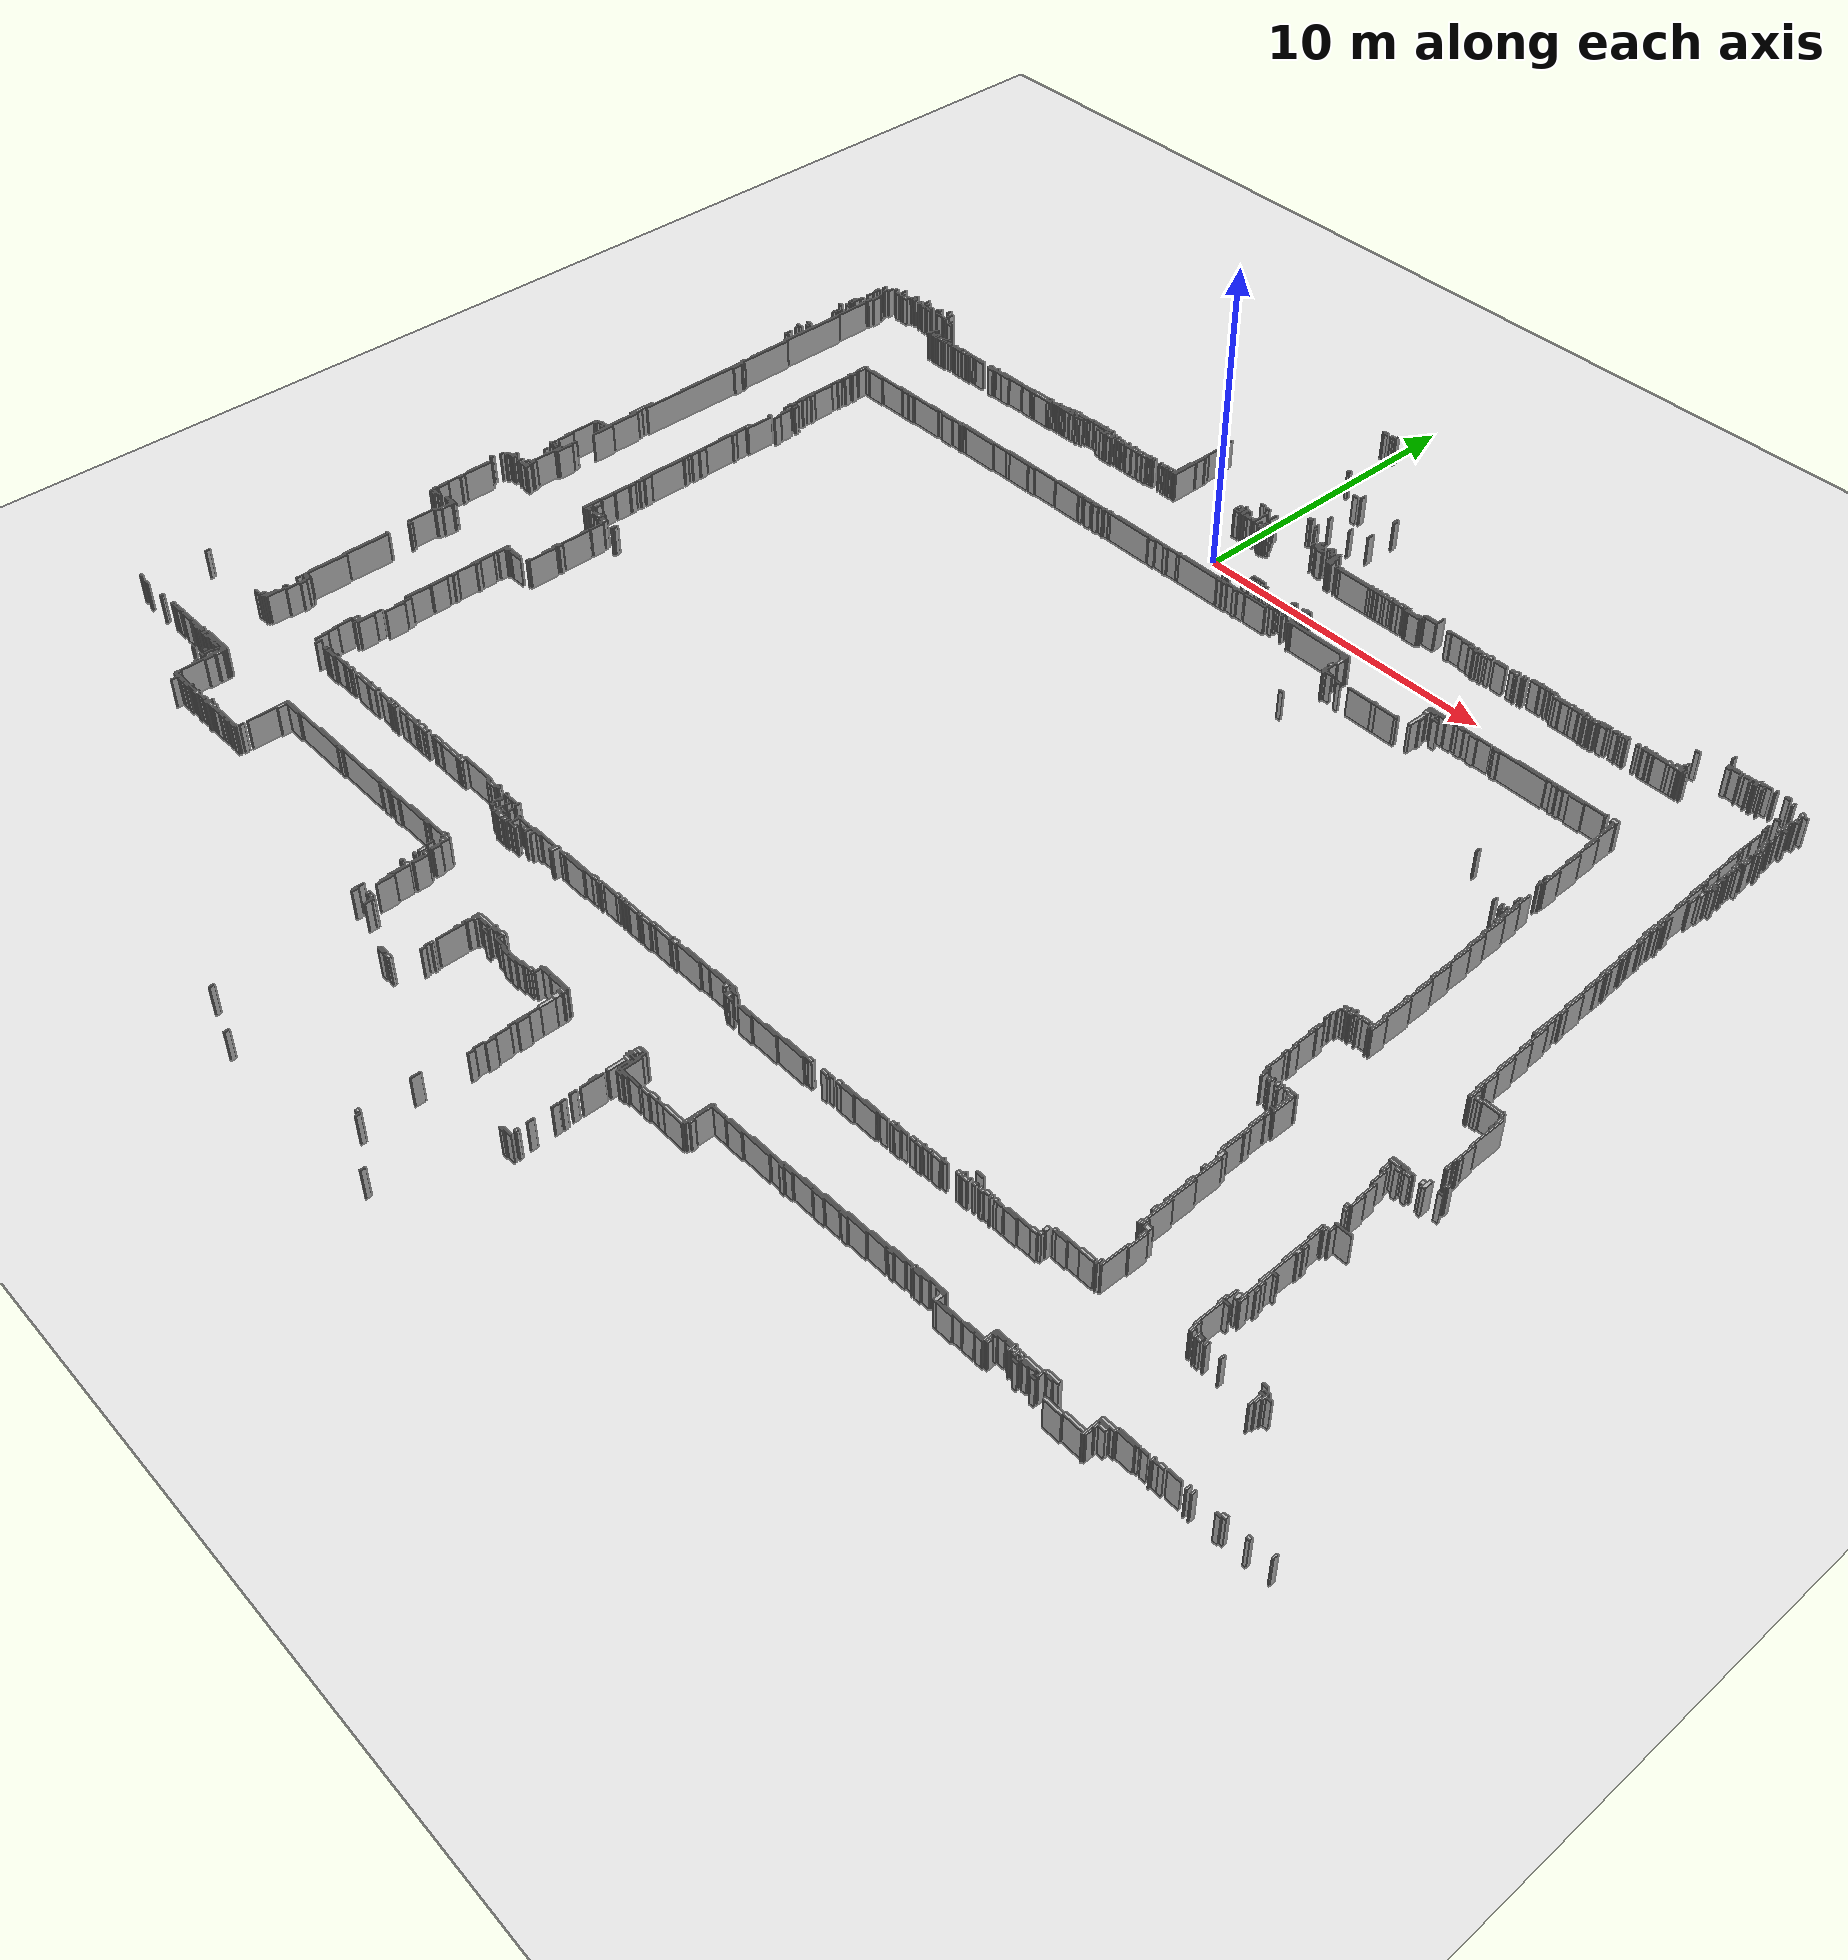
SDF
<?xml version="1.0"?>
<sdf version="1.8">
  <world name="building">
    <plugin filename="ignition-gazebo-physics-system" name="ignition::gazebo::systems::Physics"/>
    <plugin filename="ignition-gazebo-sensors-system" name="ignition::gazebo::systems::Sensors">
      <render_engine>ogre2</render_engine>
    </plugin>
    <plugin filename="ignition-gazebo-scene-broadcaster-system" name="ignition::gazebo::systems::SceneBroadcaster"/>
    <plugin filename="ignition-gazebo-user-commands-system" name="ignition::gazebo::systems::UserCommands"/>
    <light type="directional" name="sun">
      <cast_shadows>true</cast_shadows><pose>0 0 10 0 0 0</pose>
      <diffuse>0.8 0.8 0.8 1</diffuse><specular>0.2 0.2 0.2 1</specular>
      <direction>-0.5 0.1 -0.9</direction>
    </light>
    <model name="ground_plane"><static>true</static>
      <link name="link">
        <collision name="c"><geometry><plane><normal>0 0 1</normal><size>200 200</size></plane></geometry></collision>
        <visual name="v"><geometry><plane><normal>0 0 1</normal><size>200 200</size></plane></geometry>
          <material><ambient>0.9 0.9 0.9 1</ambient><diffuse>0.9 0.9 0.9 1</diffuse></material>
        </visual>
      </link>
    </model>
    <model name="walls"><static>true</static>
      <link name="wall_0">
        <pose>0.175 7.875 0.500 0 0 0</pose>
        <collision name="c"><geometry><box><size>0.050 0.150 1.000</size></box></geometry></collision>
        <visual name="v"><geometry><box><size>0.050 0.150 1.000</size></box></geometry>
          <material><ambient>0.6 0.6 0.6 1</ambient><diffuse>0.7 0.7 0.7 1</diffuse></material>
        </visual>
      </link>
      <link name="wall_1">
        <pose>-0.250 7.825 0.500 0 0 0</pose>
        <collision name="c"><geometry><box><size>0.200 0.050 1.000</size></box></geometry></collision>
        <visual name="v"><geometry><box><size>0.200 0.050 1.000</size></box></geometry>
          <material><ambient>0.6 0.6 0.6 1</ambient><diffuse>0.7 0.7 0.7 1</diffuse></material>
        </visual>
      </link>
      <link name="wall_2">
        <pose>0.050 7.800 0.500 0 0 0</pose>
        <collision name="c"><geometry><box><size>0.100 0.100 1.000</size></box></geometry></collision>
        <visual name="v"><geometry><box><size>0.100 0.100 1.000</size></box></geometry>
          <material><ambient>0.6 0.6 0.6 1</ambient><diffuse>0.7 0.7 0.7 1</diffuse></material>
        </visual>
      </link>
      <link name="wall_3">
        <pose>-0.175 7.775 0.500 0 0 0</pose>
        <collision name="c"><geometry><box><size>0.150 0.050 1.000</size></box></geometry></collision>
        <visual name="v"><geometry><box><size>0.150 0.050 1.000</size></box></geometry>
          <material><ambient>0.6 0.6 0.6 1</ambient><diffuse>0.7 0.7 0.7 1</diffuse></material>
        </visual>
      </link>
      <link name="wall_4">
        <pose>0.400 5.400 0.500 0 0 0</pose>
        <collision name="c"><geometry><box><size>0.100 0.100 1.000</size></box></geometry></collision>
        <visual name="v"><geometry><box><size>0.100 0.100 1.000</size></box></geometry>
          <material><ambient>0.6 0.6 0.6 1</ambient><diffuse>0.7 0.7 0.7 1</diffuse></material>
        </visual>
      </link>
      <link name="wall_5">
        <pose>1.575 4.700 0.500 0 0 0</pose>
        <collision name="c"><geometry><box><size>0.050 0.200 1.000</size></box></geometry></collision>
        <visual name="v"><geometry><box><size>0.050 0.200 1.000</size></box></geometry>
          <material><ambient>0.6 0.6 0.6 1</ambient><diffuse>0.7 0.7 0.7 1</diffuse></material>
        </visual>
      </link>
      <link name="wall_6">
        <pose>1.400 4.575 0.500 0 0 0</pose>
        <collision name="c"><geometry><box><size>0.200 0.050 1.000</size></box></geometry></collision>
        <visual name="v"><geometry><box><size>0.200 0.050 1.000</size></box></geometry>
          <material><ambient>0.6 0.6 0.6 1</ambient><diffuse>0.7 0.7 0.7 1</diffuse></material>
        </visual>
      </link>
      <link name="wall_7">
        <pose>3.025 4.500 0.500 0 0 0</pose>
        <collision name="c"><geometry><box><size>0.050 0.200 1.000</size></box></geometry></collision>
        <visual name="v"><geometry><box><size>0.050 0.200 1.000</size></box></geometry>
          <material><ambient>0.6 0.6 0.6 1</ambient><diffuse>0.7 0.7 0.7 1</diffuse></material>
        </visual>
      </link>
      <link name="wall_8">
        <pose>3.075 4.450 0.500 0 0 0</pose>
        <collision name="c"><geometry><box><size>0.050 0.200 1.000</size></box></geometry></collision>
        <visual name="v"><geometry><box><size>0.050 0.200 1.000</size></box></geometry>
          <material><ambient>0.6 0.6 0.6 1</ambient><diffuse>0.7 0.7 0.7 1</diffuse></material>
        </visual>
      </link>
      <link name="wall_9">
        <pose>-3.125 3.850 0.500 0 0 0</pose>
        <collision name="c"><geometry><box><size>0.050 0.200 1.000</size></box></geometry></collision>
        <visual name="v"><geometry><box><size>0.050 0.200 1.000</size></box></geometry>
          <material><ambient>0.6 0.6 0.6 1</ambient><diffuse>0.7 0.7 0.7 1</diffuse></material>
        </visual>
      </link>
      <link name="wall_10">
        <pose>-3.075 3.575 0.500 0 0 0</pose>
        <collision name="c"><geometry><box><size>0.150 0.050 1.000</size></box></geometry></collision>
        <visual name="v"><geometry><box><size>0.150 0.050 1.000</size></box></geometry>
          <material><ambient>0.6 0.6 0.6 1</ambient><diffuse>0.7 0.7 0.7 1</diffuse></material>
        </visual>
      </link>
      <link name="wall_11">
        <pose>-3.075 2.450 0.500 0 0 0</pose>
        <collision name="c"><geometry><box><size>0.050 2.200 1.000</size></box></geometry></collision>
        <visual name="v"><geometry><box><size>0.050 2.200 1.000</size></box></geometry>
          <material><ambient>0.6 0.6 0.6 1</ambient><diffuse>0.7 0.7 0.7 1</diffuse></material>
        </visual>
      </link>
      <link name="wall_12">
        <pose>3.025 3.375 0.500 0 0 0</pose>
        <collision name="c"><geometry><box><size>0.050 0.250 1.000</size></box></geometry></collision>
        <visual name="v"><geometry><box><size>0.050 0.250 1.000</size></box></geometry>
          <material><ambient>0.6 0.6 0.6 1</ambient><diffuse>0.7 0.7 0.7 1</diffuse></material>
        </visual>
      </link>
      <link name="wall_13">
        <pose>1.625 3.175 0.500 0 0 0</pose>
        <collision name="c"><geometry><box><size>0.050 0.150 1.000</size></box></geometry></collision>
        <visual name="v"><geometry><box><size>0.050 0.150 1.000</size></box></geometry>
          <material><ambient>0.6 0.6 0.6 1</ambient><diffuse>0.7 0.7 0.7 1</diffuse></material>
        </visual>
      </link>
      <link name="wall_14">
        <pose>2.425 3.175 0.500 0 0 0</pose>
        <collision name="c"><geometry><box><size>0.050 0.150 1.000</size></box></geometry></collision>
        <visual name="v"><geometry><box><size>0.050 0.150 1.000</size></box></geometry>
          <material><ambient>0.6 0.6 0.6 1</ambient><diffuse>0.7 0.7 0.7 1</diffuse></material>
        </visual>
      </link>
      <link name="wall_15">
        <pose>16.075 3.075 0.500 0 0 0</pose>
        <collision name="c"><geometry><box><size>0.050 0.150 1.000</size></box></geometry></collision>
        <visual name="v"><geometry><box><size>0.050 0.150 1.000</size></box></geometry>
          <material><ambient>0.6 0.6 0.6 1</ambient><diffuse>0.7 0.7 0.7 1</diffuse></material>
        </visual>
      </link>
      <link name="wall_16">
        <pose>17.125 2.700 0.500 0 0 0</pose>
        <collision name="c"><geometry><box><size>0.050 0.300 1.000</size></box></geometry></collision>
        <visual name="v"><geometry><box><size>0.050 0.300 1.000</size></box></geometry>
          <material><ambient>0.6 0.6 0.6 1</ambient><diffuse>0.7 0.7 0.7 1</diffuse></material>
        </visual>
      </link>
      <link name="wall_17">
        <pose>17.625 2.775 0.500 0 0 0</pose>
        <collision name="c"><geometry><box><size>0.050 0.150 1.000</size></box></geometry></collision>
        <visual name="v"><geometry><box><size>0.050 0.150 1.000</size></box></geometry>
          <material><ambient>0.6 0.6 0.6 1</ambient><diffuse>0.7 0.7 0.7 1</diffuse></material>
        </visual>
      </link>
      <link name="wall_18">
        <pose>17.975 2.800 0.500 0 0 0</pose>
        <collision name="c"><geometry><box><size>0.150 0.100 1.000</size></box></geometry></collision>
        <visual name="v"><geometry><box><size>0.150 0.100 1.000</size></box></geometry>
          <material><ambient>0.6 0.6 0.6 1</ambient><diffuse>0.7 0.7 0.7 1</diffuse></material>
        </visual>
      </link>
      <link name="wall_19">
        <pose>-3.025 2.725 0.500 0 0 0</pose>
        <collision name="c"><geometry><box><size>0.050 0.150 1.000</size></box></geometry></collision>
        <visual name="v"><geometry><box><size>0.050 0.150 1.000</size></box></geometry>
          <material><ambient>0.6 0.6 0.6 1</ambient><diffuse>0.7 0.7 0.7 1</diffuse></material>
        </visual>
      </link>
      <link name="wall_20">
        <pose>1.325 2.725 0.500 0 0 0</pose>
        <collision name="c"><geometry><box><size>0.050 0.150 1.000</size></box></geometry></collision>
        <visual name="v"><geometry><box><size>0.050 0.150 1.000</size></box></geometry>
          <material><ambient>0.6 0.6 0.6 1</ambient><diffuse>0.7 0.7 0.7 1</diffuse></material>
        </visual>
      </link>
      <link name="wall_21">
        <pose>17.325 2.775 0.500 0 0 0</pose>
        <collision name="c"><geometry><box><size>0.350 0.050 1.000</size></box></geometry></collision>
        <visual name="v"><geometry><box><size>0.350 0.050 1.000</size></box></geometry>
          <material><ambient>0.6 0.6 0.6 1</ambient><diffuse>0.7 0.7 0.7 1</diffuse></material>
        </visual>
      </link>
      <link name="wall_22">
        <pose>1.250 2.700 0.500 0 0 0</pose>
        <collision name="c"><geometry><box><size>0.100 0.100 1.000</size></box></geometry></collision>
        <visual name="v"><geometry><box><size>0.100 0.100 1.000</size></box></geometry>
          <material><ambient>0.6 0.6 0.6 1</ambient><diffuse>0.7 0.7 0.7 1</diffuse></material>
        </visual>
      </link>
      <link name="wall_23">
        <pose>16.350 2.700 0.500 0 0 0</pose>
        <collision name="c"><geometry><box><size>0.400 0.100 1.000</size></box></geometry></collision>
        <visual name="v"><geometry><box><size>0.400 0.100 1.000</size></box></geometry>
          <material><ambient>0.6 0.6 0.6 1</ambient><diffuse>0.7 0.7 0.7 1</diffuse></material>
        </visual>
      </link>
      <link name="wall_24">
        <pose>16.625 2.650 0.500 0 0 0</pose>
        <collision name="c"><geometry><box><size>0.050 0.200 1.000</size></box></geometry></collision>
        <visual name="v"><geometry><box><size>0.050 0.200 1.000</size></box></geometry>
          <material><ambient>0.6 0.6 0.6 1</ambient><diffuse>0.7 0.7 0.7 1</diffuse></material>
        </visual>
      </link>
      <link name="wall_25">
        <pose>16.800 2.700 0.500 0 0 0</pose>
        <collision name="c"><geometry><box><size>0.200 0.100 1.000</size></box></geometry></collision>
        <visual name="v"><geometry><box><size>0.200 0.100 1.000</size></box></geometry>
          <material><ambient>0.6 0.6 0.6 1</ambient><diffuse>0.7 0.7 0.7 1</diffuse></material>
        </visual>
      </link>
      <link name="wall_26">
        <pose>17.025 2.725 0.500 0 0 0</pose>
        <collision name="c"><geometry><box><size>0.150 0.050 1.000</size></box></geometry></collision>
        <visual name="v"><geometry><box><size>0.150 0.050 1.000</size></box></geometry>
          <material><ambient>0.6 0.6 0.6 1</ambient><diffuse>0.7 0.7 0.7 1</diffuse></material>
        </visual>
      </link>
      <link name="wall_27">
        <pose>17.225 2.725 0.500 0 0 0</pose>
        <collision name="c"><geometry><box><size>0.150 0.050 1.000</size></box></geometry></collision>
        <visual name="v"><geometry><box><size>0.150 0.050 1.000</size></box></geometry>
          <material><ambient>0.6 0.6 0.6 1</ambient><diffuse>0.7 0.7 0.7 1</diffuse></material>
        </visual>
      </link>
      <link name="wall_28">
        <pose>18.225 2.675 0.500 0 0 0</pose>
        <collision name="c"><geometry><box><size>0.050 0.150 1.000</size></box></geometry></collision>
        <visual name="v"><geometry><box><size>0.050 0.150 1.000</size></box></geometry>
          <material><ambient>0.6 0.6 0.6 1</ambient><diffuse>0.7 0.7 0.7 1</diffuse></material>
        </visual>
      </link>
      <link name="wall_29">
        <pose>16.925 2.625 0.500 0 0 0</pose>
        <collision name="c"><geometry><box><size>0.050 0.150 1.000</size></box></geometry></collision>
        <visual name="v"><geometry><box><size>0.050 0.150 1.000</size></box></geometry>
          <material><ambient>0.6 0.6 0.6 1</ambient><diffuse>0.7 0.7 0.7 1</diffuse></material>
        </visual>
      </link>
      <link name="wall_30">
        <pose>17.075 2.625 0.500 0 0 0</pose>
        <collision name="c"><geometry><box><size>0.050 0.150 1.000</size></box></geometry></collision>
        <visual name="v"><geometry><box><size>0.050 0.150 1.000</size></box></geometry>
          <material><ambient>0.6 0.6 0.6 1</ambient><diffuse>0.7 0.7 0.7 1</diffuse></material>
        </visual>
      </link>
      <link name="wall_31">
        <pose>17.325 2.625 0.500 0 0 0</pose>
        <collision name="c"><geometry><box><size>0.050 0.150 1.000</size></box></geometry></collision>
        <visual name="v"><geometry><box><size>0.050 0.150 1.000</size></box></geometry>
          <material><ambient>0.6 0.6 0.6 1</ambient><diffuse>0.7 0.7 0.7 1</diffuse></material>
        </visual>
      </link>
      <link name="wall_32">
        <pose>1.625 2.575 0.500 0 0 0</pose>
        <collision name="c"><geometry><box><size>0.050 0.150 1.000</size></box></geometry></collision>
        <visual name="v"><geometry><box><size>0.050 0.150 1.000</size></box></geometry>
          <material><ambient>0.6 0.6 0.6 1</ambient><diffuse>0.7 0.7 0.7 1</diffuse></material>
        </visual>
      </link>
      <link name="wall_33">
        <pose>16.225 2.625 0.500 0 0 0</pose>
        <collision name="c"><geometry><box><size>0.150 0.050 1.000</size></box></geometry></collision>
        <visual name="v"><geometry><box><size>0.150 0.050 1.000</size></box></geometry>
          <material><ambient>0.6 0.6 0.6 1</ambient><diffuse>0.7 0.7 0.7 1</diffuse></material>
        </visual>
      </link>
      <link name="wall_34">
        <pose>-3.025 2.425 0.500 0 0 0</pose>
        <collision name="c"><geometry><box><size>0.050 0.350 1.000</size></box></geometry></collision>
        <visual name="v"><geometry><box><size>0.050 0.350 1.000</size></box></geometry>
          <material><ambient>0.6 0.6 0.6 1</ambient><diffuse>0.7 0.7 0.7 1</diffuse></material>
        </visual>
      </link>
      <link name="wall_35">
        <pose>15.275 2.575 0.500 0 0 0</pose>
        <collision name="c"><geometry><box><size>0.150 0.050 1.000</size></box></geometry></collision>
        <visual name="v"><geometry><box><size>0.150 0.050 1.000</size></box></geometry>
          <material><ambient>0.6 0.6 0.6 1</ambient><diffuse>0.7 0.7 0.7 1</diffuse></material>
        </visual>
      </link>
      <link name="wall_36">
        <pose>18.600 2.525 0.500 0 0 0</pose>
        <collision name="c"><geometry><box><size>0.100 0.150 1.000</size></box></geometry></collision>
        <visual name="v"><geometry><box><size>0.100 0.150 1.000</size></box></geometry>
          <material><ambient>0.6 0.6 0.6 1</ambient><diffuse>0.7 0.7 0.7 1</diffuse></material>
        </visual>
      </link>
      <link name="wall_37">
        <pose>-14.475 2.425 0.500 0 0 0</pose>
        <collision name="c"><geometry><box><size>0.050 0.150 1.000</size></box></geometry></collision>
        <visual name="v"><geometry><box><size>0.050 0.150 1.000</size></box></geometry>
          <material><ambient>0.6 0.6 0.6 1</ambient><diffuse>0.7 0.7 0.7 1</diffuse></material>
        </visual>
      </link>
      <link name="wall_38">
        <pose>1.725 2.425 0.500 0 0 0</pose>
        <collision name="c"><geometry><box><size>0.050 0.150 1.000</size></box></geometry></collision>
        <visual name="v"><geometry><box><size>0.050 0.150 1.000</size></box></geometry>
          <material><ambient>0.6 0.6 0.6 1</ambient><diffuse>0.7 0.7 0.7 1</diffuse></material>
        </visual>
      </link>
      <link name="wall_39">
        <pose>18.725 2.475 0.500 0 0 0</pose>
        <collision name="c"><geometry><box><size>0.150 0.050 1.000</size></box></geometry></collision>
        <visual name="v"><geometry><box><size>0.150 0.050 1.000</size></box></geometry>
          <material><ambient>0.6 0.6 0.6 1</ambient><diffuse>0.7 0.7 0.7 1</diffuse></material>
        </visual>
      </link>
      <link name="wall_40">
        <pose>18.625 2.250 0.500 0 0 0</pose>
        <collision name="c"><geometry><box><size>0.050 0.400 1.000</size></box></geometry></collision>
        <visual name="v"><geometry><box><size>0.050 0.400 1.000</size></box></geometry>
          <material><ambient>0.6 0.6 0.6 1</ambient><diffuse>0.7 0.7 0.7 1</diffuse></material>
        </visual>
      </link>
      <link name="wall_41">
        <pose>-15.425 2.300 0.500 0 0 0</pose>
        <collision name="c"><geometry><box><size>0.050 0.200 1.000</size></box></geometry></collision>
        <visual name="v"><geometry><box><size>0.050 0.200 1.000</size></box></geometry>
          <material><ambient>0.6 0.6 0.6 1</ambient><diffuse>0.7 0.7 0.7 1</diffuse></material>
        </visual>
      </link>
      <link name="wall_42">
        <pose>-14.275 2.300 0.500 0 0 0</pose>
        <collision name="c"><geometry><box><size>0.050 0.200 1.000</size></box></geometry></collision>
        <visual name="v"><geometry><box><size>0.050 0.200 1.000</size></box></geometry>
          <material><ambient>0.6 0.6 0.6 1</ambient><diffuse>0.7 0.7 0.7 1</diffuse></material>
        </visual>
      </link>
      <link name="wall_43">
        <pose>-14.725 2.275 0.500 0 0 0</pose>
        <collision name="c"><geometry><box><size>0.050 0.150 1.000</size></box></geometry></collision>
        <visual name="v"><geometry><box><size>0.050 0.150 1.000</size></box></geometry>
          <material><ambient>0.6 0.6 0.6 1</ambient><diffuse>0.7 0.7 0.7 1</diffuse></material>
        </visual>
      </link>
      <link name="wall_44">
        <pose>-15.900 2.225 0.500 0 0 0</pose>
        <collision name="c"><geometry><box><size>0.100 0.150 1.000</size></box></geometry></collision>
        <visual name="v"><geometry><box><size>0.100 0.150 1.000</size></box></geometry>
          <material><ambient>0.6 0.6 0.6 1</ambient><diffuse>0.7 0.7 0.7 1</diffuse></material>
        </visual>
      </link>
      <link name="wall_45">
        <pose>-15.275 2.225 0.500 0 0 0</pose>
        <collision name="c"><geometry><box><size>0.050 0.150 1.000</size></box></geometry></collision>
        <visual name="v"><geometry><box><size>0.050 0.150 1.000</size></box></geometry>
          <material><ambient>0.6 0.6 0.6 1</ambient><diffuse>0.7 0.7 0.7 1</diffuse></material>
        </visual>
      </link>
      <link name="wall_46">
        <pose>-14.825 2.225 0.500 0 0 0</pose>
        <collision name="c"><geometry><box><size>0.050 0.150 1.000</size></box></geometry></collision>
        <visual name="v"><geometry><box><size>0.050 0.150 1.000</size></box></geometry>
          <material><ambient>0.6 0.6 0.6 1</ambient><diffuse>0.7 0.7 0.7 1</diffuse></material>
        </visual>
      </link>
      <link name="wall_47">
        <pose>-16.425 2.150 0.500 0 0 0</pose>
        <collision name="c"><geometry><box><size>0.050 0.200 1.000</size></box></geometry></collision>
        <visual name="v"><geometry><box><size>0.050 0.200 1.000</size></box></geometry>
          <material><ambient>0.6 0.6 0.6 1</ambient><diffuse>0.7 0.7 0.7 1</diffuse></material>
        </visual>
      </link>
      <link name="wall_48">
        <pose>18.700 2.200 0.500 0 0 0</pose>
        <collision name="c"><geometry><box><size>0.100 0.100 1.000</size></box></geometry></collision>
        <visual name="v"><geometry><box><size>0.100 0.100 1.000</size></box></geometry>
          <material><ambient>0.6 0.6 0.6 1</ambient><diffuse>0.7 0.7 0.7 1</diffuse></material>
        </visual>
      </link>
      <link name="wall_49">
        <pose>-15.800 2.125 0.500 0 0 0</pose>
        <collision name="c"><geometry><box><size>0.100 0.150 1.000</size></box></geometry></collision>
        <visual name="v"><geometry><box><size>0.100 0.150 1.000</size></box></geometry>
          <material><ambient>0.6 0.6 0.6 1</ambient><diffuse>0.7 0.7 0.7 1</diffuse></material>
        </visual>
      </link>
      <link name="wall_50">
        <pose>-15.575 2.125 0.500 0 0 0</pose>
        <collision name="c"><geometry><box><size>0.050 0.150 1.000</size></box></geometry></collision>
        <visual name="v"><geometry><box><size>0.050 0.150 1.000</size></box></geometry>
          <material><ambient>0.6 0.6 0.6 1</ambient><diffuse>0.7 0.7 0.7 1</diffuse></material>
        </visual>
      </link>
      <link name="wall_51">
        <pose>-15.050 2.150 0.500 0 0 0</pose>
        <collision name="c"><geometry><box><size>0.100 0.100 1.000</size></box></geometry></collision>
        <visual name="v"><geometry><box><size>0.100 0.100 1.000</size></box></geometry>
          <material><ambient>0.6 0.6 0.6 1</ambient><diffuse>0.7 0.7 0.7 1</diffuse></material>
        </visual>
      </link>
      <link name="wall_52">
        <pose>-3.025 1.775 0.500 0 0 0</pose>
        <collision name="c"><geometry><box><size>0.050 0.850 1.000</size></box></geometry></collision>
        <visual name="v"><geometry><box><size>0.050 0.850 1.000</size></box></geometry>
          <material><ambient>0.6 0.6 0.6 1</ambient><diffuse>0.7 0.7 0.7 1</diffuse></material>
        </visual>
      </link>
      <link name="wall_53">
        <pose>-0.175 2.175 0.500 0 0 0</pose>
        <collision name="c"><geometry><box><size>0.150 0.050 1.000</size></box></geometry></collision>
        <visual name="v"><geometry><box><size>0.150 0.050 1.000</size></box></geometry>
          <material><ambient>0.6 0.6 0.6 1</ambient><diffuse>0.7 0.7 0.7 1</diffuse></material>
        </visual>
      </link>
      <link name="wall_54">
        <pose>-15.950 2.100 0.500 0 0 0</pose>
        <collision name="c"><geometry><box><size>0.100 0.100 1.000</size></box></geometry></collision>
        <visual name="v"><geometry><box><size>0.100 0.100 1.000</size></box></geometry>
          <material><ambient>0.6 0.6 0.6 1</ambient><diffuse>0.7 0.7 0.7 1</diffuse></material>
        </visual>
      </link>
      <link name="wall_55">
        <pose>-15.525 2.075 0.500 0 0 0</pose>
        <collision name="c"><geometry><box><size>0.050 0.150 1.000</size></box></geometry></collision>
        <visual name="v"><geometry><box><size>0.050 0.150 1.000</size></box></geometry>
          <material><ambient>0.6 0.6 0.6 1</ambient><diffuse>0.7 0.7 0.7 1</diffuse></material>
        </visual>
      </link>
      <link name="wall_56">
        <pose>-14.225 2.075 0.500 0 0 0</pose>
        <collision name="c"><geometry><box><size>0.050 0.150 1.000</size></box></geometry></collision>
        <visual name="v"><geometry><box><size>0.050 0.150 1.000</size></box></geometry>
          <material><ambient>0.6 0.6 0.6 1</ambient><diffuse>0.7 0.7 0.7 1</diffuse></material>
        </visual>
      </link>
      <link name="wall_57">
        <pose>-13.975 2.075 0.500 0 0 0</pose>
        <collision name="c"><geometry><box><size>0.050 0.150 1.000</size></box></geometry></collision>
        <visual name="v"><geometry><box><size>0.050 0.150 1.000</size></box></geometry>
          <material><ambient>0.6 0.6 0.6 1</ambient><diffuse>0.7 0.7 0.7 1</diffuse></material>
        </visual>
      </link>
      <link name="wall_58">
        <pose>-3.125 2.025 0.500 0 0 0</pose>
        <collision name="c"><geometry><box><size>0.050 0.250 1.000</size></box></geometry></collision>
        <visual name="v"><geometry><box><size>0.050 0.250 1.000</size></box></geometry>
          <material><ambient>0.6 0.6 0.6 1</ambient><diffuse>0.7 0.7 0.7 1</diffuse></material>
        </visual>
      </link>
      <link name="wall_59">
        <pose>0.075 2.125 0.500 0 0 0</pose>
        <collision name="c"><geometry><box><size>0.150 0.050 1.000</size></box></geometry></collision>
        <visual name="v"><geometry><box><size>0.150 0.050 1.000</size></box></geometry>
          <material><ambient>0.6 0.6 0.6 1</ambient><diffuse>0.7 0.7 0.7 1</diffuse></material>
        </visual>
      </link>
      <link name="wall_60">
        <pose>-16.700 2.050 0.500 0 0 0</pose>
        <collision name="c"><geometry><box><size>0.100 0.100 1.000</size></box></geometry></collision>
        <visual name="v"><geometry><box><size>0.100 0.100 1.000</size></box></geometry>
          <material><ambient>0.6 0.6 0.6 1</ambient><diffuse>0.7 0.7 0.7 1</diffuse></material>
        </visual>
      </link>
      <link name="wall_61">
        <pose>-15.275 2.075 0.500 0 0 0</pose>
        <collision name="c"><geometry><box><size>0.450 0.050 1.000</size></box></geometry></collision>
        <visual name="v"><geometry><box><size>0.450 0.050 1.000</size></box></geometry>
          <material><ambient>0.6 0.6 0.6 1</ambient><diffuse>0.7 0.7 0.7 1</diffuse></material>
        </visual>
      </link>
      <link name="wall_62">
        <pose>-14.575 2.075 0.500 0 0 0</pose>
        <collision name="c"><geometry><box><size>0.250 0.050 1.000</size></box></geometry></collision>
        <visual name="v"><geometry><box><size>0.250 0.050 1.000</size></box></geometry>
          <material><ambient>0.6 0.6 0.6 1</ambient><diffuse>0.7 0.7 0.7 1</diffuse></material>
        </visual>
      </link>
      <link name="wall_63">
        <pose>-14.325 2.075 0.500 0 0 0</pose>
        <collision name="c"><geometry><box><size>0.150 0.050 1.000</size></box></geometry></collision>
        <visual name="v"><geometry><box><size>0.150 0.050 1.000</size></box></geometry>
          <material><ambient>0.6 0.6 0.6 1</ambient><diffuse>0.7 0.7 0.7 1</diffuse></material>
        </visual>
      </link>
      <link name="wall_64">
        <pose>0.475 1.925 0.500 0 0 0</pose>
        <collision name="c"><geometry><box><size>0.050 0.350 1.000</size></box></geometry></collision>
        <visual name="v"><geometry><box><size>0.050 0.350 1.000</size></box></geometry>
          <material><ambient>0.6 0.6 0.6 1</ambient><diffuse>0.7 0.7 0.7 1</diffuse></material>
        </visual>
      </link>
      <link name="wall_65">
        <pose>2.350 2.050 0.500 0 0 0</pose>
        <collision name="c"><geometry><box><size>0.100 0.100 1.000</size></box></geometry></collision>
        <visual name="v"><geometry><box><size>0.100 0.100 1.000</size></box></geometry>
          <material><ambient>0.6 0.6 0.6 1</ambient><diffuse>0.7 0.7 0.7 1</diffuse></material>
        </visual>
      </link>
      <link name="wall_66">
        <pose>2.750 2.050 0.500 0 0 0</pose>
        <collision name="c"><geometry><box><size>0.100 0.100 1.000</size></box></geometry></collision>
        <visual name="v"><geometry><box><size>0.100 0.100 1.000</size></box></geometry>
          <material><ambient>0.6 0.6 0.6 1</ambient><diffuse>0.7 0.7 0.7 1</diffuse></material>
        </visual>
      </link>
      <link name="wall_67">
        <pose>18.575 1.800 0.500 0 0 0</pose>
        <collision name="c"><geometry><box><size>0.050 0.600 1.000</size></box></geometry></collision>
        <visual name="v"><geometry><box><size>0.050 0.600 1.000</size></box></geometry>
          <material><ambient>0.6 0.6 0.6 1</ambient><diffuse>0.7 0.7 0.7 1</diffuse></material>
        </visual>
      </link>
      <link name="wall_68">
        <pose>-16.275 1.975 0.500 0 0 0</pose>
        <collision name="c"><geometry><box><size>0.050 0.150 1.000</size></box></geometry></collision>
        <visual name="v"><geometry><box><size>0.050 0.150 1.000</size></box></geometry>
          <material><ambient>0.6 0.6 0.6 1</ambient><diffuse>0.7 0.7 0.7 1</diffuse></material>
        </visual>
      </link>
      <link name="wall_69">
        <pose>-16.100 1.975 0.500 0 0 0</pose>
        <collision name="c"><geometry><box><size>0.200 0.150 1.000</size></box></geometry></collision>
        <visual name="v"><geometry><box><size>0.200 0.150 1.000</size></box></geometry>
          <material><ambient>0.6 0.6 0.6 1</ambient><diffuse>0.7 0.7 0.7 1</diffuse></material>
        </visual>
      </link>
      <link name="wall_70">
        <pose>-15.275 2.025 0.500 0 0 0</pose>
        <collision name="c"><geometry><box><size>0.150 0.050 1.000</size></box></geometry></collision>
        <visual name="v"><geometry><box><size>0.150 0.050 1.000</size></box></geometry>
          <material><ambient>0.6 0.6 0.6 1</ambient><diffuse>0.7 0.7 0.7 1</diffuse></material>
        </visual>
      </link>
      <link name="wall_71">
        <pose>-15.025 2.025 0.500 0 0 0</pose>
        <collision name="c"><geometry><box><size>0.150 0.050 1.000</size></box></geometry></collision>
        <visual name="v"><geometry><box><size>0.150 0.050 1.000</size></box></geometry>
          <material><ambient>0.6 0.6 0.6 1</ambient><diffuse>0.7 0.7 0.7 1</diffuse></material>
        </visual>
      </link>
      <link name="wall_72">
        <pose>2.275 1.925 0.500 0 0 0</pose>
        <collision name="c"><geometry><box><size>0.050 0.250 1.000</size></box></geometry></collision>
        <visual name="v"><geometry><box><size>0.050 0.250 1.000</size></box></geometry>
          <material><ambient>0.6 0.6 0.6 1</ambient><diffuse>0.7 0.7 0.7 1</diffuse></material>
        </visual>
      </link>
      <link name="wall_73">
        <pose>2.650 2.000 0.500 0 0 0</pose>
        <collision name="c"><geometry><box><size>0.100 0.100 1.000</size></box></geometry></collision>
        <visual name="v"><geometry><box><size>0.100 0.100 1.000</size></box></geometry>
          <material><ambient>0.6 0.6 0.6 1</ambient><diffuse>0.7 0.7 0.7 1</diffuse></material>
        </visual>
      </link>
      <link name="wall_74">
        <pose>3.025 1.750 0.500 0 0 0</pose>
        <collision name="c"><geometry><box><size>0.050 0.600 1.000</size></box></geometry></collision>
        <visual name="v"><geometry><box><size>0.050 0.600 1.000</size></box></geometry>
          <material><ambient>0.6 0.6 0.6 1</ambient><diffuse>0.7 0.7 0.7 1</diffuse></material>
        </visual>
      </link>
      <link name="wall_75">
        <pose>-16.825 1.900 0.500 0 0 0</pose>
        <collision name="c"><geometry><box><size>0.050 0.200 1.000</size></box></geometry></collision>
        <visual name="v"><geometry><box><size>0.050 0.200 1.000</size></box></geometry>
          <material><ambient>0.6 0.6 0.6 1</ambient><diffuse>0.7 0.7 0.7 1</diffuse></material>
        </visual>
      </link>
      <link name="wall_76">
        <pose>-16.475 1.950 0.500 0 0 0</pose>
        <collision name="c"><geometry><box><size>0.150 0.100 1.000</size></box></geometry></collision>
        <visual name="v"><geometry><box><size>0.150 0.100 1.000</size></box></geometry>
          <material><ambient>0.6 0.6 0.6 1</ambient><diffuse>0.7 0.7 0.7 1</diffuse></material>
        </visual>
      </link>
      <link name="wall_77">
        <pose>2.325 1.875 0.500 0 0 0</pose>
        <collision name="c"><geometry><box><size>0.050 0.250 1.000</size></box></geometry></collision>
        <visual name="v"><geometry><box><size>0.050 0.250 1.000</size></box></geometry>
          <material><ambient>0.6 0.6 0.6 1</ambient><diffuse>0.7 0.7 0.7 1</diffuse></material>
        </visual>
      </link>
      <link name="wall_78">
        <pose>2.800 1.950 0.500 0 0 0</pose>
        <collision name="c"><geometry><box><size>0.100 0.100 1.000</size></box></geometry></collision>
        <visual name="v"><geometry><box><size>0.100 0.100 1.000</size></box></geometry>
          <material><ambient>0.6 0.6 0.6 1</ambient><diffuse>0.7 0.7 0.7 1</diffuse></material>
        </visual>
      </link>
      <link name="wall_79">
        <pose>3.075 1.725 0.500 0 0 0</pose>
        <collision name="c"><geometry><box><size>0.050 0.550 1.000</size></box></geometry></collision>
        <visual name="v"><geometry><box><size>0.050 0.550 1.000</size></box></geometry>
          <material><ambient>0.6 0.6 0.6 1</ambient><diffuse>0.7 0.7 0.7 1</diffuse></material>
        </visual>
      </link>
      <link name="wall_80">
        <pose>15.425 1.925 0.500 0 0 0</pose>
        <collision name="c"><geometry><box><size>0.050 0.150 1.000</size></box></geometry></collision>
        <visual name="v"><geometry><box><size>0.050 0.150 1.000</size></box></geometry>
          <material><ambient>0.6 0.6 0.6 1</ambient><diffuse>0.7 0.7 0.7 1</diffuse></material>
        </visual>
      </link>
      <link name="wall_81">
        <pose>-17.075 1.875 0.500 0 0 0</pose>
        <collision name="c"><geometry><box><size>0.050 0.150 1.000</size></box></geometry></collision>
        <visual name="v"><geometry><box><size>0.050 0.150 1.000</size></box></geometry>
          <material><ambient>0.6 0.6 0.6 1</ambient><diffuse>0.7 0.7 0.7 1</diffuse></material>
        </visual>
      </link>
      <link name="wall_82">
        <pose>-13.900 1.925 0.500 0 0 0</pose>
        <collision name="c"><geometry><box><size>0.200 0.050 1.000</size></box></geometry></collision>
        <visual name="v"><geometry><box><size>0.200 0.050 1.000</size></box></geometry>
          <material><ambient>0.6 0.6 0.6 1</ambient><diffuse>0.7 0.7 0.7 1</diffuse></material>
        </visual>
      </link>
      <link name="wall_83">
        <pose>2.450 1.900 0.500 0 0 0</pose>
        <collision name="c"><geometry><box><size>0.200 0.100 1.000</size></box></geometry></collision>
        <visual name="v"><geometry><box><size>0.200 0.100 1.000</size></box></geometry>
          <material><ambient>0.6 0.6 0.6 1</ambient><diffuse>0.7 0.7 0.7 1</diffuse></material>
        </visual>
      </link>
      <link name="wall_84">
        <pose>2.900 1.875 0.500 0 0 0</pose>
        <collision name="c"><geometry><box><size>0.100 0.150 1.000</size></box></geometry></collision>
        <visual name="v"><geometry><box><size>0.100 0.150 1.000</size></box></geometry>
          <material><ambient>0.6 0.6 0.6 1</ambient><diffuse>0.7 0.7 0.7 1</diffuse></material>
        </visual>
      </link>
      <link name="wall_85">
        <pose>7.025 1.775 0.500 0 0 0</pose>
        <collision name="c"><geometry><box><size>0.050 0.350 1.000</size></box></geometry></collision>
        <visual name="v"><geometry><box><size>0.050 0.350 1.000</size></box></geometry>
          <material><ambient>0.6 0.6 0.6 1</ambient><diffuse>0.7 0.7 0.7 1</diffuse></material>
        </visual>
      </link>
      <link name="wall_86">
        <pose>0.225 1.625 0.500 0 0 0</pose>
        <collision name="c"><geometry><box><size>0.050 0.550 1.000</size></box></geometry></collision>
        <visual name="v"><geometry><box><size>0.050 0.550 1.000</size></box></geometry>
          <material><ambient>0.6 0.6 0.6 1</ambient><diffuse>0.7 0.7 0.7 1</diffuse></material>
        </visual>
      </link>
      <link name="wall_87">
        <pose>2.175 1.825 0.500 0 0 0</pose>
        <collision name="c"><geometry><box><size>0.050 0.150 1.000</size></box></geometry></collision>
        <visual name="v"><geometry><box><size>0.050 0.150 1.000</size></box></geometry>
          <material><ambient>0.6 0.6 0.6 1</ambient><diffuse>0.7 0.7 0.7 1</diffuse></material>
        </visual>
      </link>
      <link name="wall_88">
        <pose>18.275 1.875 0.500 0 0 0</pose>
        <collision name="c"><geometry><box><size>0.150 0.050 1.000</size></box></geometry></collision>
        <visual name="v"><geometry><box><size>0.150 0.050 1.000</size></box></geometry>
          <material><ambient>0.6 0.6 0.6 1</ambient><diffuse>0.7 0.7 0.7 1</diffuse></material>
        </visual>
      </link>
      <link name="wall_89">
        <pose>-16.875 1.750 0.500 0 0 0</pose>
        <collision name="c"><geometry><box><size>0.050 0.200 1.000</size></box></geometry></collision>
        <visual name="v"><geometry><box><size>0.050 0.200 1.000</size></box></geometry>
          <material><ambient>0.6 0.6 0.6 1</ambient><diffuse>0.7 0.7 0.7 1</diffuse></material>
        </visual>
      </link>
      <link name="wall_90">
        <pose>-3.125 1.725 0.500 0 0 0</pose>
        <collision name="c"><geometry><box><size>0.050 0.250 1.000</size></box></geometry></collision>
        <visual name="v"><geometry><box><size>0.050 0.250 1.000</size></box></geometry>
          <material><ambient>0.6 0.6 0.6 1</ambient><diffuse>0.7 0.7 0.7 1</diffuse></material>
        </visual>
      </link>
      <link name="wall_91">
        <pose>2.425 1.800 0.500 0 0 0</pose>
        <collision name="c"><geometry><box><size>0.150 0.100 1.000</size></box></geometry></collision>
        <visual name="v"><geometry><box><size>0.150 0.100 1.000</size></box></geometry>
          <material><ambient>0.6 0.6 0.6 1</ambient><diffuse>0.7 0.7 0.7 1</diffuse></material>
        </visual>
      </link>
      <link name="wall_92">
        <pose>3.125 1.650 0.500 0 0 0</pose>
        <collision name="c"><geometry><box><size>0.050 0.400 1.000</size></box></geometry></collision>
        <visual name="v"><geometry><box><size>0.050 0.400 1.000</size></box></geometry>
          <material><ambient>0.6 0.6 0.6 1</ambient><diffuse>0.7 0.7 0.7 1</diffuse></material>
        </visual>
      </link>
      <link name="wall_93">
        <pose>15.375 1.700 0.500 0 0 0</pose>
        <collision name="c"><geometry><box><size>0.050 0.300 1.000</size></box></geometry></collision>
        <visual name="v"><geometry><box><size>0.050 0.300 1.000</size></box></geometry>
          <material><ambient>0.6 0.6 0.6 1</ambient><diffuse>0.7 0.7 0.7 1</diffuse></material>
        </visual>
      </link>
      <link name="wall_94">
        <pose>18.625 1.750 0.500 0 0 0</pose>
        <collision name="c"><geometry><box><size>0.050 0.200 1.000</size></box></geometry></collision>
        <visual name="v"><geometry><box><size>0.050 0.200 1.000</size></box></geometry>
          <material><ambient>0.6 0.6 0.6 1</ambient><diffuse>0.7 0.7 0.7 1</diffuse></material>
        </visual>
      </link>
      <link name="wall_95">
        <pose>2.575 1.775 0.500 0 0 0</pose>
        <collision name="c"><geometry><box><size>0.150 0.050 1.000</size></box></geometry></collision>
        <visual name="v"><geometry><box><size>0.150 0.050 1.000</size></box></geometry>
          <material><ambient>0.6 0.6 0.6 1</ambient><diffuse>0.7 0.7 0.7 1</diffuse></material>
        </visual>
      </link>
      <link name="wall_96">
        <pose>-0.425 1.600 0.500 0 0 0</pose>
        <collision name="c"><geometry><box><size>0.050 0.300 1.000</size></box></geometry></collision>
        <visual name="v"><geometry><box><size>0.050 0.300 1.000</size></box></geometry>
          <material><ambient>0.6 0.6 0.6 1</ambient><diffuse>0.7 0.7 0.7 1</diffuse></material>
        </visual>
      </link>
      <link name="wall_97">
        <pose>2.500 1.725 0.500 0 0 0</pose>
        <collision name="c"><geometry><box><size>0.200 0.050 1.000</size></box></geometry></collision>
        <visual name="v"><geometry><box><size>0.200 0.050 1.000</size></box></geometry>
          <material><ambient>0.6 0.6 0.6 1</ambient><diffuse>0.7 0.7 0.7 1</diffuse></material>
        </visual>
      </link>
      <link name="wall_98">
        <pose>10.725 1.675 0.500 0 0 0</pose>
        <collision name="c"><geometry><box><size>0.050 0.150 1.000</size></box></geometry></collision>
        <visual name="v"><geometry><box><size>0.050 0.150 1.000</size></box></geometry>
          <material><ambient>0.6 0.6 0.6 1</ambient><diffuse>0.7 0.7 0.7 1</diffuse></material>
        </visual>
      </link>
      <link name="wall_99">
        <pose>15.275 1.725 0.500 0 0 0</pose>
        <collision name="c"><geometry><box><size>0.150 0.050 1.000</size></box></geometry></collision>
        <visual name="v"><geometry><box><size>0.150 0.050 1.000</size></box></geometry>
          <material><ambient>0.6 0.6 0.6 1</ambient><diffuse>0.7 0.7 0.7 1</diffuse></material>
        </visual>
      </link>
      <link name="wall_100">
        <pose>15.425 1.650 0.500 0 0 0</pose>
        <collision name="c"><geometry><box><size>0.050 0.200 1.000</size></box></geometry></collision>
        <visual name="v"><geometry><box><size>0.050 0.200 1.000</size></box></geometry>
          <material><ambient>0.6 0.6 0.6 1</ambient><diffuse>0.7 0.7 0.7 1</diffuse></material>
        </visual>
      </link>
      <link name="wall_101">
        <pose>0.675 1.500 0.500 0 0 0</pose>
        <collision name="c"><geometry><box><size>0.050 0.400 1.000</size></box></geometry></collision>
        <visual name="v"><geometry><box><size>0.050 0.400 1.000</size></box></geometry>
          <material><ambient>0.6 0.6 0.6 1</ambient><diffuse>0.7 0.7 0.7 1</diffuse></material>
        </visual>
      </link>
      <link name="wall_102">
        <pose>6.775 1.650 0.500 0 0 0</pose>
        <collision name="c"><geometry><box><size>0.450 0.100 1.000</size></box></geometry></collision>
        <visual name="v"><geometry><box><size>0.450 0.100 1.000</size></box></geometry>
          <material><ambient>0.6 0.6 0.6 1</ambient><diffuse>0.7 0.7 0.7 1</diffuse></material>
        </visual>
      </link>
      <link name="wall_103">
        <pose>10.550 1.650 0.500 0 0 0</pose>
        <collision name="c"><geometry><box><size>0.300 0.100 1.000</size></box></geometry></collision>
        <visual name="v"><geometry><box><size>0.300 0.100 1.000</size></box></geometry>
          <material><ambient>0.6 0.6 0.6 1</ambient><diffuse>0.7 0.7 0.7 1</diffuse></material>
        </visual>
      </link>
      <link name="wall_104">
        <pose>10.825 1.650 0.500 0 0 0</pose>
        <collision name="c"><geometry><box><size>0.150 0.100 1.000</size></box></geometry></collision>
        <visual name="v"><geometry><box><size>0.150 0.100 1.000</size></box></geometry>
          <material><ambient>0.6 0.6 0.6 1</ambient><diffuse>0.7 0.7 0.7 1</diffuse></material>
        </visual>
      </link>
      <link name="wall_105">
        <pose>11.000 1.650 0.500 0 0 0</pose>
        <collision name="c"><geometry><box><size>0.100 0.100 1.000</size></box></geometry></collision>
        <visual name="v"><geometry><box><size>0.100 0.100 1.000</size></box></geometry>
          <material><ambient>0.6 0.6 0.6 1</ambient><diffuse>0.7 0.7 0.7 1</diffuse></material>
        </visual>
      </link>
      <link name="wall_106">
        <pose>11.175 1.650 0.500 0 0 0</pose>
        <collision name="c"><geometry><box><size>0.150 0.100 1.000</size></box></geometry></collision>
        <visual name="v"><geometry><box><size>0.150 0.100 1.000</size></box></geometry>
          <material><ambient>0.6 0.6 0.6 1</ambient><diffuse>0.7 0.7 0.7 1</diffuse></material>
        </visual>
      </link>
      <link name="wall_107">
        <pose>13.675 1.625 0.500 0 0 0</pose>
        <collision name="c"><geometry><box><size>0.050 0.150 1.000</size></box></geometry></collision>
        <visual name="v"><geometry><box><size>0.050 0.150 1.000</size></box></geometry>
          <material><ambient>0.6 0.6 0.6 1</ambient><diffuse>0.7 0.7 0.7 1</diffuse></material>
        </visual>
      </link>
      <link name="wall_108">
        <pose>14.225 1.625 0.500 0 0 0</pose>
        <collision name="c"><geometry><box><size>0.050 0.150 1.000</size></box></geometry></collision>
        <visual name="v"><geometry><box><size>0.050 0.150 1.000</size></box></geometry>
          <material><ambient>0.6 0.6 0.6 1</ambient><diffuse>0.7 0.7 0.7 1</diffuse></material>
        </visual>
      </link>
      <link name="wall_109">
        <pose>14.425 1.625 0.500 0 0 0</pose>
        <collision name="c"><geometry><box><size>0.050 0.150 1.000</size></box></geometry></collision>
        <visual name="v"><geometry><box><size>0.050 0.150 1.000</size></box></geometry>
          <material><ambient>0.6 0.6 0.6 1</ambient><diffuse>0.7 0.7 0.7 1</diffuse></material>
        </visual>
      </link>
      <link name="wall_110">
        <pose>14.575 1.625 0.500 0 0 0</pose>
        <collision name="c"><geometry><box><size>0.050 0.150 1.000</size></box></geometry></collision>
        <visual name="v"><geometry><box><size>0.050 0.150 1.000</size></box></geometry>
          <material><ambient>0.6 0.6 0.6 1</ambient><diffuse>0.7 0.7 0.7 1</diffuse></material>
        </visual>
      </link>
      <link name="wall_111">
        <pose>15.050 1.625 0.500 0 0 0</pose>
        <collision name="c"><geometry><box><size>0.100 0.150 1.000</size></box></geometry></collision>
        <visual name="v"><geometry><box><size>0.100 0.150 1.000</size></box></geometry>
          <material><ambient>0.6 0.6 0.6 1</ambient><diffuse>0.7 0.7 0.7 1</diffuse></material>
        </visual>
      </link>
      <link name="wall_112">
        <pose>15.300 1.625 0.500 0 0 0</pose>
        <collision name="c"><geometry><box><size>0.100 0.150 1.000</size></box></geometry></collision>
        <visual name="v"><geometry><box><size>0.100 0.150 1.000</size></box></geometry>
          <material><ambient>0.6 0.6 0.6 1</ambient><diffuse>0.7 0.7 0.7 1</diffuse></material>
        </visual>
      </link>
      <link name="wall_113">
        <pose>15.475 1.625 0.500 0 0 0</pose>
        <collision name="c"><geometry><box><size>0.050 0.150 1.000</size></box></geometry></collision>
        <visual name="v"><geometry><box><size>0.050 0.150 1.000</size></box></geometry>
          <material><ambient>0.6 0.6 0.6 1</ambient><diffuse>0.7 0.7 0.7 1</diffuse></material>
        </visual>
      </link>
      <link name="wall_114">
        <pose>15.575 1.625 0.500 0 0 0</pose>
        <collision name="c"><geometry><box><size>0.050 0.150 1.000</size></box></geometry></collision>
        <visual name="v"><geometry><box><size>0.050 0.150 1.000</size></box></geometry>
          <material><ambient>0.6 0.6 0.6 1</ambient><diffuse>0.7 0.7 0.7 1</diffuse></material>
        </visual>
      </link>
      <link name="wall_115">
        <pose>18.700 1.650 0.500 0 0 0</pose>
        <collision name="c"><geometry><box><size>0.100 0.100 1.000</size></box></geometry></collision>
        <visual name="v"><geometry><box><size>0.100 0.100 1.000</size></box></geometry>
          <material><ambient>0.6 0.6 0.6 1</ambient><diffuse>0.7 0.7 0.7 1</diffuse></material>
        </visual>
      </link>
      <link name="wall_116">
        <pose>-17.075 1.625 0.500 0 0 0</pose>
        <collision name="c"><geometry><box><size>0.150 0.050 1.000</size></box></geometry></collision>
        <visual name="v"><geometry><box><size>0.150 0.050 1.000</size></box></geometry>
          <material><ambient>0.6 0.6 0.6 1</ambient><diffuse>0.7 0.7 0.7 1</diffuse></material>
        </visual>
      </link>
      <link name="wall_117">
        <pose>-0.550 1.575 0.500 0 0 0</pose>
        <collision name="c"><geometry><box><size>0.100 0.150 1.000</size></box></geometry></collision>
        <visual name="v"><geometry><box><size>0.100 0.150 1.000</size></box></geometry>
          <material><ambient>0.6 0.6 0.6 1</ambient><diffuse>0.7 0.7 0.7 1</diffuse></material>
        </visual>
      </link>
      <link name="wall_118">
        <pose>-0.225 1.625 0.500 0 0 0</pose>
        <collision name="c"><geometry><box><size>0.150 0.050 1.000</size></box></geometry></collision>
        <visual name="v"><geometry><box><size>0.150 0.050 1.000</size></box></geometry>
          <material><ambient>0.6 0.6 0.6 1</ambient><diffuse>0.7 0.7 0.7 1</diffuse></material>
        </visual>
      </link>
      <link name="wall_119">
        <pose>3.175 1.550 0.500 0 0 0</pose>
        <collision name="c"><geometry><box><size>0.050 0.200 1.000</size></box></geometry></collision>
        <visual name="v"><geometry><box><size>0.050 0.200 1.000</size></box></geometry>
          <material><ambient>0.6 0.6 0.6 1</ambient><diffuse>0.7 0.7 0.7 1</diffuse></material>
        </visual>
      </link>
      <link name="wall_120">
        <pose>7.900 1.625 0.500 0 0 0</pose>
        <collision name="c"><geometry><box><size>0.900 0.050 1.000</size></box></geometry></collision>
        <visual name="v"><geometry><box><size>0.900 0.050 1.000</size></box></geometry>
          <material><ambient>0.6 0.6 0.6 1</ambient><diffuse>0.7 0.7 0.7 1</diffuse></material>
        </visual>
      </link>
      <link name="wall_121">
        <pose>8.525 1.550 0.500 0 0 0</pose>
        <collision name="c"><geometry><box><size>0.050 0.200 1.000</size></box></geometry></collision>
        <visual name="v"><geometry><box><size>0.050 0.200 1.000</size></box></geometry>
          <material><ambient>0.6 0.6 0.6 1</ambient><diffuse>0.7 0.7 0.7 1</diffuse></material>
        </visual>
      </link>
      <link name="wall_122">
        <pose>9.025 1.575 0.500 0 0 0</pose>
        <collision name="c"><geometry><box><size>0.150 0.150 1.000</size></box></geometry></collision>
        <visual name="v"><geometry><box><size>0.150 0.150 1.000</size></box></geometry>
          <material><ambient>0.6 0.6 0.6 1</ambient><diffuse>0.7 0.7 0.7 1</diffuse></material>
        </visual>
      </link>
      <link name="wall_123">
        <pose>9.950 1.575 0.500 0 0 0</pose>
        <collision name="c"><geometry><box><size>0.100 0.150 1.000</size></box></geometry></collision>
        <visual name="v"><geometry><box><size>0.100 0.150 1.000</size></box></geometry>
          <material><ambient>0.6 0.6 0.6 1</ambient><diffuse>0.7 0.7 0.7 1</diffuse></material>
        </visual>
      </link>
      <link name="wall_124">
        <pose>10.175 1.575 0.500 0 0 0</pose>
        <collision name="c"><geometry><box><size>0.050 0.150 1.000</size></box></geometry></collision>
        <visual name="v"><geometry><box><size>0.050 0.150 1.000</size></box></geometry>
          <material><ambient>0.6 0.6 0.6 1</ambient><diffuse>0.7 0.7 0.7 1</diffuse></material>
        </visual>
      </link>
      <link name="wall_125">
        <pose>10.275 1.575 0.500 0 0 0</pose>
        <collision name="c"><geometry><box><size>0.050 0.150 1.000</size></box></geometry></collision>
        <visual name="v"><geometry><box><size>0.050 0.150 1.000</size></box></geometry>
          <material><ambient>0.6 0.6 0.6 1</ambient><diffuse>0.7 0.7 0.7 1</diffuse></material>
        </visual>
      </link>
      <link name="wall_126">
        <pose>11.300 1.575 0.500 0 0 0</pose>
        <collision name="c"><geometry><box><size>0.100 0.150 1.000</size></box></geometry></collision>
        <visual name="v"><geometry><box><size>0.100 0.150 1.000</size></box></geometry>
          <material><ambient>0.6 0.6 0.6 1</ambient><diffuse>0.7 0.7 0.7 1</diffuse></material>
        </visual>
      </link>
      <link name="wall_127">
        <pose>11.525 1.575 0.500 0 0 0</pose>
        <collision name="c"><geometry><box><size>0.050 0.150 1.000</size></box></geometry></collision>
        <visual name="v"><geometry><box><size>0.050 0.150 1.000</size></box></geometry>
          <material><ambient>0.6 0.6 0.6 1</ambient><diffuse>0.7 0.7 0.7 1</diffuse></material>
        </visual>
      </link>
      <link name="wall_128">
        <pose>11.850 1.575 0.500 0 0 0</pose>
        <collision name="c"><geometry><box><size>0.100 0.150 1.000</size></box></geometry></collision>
        <visual name="v"><geometry><box><size>0.100 0.150 1.000</size></box></geometry>
          <material><ambient>0.6 0.6 0.6 1</ambient><diffuse>0.7 0.7 0.7 1</diffuse></material>
        </visual>
      </link>
      <link name="wall_129">
        <pose>12.125 1.575 0.500 0 0 0</pose>
        <collision name="c"><geometry><box><size>0.050 0.150 1.000</size></box></geometry></collision>
        <visual name="v"><geometry><box><size>0.050 0.150 1.000</size></box></geometry>
          <material><ambient>0.6 0.6 0.6 1</ambient><diffuse>0.7 0.7 0.7 1</diffuse></material>
        </visual>
      </link>
      <link name="wall_130">
        <pose>12.325 1.550 0.500 0 0 0</pose>
        <collision name="c"><geometry><box><size>0.050 0.200 1.000</size></box></geometry></collision>
        <visual name="v"><geometry><box><size>0.050 0.200 1.000</size></box></geometry>
          <material><ambient>0.6 0.6 0.6 1</ambient><diffuse>0.7 0.7 0.7 1</diffuse></material>
        </visual>
      </link>
      <link name="wall_131">
        <pose>12.775 1.575 0.500 0 0 0</pose>
        <collision name="c"><geometry><box><size>0.050 0.150 1.000</size></box></geometry></collision>
        <visual name="v"><geometry><box><size>0.050 0.150 1.000</size></box></geometry>
          <material><ambient>0.6 0.6 0.6 1</ambient><diffuse>0.7 0.7 0.7 1</diffuse></material>
        </visual>
      </link>
      <link name="wall_132">
        <pose>13.000 1.600 0.500 0 0 0</pose>
        <collision name="c"><geometry><box><size>0.300 0.100 1.000</size></box></geometry></collision>
        <visual name="v"><geometry><box><size>0.300 0.100 1.000</size></box></geometry>
          <material><ambient>0.6 0.6 0.6 1</ambient><diffuse>0.7 0.7 0.7 1</diffuse></material>
        </visual>
      </link>
      <link name="wall_133">
        <pose>13.325 1.600 0.500 0 0 0</pose>
        <collision name="c"><geometry><box><size>0.150 0.100 1.000</size></box></geometry></collision>
        <visual name="v"><geometry><box><size>0.150 0.100 1.000</size></box></geometry>
          <material><ambient>0.6 0.6 0.6 1</ambient><diffuse>0.7 0.7 0.7 1</diffuse></material>
        </visual>
      </link>
      <link name="wall_134">
        <pose>13.475 1.575 0.500 0 0 0</pose>
        <collision name="c"><geometry><box><size>0.050 0.150 1.000</size></box></geometry></collision>
        <visual name="v"><geometry><box><size>0.050 0.150 1.000</size></box></geometry>
          <material><ambient>0.6 0.6 0.6 1</ambient><diffuse>0.7 0.7 0.7 1</diffuse></material>
        </visual>
      </link>
      <link name="wall_135">
        <pose>13.600 1.600 0.500 0 0 0</pose>
        <collision name="c"><geometry><box><size>0.100 0.100 1.000</size></box></geometry></collision>
        <visual name="v"><geometry><box><size>0.100 0.100 1.000</size></box></geometry>
          <material><ambient>0.6 0.6 0.6 1</ambient><diffuse>0.7 0.7 0.7 1</diffuse></material>
        </visual>
      </link>
      <link name="wall_136">
        <pose>13.725 1.575 0.500 0 0 0</pose>
        <collision name="c"><geometry><box><size>0.050 0.150 1.000</size></box></geometry></collision>
        <visual name="v"><geometry><box><size>0.050 0.150 1.000</size></box></geometry>
          <material><ambient>0.6 0.6 0.6 1</ambient><diffuse>0.7 0.7 0.7 1</diffuse></material>
        </visual>
      </link>
      <link name="wall_137">
        <pose>14.050 1.600 0.500 0 0 0</pose>
        <collision name="c"><geometry><box><size>0.100 0.100 1.000</size></box></geometry></collision>
        <visual name="v"><geometry><box><size>0.100 0.100 1.000</size></box></geometry>
          <material><ambient>0.6 0.6 0.6 1</ambient><diffuse>0.7 0.7 0.7 1</diffuse></material>
        </visual>
      </link>
      <link name="wall_138">
        <pose>14.325 1.600 0.500 0 0 0</pose>
        <collision name="c"><geometry><box><size>0.150 0.100 1.000</size></box></geometry></collision>
        <visual name="v"><geometry><box><size>0.150 0.100 1.000</size></box></geometry>
          <material><ambient>0.6 0.6 0.6 1</ambient><diffuse>0.7 0.7 0.7 1</diffuse></material>
        </visual>
      </link>
      <link name="wall_139">
        <pose>14.500 1.600 0.500 0 0 0</pose>
        <collision name="c"><geometry><box><size>0.100 0.100 1.000</size></box></geometry></collision>
        <visual name="v"><geometry><box><size>0.100 0.100 1.000</size></box></geometry>
          <material><ambient>0.6 0.6 0.6 1</ambient><diffuse>0.7 0.7 0.7 1</diffuse></material>
        </visual>
      </link>
      <link name="wall_140">
        <pose>14.800 1.600 0.500 0 0 0</pose>
        <collision name="c"><geometry><box><size>0.400 0.100 1.000</size></box></geometry></collision>
        <visual name="v"><geometry><box><size>0.400 0.100 1.000</size></box></geometry>
          <material><ambient>0.6 0.6 0.6 1</ambient><diffuse>0.7 0.7 0.7 1</diffuse></material>
        </visual>
      </link>
      <link name="wall_141">
        <pose>15.175 1.600 0.500 0 0 0</pose>
        <collision name="c"><geometry><box><size>0.150 0.100 1.000</size></box></geometry></collision>
        <visual name="v"><geometry><box><size>0.150 0.100 1.000</size></box></geometry>
          <material><ambient>0.6 0.6 0.6 1</ambient><diffuse>0.7 0.7 0.7 1</diffuse></material>
        </visual>
      </link>
      <link name="wall_142">
        <pose>-17.100 1.550 0.500 0 0 0</pose>
        <collision name="c"><geometry><box><size>0.100 0.100 1.000</size></box></geometry></collision>
        <visual name="v"><geometry><box><size>0.100 0.100 1.000</size></box></geometry>
          <material><ambient>0.6 0.6 0.6 1</ambient><diffuse>0.7 0.7 0.7 1</diffuse></material>
        </visual>
      </link>
      <link name="wall_143">
        <pose>-6.225 1.525 0.500 0 0 0</pose>
        <collision name="c"><geometry><box><size>0.050 0.150 1.000</size></box></geometry></collision>
        <visual name="v"><geometry><box><size>0.050 0.150 1.000</size></box></geometry>
          <material><ambient>0.6 0.6 0.6 1</ambient><diffuse>0.7 0.7 0.7 1</diffuse></material>
        </visual>
      </link>
      <link name="wall_144">
        <pose>-5.925 1.500 0.500 0 0 0</pose>
        <collision name="c"><geometry><box><size>0.050 0.200 1.000</size></box></geometry></collision>
        <visual name="v"><geometry><box><size>0.050 0.200 1.000</size></box></geometry>
          <material><ambient>0.6 0.6 0.6 1</ambient><diffuse>0.7 0.7 0.7 1</diffuse></material>
        </visual>
      </link>
      <link name="wall_145">
        <pose>-0.300 1.575 0.500 0 0 0</pose>
        <collision name="c"><geometry><box><size>0.200 0.050 1.000</size></box></geometry></collision>
        <visual name="v"><geometry><box><size>0.200 0.050 1.000</size></box></geometry>
          <material><ambient>0.6 0.6 0.6 1</ambient><diffuse>0.7 0.7 0.7 1</diffuse></material>
        </visual>
      </link>
      <link name="wall_146">
        <pose>0.575 1.575 0.500 0 0 0</pose>
        <collision name="c"><geometry><box><size>0.150 0.050 1.000</size></box></geometry></collision>
        <visual name="v"><geometry><box><size>0.150 0.050 1.000</size></box></geometry>
          <material><ambient>0.6 0.6 0.6 1</ambient><diffuse>0.7 0.7 0.7 1</diffuse></material>
        </visual>
      </link>
      <link name="wall_147">
        <pose>3.375 1.525 0.500 0 0 0</pose>
        <collision name="c"><geometry><box><size>0.050 0.150 1.000</size></box></geometry></collision>
        <visual name="v"><geometry><box><size>0.050 0.150 1.000</size></box></geometry>
          <material><ambient>0.6 0.6 0.6 1</ambient><diffuse>0.7 0.7 0.7 1</diffuse></material>
        </visual>
      </link>
      <link name="wall_148">
        <pose>3.500 1.525 0.500 0 0 0</pose>
        <collision name="c"><geometry><box><size>0.100 0.150 1.000</size></box></geometry></collision>
        <visual name="v"><geometry><box><size>0.100 0.150 1.000</size></box></geometry>
          <material><ambient>0.6 0.6 0.6 1</ambient><diffuse>0.7 0.7 0.7 1</diffuse></material>
        </visual>
      </link>
      <link name="wall_149">
        <pose>4.650 1.525 0.500 0 0 0</pose>
        <collision name="c"><geometry><box><size>0.100 0.150 1.000</size></box></geometry></collision>
        <visual name="v"><geometry><box><size>0.100 0.150 1.000</size></box></geometry>
          <material><ambient>0.6 0.6 0.6 1</ambient><diffuse>0.7 0.7 0.7 1</diffuse></material>
        </visual>
      </link>
      <link name="wall_150">
        <pose>4.825 1.525 0.500 0 0 0</pose>
        <collision name="c"><geometry><box><size>0.050 0.150 1.000</size></box></geometry></collision>
        <visual name="v"><geometry><box><size>0.050 0.150 1.000</size></box></geometry>
          <material><ambient>0.6 0.6 0.6 1</ambient><diffuse>0.7 0.7 0.7 1</diffuse></material>
        </visual>
      </link>
      <link name="wall_151">
        <pose>4.975 1.525 0.500 0 0 0</pose>
        <collision name="c"><geometry><box><size>0.050 0.150 1.000</size></box></geometry></collision>
        <visual name="v"><geometry><box><size>0.050 0.150 1.000</size></box></geometry>
          <material><ambient>0.6 0.6 0.6 1</ambient><diffuse>0.7 0.7 0.7 1</diffuse></material>
        </visual>
      </link>
      <link name="wall_152">
        <pose>5.200 1.525 0.500 0 0 0</pose>
        <collision name="c"><geometry><box><size>0.100 0.150 1.000</size></box></geometry></collision>
        <visual name="v"><geometry><box><size>0.100 0.150 1.000</size></box></geometry>
          <material><ambient>0.6 0.6 0.6 1</ambient><diffuse>0.7 0.7 0.7 1</diffuse></material>
        </visual>
      </link>
      <link name="wall_153">
        <pose>5.450 1.525 0.500 0 0 0</pose>
        <collision name="c"><geometry><box><size>0.100 0.150 1.000</size></box></geometry></collision>
        <visual name="v"><geometry><box><size>0.100 0.150 1.000</size></box></geometry>
          <material><ambient>0.6 0.6 0.6 1</ambient><diffuse>0.7 0.7 0.7 1</diffuse></material>
        </visual>
      </link>
      <link name="wall_154">
        <pose>5.575 1.525 0.500 0 0 0</pose>
        <collision name="c"><geometry><box><size>0.050 0.150 1.000</size></box></geometry></collision>
        <visual name="v"><geometry><box><size>0.050 0.150 1.000</size></box></geometry>
          <material><ambient>0.6 0.6 0.6 1</ambient><diffuse>0.7 0.7 0.7 1</diffuse></material>
        </visual>
      </link>
      <link name="wall_155">
        <pose>5.825 1.525 0.500 0 0 0</pose>
        <collision name="c"><geometry><box><size>0.150 0.150 1.000</size></box></geometry></collision>
        <visual name="v"><geometry><box><size>0.150 0.150 1.000</size></box></geometry>
          <material><ambient>0.6 0.6 0.6 1</ambient><diffuse>0.7 0.7 0.7 1</diffuse></material>
        </visual>
      </link>
      <link name="wall_156">
        <pose>5.975 1.525 0.500 0 0 0</pose>
        <collision name="c"><geometry><box><size>0.050 0.150 1.000</size></box></geometry></collision>
        <visual name="v"><geometry><box><size>0.050 0.150 1.000</size></box></geometry>
          <material><ambient>0.6 0.6 0.6 1</ambient><diffuse>0.7 0.7 0.7 1</diffuse></material>
        </visual>
      </link>
      <link name="wall_157">
        <pose>6.075 1.500 0.500 0 0 0</pose>
        <collision name="c"><geometry><box><size>0.050 0.200 1.000</size></box></geometry></collision>
        <visual name="v"><geometry><box><size>0.050 0.200 1.000</size></box></geometry>
          <material><ambient>0.6 0.6 0.6 1</ambient><diffuse>0.7 0.7 0.7 1</diffuse></material>
        </visual>
      </link>
      <link name="wall_158">
        <pose>7.525 1.575 0.500 0 0 0</pose>
        <collision name="c"><geometry><box><size>0.150 0.050 1.000</size></box></geometry></collision>
        <visual name="v"><geometry><box><size>0.150 0.050 1.000</size></box></geometry>
          <material><ambient>0.6 0.6 0.6 1</ambient><diffuse>0.7 0.7 0.7 1</diffuse></material>
        </visual>
      </link>
      <link name="wall_159">
        <pose>8.125 1.575 0.500 0 0 0</pose>
        <collision name="c"><geometry><box><size>0.250 0.050 1.000</size></box></geometry></collision>
        <visual name="v"><geometry><box><size>0.250 0.050 1.000</size></box></geometry>
          <material><ambient>0.6 0.6 0.6 1</ambient><diffuse>0.7 0.7 0.7 1</diffuse></material>
        </visual>
      </link>
      <link name="wall_160">
        <pose>8.375 1.550 0.500 0 0 0</pose>
        <collision name="c"><geometry><box><size>0.150 0.100 1.000</size></box></geometry></collision>
        <visual name="v"><geometry><box><size>0.150 0.100 1.000</size></box></geometry>
          <material><ambient>0.6 0.6 0.6 1</ambient><diffuse>0.7 0.7 0.7 1</diffuse></material>
        </visual>
      </link>
      <link name="wall_161">
        <pose>8.700 1.550 0.500 0 0 0</pose>
        <collision name="c"><geometry><box><size>0.100 0.100 1.000</size></box></geometry></collision>
        <visual name="v"><geometry><box><size>0.100 0.100 1.000</size></box></geometry>
          <material><ambient>0.6 0.6 0.6 1</ambient><diffuse>0.7 0.7 0.7 1</diffuse></material>
        </visual>
      </link>
      <link name="wall_162">
        <pose>8.850 1.525 0.500 0 0 0</pose>
        <collision name="c"><geometry><box><size>0.100 0.150 1.000</size></box></geometry></collision>
        <visual name="v"><geometry><box><size>0.100 0.150 1.000</size></box></geometry>
          <material><ambient>0.6 0.6 0.6 1</ambient><diffuse>0.7 0.7 0.7 1</diffuse></material>
        </visual>
      </link>
      <link name="wall_163">
        <pose>9.400 1.550 0.500 0 0 0</pose>
        <collision name="c"><geometry><box><size>0.400 0.100 1.000</size></box></geometry></collision>
        <visual name="v"><geometry><box><size>0.400 0.100 1.000</size></box></geometry>
          <material><ambient>0.6 0.6 0.6 1</ambient><diffuse>0.7 0.7 0.7 1</diffuse></material>
        </visual>
      </link>
      <link name="wall_164">
        <pose>9.825 1.550 0.500 0 0 0</pose>
        <collision name="c"><geometry><box><size>0.150 0.100 1.000</size></box></geometry></collision>
        <visual name="v"><geometry><box><size>0.150 0.100 1.000</size></box></geometry>
          <material><ambient>0.6 0.6 0.6 1</ambient><diffuse>0.7 0.7 0.7 1</diffuse></material>
        </visual>
      </link>
      <link name="wall_165">
        <pose>10.025 1.525 0.500 0 0 0</pose>
        <collision name="c"><geometry><box><size>0.050 0.150 1.000</size></box></geometry></collision>
        <visual name="v"><geometry><box><size>0.050 0.150 1.000</size></box></geometry>
          <material><ambient>0.6 0.6 0.6 1</ambient><diffuse>0.7 0.7 0.7 1</diffuse></material>
        </visual>
      </link>
      <link name="wall_166">
        <pose>11.425 1.550 0.500 0 0 0</pose>
        <collision name="c"><geometry><box><size>0.150 0.100 1.000</size></box></geometry></collision>
        <visual name="v"><geometry><box><size>0.150 0.100 1.000</size></box></geometry>
          <material><ambient>0.6 0.6 0.6 1</ambient><diffuse>0.7 0.7 0.7 1</diffuse></material>
        </visual>
      </link>
      <link name="wall_167">
        <pose>11.675 1.550 0.500 0 0 0</pose>
        <collision name="c"><geometry><box><size>0.250 0.100 1.000</size></box></geometry></collision>
        <visual name="v"><geometry><box><size>0.250 0.100 1.000</size></box></geometry>
          <material><ambient>0.6 0.6 0.6 1</ambient><diffuse>0.7 0.7 0.7 1</diffuse></material>
        </visual>
      </link>
      <link name="wall_168">
        <pose>12.000 1.550 0.500 0 0 0</pose>
        <collision name="c"><geometry><box><size>0.200 0.100 1.000</size></box></geometry></collision>
        <visual name="v"><geometry><box><size>0.200 0.100 1.000</size></box></geometry>
          <material><ambient>0.6 0.6 0.6 1</ambient><diffuse>0.7 0.7 0.7 1</diffuse></material>
        </visual>
      </link>
      <link name="wall_169">
        <pose>12.225 1.550 0.500 0 0 0</pose>
        <collision name="c"><geometry><box><size>0.150 0.100 1.000</size></box></geometry></collision>
        <visual name="v"><geometry><box><size>0.150 0.100 1.000</size></box></geometry>
          <material><ambient>0.6 0.6 0.6 1</ambient><diffuse>0.7 0.7 0.7 1</diffuse></material>
        </visual>
      </link>
      <link name="wall_170">
        <pose>12.450 1.525 0.500 0 0 0</pose>
        <collision name="c"><geometry><box><size>0.100 0.150 1.000</size></box></geometry></collision>
        <visual name="v"><geometry><box><size>0.100 0.150 1.000</size></box></geometry>
          <material><ambient>0.6 0.6 0.6 1</ambient><diffuse>0.7 0.7 0.7 1</diffuse></material>
        </visual>
      </link>
      <link name="wall_171">
        <pose>12.575 1.525 0.500 0 0 0</pose>
        <collision name="c"><geometry><box><size>0.050 0.150 1.000</size></box></geometry></collision>
        <visual name="v"><geometry><box><size>0.050 0.150 1.000</size></box></geometry>
          <material><ambient>0.6 0.6 0.6 1</ambient><diffuse>0.7 0.7 0.7 1</diffuse></material>
        </visual>
      </link>
      <link name="wall_172">
        <pose>12.700 1.525 0.500 0 0 0</pose>
        <collision name="c"><geometry><box><size>0.100 0.150 1.000</size></box></geometry></collision>
        <visual name="v"><geometry><box><size>0.100 0.150 1.000</size></box></geometry>
          <material><ambient>0.6 0.6 0.6 1</ambient><diffuse>0.7 0.7 0.7 1</diffuse></material>
        </visual>
      </link>
      <link name="wall_173">
        <pose>-7.350 1.450 0.500 0 0 0</pose>
        <collision name="c"><geometry><box><size>0.100 0.200 1.000</size></box></geometry></collision>
        <visual name="v"><geometry><box><size>0.100 0.200 1.000</size></box></geometry>
          <material><ambient>0.6 0.6 0.6 1</ambient><diffuse>0.7 0.7 0.7 1</diffuse></material>
        </visual>
      </link>
      <link name="wall_174">
        <pose>-6.775 1.500 0.500 0 0 0</pose>
        <collision name="c"><geometry><box><size>0.150 0.100 1.000</size></box></geometry></collision>
        <visual name="v"><geometry><box><size>0.150 0.100 1.000</size></box></geometry>
          <material><ambient>0.6 0.6 0.6 1</ambient><diffuse>0.7 0.7 0.7 1</diffuse></material>
        </visual>
      </link>
      <link name="wall_175">
        <pose>-6.525 1.500 0.500 0 0 0</pose>
        <collision name="c"><geometry><box><size>0.250 0.100 1.000</size></box></geometry></collision>
        <visual name="v"><geometry><box><size>0.250 0.100 1.000</size></box></geometry>
          <material><ambient>0.6 0.6 0.6 1</ambient><diffuse>0.7 0.7 0.7 1</diffuse></material>
        </visual>
      </link>
      <link name="wall_176">
        <pose>-6.300 1.500 0.500 0 0 0</pose>
        <collision name="c"><geometry><box><size>0.100 0.100 1.000</size></box></geometry></collision>
        <visual name="v"><geometry><box><size>0.100 0.100 1.000</size></box></geometry>
          <material><ambient>0.6 0.6 0.6 1</ambient><diffuse>0.7 0.7 0.7 1</diffuse></material>
        </visual>
      </link>
      <link name="wall_177">
        <pose>-6.100 1.500 0.500 0 0 0</pose>
        <collision name="c"><geometry><box><size>0.200 0.100 1.000</size></box></geometry></collision>
        <visual name="v"><geometry><box><size>0.200 0.100 1.000</size></box></geometry>
          <material><ambient>0.6 0.6 0.6 1</ambient><diffuse>0.7 0.7 0.7 1</diffuse></material>
        </visual>
      </link>
      <link name="wall_178">
        <pose>-0.375 1.450 0.500 0 0 0</pose>
        <collision name="c"><geometry><box><size>0.050 0.200 1.000</size></box></geometry></collision>
        <visual name="v"><geometry><box><size>0.050 0.200 1.000</size></box></geometry>
          <material><ambient>0.6 0.6 0.6 1</ambient><diffuse>0.7 0.7 0.7 1</diffuse></material>
        </visual>
      </link>
      <link name="wall_179">
        <pose>-0.275 1.450 0.500 0 0 0</pose>
        <collision name="c"><geometry><box><size>0.050 0.200 1.000</size></box></geometry></collision>
        <visual name="v"><geometry><box><size>0.050 0.200 1.000</size></box></geometry>
          <material><ambient>0.6 0.6 0.6 1</ambient><diffuse>0.7 0.7 0.7 1</diffuse></material>
        </visual>
      </link>
      <link name="wall_180">
        <pose>0.725 1.425 0.500 0 0 0</pose>
        <collision name="c"><geometry><box><size>0.050 0.250 1.000</size></box></geometry></collision>
        <visual name="v"><geometry><box><size>0.050 0.250 1.000</size></box></geometry>
          <material><ambient>0.6 0.6 0.6 1</ambient><diffuse>0.7 0.7 0.7 1</diffuse></material>
        </visual>
      </link>
      <link name="wall_181">
        <pose>4.075 1.500 0.500 0 0 0</pose>
        <collision name="c"><geometry><box><size>1.050 0.100 1.000</size></box></geometry></collision>
        <visual name="v"><geometry><box><size>1.050 0.100 1.000</size></box></geometry>
          <material><ambient>0.6 0.6 0.6 1</ambient><diffuse>0.7 0.7 0.7 1</diffuse></material>
        </visual>
      </link>
      <link name="wall_182">
        <pose>4.750 1.500 0.500 0 0 0</pose>
        <collision name="c"><geometry><box><size>0.100 0.100 1.000</size></box></geometry></collision>
        <visual name="v"><geometry><box><size>0.100 0.100 1.000</size></box></geometry>
          <material><ambient>0.6 0.6 0.6 1</ambient><diffuse>0.7 0.7 0.7 1</diffuse></material>
        </visual>
      </link>
      <link name="wall_183">
        <pose>4.900 1.500 0.500 0 0 0</pose>
        <collision name="c"><geometry><box><size>0.100 0.100 1.000</size></box></geometry></collision>
        <visual name="v"><geometry><box><size>0.100 0.100 1.000</size></box></geometry>
          <material><ambient>0.6 0.6 0.6 1</ambient><diffuse>0.7 0.7 0.7 1</diffuse></material>
        </visual>
      </link>
      <link name="wall_184">
        <pose>5.075 1.500 0.500 0 0 0</pose>
        <collision name="c"><geometry><box><size>0.150 0.100 1.000</size></box></geometry></collision>
        <visual name="v"><geometry><box><size>0.150 0.100 1.000</size></box></geometry>
          <material><ambient>0.6 0.6 0.6 1</ambient><diffuse>0.7 0.7 0.7 1</diffuse></material>
        </visual>
      </link>
      <link name="wall_185">
        <pose>5.325 1.500 0.500 0 0 0</pose>
        <collision name="c"><geometry><box><size>0.150 0.100 1.000</size></box></geometry></collision>
        <visual name="v"><geometry><box><size>0.150 0.100 1.000</size></box></geometry>
          <material><ambient>0.6 0.6 0.6 1</ambient><diffuse>0.7 0.7 0.7 1</diffuse></material>
        </visual>
      </link>
      <link name="wall_186">
        <pose>5.675 1.500 0.500 0 0 0</pose>
        <collision name="c"><geometry><box><size>0.150 0.100 1.000</size></box></geometry></collision>
        <visual name="v"><geometry><box><size>0.150 0.100 1.000</size></box></geometry>
          <material><ambient>0.6 0.6 0.6 1</ambient><diffuse>0.7 0.7 0.7 1</diffuse></material>
        </visual>
      </link>
      <link name="wall_187">
        <pose>6.125 1.475 0.500 0 0 0</pose>
        <collision name="c"><geometry><box><size>0.050 0.150 1.000</size></box></geometry></collision>
        <visual name="v"><geometry><box><size>0.050 0.150 1.000</size></box></geometry>
          <material><ambient>0.6 0.6 0.6 1</ambient><diffuse>0.7 0.7 0.7 1</diffuse></material>
        </visual>
      </link>
      <link name="wall_188">
        <pose>6.525 1.525 0.500 0 0 0</pose>
        <collision name="c"><geometry><box><size>0.250 0.050 1.000</size></box></geometry></collision>
        <visual name="v"><geometry><box><size>0.250 0.050 1.000</size></box></geometry>
          <material><ambient>0.6 0.6 0.6 1</ambient><diffuse>0.7 0.7 0.7 1</diffuse></material>
        </visual>
      </link>
      <link name="wall_189">
        <pose>8.600 1.500 0.500 0 0 0</pose>
        <collision name="c"><geometry><box><size>0.100 0.100 1.000</size></box></geometry></collision>
        <visual name="v"><geometry><box><size>0.100 0.100 1.000</size></box></geometry>
          <material><ambient>0.6 0.6 0.6 1</ambient><diffuse>0.7 0.7 0.7 1</diffuse></material>
        </visual>
      </link>
      <link name="wall_190">
        <pose>12.950 1.525 0.500 0 0 0</pose>
        <collision name="c"><geometry><box><size>0.200 0.050 1.000</size></box></geometry></collision>
        <visual name="v"><geometry><box><size>0.200 0.050 1.000</size></box></geometry>
          <material><ambient>0.6 0.6 0.6 1</ambient><diffuse>0.7 0.7 0.7 1</diffuse></material>
        </visual>
      </link>
      <link name="wall_191">
        <pose>18.275 1.475 0.500 0 0 0</pose>
        <collision name="c"><geometry><box><size>0.050 0.150 1.000</size></box></geometry></collision>
        <visual name="v"><geometry><box><size>0.050 0.150 1.000</size></box></geometry>
          <material><ambient>0.6 0.6 0.6 1</ambient><diffuse>0.7 0.7 0.7 1</diffuse></material>
        </visual>
      </link>
      <link name="wall_192">
        <pose>-17.075 1.425 0.500 0 0 0</pose>
        <collision name="c"><geometry><box><size>0.050 0.150 1.000</size></box></geometry></collision>
        <visual name="v"><geometry><box><size>0.050 0.150 1.000</size></box></geometry>
          <material><ambient>0.6 0.6 0.6 1</ambient><diffuse>0.7 0.7 0.7 1</diffuse></material>
        </visual>
      </link>
      <link name="wall_193">
        <pose>-16.775 1.175 0.500 0 0 0</pose>
        <collision name="c"><geometry><box><size>0.050 0.650 1.000</size></box></geometry></collision>
        <visual name="v"><geometry><box><size>0.050 0.650 1.000</size></box></geometry>
          <material><ambient>0.6 0.6 0.6 1</ambient><diffuse>0.7 0.7 0.7 1</diffuse></material>
        </visual>
      </link>
      <link name="wall_194">
        <pose>-7.575 1.475 0.500 0 0 0</pose>
        <collision name="c"><geometry><box><size>0.150 0.050 1.000</size></box></geometry></collision>
        <visual name="v"><geometry><box><size>0.150 0.050 1.000</size></box></geometry>
          <material><ambient>0.6 0.6 0.6 1</ambient><diffuse>0.7 0.7 0.7 1</diffuse></material>
        </visual>
      </link>
      <link name="wall_195">
        <pose>-7.075 1.475 0.500 0 0 0</pose>
        <collision name="c"><geometry><box><size>0.450 0.050 1.000</size></box></geometry></collision>
        <visual name="v"><geometry><box><size>0.450 0.050 1.000</size></box></geometry>
          <material><ambient>0.6 0.6 0.6 1</ambient><diffuse>0.7 0.7 0.7 1</diffuse></material>
        </visual>
      </link>
      <link name="wall_196">
        <pose>-5.725 1.375 0.500 0 0 0</pose>
        <collision name="c"><geometry><box><size>0.050 0.250 1.000</size></box></geometry></collision>
        <visual name="v"><geometry><box><size>0.050 0.250 1.000</size></box></geometry>
          <material><ambient>0.6 0.6 0.6 1</ambient><diffuse>0.7 0.7 0.7 1</diffuse></material>
        </visual>
      </link>
      <link name="wall_197">
        <pose>-5.575 1.400 0.500 0 0 0</pose>
        <collision name="c"><geometry><box><size>0.050 0.200 1.000</size></box></geometry></collision>
        <visual name="v"><geometry><box><size>0.050 0.200 1.000</size></box></geometry>
          <material><ambient>0.6 0.6 0.6 1</ambient><diffuse>0.7 0.7 0.7 1</diffuse></material>
        </visual>
      </link>
      <link name="wall_198">
        <pose>-5.125 1.400 0.500 0 0 0</pose>
        <collision name="c"><geometry><box><size>0.050 0.200 1.000</size></box></geometry></collision>
        <visual name="v"><geometry><box><size>0.050 0.200 1.000</size></box></geometry>
          <material><ambient>0.6 0.6 0.6 1</ambient><diffuse>0.7 0.7 0.7 1</diffuse></material>
        </visual>
      </link>
      <link name="wall_199">
        <pose>-4.875 1.400 0.500 0 0 0</pose>
        <collision name="c"><geometry><box><size>0.050 0.200 1.000</size></box></geometry></collision>
        <visual name="v"><geometry><box><size>0.050 0.200 1.000</size></box></geometry>
          <material><ambient>0.6 0.6 0.6 1</ambient><diffuse>0.7 0.7 0.7 1</diffuse></material>
        </visual>
      </link>
      <link name="wall_200">
        <pose>-4.225 1.425 0.500 0 0 0</pose>
        <collision name="c"><geometry><box><size>0.050 0.150 1.000</size></box></geometry></collision>
        <visual name="v"><geometry><box><size>0.050 0.150 1.000</size></box></geometry>
          <material><ambient>0.6 0.6 0.6 1</ambient><diffuse>0.7 0.7 0.7 1</diffuse></material>
        </visual>
      </link>
      <link name="wall_201">
        <pose>-4.075 1.425 0.500 0 0 0</pose>
        <collision name="c"><geometry><box><size>0.050 0.150 1.000</size></box></geometry></collision>
        <visual name="v"><geometry><box><size>0.050 0.150 1.000</size></box></geometry>
          <material><ambient>0.6 0.6 0.6 1</ambient><diffuse>0.7 0.7 0.7 1</diffuse></material>
        </visual>
      </link>
      <link name="wall_202">
        <pose>-3.975 1.425 0.500 0 0 0</pose>
        <collision name="c"><geometry><box><size>0.050 0.150 1.000</size></box></geometry></collision>
        <visual name="v"><geometry><box><size>0.050 0.150 1.000</size></box></geometry>
          <material><ambient>0.6 0.6 0.6 1</ambient><diffuse>0.7 0.7 0.7 1</diffuse></material>
        </visual>
      </link>
      <link name="wall_203">
        <pose>-3.725 1.425 0.500 0 0 0</pose>
        <collision name="c"><geometry><box><size>0.050 0.150 1.000</size></box></geometry></collision>
        <visual name="v"><geometry><box><size>0.050 0.150 1.000</size></box></geometry>
          <material><ambient>0.6 0.6 0.6 1</ambient><diffuse>0.7 0.7 0.7 1</diffuse></material>
        </visual>
      </link>
      <link name="wall_204">
        <pose>-3.475 1.425 0.500 0 0 0</pose>
        <collision name="c"><geometry><box><size>0.050 0.150 1.000</size></box></geometry></collision>
        <visual name="v"><geometry><box><size>0.050 0.150 1.000</size></box></geometry>
          <material><ambient>0.6 0.6 0.6 1</ambient><diffuse>0.7 0.7 0.7 1</diffuse></material>
        </visual>
      </link>
      <link name="wall_205">
        <pose>-3.375 1.425 0.500 0 0 0</pose>
        <collision name="c"><geometry><box><size>0.050 0.150 1.000</size></box></geometry></collision>
        <visual name="v"><geometry><box><size>0.050 0.150 1.000</size></box></geometry>
          <material><ambient>0.6 0.6 0.6 1</ambient><diffuse>0.7 0.7 0.7 1</diffuse></material>
        </visual>
      </link>
      <link name="wall_206">
        <pose>-3.250 1.425 0.500 0 0 0</pose>
        <collision name="c"><geometry><box><size>0.100 0.150 1.000</size></box></geometry></collision>
        <visual name="v"><geometry><box><size>0.100 0.150 1.000</size></box></geometry>
          <material><ambient>0.6 0.6 0.6 1</ambient><diffuse>0.7 0.7 0.7 1</diffuse></material>
        </visual>
      </link>
      <link name="wall_207">
        <pose>-3.125 1.425 0.500 0 0 0</pose>
        <collision name="c"><geometry><box><size>0.050 0.150 1.000</size></box></geometry></collision>
        <visual name="v"><geometry><box><size>0.050 0.150 1.000</size></box></geometry>
          <material><ambient>0.6 0.6 0.6 1</ambient><diffuse>0.7 0.7 0.7 1</diffuse></material>
        </visual>
      </link>
      <link name="wall_208">
        <pose>-0.575 1.425 0.500 0 0 0</pose>
        <collision name="c"><geometry><box><size>0.050 0.150 1.000</size></box></geometry></collision>
        <visual name="v"><geometry><box><size>0.050 0.150 1.000</size></box></geometry>
          <material><ambient>0.6 0.6 0.6 1</ambient><diffuse>0.7 0.7 0.7 1</diffuse></material>
        </visual>
      </link>
      <link name="wall_209">
        <pose>-0.225 1.425 0.500 0 0 0</pose>
        <collision name="c"><geometry><box><size>0.050 0.150 1.000</size></box></geometry></collision>
        <visual name="v"><geometry><box><size>0.050 0.150 1.000</size></box></geometry>
          <material><ambient>0.6 0.6 0.6 1</ambient><diffuse>0.7 0.7 0.7 1</diffuse></material>
        </visual>
      </link>
      <link name="wall_210">
        <pose>-0.100 1.425 0.500 0 0 0</pose>
        <collision name="c"><geometry><box><size>0.100 0.150 1.000</size></box></geometry></collision>
        <visual name="v"><geometry><box><size>0.100 0.150 1.000</size></box></geometry>
          <material><ambient>0.6 0.6 0.6 1</ambient><diffuse>0.7 0.7 0.7 1</diffuse></material>
        </visual>
      </link>
      <link name="wall_211">
        <pose>0.175 1.425 0.500 0 0 0</pose>
        <collision name="c"><geometry><box><size>0.050 0.150 1.000</size></box></geometry></collision>
        <visual name="v"><geometry><box><size>0.050 0.150 1.000</size></box></geometry>
          <material><ambient>0.6 0.6 0.6 1</ambient><diffuse>0.7 0.7 0.7 1</diffuse></material>
        </visual>
      </link>
      <link name="wall_212">
        <pose>0.375 1.425 0.500 0 0 0</pose>
        <collision name="c"><geometry><box><size>0.050 0.150 1.000</size></box></geometry></collision>
        <visual name="v"><geometry><box><size>0.050 0.150 1.000</size></box></geometry>
          <material><ambient>0.6 0.6 0.6 1</ambient><diffuse>0.7 0.7 0.7 1</diffuse></material>
        </visual>
      </link>
      <link name="wall_213">
        <pose>0.575 1.475 0.500 0 0 0</pose>
        <collision name="c"><geometry><box><size>0.150 0.050 1.000</size></box></geometry></collision>
        <visual name="v"><geometry><box><size>0.150 0.050 1.000</size></box></geometry>
          <material><ambient>0.6 0.6 0.6 1</ambient><diffuse>0.7 0.7 0.7 1</diffuse></material>
        </visual>
      </link>
      <link name="wall_214">
        <pose>6.375 1.475 0.500 0 0 0</pose>
        <collision name="c"><geometry><box><size>0.450 0.050 1.000</size></box></geometry></collision>
        <visual name="v"><geometry><box><size>0.450 0.050 1.000</size></box></geometry>
          <material><ambient>0.6 0.6 0.6 1</ambient><diffuse>0.7 0.7 0.7 1</diffuse></material>
        </visual>
      </link>
      <link name="wall_215">
        <pose>18.625 1.400 0.500 0 0 0</pose>
        <collision name="c"><geometry><box><size>0.050 0.200 1.000</size></box></geometry></collision>
        <visual name="v"><geometry><box><size>0.050 0.200 1.000</size></box></geometry>
          <material><ambient>0.6 0.6 0.6 1</ambient><diffuse>0.7 0.7 0.7 1</diffuse></material>
        </visual>
      </link>
      <link name="wall_216">
        <pose>-8.125 1.350 0.500 0 0 0</pose>
        <collision name="c"><geometry><box><size>0.050 0.200 1.000</size></box></geometry></collision>
        <visual name="v"><geometry><box><size>0.050 0.200 1.000</size></box></geometry>
          <material><ambient>0.6 0.6 0.6 1</ambient><diffuse>0.7 0.7 0.7 1</diffuse></material>
        </visual>
      </link>
      <link name="wall_217">
        <pose>-7.750 1.425 0.500 0 0 0</pose>
        <collision name="c"><geometry><box><size>0.200 0.050 1.000</size></box></geometry></collision>
        <visual name="v"><geometry><box><size>0.200 0.050 1.000</size></box></geometry>
          <material><ambient>0.6 0.6 0.6 1</ambient><diffuse>0.7 0.7 0.7 1</diffuse></material>
        </visual>
      </link>
      <link name="wall_218">
        <pose>-7.500 1.425 0.500 0 0 0</pose>
        <collision name="c"><geometry><box><size>0.200 0.050 1.000</size></box></geometry></collision>
        <visual name="v"><geometry><box><size>0.200 0.050 1.000</size></box></geometry>
          <material><ambient>0.6 0.6 0.6 1</ambient><diffuse>0.7 0.7 0.7 1</diffuse></material>
        </visual>
      </link>
      <link name="wall_219">
        <pose>-7.125 1.425 0.500 0 0 0</pose>
        <collision name="c"><geometry><box><size>0.350 0.050 1.000</size></box></geometry></collision>
        <visual name="v"><geometry><box><size>0.350 0.050 1.000</size></box></geometry>
          <material><ambient>0.6 0.6 0.6 1</ambient><diffuse>0.7 0.7 0.7 1</diffuse></material>
        </visual>
      </link>
      <link name="wall_220">
        <pose>-6.025 1.350 0.500 0 0 0</pose>
        <collision name="c"><geometry><box><size>0.050 0.200 1.000</size></box></geometry></collision>
        <visual name="v"><geometry><box><size>0.050 0.200 1.000</size></box></geometry>
          <material><ambient>0.6 0.6 0.6 1</ambient><diffuse>0.7 0.7 0.7 1</diffuse></material>
        </visual>
      </link>
      <link name="wall_221">
        <pose>-5.675 1.350 0.500 0 0 0</pose>
        <collision name="c"><geometry><box><size>0.050 0.200 1.000</size></box></geometry></collision>
        <visual name="v"><geometry><box><size>0.050 0.200 1.000</size></box></geometry>
          <material><ambient>0.6 0.6 0.6 1</ambient><diffuse>0.7 0.7 0.7 1</diffuse></material>
        </visual>
      </link>
      <link name="wall_222">
        <pose>-5.450 1.375 0.500 0 0 0</pose>
        <collision name="c"><geometry><box><size>0.100 0.150 1.000</size></box></geometry></collision>
        <visual name="v"><geometry><box><size>0.100 0.150 1.000</size></box></geometry>
          <material><ambient>0.6 0.6 0.6 1</ambient><diffuse>0.7 0.7 0.7 1</diffuse></material>
        </visual>
      </link>
      <link name="wall_223">
        <pose>-5.325 1.375 0.500 0 0 0</pose>
        <collision name="c"><geometry><box><size>0.050 0.150 1.000</size></box></geometry></collision>
        <visual name="v"><geometry><box><size>0.050 0.150 1.000</size></box></geometry>
          <material><ambient>0.6 0.6 0.6 1</ambient><diffuse>0.7 0.7 0.7 1</diffuse></material>
        </visual>
      </link>
      <link name="wall_224">
        <pose>-4.750 1.375 0.500 0 0 0</pose>
        <collision name="c"><geometry><box><size>0.200 0.150 1.000</size></box></geometry></collision>
        <visual name="v"><geometry><box><size>0.200 0.150 1.000</size></box></geometry>
          <material><ambient>0.6 0.6 0.6 1</ambient><diffuse>0.7 0.7 0.7 1</diffuse></material>
        </visual>
      </link>
      <link name="wall_225">
        <pose>-4.525 1.375 0.500 0 0 0</pose>
        <collision name="c"><geometry><box><size>0.150 0.150 1.000</size></box></geometry></collision>
        <visual name="v"><geometry><box><size>0.150 0.150 1.000</size></box></geometry>
          <material><ambient>0.6 0.6 0.6 1</ambient><diffuse>0.7 0.7 0.7 1</diffuse></material>
        </visual>
      </link>
      <link name="wall_226">
        <pose>-4.325 1.375 0.500 0 0 0</pose>
        <collision name="c"><geometry><box><size>0.150 0.150 1.000</size></box></geometry></collision>
        <visual name="v"><geometry><box><size>0.150 0.150 1.000</size></box></geometry>
          <material><ambient>0.6 0.6 0.6 1</ambient><diffuse>0.7 0.7 0.7 1</diffuse></material>
        </visual>
      </link>
      <link name="wall_227">
        <pose>-4.150 1.400 0.500 0 0 0</pose>
        <collision name="c"><geometry><box><size>0.100 0.100 1.000</size></box></geometry></collision>
        <visual name="v"><geometry><box><size>0.100 0.100 1.000</size></box></geometry>
          <material><ambient>0.6 0.6 0.6 1</ambient><diffuse>0.7 0.7 0.7 1</diffuse></material>
        </visual>
      </link>
      <link name="wall_228">
        <pose>-3.550 1.400 0.500 0 0 0</pose>
        <collision name="c"><geometry><box><size>0.100 0.100 1.000</size></box></geometry></collision>
        <visual name="v"><geometry><box><size>0.100 0.100 1.000</size></box></geometry>
          <material><ambient>0.6 0.6 0.6 1</ambient><diffuse>0.7 0.7 0.7 1</diffuse></material>
        </visual>
      </link>
      <link name="wall_229">
        <pose>0.025 1.400 0.500 0 0 0</pose>
        <collision name="c"><geometry><box><size>0.150 0.100 1.000</size></box></geometry></collision>
        <visual name="v"><geometry><box><size>0.150 0.100 1.000</size></box></geometry>
          <material><ambient>0.6 0.6 0.6 1</ambient><diffuse>0.7 0.7 0.7 1</diffuse></material>
        </visual>
      </link>
      <link name="wall_230">
        <pose>0.525 1.350 0.500 0 0 0</pose>
        <collision name="c"><geometry><box><size>0.050 0.200 1.000</size></box></geometry></collision>
        <visual name="v"><geometry><box><size>0.050 0.200 1.000</size></box></geometry>
          <material><ambient>0.6 0.6 0.6 1</ambient><diffuse>0.7 0.7 0.7 1</diffuse></material>
        </visual>
      </link>
      <link name="wall_231">
        <pose>0.625 1.350 0.500 0 0 0</pose>
        <collision name="c"><geometry><box><size>0.050 0.200 1.000</size></box></geometry></collision>
        <visual name="v"><geometry><box><size>0.050 0.200 1.000</size></box></geometry>
          <material><ambient>0.6 0.6 0.6 1</ambient><diffuse>0.7 0.7 0.7 1</diffuse></material>
        </visual>
      </link>
      <link name="wall_232">
        <pose>0.800 1.400 0.500 0 0 0</pose>
        <collision name="c"><geometry><box><size>0.100 0.100 1.000</size></box></geometry></collision>
        <visual name="v"><geometry><box><size>0.100 0.100 1.000</size></box></geometry>
          <material><ambient>0.6 0.6 0.6 1</ambient><diffuse>0.7 0.7 0.7 1</diffuse></material>
        </visual>
      </link>
      <link name="wall_233">
        <pose>6.350 1.425 0.500 0 0 0</pose>
        <collision name="c"><geometry><box><size>0.400 0.050 1.000</size></box></geometry></collision>
        <visual name="v"><geometry><box><size>0.400 0.050 1.000</size></box></geometry>
          <material><ambient>0.6 0.6 0.6 1</ambient><diffuse>0.7 0.7 0.7 1</diffuse></material>
        </visual>
      </link>
      <link name="wall_234">
        <pose>-13.900 1.350 0.500 0 0 0</pose>
        <collision name="c"><geometry><box><size>0.100 0.100 1.000</size></box></geometry></collision>
        <visual name="v"><geometry><box><size>0.100 0.100 1.000</size></box></geometry>
          <material><ambient>0.6 0.6 0.6 1</ambient><diffuse>0.7 0.7 0.7 1</diffuse></material>
        </visual>
      </link>
      <link name="wall_235">
        <pose>-8.475 1.375 0.500 0 0 0</pose>
        <collision name="c"><geometry><box><size>0.150 0.050 1.000</size></box></geometry></collision>
        <visual name="v"><geometry><box><size>0.150 0.050 1.000</size></box></geometry>
          <material><ambient>0.6 0.6 0.6 1</ambient><diffuse>0.7 0.7 0.7 1</diffuse></material>
        </visual>
      </link>
      <link name="wall_236">
        <pose>-8.175 1.325 0.500 0 0 0</pose>
        <collision name="c"><geometry><box><size>0.050 0.150 1.000</size></box></geometry></collision>
        <visual name="v"><geometry><box><size>0.050 0.150 1.000</size></box></geometry>
          <material><ambient>0.6 0.6 0.6 1</ambient><diffuse>0.7 0.7 0.7 1</diffuse></material>
        </visual>
      </link>
      <link name="wall_237">
        <pose>-8.075 1.325 0.500 0 0 0</pose>
        <collision name="c"><geometry><box><size>0.050 0.150 1.000</size></box></geometry></collision>
        <visual name="v"><geometry><box><size>0.050 0.150 1.000</size></box></geometry>
          <material><ambient>0.6 0.6 0.6 1</ambient><diffuse>0.7 0.7 0.7 1</diffuse></material>
        </visual>
      </link>
      <link name="wall_238">
        <pose>-7.950 1.325 0.500 0 0 0</pose>
        <collision name="c"><geometry><box><size>0.100 0.150 1.000</size></box></geometry></collision>
        <visual name="v"><geometry><box><size>0.100 0.150 1.000</size></box></geometry>
          <material><ambient>0.6 0.6 0.6 1</ambient><diffuse>0.7 0.7 0.7 1</diffuse></material>
        </visual>
      </link>
      <link name="wall_239">
        <pose>-7.775 1.325 0.500 0 0 0</pose>
        <collision name="c"><geometry><box><size>0.050 0.150 1.000</size></box></geometry></collision>
        <visual name="v"><geometry><box><size>0.050 0.150 1.000</size></box></geometry>
          <material><ambient>0.6 0.6 0.6 1</ambient><diffuse>0.7 0.7 0.7 1</diffuse></material>
        </visual>
      </link>
      <link name="wall_240">
        <pose>-7.575 1.375 0.500 0 0 0</pose>
        <collision name="c"><geometry><box><size>0.250 0.050 1.000</size></box></geometry></collision>
        <visual name="v"><geometry><box><size>0.250 0.050 1.000</size></box></geometry>
          <material><ambient>0.6 0.6 0.6 1</ambient><diffuse>0.7 0.7 0.7 1</diffuse></material>
        </visual>
      </link>
      <link name="wall_241">
        <pose>-5.975 1.325 0.500 0 0 0</pose>
        <collision name="c"><geometry><box><size>0.050 0.150 1.000</size></box></geometry></collision>
        <visual name="v"><geometry><box><size>0.050 0.150 1.000</size></box></geometry>
          <material><ambient>0.6 0.6 0.6 1</ambient><diffuse>0.7 0.7 0.7 1</diffuse></material>
        </visual>
      </link>
      <link name="wall_242">
        <pose>-5.825 1.325 0.500 0 0 0</pose>
        <collision name="c"><geometry><box><size>0.150 0.150 1.000</size></box></geometry></collision>
        <visual name="v"><geometry><box><size>0.150 0.150 1.000</size></box></geometry>
          <material><ambient>0.6 0.6 0.6 1</ambient><diffuse>0.7 0.7 0.7 1</diffuse></material>
        </visual>
      </link>
      <link name="wall_243">
        <pose>-5.250 1.350 0.500 0 0 0</pose>
        <collision name="c"><geometry><box><size>0.100 0.100 1.000</size></box></geometry></collision>
        <visual name="v"><geometry><box><size>0.100 0.100 1.000</size></box></geometry>
          <material><ambient>0.6 0.6 0.6 1</ambient><diffuse>0.7 0.7 0.7 1</diffuse></material>
        </visual>
      </link>
      <link name="wall_244">
        <pose>-5.000 1.350 0.500 0 0 0</pose>
        <collision name="c"><geometry><box><size>0.200 0.100 1.000</size></box></geometry></collision>
        <visual name="v"><geometry><box><size>0.200 0.100 1.000</size></box></geometry>
          <material><ambient>0.6 0.6 0.6 1</ambient><diffuse>0.7 0.7 0.7 1</diffuse></material>
        </visual>
      </link>
      <link name="wall_245">
        <pose>-0.475 1.375 0.500 0 0 0</pose>
        <collision name="c"><geometry><box><size>0.150 0.050 1.000</size></box></geometry></collision>
        <visual name="v"><geometry><box><size>0.150 0.050 1.000</size></box></geometry>
          <material><ambient>0.6 0.6 0.6 1</ambient><diffuse>0.7 0.7 0.7 1</diffuse></material>
        </visual>
      </link>
      <link name="wall_246">
        <pose>0.575 1.325 0.500 0 0 0</pose>
        <collision name="c"><geometry><box><size>0.050 0.150 1.000</size></box></geometry></collision>
        <visual name="v"><geometry><box><size>0.050 0.150 1.000</size></box></geometry>
          <material><ambient>0.6 0.6 0.6 1</ambient><diffuse>0.7 0.7 0.7 1</diffuse></material>
        </visual>
      </link>
      <link name="wall_247">
        <pose>-16.725 1.200 0.500 0 0 0</pose>
        <collision name="c"><geometry><box><size>0.050 0.300 1.000</size></box></geometry></collision>
        <visual name="v"><geometry><box><size>0.050 0.300 1.000</size></box></geometry>
          <material><ambient>0.6 0.6 0.6 1</ambient><diffuse>0.7 0.7 0.7 1</diffuse></material>
        </visual>
      </link>
      <link name="wall_248">
        <pose>-10.875 1.250 0.500 0 0 0</pose>
        <collision name="c"><geometry><box><size>0.050 0.200 1.000</size></box></geometry></collision>
        <visual name="v"><geometry><box><size>0.050 0.200 1.000</size></box></geometry>
          <material><ambient>0.6 0.6 0.6 1</ambient><diffuse>0.7 0.7 0.7 1</diffuse></material>
        </visual>
      </link>
      <link name="wall_249">
        <pose>-9.250 1.275 0.500 0 0 0</pose>
        <collision name="c"><geometry><box><size>0.100 0.150 1.000</size></box></geometry></collision>
        <visual name="v"><geometry><box><size>0.100 0.150 1.000</size></box></geometry>
          <material><ambient>0.6 0.6 0.6 1</ambient><diffuse>0.7 0.7 0.7 1</diffuse></material>
        </visual>
      </link>
      <link name="wall_250">
        <pose>-8.825 1.275 0.500 0 0 0</pose>
        <collision name="c"><geometry><box><size>0.550 0.150 1.000</size></box></geometry></collision>
        <visual name="v"><geometry><box><size>0.550 0.150 1.000</size></box></geometry>
          <material><ambient>0.6 0.6 0.6 1</ambient><diffuse>0.7 0.7 0.7 1</diffuse></material>
        </visual>
      </link>
      <link name="wall_251">
        <pose>-8.400 1.275 0.500 0 0 0</pose>
        <collision name="c"><geometry><box><size>0.100 0.150 1.000</size></box></geometry></collision>
        <visual name="v"><geometry><box><size>0.100 0.150 1.000</size></box></geometry>
          <material><ambient>0.6 0.6 0.6 1</ambient><diffuse>0.7 0.7 0.7 1</diffuse></material>
        </visual>
      </link>
      <link name="wall_252">
        <pose>-8.250 1.300 0.500 0 0 0</pose>
        <collision name="c"><geometry><box><size>0.100 0.100 1.000</size></box></geometry></collision>
        <visual name="v"><geometry><box><size>0.100 0.100 1.000</size></box></geometry>
          <material><ambient>0.6 0.6 0.6 1</ambient><diffuse>0.7 0.7 0.7 1</diffuse></material>
        </visual>
      </link>
      <link name="wall_253">
        <pose>-7.850 1.300 0.500 0 0 0</pose>
        <collision name="c"><geometry><box><size>0.100 0.100 1.000</size></box></geometry></collision>
        <visual name="v"><geometry><box><size>0.100 0.100 1.000</size></box></geometry>
          <material><ambient>0.6 0.6 0.6 1</ambient><diffuse>0.7 0.7 0.7 1</diffuse></material>
        </visual>
      </link>
      <link name="wall_254">
        <pose>-7.675 1.300 0.500 0 0 0</pose>
        <collision name="c"><geometry><box><size>0.150 0.100 1.000</size></box></geometry></collision>
        <visual name="v"><geometry><box><size>0.150 0.100 1.000</size></box></geometry>
          <material><ambient>0.6 0.6 0.6 1</ambient><diffuse>0.7 0.7 0.7 1</diffuse></material>
        </visual>
      </link>
      <link name="wall_255">
        <pose>-7.475 1.300 0.500 0 0 0</pose>
        <collision name="c"><geometry><box><size>0.150 0.100 1.000</size></box></geometry></collision>
        <visual name="v"><geometry><box><size>0.150 0.100 1.000</size></box></geometry>
          <material><ambient>0.6 0.6 0.6 1</ambient><diffuse>0.7 0.7 0.7 1</diffuse></material>
        </visual>
      </link>
      <link name="wall_256">
        <pose>-7.250 1.300 0.500 0 0 0</pose>
        <collision name="c"><geometry><box><size>0.100 0.100 1.000</size></box></geometry></collision>
        <visual name="v"><geometry><box><size>0.100 0.100 1.000</size></box></geometry>
          <material><ambient>0.6 0.6 0.6 1</ambient><diffuse>0.7 0.7 0.7 1</diffuse></material>
        </visual>
      </link>
      <link name="wall_257">
        <pose>-7.075 1.325 0.500 0 0 0</pose>
        <collision name="c"><geometry><box><size>0.150 0.050 1.000</size></box></geometry></collision>
        <visual name="v"><geometry><box><size>0.150 0.050 1.000</size></box></geometry>
          <material><ambient>0.6 0.6 0.6 1</ambient><diffuse>0.7 0.7 0.7 1</diffuse></material>
        </visual>
      </link>
      <link name="wall_258">
        <pose>-6.250 1.325 0.500 0 0 0</pose>
        <collision name="c"><geometry><box><size>0.300 0.050 1.000</size></box></geometry></collision>
        <visual name="v"><geometry><box><size>0.300 0.050 1.000</size></box></geometry>
          <material><ambient>0.6 0.6 0.6 1</ambient><diffuse>0.7 0.7 0.7 1</diffuse></material>
        </visual>
      </link>
      <link name="wall_259">
        <pose>18.300 1.300 0.500 0 0 0</pose>
        <collision name="c"><geometry><box><size>0.100 0.100 1.000</size></box></geometry></collision>
        <visual name="v"><geometry><box><size>0.100 0.100 1.000</size></box></geometry>
          <material><ambient>0.6 0.6 0.6 1</ambient><diffuse>0.7 0.7 0.7 1</diffuse></material>
        </visual>
      </link>
      <link name="wall_260">
        <pose>-17.075 1.200 0.500 0 0 0</pose>
        <collision name="c"><geometry><box><size>0.050 0.200 1.000</size></box></geometry></collision>
        <visual name="v"><geometry><box><size>0.050 0.200 1.000</size></box></geometry>
          <material><ambient>0.6 0.6 0.6 1</ambient><diffuse>0.7 0.7 0.7 1</diffuse></material>
        </visual>
      </link>
      <link name="wall_261">
        <pose>-13.925 1.175 0.500 0 0 0</pose>
        <collision name="c"><geometry><box><size>0.050 0.250 1.000</size></box></geometry></collision>
        <visual name="v"><geometry><box><size>0.050 0.250 1.000</size></box></geometry>
          <material><ambient>0.6 0.6 0.6 1</ambient><diffuse>0.7 0.7 0.7 1</diffuse></material>
        </visual>
      </link>
      <link name="wall_262">
        <pose>-13.600 1.250 0.500 0 0 0</pose>
        <collision name="c"><geometry><box><size>0.100 0.100 1.000</size></box></geometry></collision>
        <visual name="v"><geometry><box><size>0.100 0.100 1.000</size></box></geometry>
          <material><ambient>0.6 0.6 0.6 1</ambient><diffuse>0.7 0.7 0.7 1</diffuse></material>
        </visual>
      </link>
      <link name="wall_263">
        <pose>-13.175 1.275 0.500 0 0 0</pose>
        <collision name="c"><geometry><box><size>0.150 0.050 1.000</size></box></geometry></collision>
        <visual name="v"><geometry><box><size>0.150 0.050 1.000</size></box></geometry>
          <material><ambient>0.6 0.6 0.6 1</ambient><diffuse>0.7 0.7 0.7 1</diffuse></material>
        </visual>
      </link>
      <link name="wall_264">
        <pose>-11.150 1.225 0.500 0 0 0</pose>
        <collision name="c"><geometry><box><size>0.100 0.150 1.000</size></box></geometry></collision>
        <visual name="v"><geometry><box><size>0.100 0.150 1.000</size></box></geometry>
          <material><ambient>0.6 0.6 0.6 1</ambient><diffuse>0.7 0.7 0.7 1</diffuse></material>
        </visual>
      </link>
      <link name="wall_265">
        <pose>-10.150 1.250 0.500 0 0 0</pose>
        <collision name="c"><geometry><box><size>0.900 0.100 1.000</size></box></geometry></collision>
        <visual name="v"><geometry><box><size>0.900 0.100 1.000</size></box></geometry>
          <material><ambient>0.6 0.6 0.6 1</ambient><diffuse>0.7 0.7 0.7 1</diffuse></material>
        </visual>
      </link>
      <link name="wall_266">
        <pose>-9.475 1.250 0.500 0 0 0</pose>
        <collision name="c"><geometry><box><size>0.350 0.100 1.000</size></box></geometry></collision>
        <visual name="v"><geometry><box><size>0.350 0.100 1.000</size></box></geometry>
          <material><ambient>0.6 0.6 0.6 1</ambient><diffuse>0.7 0.7 0.7 1</diffuse></material>
        </visual>
      </link>
      <link name="wall_267">
        <pose>-9.150 1.250 0.500 0 0 0</pose>
        <collision name="c"><geometry><box><size>0.100 0.100 1.000</size></box></geometry></collision>
        <visual name="v"><geometry><box><size>0.100 0.100 1.000</size></box></geometry>
          <material><ambient>0.6 0.6 0.6 1</ambient><diffuse>0.7 0.7 0.7 1</diffuse></material>
        </visual>
      </link>
      <link name="wall_268">
        <pose>-8.500 1.250 0.500 0 0 0</pose>
        <collision name="c"><geometry><box><size>0.100 0.100 1.000</size></box></geometry></collision>
        <visual name="v"><geometry><box><size>0.100 0.100 1.000</size></box></geometry>
          <material><ambient>0.6 0.6 0.6 1</ambient><diffuse>0.7 0.7 0.7 1</diffuse></material>
        </visual>
      </link>
      <link name="wall_269">
        <pose>-6.125 1.275 0.500 0 0 0</pose>
        <collision name="c"><geometry><box><size>0.150 0.050 1.000</size></box></geometry></collision>
        <visual name="v"><geometry><box><size>0.150 0.050 1.000</size></box></geometry>
          <material><ambient>0.6 0.6 0.6 1</ambient><diffuse>0.7 0.7 0.7 1</diffuse></material>
        </visual>
      </link>
      <link name="wall_270">
        <pose>-13.675 1.150 0.500 0 0 0</pose>
        <collision name="c"><geometry><box><size>0.050 0.200 1.000</size></box></geometry></collision>
        <visual name="v"><geometry><box><size>0.050 0.200 1.000</size></box></geometry>
          <material><ambient>0.6 0.6 0.6 1</ambient><diffuse>0.7 0.7 0.7 1</diffuse></material>
        </visual>
      </link>
      <link name="wall_271">
        <pose>-13.325 1.225 0.500 0 0 0</pose>
        <collision name="c"><geometry><box><size>0.150 0.050 1.000</size></box></geometry></collision>
        <visual name="v"><geometry><box><size>0.150 0.050 1.000</size></box></geometry>
          <material><ambient>0.6 0.6 0.6 1</ambient><diffuse>0.7 0.7 0.7 1</diffuse></material>
        </visual>
      </link>
      <link name="wall_272">
        <pose>-12.800 1.175 0.500 0 0 0</pose>
        <collision name="c"><geometry><box><size>0.100 0.150 1.000</size></box></geometry></collision>
        <visual name="v"><geometry><box><size>0.100 0.150 1.000</size></box></geometry>
          <material><ambient>0.6 0.6 0.6 1</ambient><diffuse>0.7 0.7 0.7 1</diffuse></material>
        </visual>
      </link>
      <link name="wall_273">
        <pose>-12.525 1.175 0.500 0 0 0</pose>
        <collision name="c"><geometry><box><size>0.150 0.150 1.000</size></box></geometry></collision>
        <visual name="v"><geometry><box><size>0.150 0.150 1.000</size></box></geometry>
          <material><ambient>0.6 0.6 0.6 1</ambient><diffuse>0.7 0.7 0.7 1</diffuse></material>
        </visual>
      </link>
      <link name="wall_274">
        <pose>-12.325 1.175 0.500 0 0 0</pose>
        <collision name="c"><geometry><box><size>0.150 0.150 1.000</size></box></geometry></collision>
        <visual name="v"><geometry><box><size>0.150 0.150 1.000</size></box></geometry>
          <material><ambient>0.6 0.6 0.6 1</ambient><diffuse>0.7 0.7 0.7 1</diffuse></material>
        </visual>
      </link>
      <link name="wall_275">
        <pose>-12.150 1.175 0.500 0 0 0</pose>
        <collision name="c"><geometry><box><size>0.100 0.150 1.000</size></box></geometry></collision>
        <visual name="v"><geometry><box><size>0.100 0.150 1.000</size></box></geometry>
          <material><ambient>0.6 0.6 0.6 1</ambient><diffuse>0.7 0.7 0.7 1</diffuse></material>
        </visual>
      </link>
      <link name="wall_276">
        <pose>-12.025 1.175 0.500 0 0 0</pose>
        <collision name="c"><geometry><box><size>0.050 0.150 1.000</size></box></geometry></collision>
        <visual name="v"><geometry><box><size>0.050 0.150 1.000</size></box></geometry>
          <material><ambient>0.6 0.6 0.6 1</ambient><diffuse>0.7 0.7 0.7 1</diffuse></material>
        </visual>
      </link>
      <link name="wall_277">
        <pose>-11.900 1.200 0.500 0 0 0</pose>
        <collision name="c"><geometry><box><size>0.100 0.100 1.000</size></box></geometry></collision>
        <visual name="v"><geometry><box><size>0.100 0.100 1.000</size></box></geometry>
          <material><ambient>0.6 0.6 0.6 1</ambient><diffuse>0.7 0.7 0.7 1</diffuse></material>
        </visual>
      </link>
      <link name="wall_278">
        <pose>-11.625 1.200 0.500 0 0 0</pose>
        <collision name="c"><geometry><box><size>0.350 0.100 1.000</size></box></geometry></collision>
        <visual name="v"><geometry><box><size>0.350 0.100 1.000</size></box></geometry>
          <material><ambient>0.6 0.6 0.6 1</ambient><diffuse>0.7 0.7 0.7 1</diffuse></material>
        </visual>
      </link>
      <link name="wall_279">
        <pose>-11.000 1.200 0.500 0 0 0</pose>
        <collision name="c"><geometry><box><size>0.200 0.100 1.000</size></box></geometry></collision>
        <visual name="v"><geometry><box><size>0.200 0.100 1.000</size></box></geometry>
          <material><ambient>0.6 0.6 0.6 1</ambient><diffuse>0.7 0.7 0.7 1</diffuse></material>
        </visual>
      </link>
      <link name="wall_280">
        <pose>-10.725 1.200 0.500 0 0 0</pose>
        <collision name="c"><geometry><box><size>0.250 0.100 1.000</size></box></geometry></collision>
        <visual name="v"><geometry><box><size>0.250 0.100 1.000</size></box></geometry>
          <material><ambient>0.6 0.6 0.6 1</ambient><diffuse>0.7 0.7 0.7 1</diffuse></material>
        </visual>
      </link>
      <link name="wall_281">
        <pose>-13.975 1.125 0.500 0 0 0</pose>
        <collision name="c"><geometry><box><size>0.050 0.150 1.000</size></box></geometry></collision>
        <visual name="v"><geometry><box><size>0.050 0.150 1.000</size></box></geometry>
          <material><ambient>0.6 0.6 0.6 1</ambient><diffuse>0.7 0.7 0.7 1</diffuse></material>
        </visual>
      </link>
      <link name="wall_282">
        <pose>-13.775 1.175 0.500 0 0 0</pose>
        <collision name="c"><geometry><box><size>0.150 0.050 1.000</size></box></geometry></collision>
        <visual name="v"><geometry><box><size>0.150 0.050 1.000</size></box></geometry>
          <material><ambient>0.6 0.6 0.6 1</ambient><diffuse>0.7 0.7 0.7 1</diffuse></material>
        </visual>
      </link>
      <link name="wall_283">
        <pose>-13.575 1.125 0.500 0 0 0</pose>
        <collision name="c"><geometry><box><size>0.050 0.150 1.000</size></box></geometry></collision>
        <visual name="v"><geometry><box><size>0.050 0.150 1.000</size></box></geometry>
          <material><ambient>0.6 0.6 0.6 1</ambient><diffuse>0.7 0.7 0.7 1</diffuse></material>
        </visual>
      </link>
      <link name="wall_284">
        <pose>-13.425 1.125 0.500 0 0 0</pose>
        <collision name="c"><geometry><box><size>0.150 0.150 1.000</size></box></geometry></collision>
        <visual name="v"><geometry><box><size>0.150 0.150 1.000</size></box></geometry>
          <material><ambient>0.6 0.6 0.6 1</ambient><diffuse>0.7 0.7 0.7 1</diffuse></material>
        </visual>
      </link>
      <link name="wall_285">
        <pose>-13.275 1.125 0.500 0 0 0</pose>
        <collision name="c"><geometry><box><size>0.050 0.150 1.000</size></box></geometry></collision>
        <visual name="v"><geometry><box><size>0.050 0.150 1.000</size></box></geometry>
          <material><ambient>0.6 0.6 0.6 1</ambient><diffuse>0.7 0.7 0.7 1</diffuse></material>
        </visual>
      </link>
      <link name="wall_286">
        <pose>-13.175 1.125 0.500 0 0 0</pose>
        <collision name="c"><geometry><box><size>0.050 0.150 1.000</size></box></geometry></collision>
        <visual name="v"><geometry><box><size>0.050 0.150 1.000</size></box></geometry>
          <material><ambient>0.6 0.6 0.6 1</ambient><diffuse>0.7 0.7 0.7 1</diffuse></material>
        </visual>
      </link>
      <link name="wall_287">
        <pose>-13.025 1.150 0.500 0 0 0</pose>
        <collision name="c"><geometry><box><size>0.150 0.100 1.000</size></box></geometry></collision>
        <visual name="v"><geometry><box><size>0.150 0.100 1.000</size></box></geometry>
          <material><ambient>0.6 0.6 0.6 1</ambient><diffuse>0.7 0.7 0.7 1</diffuse></material>
        </visual>
      </link>
      <link name="wall_288">
        <pose>-12.675 1.150 0.500 0 0 0</pose>
        <collision name="c"><geometry><box><size>0.150 0.100 1.000</size></box></geometry></collision>
        <visual name="v"><geometry><box><size>0.150 0.100 1.000</size></box></geometry>
          <material><ambient>0.6 0.6 0.6 1</ambient><diffuse>0.7 0.7 0.7 1</diffuse></material>
        </visual>
      </link>
      <link name="wall_289">
        <pose>-10.425 1.175 0.500 0 0 0</pose>
        <collision name="c"><geometry><box><size>0.350 0.050 1.000</size></box></geometry></collision>
        <visual name="v"><geometry><box><size>0.350 0.050 1.000</size></box></geometry>
          <material><ambient>0.6 0.6 0.6 1</ambient><diffuse>0.7 0.7 0.7 1</diffuse></material>
        </visual>
      </link>
      <link name="wall_290">
        <pose>-13.750 1.100 0.500 0 0 0</pose>
        <collision name="c"><geometry><box><size>0.100 0.100 1.000</size></box></geometry></collision>
        <visual name="v"><geometry><box><size>0.100 0.100 1.000</size></box></geometry>
          <material><ambient>0.6 0.6 0.6 1</ambient><diffuse>0.7 0.7 0.7 1</diffuse></material>
        </visual>
      </link>
      <link name="wall_291">
        <pose>-11.050 1.125 0.500 0 0 0</pose>
        <collision name="c"><geometry><box><size>0.200 0.050 1.000</size></box></geometry></collision>
        <visual name="v"><geometry><box><size>0.200 0.050 1.000</size></box></geometry>
          <material><ambient>0.6 0.6 0.6 1</ambient><diffuse>0.7 0.7 0.7 1</diffuse></material>
        </visual>
      </link>
      <link name="wall_292">
        <pose>18.675 1.075 0.500 0 0 0</pose>
        <collision name="c"><geometry><box><size>0.050 0.150 1.000</size></box></geometry></collision>
        <visual name="v"><geometry><box><size>0.050 0.150 1.000</size></box></geometry>
          <material><ambient>0.6 0.6 0.6 1</ambient><diffuse>0.7 0.7 0.7 1</diffuse></material>
        </visual>
      </link>
      <link name="wall_293">
        <pose>-16.825 0.900 0.500 0 0 0</pose>
        <collision name="c"><geometry><box><size>0.050 0.300 1.000</size></box></geometry></collision>
        <visual name="v"><geometry><box><size>0.050 0.300 1.000</size></box></geometry>
          <material><ambient>0.6 0.6 0.6 1</ambient><diffuse>0.7 0.7 0.7 1</diffuse></material>
        </visual>
      </link>
      <link name="wall_294">
        <pose>18.325 0.825 0.500 0 0 0</pose>
        <collision name="c"><geometry><box><size>0.050 0.450 1.000</size></box></geometry></collision>
        <visual name="v"><geometry><box><size>0.050 0.450 1.000</size></box></geometry>
          <material><ambient>0.6 0.6 0.6 1</ambient><diffuse>0.7 0.7 0.7 1</diffuse></material>
        </visual>
      </link>
      <link name="wall_295">
        <pose>18.575 0.875 0.500 0 0 0</pose>
        <collision name="c"><geometry><box><size>0.050 0.350 1.000</size></box></geometry></collision>
        <visual name="v"><geometry><box><size>0.050 0.350 1.000</size></box></geometry>
          <material><ambient>0.6 0.6 0.6 1</ambient><diffuse>0.7 0.7 0.7 1</diffuse></material>
        </visual>
      </link>
      <link name="wall_296">
        <pose>18.625 0.725 0.500 0 0 0</pose>
        <collision name="c"><geometry><box><size>0.050 0.550 1.000</size></box></geometry></collision>
        <visual name="v"><geometry><box><size>0.050 0.550 1.000</size></box></geometry>
          <material><ambient>0.6 0.6 0.6 1</ambient><diffuse>0.7 0.7 0.7 1</diffuse></material>
        </visual>
      </link>
      <link name="wall_297">
        <pose>-17.050 0.825 0.500 0 0 0</pose>
        <collision name="c"><geometry><box><size>0.100 0.150 1.000</size></box></geometry></collision>
        <visual name="v"><geometry><box><size>0.100 0.150 1.000</size></box></geometry>
          <material><ambient>0.6 0.6 0.6 1</ambient><diffuse>0.7 0.7 0.7 1</diffuse></material>
        </visual>
      </link>
      <link name="wall_298">
        <pose>18.675 0.725 0.500 0 0 0</pose>
        <collision name="c"><geometry><box><size>0.050 0.250 1.000</size></box></geometry></collision>
        <visual name="v"><geometry><box><size>0.050 0.250 1.000</size></box></geometry>
          <material><ambient>0.6 0.6 0.6 1</ambient><diffuse>0.7 0.7 0.7 1</diffuse></material>
        </visual>
      </link>
      <link name="wall_299">
        <pose>-17.075 0.625 0.500 0 0 0</pose>
        <collision name="c"><geometry><box><size>0.050 0.250 1.000</size></box></geometry></collision>
        <visual name="v"><geometry><box><size>0.050 0.250 1.000</size></box></geometry>
          <material><ambient>0.6 0.6 0.6 1</ambient><diffuse>0.7 0.7 0.7 1</diffuse></material>
        </visual>
      </link>
      <link name="wall_300">
        <pose>-16.775 -0.675 0.500 0 0 0</pose>
        <collision name="c"><geometry><box><size>0.050 2.850 1.000</size></box></geometry></collision>
        <visual name="v"><geometry><box><size>0.050 2.850 1.000</size></box></geometry>
          <material><ambient>0.6 0.6 0.6 1</ambient><diffuse>0.7 0.7 0.7 1</diffuse></material>
        </visual>
      </link>
      <link name="wall_301">
        <pose>-17.150 0.625 0.500 0 0 0</pose>
        <collision name="c"><geometry><box><size>0.100 0.150 1.000</size></box></geometry></collision>
        <visual name="v"><geometry><box><size>0.100 0.150 1.000</size></box></geometry>
          <material><ambient>0.6 0.6 0.6 1</ambient><diffuse>0.7 0.7 0.7 1</diffuse></material>
        </visual>
      </link>
      <link name="wall_302">
        <pose>-16.825 0.625 0.500 0 0 0</pose>
        <collision name="c"><geometry><box><size>0.050 0.150 1.000</size></box></geometry></collision>
        <visual name="v"><geometry><box><size>0.050 0.150 1.000</size></box></geometry>
          <material><ambient>0.6 0.6 0.6 1</ambient><diffuse>0.7 0.7 0.7 1</diffuse></material>
        </visual>
      </link>
      <link name="wall_303">
        <pose>18.725 0.625 0.500 0 0 0</pose>
        <collision name="c"><geometry><box><size>0.050 0.150 1.000</size></box></geometry></collision>
        <visual name="v"><geometry><box><size>0.050 0.150 1.000</size></box></geometry>
          <material><ambient>0.6 0.6 0.6 1</ambient><diffuse>0.7 0.7 0.7 1</diffuse></material>
        </visual>
      </link>
      <link name="wall_304">
        <pose>-17.175 0.475 0.500 0 0 0</pose>
        <collision name="c"><geometry><box><size>0.050 0.150 1.000</size></box></geometry></collision>
        <visual name="v"><geometry><box><size>0.050 0.150 1.000</size></box></geometry>
          <material><ambient>0.6 0.6 0.6 1</ambient><diffuse>0.7 0.7 0.7 1</diffuse></material>
        </visual>
      </link>
      <link name="wall_305">
        <pose>18.325 0.125 0.500 0 0 0</pose>
        <collision name="c"><geometry><box><size>0.050 0.850 1.000</size></box></geometry></collision>
        <visual name="v"><geometry><box><size>0.050 0.850 1.000</size></box></geometry>
          <material><ambient>0.6 0.6 0.6 1</ambient><diffuse>0.7 0.7 0.7 1</diffuse></material>
        </visual>
      </link>
      <link name="wall_306">
        <pose>18.675 0.425 0.500 0 0 0</pose>
        <collision name="c"><geometry><box><size>0.050 0.250 1.000</size></box></geometry></collision>
        <visual name="v"><geometry><box><size>0.050 0.250 1.000</size></box></geometry>
          <material><ambient>0.6 0.6 0.6 1</ambient><diffuse>0.7 0.7 0.7 1</diffuse></material>
        </visual>
      </link>
      <link name="wall_307">
        <pose>18.775 0.425 0.500 0 0 0</pose>
        <collision name="c"><geometry><box><size>0.050 0.150 1.000</size></box></geometry></collision>
        <visual name="v"><geometry><box><size>0.050 0.150 1.000</size></box></geometry>
          <material><ambient>0.6 0.6 0.6 1</ambient><diffuse>0.7 0.7 0.7 1</diffuse></material>
        </visual>
      </link>
      <link name="wall_308">
        <pose>-17.075 0.425 0.500 0 0 0</pose>
        <collision name="c"><geometry><box><size>0.150 0.050 1.000</size></box></geometry></collision>
        <visual name="v"><geometry><box><size>0.150 0.050 1.000</size></box></geometry>
          <material><ambient>0.6 0.6 0.6 1</ambient><diffuse>0.7 0.7 0.7 1</diffuse></material>
        </visual>
      </link>
      <link name="wall_309">
        <pose>-17.050 0.225 0.500 0 0 0</pose>
        <collision name="c"><geometry><box><size>0.200 0.050 1.000</size></box></geometry></collision>
        <visual name="v"><geometry><box><size>0.200 0.050 1.000</size></box></geometry>
          <material><ambient>0.6 0.6 0.6 1</ambient><diffuse>0.7 0.7 0.7 1</diffuse></material>
        </visual>
      </link>
      <link name="wall_310">
        <pose>18.375 0.125 0.500 0 0 0</pose>
        <collision name="c"><geometry><box><size>0.050 0.150 1.000</size></box></geometry></collision>
        <visual name="v"><geometry><box><size>0.050 0.150 1.000</size></box></geometry>
          <material><ambient>0.6 0.6 0.6 1</ambient><diffuse>0.7 0.7 0.7 1</diffuse></material>
        </visual>
      </link>
      <link name="wall_311">
        <pose>18.625 -0.025 0.500 0 0 0</pose>
        <collision name="c"><geometry><box><size>0.050 0.450 1.000</size></box></geometry></collision>
        <visual name="v"><geometry><box><size>0.050 0.450 1.000</size></box></geometry>
          <material><ambient>0.6 0.6 0.6 1</ambient><diffuse>0.7 0.7 0.7 1</diffuse></material>
        </visual>
      </link>
      <link name="wall_312">
        <pose>-17.225 0.075 0.500 0 0 0</pose>
        <collision name="c"><geometry><box><size>0.150 0.050 1.000</size></box></geometry></collision>
        <visual name="v"><geometry><box><size>0.150 0.050 1.000</size></box></geometry>
          <material><ambient>0.6 0.6 0.6 1</ambient><diffuse>0.7 0.7 0.7 1</diffuse></material>
        </visual>
      </link>
      <link name="wall_313">
        <pose>18.725 -0.050 0.500 0 0 0</pose>
        <collision name="c"><geometry><box><size>0.050 0.300 1.000</size></box></geometry></collision>
        <visual name="v"><geometry><box><size>0.050 0.300 1.000</size></box></geometry>
          <material><ambient>0.6 0.6 0.6 1</ambient><diffuse>0.7 0.7 0.7 1</diffuse></material>
        </visual>
      </link>
      <link name="wall_314">
        <pose>18.675 -0.075 0.500 0 0 0</pose>
        <collision name="c"><geometry><box><size>0.050 0.250 1.000</size></box></geometry></collision>
        <visual name="v"><geometry><box><size>0.050 0.250 1.000</size></box></geometry>
          <material><ambient>0.6 0.6 0.6 1</ambient><diffuse>0.7 0.7 0.7 1</diffuse></material>
        </visual>
      </link>
      <link name="wall_315">
        <pose>18.375 -0.575 0.500 0 0 0</pose>
        <collision name="c"><geometry><box><size>0.050 1.150 1.000</size></box></geometry></collision>
        <visual name="v"><geometry><box><size>0.050 1.150 1.000</size></box></geometry>
          <material><ambient>0.6 0.6 0.6 1</ambient><diffuse>0.7 0.7 0.7 1</diffuse></material>
        </visual>
      </link>
      <link name="wall_316">
        <pose>-16.975 -0.225 0.500 0 0 0</pose>
        <collision name="c"><geometry><box><size>0.150 0.050 1.000</size></box></geometry></collision>
        <visual name="v"><geometry><box><size>0.150 0.050 1.000</size></box></geometry>
          <material><ambient>0.6 0.6 0.6 1</ambient><diffuse>0.7 0.7 0.7 1</diffuse></material>
        </visual>
      </link>
      <link name="wall_317">
        <pose>18.575 -0.350 0.500 0 0 0</pose>
        <collision name="c"><geometry><box><size>0.050 0.300 1.000</size></box></geometry></collision>
        <visual name="v"><geometry><box><size>0.050 0.300 1.000</size></box></geometry>
          <material><ambient>0.6 0.6 0.6 1</ambient><diffuse>0.7 0.7 0.7 1</diffuse></material>
        </visual>
      </link>
      <link name="wall_318">
        <pose>-17.025 -0.325 0.500 0 0 0</pose>
        <collision name="c"><geometry><box><size>0.150 0.050 1.000</size></box></geometry></collision>
        <visual name="v"><geometry><box><size>0.150 0.050 1.000</size></box></geometry>
          <material><ambient>0.6 0.6 0.6 1</ambient><diffuse>0.7 0.7 0.7 1</diffuse></material>
        </visual>
      </link>
      <link name="wall_319">
        <pose>18.625 -0.700 0.500 0 0 0</pose>
        <collision name="c"><geometry><box><size>0.050 0.800 1.000</size></box></geometry></collision>
        <visual name="v"><geometry><box><size>0.050 0.800 1.000</size></box></geometry>
          <material><ambient>0.6 0.6 0.6 1</ambient><diffuse>0.7 0.7 0.7 1</diffuse></material>
        </visual>
      </link>
      <link name="wall_320">
        <pose>-17.025 -0.425 0.500 0 0 0</pose>
        <collision name="c"><geometry><box><size>0.050 0.150 1.000</size></box></geometry></collision>
        <visual name="v"><geometry><box><size>0.050 0.150 1.000</size></box></geometry>
          <material><ambient>0.6 0.6 0.6 1</ambient><diffuse>0.7 0.7 0.7 1</diffuse></material>
        </visual>
      </link>
      <link name="wall_321">
        <pose>18.725 -0.425 0.500 0 0 0</pose>
        <collision name="c"><geometry><box><size>0.150 0.050 1.000</size></box></geometry></collision>
        <visual name="v"><geometry><box><size>0.150 0.050 1.000</size></box></geometry>
          <material><ambient>0.6 0.6 0.6 1</ambient><diffuse>0.7 0.7 0.7 1</diffuse></material>
        </visual>
      </link>
      <link name="wall_322">
        <pose>-16.725 -2.175 0.500 0 0 0</pose>
        <collision name="c"><geometry><box><size>0.050 3.450 1.000</size></box></geometry></collision>
        <visual name="v"><geometry><box><size>0.050 3.450 1.000</size></box></geometry>
          <material><ambient>0.6 0.6 0.6 1</ambient><diffuse>0.7 0.7 0.7 1</diffuse></material>
        </visual>
      </link>
      <link name="wall_323">
        <pose>18.675 -0.575 0.500 0 0 0</pose>
        <collision name="c"><geometry><box><size>0.050 0.150 1.000</size></box></geometry></collision>
        <visual name="v"><geometry><box><size>0.050 0.150 1.000</size></box></geometry>
          <material><ambient>0.6 0.6 0.6 1</ambient><diffuse>0.7 0.7 0.7 1</diffuse></material>
        </visual>
      </link>
      <link name="wall_324">
        <pose>2.175 -0.625 0.500 0 0 0</pose>
        <collision name="c"><geometry><box><size>0.250 0.050 1.000</size></box></geometry></collision>
        <visual name="v"><geometry><box><size>0.250 0.050 1.000</size></box></geometry>
          <material><ambient>0.6 0.6 0.6 1</ambient><diffuse>0.7 0.7 0.7 1</diffuse></material>
        </visual>
      </link>
      <link name="wall_325">
        <pose>2.425 -0.625 0.500 0 0 0</pose>
        <collision name="c"><geometry><box><size>0.150 0.050 1.000</size></box></geometry></collision>
        <visual name="v"><geometry><box><size>0.150 0.050 1.000</size></box></geometry>
          <material><ambient>0.6 0.6 0.6 1</ambient><diffuse>0.7 0.7 0.7 1</diffuse></material>
        </visual>
      </link>
      <link name="wall_326">
        <pose>2.075 -0.775 0.500 0 0 0</pose>
        <collision name="c"><geometry><box><size>0.050 0.250 1.000</size></box></geometry></collision>
        <visual name="v"><geometry><box><size>0.050 0.250 1.000</size></box></geometry>
          <material><ambient>0.6 0.6 0.6 1</ambient><diffuse>0.7 0.7 0.7 1</diffuse></material>
        </visual>
      </link>
      <link name="wall_327">
        <pose>3.750 -0.700 0.500 0 0 0</pose>
        <collision name="c"><geometry><box><size>0.100 0.100 1.000</size></box></geometry></collision>
        <visual name="v"><geometry><box><size>0.100 0.100 1.000</size></box></geometry>
          <material><ambient>0.6 0.6 0.6 1</ambient><diffuse>0.7 0.7 0.7 1</diffuse></material>
        </visual>
      </link>
      <link name="wall_328">
        <pose>4.250 -0.675 0.500 0 0 0</pose>
        <collision name="c"><geometry><box><size>0.200 0.050 1.000</size></box></geometry></collision>
        <visual name="v"><geometry><box><size>0.200 0.050 1.000</size></box></geometry>
          <material><ambient>0.6 0.6 0.6 1</ambient><diffuse>0.7 0.7 0.7 1</diffuse></material>
        </visual>
      </link>
      <link name="wall_329">
        <pose>2.625 -0.725 0.500 0 0 0</pose>
        <collision name="c"><geometry><box><size>0.150 0.050 1.000</size></box></geometry></collision>
        <visual name="v"><geometry><box><size>0.150 0.050 1.000</size></box></geometry>
          <material><ambient>0.6 0.6 0.6 1</ambient><diffuse>0.7 0.7 0.7 1</diffuse></material>
        </visual>
      </link>
      <link name="wall_330">
        <pose>3.675 -0.800 0.500 0 0 0</pose>
        <collision name="c"><geometry><box><size>0.050 0.200 1.000</size></box></geometry></collision>
        <visual name="v"><geometry><box><size>0.050 0.200 1.000</size></box></geometry>
          <material><ambient>0.6 0.6 0.6 1</ambient><diffuse>0.7 0.7 0.7 1</diffuse></material>
        </visual>
      </link>
      <link name="wall_331">
        <pose>4.175 -0.750 0.500 0 0 0</pose>
        <collision name="c"><geometry><box><size>0.250 0.100 1.000</size></box></geometry></collision>
        <visual name="v"><geometry><box><size>0.250 0.100 1.000</size></box></geometry>
          <material><ambient>0.6 0.6 0.6 1</ambient><diffuse>0.7 0.7 0.7 1</diffuse></material>
        </visual>
      </link>
      <link name="wall_332">
        <pose>18.675 -0.775 0.500 0 0 0</pose>
        <collision name="c"><geometry><box><size>0.050 0.150 1.000</size></box></geometry></collision>
        <visual name="v"><geometry><box><size>0.050 0.150 1.000</size></box></geometry>
          <material><ambient>0.6 0.6 0.6 1</ambient><diffuse>0.7 0.7 0.7 1</diffuse></material>
        </visual>
      </link>
      <link name="wall_333">
        <pose>2.225 -0.900 0.500 0 0 0</pose>
        <collision name="c"><geometry><box><size>0.050 0.300 1.000</size></box></geometry></collision>
        <visual name="v"><geometry><box><size>0.050 0.300 1.000</size></box></geometry>
          <material><ambient>0.6 0.6 0.6 1</ambient><diffuse>0.7 0.7 0.7 1</diffuse></material>
        </visual>
      </link>
      <link name="wall_334">
        <pose>3.725 -0.875 0.500 0 0 0</pose>
        <collision name="c"><geometry><box><size>0.050 0.250 1.000</size></box></geometry></collision>
        <visual name="v"><geometry><box><size>0.050 0.250 1.000</size></box></geometry>
          <material><ambient>0.6 0.6 0.6 1</ambient><diffuse>0.7 0.7 0.7 1</diffuse></material>
        </visual>
      </link>
      <link name="wall_335">
        <pose>3.875 -0.975 0.500 0 0 0</pose>
        <collision name="c"><geometry><box><size>0.050 0.450 1.000</size></box></geometry></collision>
        <visual name="v"><geometry><box><size>0.050 0.450 1.000</size></box></geometry>
          <material><ambient>0.6 0.6 0.6 1</ambient><diffuse>0.7 0.7 0.7 1</diffuse></material>
        </visual>
      </link>
      <link name="wall_336">
        <pose>4.325 -0.850 0.500 0 0 0</pose>
        <collision name="c"><geometry><box><size>0.050 0.200 1.000</size></box></geometry></collision>
        <visual name="v"><geometry><box><size>0.050 0.200 1.000</size></box></geometry>
          <material><ambient>0.6 0.6 0.6 1</ambient><diffuse>0.7 0.7 0.7 1</diffuse></material>
        </visual>
      </link>
      <link name="wall_337">
        <pose>4.125 -0.925 0.500 0 0 0</pose>
        <collision name="c"><geometry><box><size>0.050 0.250 1.000</size></box></geometry></collision>
        <visual name="v"><geometry><box><size>0.050 0.250 1.000</size></box></geometry>
          <material><ambient>0.6 0.6 0.6 1</ambient><diffuse>0.7 0.7 0.7 1</diffuse></material>
        </visual>
      </link>
      <link name="wall_338">
        <pose>4.275 -0.900 0.500 0 0 0</pose>
        <collision name="c"><geometry><box><size>0.050 0.200 1.000</size></box></geometry></collision>
        <visual name="v"><geometry><box><size>0.050 0.200 1.000</size></box></geometry>
          <material><ambient>0.6 0.6 0.6 1</ambient><diffuse>0.7 0.7 0.7 1</diffuse></material>
        </visual>
      </link>
      <link name="wall_339">
        <pose>3.025 -0.925 0.500 0 0 0</pose>
        <collision name="c"><geometry><box><size>0.050 0.150 1.000</size></box></geometry></collision>
        <visual name="v"><geometry><box><size>0.050 0.150 1.000</size></box></geometry>
          <material><ambient>0.6 0.6 0.6 1</ambient><diffuse>0.7 0.7 0.7 1</diffuse></material>
        </visual>
      </link>
      <link name="wall_340">
        <pose>4.225 -1.175 0.500 0 0 0</pose>
        <collision name="c"><geometry><box><size>0.050 0.650 1.000</size></box></geometry></collision>
        <visual name="v"><geometry><box><size>0.050 0.650 1.000</size></box></geometry>
          <material><ambient>0.6 0.6 0.6 1</ambient><diffuse>0.7 0.7 0.7 1</diffuse></material>
        </visual>
      </link>
      <link name="wall_341">
        <pose>3.800 -1.075 0.500 0 0 0</pose>
        <collision name="c"><geometry><box><size>0.100 0.350 1.000</size></box></geometry></collision>
        <visual name="v"><geometry><box><size>0.100 0.350 1.000</size></box></geometry>
          <material><ambient>0.6 0.6 0.6 1</ambient><diffuse>0.7 0.7 0.7 1</diffuse></material>
        </visual>
      </link>
      <link name="wall_342">
        <pose>4.075 -1.000 0.500 0 0 0</pose>
        <collision name="c"><geometry><box><size>0.050 0.200 1.000</size></box></geometry></collision>
        <visual name="v"><geometry><box><size>0.050 0.200 1.000</size></box></geometry>
          <material><ambient>0.6 0.6 0.6 1</ambient><diffuse>0.7 0.7 0.7 1</diffuse></material>
        </visual>
      </link>
      <link name="wall_343">
        <pose>18.425 -1.475 0.500 0 0 0</pose>
        <collision name="c"><geometry><box><size>0.050 1.150 1.000</size></box></geometry></collision>
        <visual name="v"><geometry><box><size>0.050 1.150 1.000</size></box></geometry>
          <material><ambient>0.6 0.6 0.6 1</ambient><diffuse>0.7 0.7 0.7 1</diffuse></material>
        </visual>
      </link>
      <link name="wall_344">
        <pose>3.625 -0.975 0.500 0 0 0</pose>
        <collision name="c"><geometry><box><size>0.150 0.050 1.000</size></box></geometry></collision>
        <visual name="v"><geometry><box><size>0.150 0.050 1.000</size></box></geometry>
          <material><ambient>0.6 0.6 0.6 1</ambient><diffuse>0.7 0.7 0.7 1</diffuse></material>
        </visual>
      </link>
      <link name="wall_345">
        <pose>2.125 -1.100 0.500 0 0 0</pose>
        <collision name="c"><geometry><box><size>0.050 0.200 1.000</size></box></geometry></collision>
        <visual name="v"><geometry><box><size>0.050 0.200 1.000</size></box></geometry>
          <material><ambient>0.6 0.6 0.6 1</ambient><diffuse>0.7 0.7 0.7 1</diffuse></material>
        </visual>
      </link>
      <link name="wall_346">
        <pose>3.500 -1.025 0.500 0 0 0</pose>
        <collision name="c"><geometry><box><size>0.200 0.050 1.000</size></box></geometry></collision>
        <visual name="v"><geometry><box><size>0.200 0.050 1.000</size></box></geometry>
          <material><ambient>0.6 0.6 0.6 1</ambient><diffuse>0.7 0.7 0.7 1</diffuse></material>
        </visual>
      </link>
      <link name="wall_347">
        <pose>4.175 -1.200 0.500 0 0 0</pose>
        <collision name="c"><geometry><box><size>0.050 0.400 1.000</size></box></geometry></collision>
        <visual name="v"><geometry><box><size>0.050 0.400 1.000</size></box></geometry>
          <material><ambient>0.6 0.6 0.6 1</ambient><diffuse>0.7 0.7 0.7 1</diffuse></material>
        </visual>
      </link>
      <link name="wall_348">
        <pose>18.700 -1.050 0.500 0 0 0</pose>
        <collision name="c"><geometry><box><size>0.100 0.100 1.000</size></box></geometry></collision>
        <visual name="v"><geometry><box><size>0.100 0.100 1.000</size></box></geometry>
          <material><ambient>0.6 0.6 0.6 1</ambient><diffuse>0.7 0.7 0.7 1</diffuse></material>
        </visual>
      </link>
      <link name="wall_349">
        <pose>1.475 -1.100 0.500 0 0 0</pose>
        <collision name="c"><geometry><box><size>0.150 0.100 1.000</size></box></geometry></collision>
        <visual name="v"><geometry><box><size>0.150 0.100 1.000</size></box></geometry>
          <material><ambient>0.6 0.6 0.6 1</ambient><diffuse>0.7 0.7 0.7 1</diffuse></material>
        </visual>
      </link>
      <link name="wall_350">
        <pose>3.425 -1.150 0.500 0 0 0</pose>
        <collision name="c"><geometry><box><size>0.150 0.100 1.000</size></box></geometry></collision>
        <visual name="v"><geometry><box><size>0.150 0.100 1.000</size></box></geometry>
          <material><ambient>0.6 0.6 0.6 1</ambient><diffuse>0.7 0.7 0.7 1</diffuse></material>
        </visual>
      </link>
      <link name="wall_351">
        <pose>4.275 -1.275 0.500 0 0 0</pose>
        <collision name="c"><geometry><box><size>0.050 0.350 1.000</size></box></geometry></collision>
        <visual name="v"><geometry><box><size>0.050 0.350 1.000</size></box></geometry>
          <material><ambient>0.6 0.6 0.6 1</ambient><diffuse>0.7 0.7 0.7 1</diffuse></material>
        </visual>
      </link>
      <link name="wall_352">
        <pose>18.675 -1.200 0.500 0 0 0</pose>
        <collision name="c"><geometry><box><size>0.050 0.200 1.000</size></box></geometry></collision>
        <visual name="v"><geometry><box><size>0.050 0.200 1.000</size></box></geometry>
          <material><ambient>0.6 0.6 0.6 1</ambient><diffuse>0.7 0.7 0.7 1</diffuse></material>
        </visual>
      </link>
      <link name="wall_353">
        <pose>1.450 -1.200 0.500 0 0 0</pose>
        <collision name="c"><geometry><box><size>0.100 0.100 1.000</size></box></geometry></collision>
        <visual name="v"><geometry><box><size>0.100 0.100 1.000</size></box></geometry>
          <material><ambient>0.6 0.6 0.6 1</ambient><diffuse>0.7 0.7 0.7 1</diffuse></material>
        </visual>
      </link>
      <link name="wall_354">
        <pose>3.325 -1.250 0.500 0 0 0</pose>
        <collision name="c"><geometry><box><size>0.150 0.100 1.000</size></box></geometry></collision>
        <visual name="v"><geometry><box><size>0.150 0.100 1.000</size></box></geometry>
          <material><ambient>0.6 0.6 0.6 1</ambient><diffuse>0.7 0.7 0.7 1</diffuse></material>
        </visual>
      </link>
      <link name="wall_355">
        <pose>3.875 -1.325 0.500 0 0 0</pose>
        <collision name="c"><geometry><box><size>0.050 0.150 1.000</size></box></geometry></collision>
        <visual name="v"><geometry><box><size>0.050 0.150 1.000</size></box></geometry>
          <material><ambient>0.6 0.6 0.6 1</ambient><diffuse>0.7 0.7 0.7 1</diffuse></material>
        </visual>
      </link>
      <link name="wall_356">
        <pose>15.225 -1.325 0.500 0 0 0</pose>
        <collision name="c"><geometry><box><size>0.050 0.150 1.000</size></box></geometry></collision>
        <visual name="v"><geometry><box><size>0.050 0.150 1.000</size></box></geometry>
          <material><ambient>0.6 0.6 0.6 1</ambient><diffuse>0.7 0.7 0.7 1</diffuse></material>
        </visual>
      </link>
      <link name="wall_357">
        <pose>15.500 -1.325 0.500 0 0 0</pose>
        <collision name="c"><geometry><box><size>0.200 0.150 1.000</size></box></geometry></collision>
        <visual name="v"><geometry><box><size>0.200 0.150 1.000</size></box></geometry>
          <material><ambient>0.6 0.6 0.6 1</ambient><diffuse>0.7 0.7 0.7 1</diffuse></material>
        </visual>
      </link>
      <link name="wall_358">
        <pose>18.625 -1.500 0.500 0 0 0</pose>
        <collision name="c"><geometry><box><size>0.050 0.500 1.000</size></box></geometry></collision>
        <visual name="v"><geometry><box><size>0.050 0.500 1.000</size></box></geometry>
          <material><ambient>0.6 0.6 0.6 1</ambient><diffuse>0.7 0.7 0.7 1</diffuse></material>
        </visual>
      </link>
      <link name="wall_359">
        <pose>3.275 -1.375 0.500 0 0 0</pose>
        <collision name="c"><geometry><box><size>0.050 0.150 1.000</size></box></geometry></collision>
        <visual name="v"><geometry><box><size>0.050 0.150 1.000</size></box></geometry>
          <material><ambient>0.6 0.6 0.6 1</ambient><diffuse>0.7 0.7 0.7 1</diffuse></material>
        </visual>
      </link>
      <link name="wall_360">
        <pose>3.425 -1.325 0.500 0 0 0</pose>
        <collision name="c"><geometry><box><size>0.150 0.050 1.000</size></box></geometry></collision>
        <visual name="v"><geometry><box><size>0.150 0.050 1.000</size></box></geometry>
          <material><ambient>0.6 0.6 0.6 1</ambient><diffuse>0.7 0.7 0.7 1</diffuse></material>
        </visual>
      </link>
      <link name="wall_361">
        <pose>13.750 -1.325 0.500 0 0 0</pose>
        <collision name="c"><geometry><box><size>2.900 0.050 1.000</size></box></geometry></collision>
        <visual name="v"><geometry><box><size>2.900 0.050 1.000</size></box></geometry>
          <material><ambient>0.6 0.6 0.6 1</ambient><diffuse>0.7 0.7 0.7 1</diffuse></material>
        </visual>
      </link>
      <link name="wall_362">
        <pose>5.350 -1.400 0.500 0 0 0</pose>
        <collision name="c"><geometry><box><size>2.100 0.100 1.000</size></box></geometry></collision>
        <visual name="v"><geometry><box><size>2.100 0.100 1.000</size></box></geometry>
          <material><ambient>0.6 0.6 0.6 1</ambient><diffuse>0.7 0.7 0.7 1</diffuse></material>
        </visual>
      </link>
      <link name="wall_363">
        <pose>10.375 -1.375 0.500 0 0 0</pose>
        <collision name="c"><geometry><box><size>2.150 0.050 1.000</size></box></geometry></collision>
        <visual name="v"><geometry><box><size>2.150 0.050 1.000</size></box></geometry>
          <material><ambient>0.6 0.6 0.6 1</ambient><diffuse>0.7 0.7 0.7 1</diffuse></material>
        </visual>
      </link>
      <link name="wall_364">
        <pose>12.400 -1.375 0.500 0 0 0</pose>
        <collision name="c"><geometry><box><size>1.800 0.050 1.000</size></box></geometry></collision>
        <visual name="v"><geometry><box><size>1.800 0.050 1.000</size></box></geometry>
          <material><ambient>0.6 0.6 0.6 1</ambient><diffuse>0.7 0.7 0.7 1</diffuse></material>
        </visual>
      </link>
      <link name="wall_365">
        <pose>13.575 -1.375 0.500 0 0 0</pose>
        <collision name="c"><geometry><box><size>0.150 0.050 1.000</size></box></geometry></collision>
        <visual name="v"><geometry><box><size>0.150 0.050 1.000</size></box></geometry>
          <material><ambient>0.6 0.6 0.6 1</ambient><diffuse>0.7 0.7 0.7 1</diffuse></material>
        </visual>
      </link>
      <link name="wall_366">
        <pose>13.775 -1.375 0.500 0 0 0</pose>
        <collision name="c"><geometry><box><size>0.150 0.050 1.000</size></box></geometry></collision>
        <visual name="v"><geometry><box><size>0.150 0.050 1.000</size></box></geometry>
          <material><ambient>0.6 0.6 0.6 1</ambient><diffuse>0.7 0.7 0.7 1</diffuse></material>
        </visual>
      </link>
      <link name="wall_367">
        <pose>14.300 -1.375 0.500 0 0 0</pose>
        <collision name="c"><geometry><box><size>0.500 0.050 1.000</size></box></geometry></collision>
        <visual name="v"><geometry><box><size>0.500 0.050 1.000</size></box></geometry>
          <material><ambient>0.6 0.6 0.6 1</ambient><diffuse>0.7 0.7 0.7 1</diffuse></material>
        </visual>
      </link>
      <link name="wall_368">
        <pose>18.700 -1.400 0.500 0 0 0</pose>
        <collision name="c"><geometry><box><size>0.100 0.100 1.000</size></box></geometry></collision>
        <visual name="v"><geometry><box><size>0.100 0.100 1.000</size></box></geometry>
          <material><ambient>0.6 0.6 0.6 1</ambient><diffuse>0.7 0.7 0.7 1</diffuse></material>
        </visual>
      </link>
      <link name="wall_369">
        <pose>-17.075 -1.425 0.500 0 0 0</pose>
        <collision name="c"><geometry><box><size>0.150 0.050 1.000</size></box></geometry></collision>
        <visual name="v"><geometry><box><size>0.150 0.050 1.000</size></box></geometry>
          <material><ambient>0.6 0.6 0.6 1</ambient><diffuse>0.7 0.7 0.7 1</diffuse></material>
        </visual>
      </link>
      <link name="wall_370">
        <pose>-0.150 -1.450 0.500 0 0 0</pose>
        <collision name="c"><geometry><box><size>0.100 0.100 1.000</size></box></geometry></collision>
        <visual name="v"><geometry><box><size>0.100 0.100 1.000</size></box></geometry>
          <material><ambient>0.6 0.6 0.6 1</ambient><diffuse>0.7 0.7 0.7 1</diffuse></material>
        </visual>
      </link>
      <link name="wall_371">
        <pose>1.225 -1.425 0.500 0 0 0</pose>
        <collision name="c"><geometry><box><size>2.450 0.050 1.000</size></box></geometry></collision>
        <visual name="v"><geometry><box><size>2.450 0.050 1.000</size></box></geometry>
          <material><ambient>0.6 0.6 0.6 1</ambient><diffuse>0.7 0.7 0.7 1</diffuse></material>
        </visual>
      </link>
      <link name="wall_372">
        <pose>2.875 -1.425 0.500 0 0 0</pose>
        <collision name="c"><geometry><box><size>0.750 0.050 1.000</size></box></geometry></collision>
        <visual name="v"><geometry><box><size>0.750 0.050 1.000</size></box></geometry>
          <material><ambient>0.6 0.6 0.6 1</ambient><diffuse>0.7 0.7 0.7 1</diffuse></material>
        </visual>
      </link>
      <link name="wall_373">
        <pose>9.600 -1.425 0.500 0 0 0</pose>
        <collision name="c"><geometry><box><size>0.600 0.050 1.000</size></box></geometry></collision>
        <visual name="v"><geometry><box><size>0.600 0.050 1.000</size></box></geometry>
          <material><ambient>0.6 0.6 0.6 1</ambient><diffuse>0.7 0.7 0.7 1</diffuse></material>
        </visual>
      </link>
      <link name="wall_374">
        <pose>10.075 -1.425 0.500 0 0 0</pose>
        <collision name="c"><geometry><box><size>0.250 0.050 1.000</size></box></geometry></collision>
        <visual name="v"><geometry><box><size>0.250 0.050 1.000</size></box></geometry>
          <material><ambient>0.6 0.6 0.6 1</ambient><diffuse>0.7 0.7 0.7 1</diffuse></material>
        </visual>
      </link>
      <link name="wall_375">
        <pose>10.450 -1.425 0.500 0 0 0</pose>
        <collision name="c"><geometry><box><size>0.200 0.050 1.000</size></box></geometry></collision>
        <visual name="v"><geometry><box><size>0.200 0.050 1.000</size></box></geometry>
          <material><ambient>0.6 0.6 0.6 1</ambient><diffuse>0.7 0.7 0.7 1</diffuse></material>
        </visual>
      </link>
      <link name="wall_376">
        <pose>10.875 -1.425 0.500 0 0 0</pose>
        <collision name="c"><geometry><box><size>0.250 0.050 1.000</size></box></geometry></collision>
        <visual name="v"><geometry><box><size>0.250 0.050 1.000</size></box></geometry>
          <material><ambient>0.6 0.6 0.6 1</ambient><diffuse>0.7 0.7 0.7 1</diffuse></material>
        </visual>
      </link>
      <link name="wall_377">
        <pose>11.675 -1.425 0.500 0 0 0</pose>
        <collision name="c"><geometry><box><size>0.150 0.050 1.000</size></box></geometry></collision>
        <visual name="v"><geometry><box><size>0.150 0.050 1.000</size></box></geometry>
          <material><ambient>0.6 0.6 0.6 1</ambient><diffuse>0.7 0.7 0.7 1</diffuse></material>
        </visual>
      </link>
      <link name="wall_378">
        <pose>15.525 -1.650 0.500 0 0 0</pose>
        <collision name="c"><geometry><box><size>0.050 0.500 1.000</size></box></geometry></collision>
        <visual name="v"><geometry><box><size>0.050 0.500 1.000</size></box></geometry>
          <material><ambient>0.6 0.6 0.6 1</ambient><diffuse>0.7 0.7 0.7 1</diffuse></material>
        </visual>
      </link>
      <link name="wall_379">
        <pose>-16.975 -1.475 0.500 0 0 0</pose>
        <collision name="c"><geometry><box><size>0.150 0.050 1.000</size></box></geometry></collision>
        <visual name="v"><geometry><box><size>0.150 0.050 1.000</size></box></geometry>
          <material><ambient>0.6 0.6 0.6 1</ambient><diffuse>0.7 0.7 0.7 1</diffuse></material>
        </visual>
      </link>
      <link name="wall_380">
        <pose>-3.175 -1.525 0.500 0 0 0</pose>
        <collision name="c"><geometry><box><size>0.050 0.150 1.000</size></box></geometry></collision>
        <visual name="v"><geometry><box><size>0.050 0.150 1.000</size></box></geometry>
          <material><ambient>0.6 0.6 0.6 1</ambient><diffuse>0.7 0.7 0.7 1</diffuse></material>
        </visual>
      </link>
      <link name="wall_381">
        <pose>-2.950 -1.500 0.500 0 0 0</pose>
        <collision name="c"><geometry><box><size>0.100 0.100 1.000</size></box></geometry></collision>
        <visual name="v"><geometry><box><size>0.100 0.100 1.000</size></box></geometry>
          <material><ambient>0.6 0.6 0.6 1</ambient><diffuse>0.7 0.7 0.7 1</diffuse></material>
        </visual>
      </link>
      <link name="wall_382">
        <pose>-1.450 -1.475 0.500 0 0 0</pose>
        <collision name="c"><geometry><box><size>2.500 0.050 1.000</size></box></geometry></collision>
        <visual name="v"><geometry><box><size>2.500 0.050 1.000</size></box></geometry>
          <material><ambient>0.6 0.6 0.6 1</ambient><diffuse>0.7 0.7 0.7 1</diffuse></material>
        </visual>
      </link>
      <link name="wall_383">
        <pose>0.650 -1.475 0.500 0 0 0</pose>
        <collision name="c"><geometry><box><size>1.500 0.050 1.000</size></box></geometry></collision>
        <visual name="v"><geometry><box><size>1.500 0.050 1.000</size></box></geometry>
          <material><ambient>0.6 0.6 0.6 1</ambient><diffuse>0.7 0.7 0.7 1</diffuse></material>
        </visual>
      </link>
      <link name="wall_384">
        <pose>1.525 -1.475 0.500 0 0 0</pose>
        <collision name="c"><geometry><box><size>0.150 0.050 1.000</size></box></geometry></collision>
        <visual name="v"><geometry><box><size>0.150 0.050 1.000</size></box></geometry>
          <material><ambient>0.6 0.6 0.6 1</ambient><diffuse>0.7 0.7 0.7 1</diffuse></material>
        </visual>
      </link>
      <link name="wall_385">
        <pose>1.725 -1.475 0.500 0 0 0</pose>
        <collision name="c"><geometry><box><size>0.150 0.050 1.000</size></box></geometry></collision>
        <visual name="v"><geometry><box><size>0.150 0.050 1.000</size></box></geometry>
          <material><ambient>0.6 0.6 0.6 1</ambient><diffuse>0.7 0.7 0.7 1</diffuse></material>
        </visual>
      </link>
      <link name="wall_386">
        <pose>2.125 -1.475 0.500 0 0 0</pose>
        <collision name="c"><geometry><box><size>0.150 0.050 1.000</size></box></geometry></collision>
        <visual name="v"><geometry><box><size>0.150 0.050 1.000</size></box></geometry>
          <material><ambient>0.6 0.6 0.6 1</ambient><diffuse>0.7 0.7 0.7 1</diffuse></material>
        </visual>
      </link>
      <link name="wall_387">
        <pose>6.275 -1.475 0.500 0 0 0</pose>
        <collision name="c"><geometry><box><size>0.250 0.050 1.000</size></box></geometry></collision>
        <visual name="v"><geometry><box><size>0.250 0.050 1.000</size></box></geometry>
          <material><ambient>0.6 0.6 0.6 1</ambient><diffuse>0.7 0.7 0.7 1</diffuse></material>
        </visual>
      </link>
      <link name="wall_388">
        <pose>9.450 -1.475 0.500 0 0 0</pose>
        <collision name="c"><geometry><box><size>0.300 0.050 1.000</size></box></geometry></collision>
        <visual name="v"><geometry><box><size>0.300 0.050 1.000</size></box></geometry>
          <material><ambient>0.6 0.6 0.6 1</ambient><diffuse>0.7 0.7 0.7 1</diffuse></material>
        </visual>
      </link>
      <link name="wall_389">
        <pose>9.675 -1.525 0.500 0 0 0</pose>
        <collision name="c"><geometry><box><size>0.050 0.150 1.000</size></box></geometry></collision>
        <visual name="v"><geometry><box><size>0.050 0.150 1.000</size></box></geometry>
          <material><ambient>0.6 0.6 0.6 1</ambient><diffuse>0.7 0.7 0.7 1</diffuse></material>
        </visual>
      </link>
      <link name="wall_390">
        <pose>15.575 -2.050 0.500 0 0 0</pose>
        <collision name="c"><geometry><box><size>0.050 1.200 1.000</size></box></geometry></collision>
        <visual name="v"><geometry><box><size>0.050 1.200 1.000</size></box></geometry>
          <material><ambient>0.6 0.6 0.6 1</ambient><diffuse>0.7 0.7 0.7 1</diffuse></material>
        </visual>
      </link>
      <link name="wall_391">
        <pose>18.475 -1.525 0.500 0 0 0</pose>
        <collision name="c"><geometry><box><size>0.050 0.150 1.000</size></box></geometry></collision>
        <visual name="v"><geometry><box><size>0.050 0.150 1.000</size></box></geometry>
          <material><ambient>0.6 0.6 0.6 1</ambient><diffuse>0.7 0.7 0.7 1</diffuse></material>
        </visual>
      </link>
      <link name="wall_392">
        <pose>18.750 -1.500 0.500 0 0 0</pose>
        <collision name="c"><geometry><box><size>0.100 0.100 1.000</size></box></geometry></collision>
        <visual name="v"><geometry><box><size>0.100 0.100 1.000</size></box></geometry>
          <material><ambient>0.6 0.6 0.6 1</ambient><diffuse>0.7 0.7 0.7 1</diffuse></material>
        </visual>
      </link>
      <link name="wall_393">
        <pose>-4.175 -1.525 0.500 0 0 0</pose>
        <collision name="c"><geometry><box><size>1.950 0.050 1.000</size></box></geometry></collision>
        <visual name="v"><geometry><box><size>1.950 0.050 1.000</size></box></geometry>
          <material><ambient>0.6 0.6 0.6 1</ambient><diffuse>0.7 0.7 0.7 1</diffuse></material>
        </visual>
      </link>
      <link name="wall_394">
        <pose>-3.075 -1.525 0.500 0 0 0</pose>
        <collision name="c"><geometry><box><size>0.150 0.050 1.000</size></box></geometry></collision>
        <visual name="v"><geometry><box><size>0.150 0.050 1.000</size></box></geometry>
          <material><ambient>0.6 0.6 0.6 1</ambient><diffuse>0.7 0.7 0.7 1</diffuse></material>
        </visual>
      </link>
      <link name="wall_395">
        <pose>-2.125 -1.525 0.500 0 0 0</pose>
        <collision name="c"><geometry><box><size>1.550 0.050 1.000</size></box></geometry></collision>
        <visual name="v"><geometry><box><size>1.550 0.050 1.000</size></box></geometry>
          <material><ambient>0.6 0.6 0.6 1</ambient><diffuse>0.7 0.7 0.7 1</diffuse></material>
        </visual>
      </link>
      <link name="wall_396">
        <pose>-1.175 -1.525 0.500 0 0 0</pose>
        <collision name="c"><geometry><box><size>0.250 0.050 1.000</size></box></geometry></collision>
        <visual name="v"><geometry><box><size>0.250 0.050 1.000</size></box></geometry>
          <material><ambient>0.6 0.6 0.6 1</ambient><diffuse>0.7 0.7 0.7 1</diffuse></material>
        </visual>
      </link>
      <link name="wall_397">
        <pose>-0.625 -1.525 0.500 0 0 0</pose>
        <collision name="c"><geometry><box><size>0.150 0.050 1.000</size></box></geometry></collision>
        <visual name="v"><geometry><box><size>0.150 0.050 1.000</size></box></geometry>
          <material><ambient>0.6 0.6 0.6 1</ambient><diffuse>0.7 0.7 0.7 1</diffuse></material>
        </visual>
      </link>
      <link name="wall_398">
        <pose>6.300 -1.525 0.500 0 0 0</pose>
        <collision name="c"><geometry><box><size>0.200 0.050 1.000</size></box></geometry></collision>
        <visual name="v"><geometry><box><size>0.200 0.050 1.000</size></box></geometry>
          <material><ambient>0.6 0.6 0.6 1</ambient><diffuse>0.7 0.7 0.7 1</diffuse></material>
        </visual>
      </link>
      <link name="wall_399">
        <pose>9.375 -1.575 0.500 0 0 0</pose>
        <collision name="c"><geometry><box><size>0.150 0.150 1.000</size></box></geometry></collision>
        <visual name="v"><geometry><box><size>0.150 0.150 1.000</size></box></geometry>
          <material><ambient>0.6 0.6 0.6 1</ambient><diffuse>0.7 0.7 0.7 1</diffuse></material>
        </visual>
      </link>
      <link name="wall_400">
        <pose>18.675 -1.600 0.500 0 0 0</pose>
        <collision name="c"><geometry><box><size>0.050 0.200 1.000</size></box></geometry></collision>
        <visual name="v"><geometry><box><size>0.050 0.200 1.000</size></box></geometry>
          <material><ambient>0.6 0.6 0.6 1</ambient><diffuse>0.7 0.7 0.7 1</diffuse></material>
        </visual>
      </link>
      <link name="wall_401">
        <pose>-16.975 -1.575 0.500 0 0 0</pose>
        <collision name="c"><geometry><box><size>0.150 0.050 1.000</size></box></geometry></collision>
        <visual name="v"><geometry><box><size>0.150 0.050 1.000</size></box></geometry>
          <material><ambient>0.6 0.6 0.6 1</ambient><diffuse>0.7 0.7 0.7 1</diffuse></material>
        </visual>
      </link>
      <link name="wall_402">
        <pose>-7.275 -1.600 0.500 0 0 0</pose>
        <collision name="c"><geometry><box><size>0.150 0.100 1.000</size></box></geometry></collision>
        <visual name="v"><geometry><box><size>0.150 0.100 1.000</size></box></geometry>
          <material><ambient>0.6 0.6 0.6 1</ambient><diffuse>0.7 0.7 0.7 1</diffuse></material>
        </visual>
      </link>
      <link name="wall_403">
        <pose>-6.200 -1.575 0.500 0 0 0</pose>
        <collision name="c"><geometry><box><size>1.900 0.050 1.000</size></box></geometry></collision>
        <visual name="v"><geometry><box><size>1.900 0.050 1.000</size></box></geometry>
          <material><ambient>0.6 0.6 0.6 1</ambient><diffuse>0.7 0.7 0.7 1</diffuse></material>
        </visual>
      </link>
      <link name="wall_404">
        <pose>-4.725 -1.575 0.500 0 0 0</pose>
        <collision name="c"><geometry><box><size>0.950 0.050 1.000</size></box></geometry></collision>
        <visual name="v"><geometry><box><size>0.950 0.050 1.000</size></box></geometry>
          <material><ambient>0.6 0.6 0.6 1</ambient><diffuse>0.7 0.7 0.7 1</diffuse></material>
        </visual>
      </link>
      <link name="wall_405">
        <pose>-4.125 -1.575 0.500 0 0 0</pose>
        <collision name="c"><geometry><box><size>0.150 0.050 1.000</size></box></geometry></collision>
        <visual name="v"><geometry><box><size>0.150 0.050 1.000</size></box></geometry>
          <material><ambient>0.6 0.6 0.6 1</ambient><diffuse>0.7 0.7 0.7 1</diffuse></material>
        </visual>
      </link>
      <link name="wall_406">
        <pose>-3.825 -1.575 0.500 0 0 0</pose>
        <collision name="c"><geometry><box><size>0.250 0.050 1.000</size></box></geometry></collision>
        <visual name="v"><geometry><box><size>0.250 0.050 1.000</size></box></geometry>
          <material><ambient>0.6 0.6 0.6 1</ambient><diffuse>0.7 0.7 0.7 1</diffuse></material>
        </visual>
      </link>
      <link name="wall_407">
        <pose>-3.500 -1.575 0.500 0 0 0</pose>
        <collision name="c"><geometry><box><size>0.200 0.050 1.000</size></box></geometry></collision>
        <visual name="v"><geometry><box><size>0.200 0.050 1.000</size></box></geometry>
          <material><ambient>0.6 0.6 0.6 1</ambient><diffuse>0.7 0.7 0.7 1</diffuse></material>
        </visual>
      </link>
      <link name="wall_408">
        <pose>6.350 -1.700 0.500 0 0 0</pose>
        <collision name="c"><geometry><box><size>0.100 0.300 1.000</size></box></geometry></collision>
        <visual name="v"><geometry><box><size>0.100 0.300 1.000</size></box></geometry>
          <material><ambient>0.6 0.6 0.6 1</ambient><diffuse>0.7 0.7 0.7 1</diffuse></material>
        </visual>
      </link>
      <link name="wall_409">
        <pose>-9.375 -1.675 0.500 0 0 0</pose>
        <collision name="c"><geometry><box><size>0.050 0.150 1.000</size></box></geometry></collision>
        <visual name="v"><geometry><box><size>0.050 0.150 1.000</size></box></geometry>
          <material><ambient>0.6 0.6 0.6 1</ambient><diffuse>0.7 0.7 0.7 1</diffuse></material>
        </visual>
      </link>
      <link name="wall_410">
        <pose>-9.200 -1.650 0.500 0 0 0</pose>
        <collision name="c"><geometry><box><size>0.100 0.100 1.000</size></box></geometry></collision>
        <visual name="v"><geometry><box><size>0.100 0.100 1.000</size></box></geometry>
          <material><ambient>0.6 0.6 0.6 1</ambient><diffuse>0.7 0.7 0.7 1</diffuse></material>
        </visual>
      </link>
      <link name="wall_411">
        <pose>-8.225 -1.625 0.500 0 0 0</pose>
        <collision name="c"><geometry><box><size>1.750 0.050 1.000</size></box></geometry></collision>
        <visual name="v"><geometry><box><size>1.750 0.050 1.000</size></box></geometry>
          <material><ambient>0.6 0.6 0.6 1</ambient><diffuse>0.7 0.7 0.7 1</diffuse></material>
        </visual>
      </link>
      <link name="wall_412">
        <pose>-6.800 -1.625 0.500 0 0 0</pose>
        <collision name="c"><geometry><box><size>0.800 0.050 1.000</size></box></geometry></collision>
        <visual name="v"><geometry><box><size>0.800 0.050 1.000</size></box></geometry>
          <material><ambient>0.6 0.6 0.6 1</ambient><diffuse>0.7 0.7 0.7 1</diffuse></material>
        </visual>
      </link>
      <link name="wall_413">
        <pose>-6.225 -1.625 0.500 0 0 0</pose>
        <collision name="c"><geometry><box><size>0.250 0.050 1.000</size></box></geometry></collision>
        <visual name="v"><geometry><box><size>0.250 0.050 1.000</size></box></geometry>
          <material><ambient>0.6 0.6 0.6 1</ambient><diffuse>0.7 0.7 0.7 1</diffuse></material>
        </visual>
      </link>
      <link name="wall_414">
        <pose>-10.100 -1.675 0.500 0 0 0</pose>
        <collision name="c"><geometry><box><size>1.400 0.050 1.000</size></box></geometry></collision>
        <visual name="v"><geometry><box><size>1.400 0.050 1.000</size></box></geometry>
          <material><ambient>0.6 0.6 0.6 1</ambient><diffuse>0.7 0.7 0.7 1</diffuse></material>
        </visual>
      </link>
      <link name="wall_415">
        <pose>-9.300 -1.700 0.500 0 0 0</pose>
        <collision name="c"><geometry><box><size>0.100 0.100 1.000</size></box></geometry></collision>
        <visual name="v"><geometry><box><size>0.100 0.100 1.000</size></box></geometry>
          <material><ambient>0.6 0.6 0.6 1</ambient><diffuse>0.7 0.7 0.7 1</diffuse></material>
        </visual>
      </link>
      <link name="wall_416">
        <pose>-8.525 -1.675 0.500 0 0 0</pose>
        <collision name="c"><geometry><box><size>1.250 0.050 1.000</size></box></geometry></collision>
        <visual name="v"><geometry><box><size>1.250 0.050 1.000</size></box></geometry>
          <material><ambient>0.6 0.6 0.6 1</ambient><diffuse>0.7 0.7 0.7 1</diffuse></material>
        </visual>
      </link>
      <link name="wall_417">
        <pose>9.400 -2.000 0.500 0 0 0</pose>
        <collision name="c"><geometry><box><size>0.100 0.700 1.000</size></box></geometry></collision>
        <visual name="v"><geometry><box><size>0.100 0.700 1.000</size></box></geometry>
          <material><ambient>0.6 0.6 0.6 1</ambient><diffuse>0.7 0.7 0.7 1</diffuse></material>
        </visual>
      </link>
      <link name="wall_418">
        <pose>9.750 -1.675 0.500 0 0 0</pose>
        <collision name="c"><geometry><box><size>0.200 0.050 1.000</size></box></geometry></collision>
        <visual name="v"><geometry><box><size>0.200 0.050 1.000</size></box></geometry>
          <material><ambient>0.6 0.6 0.6 1</ambient><diffuse>0.7 0.7 0.7 1</diffuse></material>
        </visual>
      </link>
      <link name="wall_419">
        <pose>18.475 -2.200 0.500 0 0 0</pose>
        <collision name="c"><geometry><box><size>0.050 1.100 1.000</size></box></geometry></collision>
        <visual name="v"><geometry><box><size>0.050 1.100 1.000</size></box></geometry>
          <material><ambient>0.6 0.6 0.6 1</ambient><diffuse>0.7 0.7 0.7 1</diffuse></material>
        </visual>
      </link>
      <link name="wall_420">
        <pose>-11.300 -1.725 0.500 0 0 0</pose>
        <collision name="c"><geometry><box><size>1.800 0.050 1.000</size></box></geometry></collision>
        <visual name="v"><geometry><box><size>1.800 0.050 1.000</size></box></geometry>
          <material><ambient>0.6 0.6 0.6 1</ambient><diffuse>0.7 0.7 0.7 1</diffuse></material>
        </visual>
      </link>
      <link name="wall_421">
        <pose>-9.975 -1.725 0.500 0 0 0</pose>
        <collision name="c"><geometry><box><size>0.450 0.050 1.000</size></box></geometry></collision>
        <visual name="v"><geometry><box><size>0.450 0.050 1.000</size></box></geometry>
          <material><ambient>0.6 0.6 0.6 1</ambient><diffuse>0.7 0.7 0.7 1</diffuse></material>
        </visual>
      </link>
      <link name="wall_422">
        <pose>-17.125 -1.775 0.500 0 0 0</pose>
        <collision name="c"><geometry><box><size>0.250 0.050 1.000</size></box></geometry></collision>
        <visual name="v"><geometry><box><size>0.250 0.050 1.000</size></box></geometry>
          <material><ambient>0.6 0.6 0.6 1</ambient><diffuse>0.7 0.7 0.7 1</diffuse></material>
        </visual>
      </link>
      <link name="wall_423">
        <pose>-13.800 -1.950 0.500 0 0 0</pose>
        <collision name="c"><geometry><box><size>0.100 0.400 1.000</size></box></geometry></collision>
        <visual name="v"><geometry><box><size>0.100 0.400 1.000</size></box></geometry>
          <material><ambient>0.6 0.6 0.6 1</ambient><diffuse>0.7 0.7 0.7 1</diffuse></material>
        </visual>
      </link>
      <link name="wall_424">
        <pose>-12.775 -1.775 0.500 0 0 0</pose>
        <collision name="c"><geometry><box><size>1.450 0.050 1.000</size></box></geometry></collision>
        <visual name="v"><geometry><box><size>1.450 0.050 1.000</size></box></geometry>
          <material><ambient>0.6 0.6 0.6 1</ambient><diffuse>0.7 0.7 0.7 1</diffuse></material>
        </visual>
      </link>
      <link name="wall_425">
        <pose>-11.875 -1.775 0.500 0 0 0</pose>
        <collision name="c"><geometry><box><size>0.250 0.050 1.000</size></box></geometry></collision>
        <visual name="v"><geometry><box><size>0.250 0.050 1.000</size></box></geometry>
          <material><ambient>0.6 0.6 0.6 1</ambient><diffuse>0.7 0.7 0.7 1</diffuse></material>
        </visual>
      </link>
      <link name="wall_426">
        <pose>-11.600 -1.775 0.500 0 0 0</pose>
        <collision name="c"><geometry><box><size>0.200 0.050 1.000</size></box></geometry></collision>
        <visual name="v"><geometry><box><size>0.200 0.050 1.000</size></box></geometry>
          <material><ambient>0.6 0.6 0.6 1</ambient><diffuse>0.7 0.7 0.7 1</diffuse></material>
        </visual>
      </link>
      <link name="wall_427">
        <pose>-13.675 -1.825 0.500 0 0 0</pose>
        <collision name="c"><geometry><box><size>0.150 0.050 1.000</size></box></geometry></collision>
        <visual name="v"><geometry><box><size>0.150 0.050 1.000</size></box></geometry>
          <material><ambient>0.6 0.6 0.6 1</ambient><diffuse>0.7 0.7 0.7 1</diffuse></material>
        </visual>
      </link>
      <link name="wall_428">
        <pose>-13.250 -1.825 0.500 0 0 0</pose>
        <collision name="c"><geometry><box><size>0.600 0.050 1.000</size></box></geometry></collision>
        <visual name="v"><geometry><box><size>0.600 0.050 1.000</size></box></geometry>
          <material><ambient>0.6 0.6 0.6 1</ambient><diffuse>0.7 0.7 0.7 1</diffuse></material>
        </visual>
      </link>
      <link name="wall_429">
        <pose>9.475 -1.900 0.500 0 0 0</pose>
        <collision name="c"><geometry><box><size>0.050 0.200 1.000</size></box></geometry></collision>
        <visual name="v"><geometry><box><size>0.050 0.200 1.000</size></box></geometry>
          <material><ambient>0.6 0.6 0.6 1</ambient><diffuse>0.7 0.7 0.7 1</diffuse></material>
        </visual>
      </link>
      <link name="wall_430">
        <pose>18.650 -1.900 0.500 0 0 0</pose>
        <collision name="c"><geometry><box><size>0.100 0.200 1.000</size></box></geometry></collision>
        <visual name="v"><geometry><box><size>0.100 0.200 1.000</size></box></geometry>
          <material><ambient>0.6 0.6 0.6 1</ambient><diffuse>0.7 0.7 0.7 1</diffuse></material>
        </visual>
      </link>
      <link name="wall_431">
        <pose>-17.125 -1.925 0.500 0 0 0</pose>
        <collision name="c"><geometry><box><size>0.050 0.150 1.000</size></box></geometry></collision>
        <visual name="v"><geometry><box><size>0.050 0.150 1.000</size></box></geometry>
          <material><ambient>0.6 0.6 0.6 1</ambient><diffuse>0.7 0.7 0.7 1</diffuse></material>
        </visual>
      </link>
      <link name="wall_432">
        <pose>6.325 -2.125 0.500 0 0 0</pose>
        <collision name="c"><geometry><box><size>0.050 0.550 1.000</size></box></geometry></collision>
        <visual name="v"><geometry><box><size>0.050 0.550 1.000</size></box></geometry>
          <material><ambient>0.6 0.6 0.6 1</ambient><diffuse>0.7 0.7 0.7 1</diffuse></material>
        </visual>
      </link>
      <link name="wall_433">
        <pose>6.250 -1.975 0.500 0 0 0</pose>
        <collision name="c"><geometry><box><size>0.100 0.150 1.000</size></box></geometry></collision>
        <visual name="v"><geometry><box><size>0.100 0.150 1.000</size></box></geometry>
          <material><ambient>0.6 0.6 0.6 1</ambient><diffuse>0.7 0.7 0.7 1</diffuse></material>
        </visual>
      </link>
      <link name="wall_434">
        <pose>18.625 -2.250 0.500 0 0 0</pose>
        <collision name="c"><geometry><box><size>0.050 0.300 1.000</size></box></geometry></collision>
        <visual name="v"><geometry><box><size>0.050 0.300 1.000</size></box></geometry>
          <material><ambient>0.6 0.6 0.6 1</ambient><diffuse>0.7 0.7 0.7 1</diffuse></material>
        </visual>
      </link>
      <link name="wall_435">
        <pose>-16.775 -2.450 0.500 0 0 0</pose>
        <collision name="c"><geometry><box><size>0.050 0.600 1.000</size></box></geometry></collision>
        <visual name="v"><geometry><box><size>0.050 0.600 1.000</size></box></geometry>
          <material><ambient>0.6 0.6 0.6 1</ambient><diffuse>0.7 0.7 0.7 1</diffuse></material>
        </visual>
      </link>
      <link name="wall_436">
        <pose>-13.775 -3.375 0.500 0 0 0</pose>
        <collision name="c"><geometry><box><size>0.050 2.450 1.000</size></box></geometry></collision>
        <visual name="v"><geometry><box><size>0.050 2.450 1.000</size></box></geometry>
          <material><ambient>0.6 0.6 0.6 1</ambient><diffuse>0.7 0.7 0.7 1</diffuse></material>
        </visual>
      </link>
      <link name="wall_437">
        <pose>6.275 -2.250 0.500 0 0 0</pose>
        <collision name="c"><geometry><box><size>0.050 0.200 1.000</size></box></geometry></collision>
        <visual name="v"><geometry><box><size>0.050 0.200 1.000</size></box></geometry>
          <material><ambient>0.6 0.6 0.6 1</ambient><diffuse>0.7 0.7 0.7 1</diffuse></material>
        </visual>
      </link>
      <link name="wall_438">
        <pose>-17.075 -2.275 0.500 0 0 0</pose>
        <collision name="c"><geometry><box><size>0.050 0.150 1.000</size></box></geometry></collision>
        <visual name="v"><geometry><box><size>0.050 0.150 1.000</size></box></geometry>
          <material><ambient>0.6 0.6 0.6 1</ambient><diffuse>0.7 0.7 0.7 1</diffuse></material>
        </visual>
      </link>
      <link name="wall_439">
        <pose>15.625 -2.850 0.500 0 0 0</pose>
        <collision name="c"><geometry><box><size>0.050 1.300 1.000</size></box></geometry></collision>
        <visual name="v"><geometry><box><size>0.050 1.300 1.000</size></box></geometry>
          <material><ambient>0.6 0.6 0.6 1</ambient><diffuse>0.7 0.7 0.7 1</diffuse></material>
        </visual>
      </link>
      <link name="wall_440">
        <pose>-13.725 -2.350 0.500 0 0 0</pose>
        <collision name="c"><geometry><box><size>0.050 0.200 1.000</size></box></geometry></collision>
        <visual name="v"><geometry><box><size>0.050 0.200 1.000</size></box></geometry>
          <material><ambient>0.6 0.6 0.6 1</ambient><diffuse>0.7 0.7 0.7 1</diffuse></material>
        </visual>
      </link>
      <link name="wall_441">
        <pose>6.375 -2.350 0.500 0 0 0</pose>
        <collision name="c"><geometry><box><size>0.050 0.200 1.000</size></box></geometry></collision>
        <visual name="v"><geometry><box><size>0.050 0.200 1.000</size></box></geometry>
          <material><ambient>0.6 0.6 0.6 1</ambient><diffuse>0.7 0.7 0.7 1</diffuse></material>
        </visual>
      </link>
      <link name="wall_442">
        <pose>6.500 -2.325 0.500 0 0 0</pose>
        <collision name="c"><geometry><box><size>0.200 0.050 1.000</size></box></geometry></collision>
        <visual name="v"><geometry><box><size>0.200 0.050 1.000</size></box></geometry>
          <material><ambient>0.6 0.6 0.6 1</ambient><diffuse>0.7 0.7 0.7 1</diffuse></material>
        </visual>
      </link>
      <link name="wall_443">
        <pose>8.175 -2.350 0.500 0 0 0</pose>
        <collision name="c"><geometry><box><size>0.150 0.100 1.000</size></box></geometry></collision>
        <visual name="v"><geometry><box><size>0.150 0.100 1.000</size></box></geometry>
          <material><ambient>0.6 0.6 0.6 1</ambient><diffuse>0.7 0.7 0.7 1</diffuse></material>
        </visual>
      </link>
      <link name="wall_444">
        <pose>8.950 -2.350 0.500 0 0 0</pose>
        <collision name="c"><geometry><box><size>0.100 0.100 1.000</size></box></geometry></collision>
        <visual name="v"><geometry><box><size>0.100 0.100 1.000</size></box></geometry>
          <material><ambient>0.6 0.6 0.6 1</ambient><diffuse>0.7 0.7 0.7 1</diffuse></material>
        </visual>
      </link>
      <link name="wall_445">
        <pose>-13.825 -2.425 0.500 0 0 0</pose>
        <collision name="c"><geometry><box><size>0.050 0.150 1.000</size></box></geometry></collision>
        <visual name="v"><geometry><box><size>0.050 0.150 1.000</size></box></geometry>
          <material><ambient>0.6 0.6 0.6 1</ambient><diffuse>0.7 0.7 0.7 1</diffuse></material>
        </visual>
      </link>
      <link name="wall_446">
        <pose>7.675 -2.375 0.500 0 0 0</pose>
        <collision name="c"><geometry><box><size>0.850 0.050 1.000</size></box></geometry></collision>
        <visual name="v"><geometry><box><size>0.850 0.050 1.000</size></box></geometry>
          <material><ambient>0.6 0.6 0.6 1</ambient><diffuse>0.7 0.7 0.7 1</diffuse></material>
        </visual>
      </link>
      <link name="wall_447">
        <pose>8.575 -2.375 0.500 0 0 0</pose>
        <collision name="c"><geometry><box><size>0.650 0.050 1.000</size></box></geometry></collision>
        <visual name="v"><geometry><box><size>0.650 0.050 1.000</size></box></geometry>
          <material><ambient>0.6 0.6 0.6 1</ambient><diffuse>0.7 0.7 0.7 1</diffuse></material>
        </visual>
      </link>
      <link name="wall_448">
        <pose>18.525 -2.950 0.500 0 0 0</pose>
        <collision name="c"><geometry><box><size>0.050 1.200 1.000</size></box></geometry></collision>
        <visual name="v"><geometry><box><size>0.050 1.200 1.000</size></box></geometry>
          <material><ambient>0.6 0.6 0.6 1</ambient><diffuse>0.7 0.7 0.7 1</diffuse></material>
        </visual>
      </link>
      <link name="wall_449">
        <pose>-17.025 -2.425 0.500 0 0 0</pose>
        <collision name="c"><geometry><box><size>0.150 0.050 1.000</size></box></geometry></collision>
        <visual name="v"><geometry><box><size>0.150 0.050 1.000</size></box></geometry>
          <material><ambient>0.6 0.6 0.6 1</ambient><diffuse>0.7 0.7 0.7 1</diffuse></material>
        </visual>
      </link>
      <link name="wall_450">
        <pose>6.925 -2.425 0.500 0 0 0</pose>
        <collision name="c"><geometry><box><size>0.150 0.050 1.000</size></box></geometry></collision>
        <visual name="v"><geometry><box><size>0.150 0.050 1.000</size></box></geometry>
          <material><ambient>0.6 0.6 0.6 1</ambient><diffuse>0.7 0.7 0.7 1</diffuse></material>
        </visual>
      </link>
      <link name="wall_451">
        <pose>-13.725 -2.650 0.500 0 0 0</pose>
        <collision name="c"><geometry><box><size>0.050 0.200 1.000</size></box></geometry></collision>
        <visual name="v"><geometry><box><size>0.050 0.200 1.000</size></box></geometry>
          <material><ambient>0.6 0.6 0.6 1</ambient><diffuse>0.7 0.7 0.7 1</diffuse></material>
        </visual>
      </link>
      <link name="wall_452">
        <pose>-16.675 -3.725 0.500 0 0 0</pose>
        <collision name="c"><geometry><box><size>0.050 2.050 1.000</size></box></geometry></collision>
        <visual name="v"><geometry><box><size>0.050 2.050 1.000</size></box></geometry>
          <material><ambient>0.6 0.6 0.6 1</ambient><diffuse>0.7 0.7 0.7 1</diffuse></material>
        </visual>
      </link>
      <link name="wall_453">
        <pose>-13.725 -2.975 0.500 0 0 0</pose>
        <collision name="c"><geometry><box><size>0.050 0.150 1.000</size></box></geometry></collision>
        <visual name="v"><geometry><box><size>0.050 0.150 1.000</size></box></geometry>
          <material><ambient>0.6 0.6 0.6 1</ambient><diffuse>0.7 0.7 0.7 1</diffuse></material>
        </visual>
      </link>
      <link name="wall_454">
        <pose>15.675 -3.550 0.500 0 0 0</pose>
        <collision name="c"><geometry><box><size>0.050 1.100 1.000</size></box></geometry></collision>
        <visual name="v"><geometry><box><size>0.050 1.100 1.000</size></box></geometry>
          <material><ambient>0.6 0.6 0.6 1</ambient><diffuse>0.7 0.7 0.7 1</diffuse></material>
        </visual>
      </link>
      <link name="wall_455">
        <pose>18.625 -3.250 0.500 0 0 0</pose>
        <collision name="c"><geometry><box><size>0.050 0.200 1.000</size></box></geometry></collision>
        <visual name="v"><geometry><box><size>0.050 0.200 1.000</size></box></geometry>
          <material><ambient>0.6 0.6 0.6 1</ambient><diffuse>0.7 0.7 0.7 1</diffuse></material>
        </visual>
      </link>
      <link name="wall_456">
        <pose>18.575 -3.825 0.500 0 0 0</pose>
        <collision name="c"><geometry><box><size>0.050 1.250 1.000</size></box></geometry></collision>
        <visual name="v"><geometry><box><size>0.050 1.250 1.000</size></box></geometry>
          <material><ambient>0.6 0.6 0.6 1</ambient><diffuse>0.7 0.7 0.7 1</diffuse></material>
        </visual>
      </link>
      <link name="wall_457">
        <pose>-13.725 -4.275 0.500 0 0 0</pose>
        <collision name="c"><geometry><box><size>0.050 1.950 1.000</size></box></geometry></collision>
        <visual name="v"><geometry><box><size>0.050 1.950 1.000</size></box></geometry>
          <material><ambient>0.6 0.6 0.6 1</ambient><diffuse>0.7 0.7 0.7 1</diffuse></material>
        </visual>
      </link>
      <link name="wall_458">
        <pose>18.650 -3.650 0.500 0 0 0</pose>
        <collision name="c"><geometry><box><size>0.100 0.100 1.000</size></box></geometry></collision>
        <visual name="v"><geometry><box><size>0.100 0.100 1.000</size></box></geometry>
          <material><ambient>0.6 0.6 0.6 1</ambient><diffuse>0.7 0.7 0.7 1</diffuse></material>
        </visual>
      </link>
      <link name="wall_459">
        <pose>18.525 -3.900 0.500 0 0 0</pose>
        <collision name="c"><geometry><box><size>0.050 0.500 1.000</size></box></geometry></collision>
        <visual name="v"><geometry><box><size>0.050 0.500 1.000</size></box></geometry>
          <material><ambient>0.6 0.6 0.6 1</ambient><diffuse>0.7 0.7 0.7 1</diffuse></material>
        </visual>
      </link>
      <link name="wall_460">
        <pose>18.625 -3.850 0.500 0 0 0</pose>
        <collision name="c"><geometry><box><size>0.050 0.200 1.000</size></box></geometry></collision>
        <visual name="v"><geometry><box><size>0.050 0.200 1.000</size></box></geometry>
          <material><ambient>0.6 0.6 0.6 1</ambient><diffuse>0.7 0.7 0.7 1</diffuse></material>
        </visual>
      </link>
      <link name="wall_461">
        <pose>6.125 -3.875 0.500 0 0 0</pose>
        <collision name="c"><geometry><box><size>0.150 0.050 1.000</size></box></geometry></collision>
        <visual name="v"><geometry><box><size>0.150 0.050 1.000</size></box></geometry>
          <material><ambient>0.6 0.6 0.6 1</ambient><diffuse>0.7 0.7 0.7 1</diffuse></material>
        </visual>
      </link>
      <link name="wall_462">
        <pose>15.725 -4.200 0.500 0 0 0</pose>
        <collision name="c"><geometry><box><size>0.050 0.600 1.000</size></box></geometry></collision>
        <visual name="v"><geometry><box><size>0.050 0.600 1.000</size></box></geometry>
          <material><ambient>0.6 0.6 0.6 1</ambient><diffuse>0.7 0.7 0.7 1</diffuse></material>
        </visual>
      </link>
      <link name="wall_463">
        <pose>-16.725 -4.075 0.500 0 0 0</pose>
        <collision name="c"><geometry><box><size>0.050 0.150 1.000</size></box></geometry></collision>
        <visual name="v"><geometry><box><size>0.050 0.150 1.000</size></box></geometry>
          <material><ambient>0.6 0.6 0.6 1</ambient><diffuse>0.7 0.7 0.7 1</diffuse></material>
        </visual>
      </link>
      <link name="wall_464">
        <pose>-13.675 -4.125 0.500 0 0 0</pose>
        <collision name="c"><geometry><box><size>0.050 0.150 1.000</size></box></geometry></collision>
        <visual name="v"><geometry><box><size>0.050 0.150 1.000</size></box></geometry>
          <material><ambient>0.6 0.6 0.6 1</ambient><diffuse>0.7 0.7 0.7 1</diffuse></material>
        </visual>
      </link>
      <link name="wall_465">
        <pose>18.625 -4.650 0.500 0 0 0</pose>
        <collision name="c"><geometry><box><size>0.050 1.200 1.000</size></box></geometry></collision>
        <visual name="v"><geometry><box><size>0.050 1.200 1.000</size></box></geometry>
          <material><ambient>0.6 0.6 0.6 1</ambient><diffuse>0.7 0.7 0.7 1</diffuse></material>
        </visual>
      </link>
      <link name="wall_466">
        <pose>15.675 -4.275 0.500 0 0 0</pose>
        <collision name="c"><geometry><box><size>0.050 0.150 1.000</size></box></geometry></collision>
        <visual name="v"><geometry><box><size>0.050 0.150 1.000</size></box></geometry>
          <material><ambient>0.6 0.6 0.6 1</ambient><diffuse>0.7 0.7 0.7 1</diffuse></material>
        </visual>
      </link>
      <link name="wall_467">
        <pose>15.625 -4.325 0.500 0 0 0</pose>
        <collision name="c"><geometry><box><size>0.050 0.150 1.000</size></box></geometry></collision>
        <visual name="v"><geometry><box><size>0.050 0.150 1.000</size></box></geometry>
          <material><ambient>0.6 0.6 0.6 1</ambient><diffuse>0.7 0.7 0.7 1</diffuse></material>
        </visual>
      </link>
      <link name="wall_468">
        <pose>18.675 -4.425 0.500 0 0 0</pose>
        <collision name="c"><geometry><box><size>0.050 0.150 1.000</size></box></geometry></collision>
        <visual name="v"><geometry><box><size>0.050 0.150 1.000</size></box></geometry>
          <material><ambient>0.6 0.6 0.6 1</ambient><diffuse>0.7 0.7 0.7 1</diffuse></material>
        </visual>
      </link>
      <link name="wall_469">
        <pose>-16.725 -4.475 0.500 0 0 0</pose>
        <collision name="c"><geometry><box><size>0.050 0.150 1.000</size></box></geometry></collision>
        <visual name="v"><geometry><box><size>0.050 0.150 1.000</size></box></geometry>
          <material><ambient>0.6 0.6 0.6 1</ambient><diffuse>0.7 0.7 0.7 1</diffuse></material>
        </visual>
      </link>
      <link name="wall_470">
        <pose>-13.675 -4.475 0.500 0 0 0</pose>
        <collision name="c"><geometry><box><size>0.050 0.150 1.000</size></box></geometry></collision>
        <visual name="v"><geometry><box><size>0.050 0.150 1.000</size></box></geometry>
          <material><ambient>0.6 0.6 0.6 1</ambient><diffuse>0.7 0.7 0.7 1</diffuse></material>
        </visual>
      </link>
      <link name="wall_471">
        <pose>-16.600 -4.600 0.500 0 0 0</pose>
        <collision name="c"><geometry><box><size>0.100 0.100 1.000</size></box></geometry></collision>
        <visual name="v"><geometry><box><size>0.100 0.100 1.000</size></box></geometry>
          <material><ambient>0.6 0.6 0.6 1</ambient><diffuse>0.7 0.7 0.7 1</diffuse></material>
        </visual>
      </link>
      <link name="wall_472">
        <pose>15.675 -4.575 0.500 0 0 0</pose>
        <collision name="c"><geometry><box><size>0.150 0.050 1.000</size></box></geometry></collision>
        <visual name="v"><geometry><box><size>0.150 0.050 1.000</size></box></geometry>
          <material><ambient>0.6 0.6 0.6 1</ambient><diffuse>0.7 0.7 0.7 1</diffuse></material>
        </visual>
      </link>
      <link name="wall_473">
        <pose>15.675 -4.675 0.500 0 0 0</pose>
        <collision name="c"><geometry><box><size>0.050 0.150 1.000</size></box></geometry></collision>
        <visual name="v"><geometry><box><size>0.050 0.150 1.000</size></box></geometry>
          <material><ambient>0.6 0.6 0.6 1</ambient><diffuse>0.7 0.7 0.7 1</diffuse></material>
        </visual>
      </link>
      <link name="wall_474">
        <pose>18.675 -4.750 0.500 0 0 0</pose>
        <collision name="c"><geometry><box><size>0.050 0.300 1.000</size></box></geometry></collision>
        <visual name="v"><geometry><box><size>0.050 0.300 1.000</size></box></geometry>
          <material><ambient>0.6 0.6 0.6 1</ambient><diffuse>0.7 0.7 0.7 1</diffuse></material>
        </visual>
      </link>
      <link name="wall_475">
        <pose>-16.625 -6.550 0.500 0 0 0</pose>
        <collision name="c"><geometry><box><size>0.050 3.800 1.000</size></box></geometry></collision>
        <visual name="v"><geometry><box><size>0.050 3.800 1.000</size></box></geometry>
          <material><ambient>0.6 0.6 0.6 1</ambient><diffuse>0.7 0.7 0.7 1</diffuse></material>
        </visual>
      </link>
      <link name="wall_476">
        <pose>-16.575 -4.850 0.500 0 0 0</pose>
        <collision name="c"><geometry><box><size>0.050 0.300 1.000</size></box></geometry></collision>
        <visual name="v"><geometry><box><size>0.050 0.300 1.000</size></box></geometry>
          <material><ambient>0.6 0.6 0.6 1</ambient><diffuse>0.7 0.7 0.7 1</diffuse></material>
        </visual>
      </link>
      <link name="wall_477">
        <pose>13.825 -4.825 0.500 0 0 0</pose>
        <collision name="c"><geometry><box><size>0.050 0.150 1.000</size></box></geometry></collision>
        <visual name="v"><geometry><box><size>0.050 0.150 1.000</size></box></geometry>
          <material><ambient>0.6 0.6 0.6 1</ambient><diffuse>0.7 0.7 0.7 1</diffuse></material>
        </visual>
      </link>
      <link name="wall_478">
        <pose>-16.675 -5.925 0.500 0 0 0</pose>
        <collision name="c"><geometry><box><size>0.050 2.250 1.000</size></box></geometry></collision>
        <visual name="v"><geometry><box><size>0.050 2.250 1.000</size></box></geometry>
          <material><ambient>0.6 0.6 0.6 1</ambient><diffuse>0.7 0.7 0.7 1</diffuse></material>
        </visual>
      </link>
      <link name="wall_479">
        <pose>-13.675 -4.875 0.500 0 0 0</pose>
        <collision name="c"><geometry><box><size>0.050 0.150 1.000</size></box></geometry></collision>
        <visual name="v"><geometry><box><size>0.050 0.150 1.000</size></box></geometry>
          <material><ambient>0.6 0.6 0.6 1</ambient><diffuse>0.7 0.7 0.7 1</diffuse></material>
        </visual>
      </link>
      <link name="wall_480">
        <pose>-13.525 -4.925 0.500 0 0 0</pose>
        <collision name="c"><geometry><box><size>0.050 0.150 1.000</size></box></geometry></collision>
        <visual name="v"><geometry><box><size>0.050 0.150 1.000</size></box></geometry>
          <material><ambient>0.6 0.6 0.6 1</ambient><diffuse>0.7 0.7 0.7 1</diffuse></material>
        </visual>
      </link>
      <link name="wall_481">
        <pose>-13.775 -4.975 0.500 0 0 0</pose>
        <collision name="c"><geometry><box><size>0.050 0.150 1.000</size></box></geometry></collision>
        <visual name="v"><geometry><box><size>0.050 0.150 1.000</size></box></geometry>
          <material><ambient>0.6 0.6 0.6 1</ambient><diffuse>0.7 0.7 0.7 1</diffuse></material>
        </visual>
      </link>
      <link name="wall_482">
        <pose>18.675 -5.500 0.500 0 0 0</pose>
        <collision name="c"><geometry><box><size>0.050 1.100 1.000</size></box></geometry></collision>
        <visual name="v"><geometry><box><size>0.050 1.100 1.000</size></box></geometry>
          <material><ambient>0.6 0.6 0.6 1</ambient><diffuse>0.7 0.7 0.7 1</diffuse></material>
        </visual>
      </link>
      <link name="wall_483">
        <pose>-13.575 -5.175 0.500 0 0 0</pose>
        <collision name="c"><geometry><box><size>0.050 0.150 1.000</size></box></geometry></collision>
        <visual name="v"><geometry><box><size>0.050 0.150 1.000</size></box></geometry>
          <material><ambient>0.6 0.6 0.6 1</ambient><diffuse>0.7 0.7 0.7 1</diffuse></material>
        </visual>
      </link>
      <link name="wall_484">
        <pose>18.725 -5.175 0.500 0 0 0</pose>
        <collision name="c"><geometry><box><size>0.050 0.150 1.000</size></box></geometry></collision>
        <visual name="v"><geometry><box><size>0.050 0.150 1.000</size></box></geometry>
          <material><ambient>0.6 0.6 0.6 1</ambient><diffuse>0.7 0.7 0.7 1</diffuse></material>
        </visual>
      </link>
      <link name="wall_485">
        <pose>-13.525 -5.400 0.500 0 0 0</pose>
        <collision name="c"><geometry><box><size>0.050 0.500 1.000</size></box></geometry></collision>
        <visual name="v"><geometry><box><size>0.050 0.500 1.000</size></box></geometry>
          <material><ambient>0.6 0.6 0.6 1</ambient><diffuse>0.7 0.7 0.7 1</diffuse></material>
        </visual>
      </link>
      <link name="wall_486">
        <pose>15.775 -5.500 0.500 0 0 0</pose>
        <collision name="c"><geometry><box><size>0.050 0.700 1.000</size></box></geometry></collision>
        <visual name="v"><geometry><box><size>0.050 0.700 1.000</size></box></geometry>
          <material><ambient>0.6 0.6 0.6 1</ambient><diffuse>0.7 0.7 0.7 1</diffuse></material>
        </visual>
      </link>
      <link name="wall_487">
        <pose>-13.575 -5.400 0.500 0 0 0</pose>
        <collision name="c"><geometry><box><size>0.050 0.200 1.000</size></box></geometry></collision>
        <visual name="v"><geometry><box><size>0.050 0.200 1.000</size></box></geometry>
          <material><ambient>0.6 0.6 0.6 1</ambient><diffuse>0.7 0.7 0.7 1</diffuse></material>
        </visual>
      </link>
      <link name="wall_488">
        <pose>15.675 -5.525 0.500 0 0 0</pose>
        <collision name="c"><geometry><box><size>0.050 0.250 1.000</size></box></geometry></collision>
        <visual name="v"><geometry><box><size>0.050 0.250 1.000</size></box></geometry>
          <material><ambient>0.6 0.6 0.6 1</ambient><diffuse>0.7 0.7 0.7 1</diffuse></material>
        </visual>
      </link>
      <link name="wall_489">
        <pose>18.725 -6.050 0.500 0 0 0</pose>
        <collision name="c"><geometry><box><size>0.050 1.300 1.000</size></box></geometry></collision>
        <visual name="v"><geometry><box><size>0.050 1.300 1.000</size></box></geometry>
          <material><ambient>0.6 0.6 0.6 1</ambient><diffuse>0.7 0.7 0.7 1</diffuse></material>
        </visual>
      </link>
      <link name="wall_490">
        <pose>-13.475 -5.725 0.500 0 0 0</pose>
        <collision name="c"><geometry><box><size>0.050 0.250 1.000</size></box></geometry></collision>
        <visual name="v"><geometry><box><size>0.050 0.250 1.000</size></box></geometry>
          <material><ambient>0.6 0.6 0.6 1</ambient><diffuse>0.7 0.7 0.7 1</diffuse></material>
        </visual>
      </link>
      <link name="wall_491">
        <pose>15.825 -6.100 0.500 0 0 0</pose>
        <collision name="c"><geometry><box><size>0.050 0.900 1.000</size></box></geometry></collision>
        <visual name="v"><geometry><box><size>0.050 0.900 1.000</size></box></geometry>
          <material><ambient>0.6 0.6 0.6 1</ambient><diffuse>0.7 0.7 0.7 1</diffuse></material>
        </visual>
      </link>
      <link name="wall_492">
        <pose>-13.700 -5.850 0.500 0 0 0</pose>
        <collision name="c"><geometry><box><size>0.100 0.100 1.000</size></box></geometry></collision>
        <visual name="v"><geometry><box><size>0.100 0.100 1.000</size></box></geometry>
          <material><ambient>0.6 0.6 0.6 1</ambient><diffuse>0.7 0.7 0.7 1</diffuse></material>
        </visual>
      </link>
      <link name="wall_493">
        <pose>18.775 -5.875 0.500 0 0 0</pose>
        <collision name="c"><geometry><box><size>0.050 0.150 1.000</size></box></geometry></collision>
        <visual name="v"><geometry><box><size>0.050 0.150 1.000</size></box></geometry>
          <material><ambient>0.6 0.6 0.6 1</ambient><diffuse>0.7 0.7 0.7 1</diffuse></material>
        </visual>
      </link>
      <link name="wall_494">
        <pose>-13.625 -6.325 0.500 0 0 0</pose>
        <collision name="c"><geometry><box><size>0.050 0.950 1.000</size></box></geometry></collision>
        <visual name="v"><geometry><box><size>0.050 0.950 1.000</size></box></geometry>
          <material><ambient>0.6 0.6 0.6 1</ambient><diffuse>0.7 0.7 0.7 1</diffuse></material>
        </visual>
      </link>
      <link name="wall_495">
        <pose>15.275 -5.925 0.500 0 0 0</pose>
        <collision name="c"><geometry><box><size>0.050 0.150 1.000</size></box></geometry></collision>
        <visual name="v"><geometry><box><size>0.050 0.150 1.000</size></box></geometry>
          <material><ambient>0.6 0.6 0.6 1</ambient><diffuse>0.7 0.7 0.7 1</diffuse></material>
        </visual>
      </link>
      <link name="wall_496">
        <pose>15.525 -5.975 0.500 0 0 0</pose>
        <collision name="c"><geometry><box><size>0.050 0.150 1.000</size></box></geometry></collision>
        <visual name="v"><geometry><box><size>0.050 0.150 1.000</size></box></geometry>
          <material><ambient>0.6 0.6 0.6 1</ambient><diffuse>0.7 0.7 0.7 1</diffuse></material>
        </visual>
      </link>
      <link name="wall_497">
        <pose>15.675 -6.025 0.500 0 0 0</pose>
        <collision name="c"><geometry><box><size>0.050 0.250 1.000</size></box></geometry></collision>
        <visual name="v"><geometry><box><size>0.050 0.250 1.000</size></box></geometry>
          <material><ambient>0.6 0.6 0.6 1</ambient><diffuse>0.7 0.7 0.7 1</diffuse></material>
        </visual>
      </link>
      <link name="wall_498">
        <pose>15.775 -6.100 0.500 0 0 0</pose>
        <collision name="c"><geometry><box><size>0.050 0.400 1.000</size></box></geometry></collision>
        <visual name="v"><geometry><box><size>0.050 0.400 1.000</size></box></geometry>
          <material><ambient>0.6 0.6 0.6 1</ambient><diffuse>0.7 0.7 0.7 1</diffuse></material>
        </visual>
      </link>
      <link name="wall_499">
        <pose>15.575 -6.075 0.500 0 0 0</pose>
        <collision name="c"><geometry><box><size>0.050 0.150 1.000</size></box></geometry></collision>
        <visual name="v"><geometry><box><size>0.050 0.150 1.000</size></box></geometry>
          <material><ambient>0.6 0.6 0.6 1</ambient><diffuse>0.7 0.7 0.7 1</diffuse></material>
        </visual>
      </link>
      <link name="wall_500">
        <pose>18.775 -6.225 0.500 0 0 0</pose>
        <collision name="c"><geometry><box><size>0.050 0.250 1.000</size></box></geometry></collision>
        <visual name="v"><geometry><box><size>0.050 0.250 1.000</size></box></geometry>
          <material><ambient>0.6 0.6 0.6 1</ambient><diffuse>0.7 0.7 0.7 1</diffuse></material>
        </visual>
      </link>
      <link name="wall_501">
        <pose>15.875 -7.000 0.500 0 0 0</pose>
        <collision name="c"><geometry><box><size>0.050 1.400 1.000</size></box></geometry></collision>
        <visual name="v"><geometry><box><size>0.050 1.400 1.000</size></box></geometry>
          <material><ambient>0.6 0.6 0.6 1</ambient><diffuse>0.7 0.7 0.7 1</diffuse></material>
        </visual>
      </link>
      <link name="wall_502">
        <pose>15.775 -6.450 0.500 0 0 0</pose>
        <collision name="c"><geometry><box><size>0.050 0.200 1.000</size></box></geometry></collision>
        <visual name="v"><geometry><box><size>0.050 0.200 1.000</size></box></geometry>
          <material><ambient>0.6 0.6 0.6 1</ambient><diffuse>0.7 0.7 0.7 1</diffuse></material>
        </visual>
      </link>
      <link name="wall_503">
        <pose>18.775 -6.975 0.500 0 0 0</pose>
        <collision name="c"><geometry><box><size>0.050 1.150 1.000</size></box></geometry></collision>
        <visual name="v"><geometry><box><size>0.050 1.150 1.000</size></box></geometry>
          <material><ambient>0.6 0.6 0.6 1</ambient><diffuse>0.7 0.7 0.7 1</diffuse></material>
        </visual>
      </link>
      <link name="wall_504">
        <pose>-13.700 -6.700 0.500 0 0 0</pose>
        <collision name="c"><geometry><box><size>0.100 0.200 1.000</size></box></geometry></collision>
        <visual name="v"><geometry><box><size>0.100 0.200 1.000</size></box></geometry>
          <material><ambient>0.6 0.6 0.6 1</ambient><diffuse>0.7 0.7 0.7 1</diffuse></material>
        </visual>
      </link>
      <link name="wall_505">
        <pose>15.825 -6.675 0.500 0 0 0</pose>
        <collision name="c"><geometry><box><size>0.050 0.150 1.000</size></box></geometry></collision>
        <visual name="v"><geometry><box><size>0.050 0.150 1.000</size></box></geometry>
          <material><ambient>0.6 0.6 0.6 1</ambient><diffuse>0.7 0.7 0.7 1</diffuse></material>
        </visual>
      </link>
      <link name="wall_506">
        <pose>-13.725 -7.325 0.500 0 0 0</pose>
        <collision name="c"><geometry><box><size>0.050 1.050 1.000</size></box></geometry></collision>
        <visual name="v"><geometry><box><size>0.050 1.050 1.000</size></box></geometry>
          <material><ambient>0.6 0.6 0.6 1</ambient><diffuse>0.7 0.7 0.7 1</diffuse></material>
        </visual>
      </link>
      <link name="wall_507">
        <pose>-13.675 -8.875 0.500 0 0 0</pose>
        <collision name="c"><geometry><box><size>0.050 4.050 1.000</size></box></geometry></collision>
        <visual name="v"><geometry><box><size>0.050 4.050 1.000</size></box></geometry>
          <material><ambient>0.6 0.6 0.6 1</ambient><diffuse>0.7 0.7 0.7 1</diffuse></material>
        </visual>
      </link>
      <link name="wall_508">
        <pose>15.825 -7.025 0.500 0 0 0</pose>
        <collision name="c"><geometry><box><size>0.050 0.150 1.000</size></box></geometry></collision>
        <visual name="v"><geometry><box><size>0.050 0.150 1.000</size></box></geometry>
          <material><ambient>0.6 0.6 0.6 1</ambient><diffuse>0.7 0.7 0.7 1</diffuse></material>
        </visual>
      </link>
      <link name="wall_509">
        <pose>18.825 -7.900 0.500 0 0 0</pose>
        <collision name="c"><geometry><box><size>0.050 1.900 1.000</size></box></geometry></collision>
        <visual name="v"><geometry><box><size>0.050 1.900 1.000</size></box></geometry>
          <material><ambient>0.6 0.6 0.6 1</ambient><diffuse>0.7 0.7 0.7 1</diffuse></material>
        </visual>
      </link>
      <link name="wall_510">
        <pose>15.925 -7.675 0.500 0 0 0</pose>
        <collision name="c"><geometry><box><size>0.050 1.150 1.000</size></box></geometry></collision>
        <visual name="v"><geometry><box><size>0.050 1.150 1.000</size></box></geometry>
          <material><ambient>0.6 0.6 0.6 1</ambient><diffuse>0.7 0.7 0.7 1</diffuse></material>
        </visual>
      </link>
      <link name="wall_511">
        <pose>-13.625 -7.325 0.500 0 0 0</pose>
        <collision name="c"><geometry><box><size>0.050 0.150 1.000</size></box></geometry></collision>
        <visual name="v"><geometry><box><size>0.050 0.150 1.000</size></box></geometry>
          <material><ambient>0.6 0.6 0.6 1</ambient><diffuse>0.7 0.7 0.7 1</diffuse></material>
        </visual>
      </link>
      <link name="wall_512">
        <pose>18.875 -7.750 0.500 0 0 0</pose>
        <collision name="c"><geometry><box><size>0.050 0.200 1.000</size></box></geometry></collision>
        <visual name="v"><geometry><box><size>0.050 0.200 1.000</size></box></geometry>
          <material><ambient>0.6 0.6 0.6 1</ambient><diffuse>0.7 0.7 0.7 1</diffuse></material>
        </visual>
      </link>
      <link name="wall_513">
        <pose>15.975 -8.300 0.500 0 0 0</pose>
        <collision name="c"><geometry><box><size>0.050 1.100 1.000</size></box></geometry></collision>
        <visual name="v"><geometry><box><size>0.050 1.100 1.000</size></box></geometry>
          <material><ambient>0.6 0.6 0.6 1</ambient><diffuse>0.7 0.7 0.7 1</diffuse></material>
        </visual>
      </link>
      <link name="wall_514">
        <pose>18.875 -8.475 0.500 0 0 0</pose>
        <collision name="c"><geometry><box><size>0.050 0.750 1.000</size></box></geometry></collision>
        <visual name="v"><geometry><box><size>0.050 0.750 1.000</size></box></geometry>
          <material><ambient>0.6 0.6 0.6 1</ambient><diffuse>0.7 0.7 0.7 1</diffuse></material>
        </visual>
      </link>
      <link name="wall_515">
        <pose>-16.700 -8.575 0.500 0 0 0</pose>
        <collision name="c"><geometry><box><size>0.100 0.850 1.000</size></box></geometry></collision>
        <visual name="v"><geometry><box><size>0.100 0.850 1.000</size></box></geometry>
          <material><ambient>0.6 0.6 0.6 1</ambient><diffuse>0.7 0.7 0.7 1</diffuse></material>
        </visual>
      </link>
      <link name="wall_516">
        <pose>-13.625 -8.575 0.500 0 0 0</pose>
        <collision name="c"><geometry><box><size>0.050 0.250 1.000</size></box></geometry></collision>
        <visual name="v"><geometry><box><size>0.050 0.250 1.000</size></box></geometry>
          <material><ambient>0.6 0.6 0.6 1</ambient><diffuse>0.7 0.7 0.7 1</diffuse></material>
        </visual>
      </link>
      <link name="wall_517">
        <pose>18.925 -8.950 0.500 0 0 0</pose>
        <collision name="c"><geometry><box><size>0.050 1.000 1.000</size></box></geometry></collision>
        <visual name="v"><geometry><box><size>0.050 1.000 1.000</size></box></geometry>
          <material><ambient>0.6 0.6 0.6 1</ambient><diffuse>0.7 0.7 0.7 1</diffuse></material>
        </visual>
      </link>
      <link name="wall_518">
        <pose>16.025 -9.175 0.500 0 0 0</pose>
        <collision name="c"><geometry><box><size>0.050 1.250 1.000</size></box></geometry></collision>
        <visual name="v"><geometry><box><size>0.050 1.250 1.000</size></box></geometry>
          <material><ambient>0.6 0.6 0.6 1</ambient><diffuse>0.7 0.7 0.7 1</diffuse></material>
        </visual>
      </link>
      <link name="wall_519">
        <pose>-16.625 -9.075 0.500 0 0 0</pose>
        <collision name="c"><geometry><box><size>0.050 0.850 1.000</size></box></geometry></collision>
        <visual name="v"><geometry><box><size>0.050 0.850 1.000</size></box></geometry>
          <material><ambient>0.6 0.6 0.6 1</ambient><diffuse>0.7 0.7 0.7 1</diffuse></material>
        </visual>
      </link>
      <link name="wall_520">
        <pose>-13.625 -8.875 0.500 0 0 0</pose>
        <collision name="c"><geometry><box><size>0.050 0.250 1.000</size></box></geometry></collision>
        <visual name="v"><geometry><box><size>0.050 0.250 1.000</size></box></geometry>
          <material><ambient>0.6 0.6 0.6 1</ambient><diffuse>0.7 0.7 0.7 1</diffuse></material>
        </visual>
      </link>
      <link name="wall_521">
        <pose>-16.575 -9.575 0.500 0 0 0</pose>
        <collision name="c"><geometry><box><size>0.050 1.450 1.000</size></box></geometry></collision>
        <visual name="v"><geometry><box><size>0.050 1.450 1.000</size></box></geometry>
          <material><ambient>0.6 0.6 0.6 1</ambient><diffuse>0.7 0.7 0.7 1</diffuse></material>
        </visual>
      </link>
      <link name="wall_522">
        <pose>15.975 -9.075 0.500 0 0 0</pose>
        <collision name="c"><geometry><box><size>0.050 0.250 1.000</size></box></geometry></collision>
        <visual name="v"><geometry><box><size>0.050 0.250 1.000</size></box></geometry>
          <material><ambient>0.6 0.6 0.6 1</ambient><diffuse>0.7 0.7 0.7 1</diffuse></material>
        </visual>
      </link>
      <link name="wall_523">
        <pose>18.975 -9.725 0.500 0 0 0</pose>
        <collision name="c"><geometry><box><size>0.050 1.250 1.000</size></box></geometry></collision>
        <visual name="v"><geometry><box><size>0.050 1.250 1.000</size></box></geometry>
          <material><ambient>0.6 0.6 0.6 1</ambient><diffuse>0.7 0.7 0.7 1</diffuse></material>
        </visual>
      </link>
      <link name="wall_524">
        <pose>-13.625 -9.225 0.500 0 0 0</pose>
        <collision name="c"><geometry><box><size>0.050 0.150 1.000</size></box></geometry></collision>
        <visual name="v"><geometry><box><size>0.050 0.150 1.000</size></box></geometry>
          <material><ambient>0.6 0.6 0.6 1</ambient><diffuse>0.7 0.7 0.7 1</diffuse></material>
        </visual>
      </link>
      <link name="wall_525">
        <pose>16.075 -9.975 0.500 0 0 0</pose>
        <collision name="c"><geometry><box><size>0.050 1.350 1.000</size></box></geometry></collision>
        <visual name="v"><geometry><box><size>0.050 1.350 1.000</size></box></geometry>
          <material><ambient>0.6 0.6 0.6 1</ambient><diffuse>0.7 0.7 0.7 1</diffuse></material>
        </visual>
      </link>
      <link name="wall_526">
        <pose>-13.625 -11.225 0.500 0 0 0</pose>
        <collision name="c"><geometry><box><size>0.050 3.750 1.000</size></box></geometry></collision>
        <visual name="v"><geometry><box><size>0.050 3.750 1.000</size></box></geometry>
          <material><ambient>0.6 0.6 0.6 1</ambient><diffuse>0.7 0.7 0.7 1</diffuse></material>
        </visual>
      </link>
      <link name="wall_527">
        <pose>-16.625 -9.800 0.500 0 0 0</pose>
        <collision name="c"><geometry><box><size>0.050 0.500 1.000</size></box></geometry></collision>
        <visual name="v"><geometry><box><size>0.050 0.500 1.000</size></box></geometry>
          <material><ambient>0.6 0.6 0.6 1</ambient><diffuse>0.7 0.7 0.7 1</diffuse></material>
        </visual>
      </link>
      <link name="wall_528">
        <pose>19.025 -10.500 0.500 0 0 0</pose>
        <collision name="c"><geometry><box><size>0.050 1.400 1.000</size></box></geometry></collision>
        <visual name="v"><geometry><box><size>0.050 1.400 1.000</size></box></geometry>
          <material><ambient>0.6 0.6 0.6 1</ambient><diffuse>0.7 0.7 0.7 1</diffuse></material>
        </visual>
      </link>
      <link name="wall_529">
        <pose>-16.525 -10.225 0.500 0 0 0</pose>
        <collision name="c"><geometry><box><size>0.050 0.750 1.000</size></box></geometry></collision>
        <visual name="v"><geometry><box><size>0.050 0.750 1.000</size></box></geometry>
          <material><ambient>0.6 0.6 0.6 1</ambient><diffuse>0.7 0.7 0.7 1</diffuse></material>
        </visual>
      </link>
      <link name="wall_530">
        <pose>-16.900 -10.000 0.500 0 0 0</pose>
        <collision name="c"><geometry><box><size>0.100 0.100 1.000</size></box></geometry></collision>
        <visual name="v"><geometry><box><size>0.100 0.100 1.000</size></box></geometry>
          <material><ambient>0.6 0.6 0.6 1</ambient><diffuse>0.7 0.7 0.7 1</diffuse></material>
        </visual>
      </link>
      <link name="wall_531">
        <pose>-16.725 -9.975 0.500 0 0 0</pose>
        <collision name="c"><geometry><box><size>0.150 0.050 1.000</size></box></geometry></collision>
        <visual name="v"><geometry><box><size>0.150 0.050 1.000</size></box></geometry>
          <material><ambient>0.6 0.6 0.6 1</ambient><diffuse>0.7 0.7 0.7 1</diffuse></material>
        </visual>
      </link>
      <link name="wall_532">
        <pose>-17.075 -10.625 0.500 0 0 0</pose>
        <collision name="c"><geometry><box><size>0.050 1.250 1.000</size></box></geometry></collision>
        <visual name="v"><geometry><box><size>0.050 1.250 1.000</size></box></geometry>
          <material><ambient>0.6 0.6 0.6 1</ambient><diffuse>0.7 0.7 0.7 1</diffuse></material>
        </visual>
      </link>
      <link name="wall_533">
        <pose>-16.975 -10.075 0.500 0 0 0</pose>
        <collision name="c"><geometry><box><size>0.050 0.150 1.000</size></box></geometry></collision>
        <visual name="v"><geometry><box><size>0.050 0.150 1.000</size></box></geometry>
          <material><ambient>0.6 0.6 0.6 1</ambient><diffuse>0.7 0.7 0.7 1</diffuse></material>
        </visual>
      </link>
      <link name="wall_534">
        <pose>-16.775 -10.025 0.500 0 0 0</pose>
        <collision name="c"><geometry><box><size>0.150 0.050 1.000</size></box></geometry></collision>
        <visual name="v"><geometry><box><size>0.150 0.050 1.000</size></box></geometry>
          <material><ambient>0.6 0.6 0.6 1</ambient><diffuse>0.7 0.7 0.7 1</diffuse></material>
        </visual>
      </link>
      <link name="wall_535">
        <pose>-17.025 -10.125 0.500 0 0 0</pose>
        <collision name="c"><geometry><box><size>0.050 0.150 1.000</size></box></geometry></collision>
        <visual name="v"><geometry><box><size>0.050 0.150 1.000</size></box></geometry>
          <material><ambient>0.6 0.6 0.6 1</ambient><diffuse>0.7 0.7 0.7 1</diffuse></material>
        </visual>
      </link>
      <link name="wall_536">
        <pose>-16.700 -10.100 0.500 0 0 0</pose>
        <collision name="c"><geometry><box><size>0.100 0.100 1.000</size></box></geometry></collision>
        <visual name="v"><geometry><box><size>0.100 0.100 1.000</size></box></geometry>
          <material><ambient>0.6 0.6 0.6 1</ambient><diffuse>0.7 0.7 0.7 1</diffuse></material>
        </visual>
      </link>
      <link name="wall_537">
        <pose>16.025 -10.175 0.500 0 0 0</pose>
        <collision name="c"><geometry><box><size>0.050 0.150 1.000</size></box></geometry></collision>
        <visual name="v"><geometry><box><size>0.050 0.150 1.000</size></box></geometry>
          <material><ambient>0.6 0.6 0.6 1</ambient><diffuse>0.7 0.7 0.7 1</diffuse></material>
        </visual>
      </link>
      <link name="wall_538">
        <pose>16.125 -10.875 0.500 0 0 0</pose>
        <collision name="c"><geometry><box><size>0.050 1.450 1.000</size></box></geometry></collision>
        <visual name="v"><geometry><box><size>0.050 1.450 1.000</size></box></geometry>
          <material><ambient>0.6 0.6 0.6 1</ambient><diffuse>0.7 0.7 0.7 1</diffuse></material>
        </visual>
      </link>
      <link name="wall_539">
        <pose>19.075 -10.725 0.500 0 0 0</pose>
        <collision name="c"><geometry><box><size>0.050 0.450 1.000</size></box></geometry></collision>
        <visual name="v"><geometry><box><size>0.050 0.450 1.000</size></box></geometry>
          <material><ambient>0.6 0.6 0.6 1</ambient><diffuse>0.7 0.7 0.7 1</diffuse></material>
        </visual>
      </link>
      <link name="wall_540">
        <pose>-13.575 -10.725 0.500 0 0 0</pose>
        <collision name="c"><geometry><box><size>0.050 0.250 1.000</size></box></geometry></collision>
        <visual name="v"><geometry><box><size>0.050 0.250 1.000</size></box></geometry>
          <material><ambient>0.6 0.6 0.6 1</ambient><diffuse>0.7 0.7 0.7 1</diffuse></material>
        </visual>
      </link>
      <link name="wall_541">
        <pose>16.075 -10.775 0.500 0 0 0</pose>
        <collision name="c"><geometry><box><size>0.050 0.150 1.000</size></box></geometry></collision>
        <visual name="v"><geometry><box><size>0.050 0.150 1.000</size></box></geometry>
          <material><ambient>0.6 0.6 0.6 1</ambient><diffuse>0.7 0.7 0.7 1</diffuse></material>
        </visual>
      </link>
      <link name="wall_542">
        <pose>-13.575 -10.975 0.500 0 0 0</pose>
        <collision name="c"><geometry><box><size>0.050 0.150 1.000</size></box></geometry></collision>
        <visual name="v"><geometry><box><size>0.050 0.150 1.000</size></box></geometry>
          <material><ambient>0.6 0.6 0.6 1</ambient><diffuse>0.7 0.7 0.7 1</diffuse></material>
        </visual>
      </link>
      <link name="wall_543">
        <pose>16.075 -11.000 0.500 0 0 0</pose>
        <collision name="c"><geometry><box><size>0.050 0.200 1.000</size></box></geometry></collision>
        <visual name="v"><geometry><box><size>0.050 0.200 1.000</size></box></geometry>
          <material><ambient>0.6 0.6 0.6 1</ambient><diffuse>0.7 0.7 0.7 1</diffuse></material>
        </visual>
      </link>
      <link name="wall_544">
        <pose>-17.025 -11.275 0.500 0 0 0</pose>
        <collision name="c"><geometry><box><size>0.050 0.550 1.000</size></box></geometry></collision>
        <visual name="v"><geometry><box><size>0.050 0.550 1.000</size></box></geometry>
          <material><ambient>0.6 0.6 0.6 1</ambient><diffuse>0.7 0.7 0.7 1</diffuse></material>
        </visual>
      </link>
      <link name="wall_545">
        <pose>19.075 -11.275 0.500 0 0 0</pose>
        <collision name="c"><geometry><box><size>0.050 0.550 1.000</size></box></geometry></collision>
        <visual name="v"><geometry><box><size>0.050 0.550 1.000</size></box></geometry>
          <material><ambient>0.6 0.6 0.6 1</ambient><diffuse>0.7 0.7 0.7 1</diffuse></material>
        </visual>
      </link>
      <link name="wall_546">
        <pose>16.175 -11.375 0.500 0 0 0</pose>
        <collision name="c"><geometry><box><size>0.050 0.550 1.000</size></box></geometry></collision>
        <visual name="v"><geometry><box><size>0.050 0.550 1.000</size></box></geometry>
          <material><ambient>0.6 0.6 0.6 1</ambient><diffuse>0.7 0.7 0.7 1</diffuse></material>
        </visual>
      </link>
      <link name="wall_547">
        <pose>19.125 -11.350 0.500 0 0 0</pose>
        <collision name="c"><geometry><box><size>0.050 0.400 1.000</size></box></geometry></collision>
        <visual name="v"><geometry><box><size>0.050 0.400 1.000</size></box></geometry>
          <material><ambient>0.6 0.6 0.6 1</ambient><diffuse>0.7 0.7 0.7 1</diffuse></material>
        </visual>
      </link>
      <link name="wall_548">
        <pose>-16.575 -11.450 0.500 0 0 0</pose>
        <collision name="c"><geometry><box><size>0.050 0.500 1.000</size></box></geometry></collision>
        <visual name="v"><geometry><box><size>0.050 0.500 1.000</size></box></geometry>
          <material><ambient>0.6 0.6 0.6 1</ambient><diffuse>0.7 0.7 0.7 1</diffuse></material>
        </visual>
      </link>
      <link name="wall_549">
        <pose>-13.575 -11.300 0.500 0 0 0</pose>
        <collision name="c"><geometry><box><size>0.050 0.200 1.000</size></box></geometry></collision>
        <visual name="v"><geometry><box><size>0.050 0.200 1.000</size></box></geometry>
          <material><ambient>0.6 0.6 0.6 1</ambient><diffuse>0.7 0.7 0.7 1</diffuse></material>
        </visual>
      </link>
      <link name="wall_550">
        <pose>19.925 -11.375 0.500 0 0 0</pose>
        <collision name="c"><geometry><box><size>0.050 0.150 1.000</size></box></geometry></collision>
        <visual name="v"><geometry><box><size>0.050 0.150 1.000</size></box></geometry>
          <material><ambient>0.6 0.6 0.6 1</ambient><diffuse>0.7 0.7 0.7 1</diffuse></material>
        </visual>
      </link>
      <link name="wall_551">
        <pose>19.250 -11.425 0.500 0 0 0</pose>
        <collision name="c"><geometry><box><size>0.100 0.150 1.000</size></box></geometry></collision>
        <visual name="v"><geometry><box><size>0.100 0.150 1.000</size></box></geometry>
          <material><ambient>0.6 0.6 0.6 1</ambient><diffuse>0.7 0.7 0.7 1</diffuse></material>
        </visual>
      </link>
      <link name="wall_552">
        <pose>19.650 -11.400 0.500 0 0 0</pose>
        <collision name="c"><geometry><box><size>0.500 0.100 1.000</size></box></geometry></collision>
        <visual name="v"><geometry><box><size>0.500 0.100 1.000</size></box></geometry>
          <material><ambient>0.6 0.6 0.6 1</ambient><diffuse>0.7 0.7 0.7 1</diffuse></material>
        </visual>
      </link>
      <link name="wall_553">
        <pose>19.975 -11.425 0.500 0 0 0</pose>
        <collision name="c"><geometry><box><size>0.050 0.150 1.000</size></box></geometry></collision>
        <visual name="v"><geometry><box><size>0.050 0.150 1.000</size></box></geometry>
          <material><ambient>0.6 0.6 0.6 1</ambient><diffuse>0.7 0.7 0.7 1</diffuse></material>
        </visual>
      </link>
      <link name="wall_554">
        <pose>-16.525 -11.675 0.500 0 0 0</pose>
        <collision name="c"><geometry><box><size>0.050 0.550 1.000</size></box></geometry></collision>
        <visual name="v"><geometry><box><size>0.050 0.550 1.000</size></box></geometry>
          <material><ambient>0.6 0.6 0.6 1</ambient><diffuse>0.7 0.7 0.7 1</diffuse></material>
        </visual>
      </link>
      <link name="wall_555">
        <pose>15.525 -11.525 0.500 0 0 0</pose>
        <collision name="c"><geometry><box><size>0.050 0.250 1.000</size></box></geometry></collision>
        <visual name="v"><geometry><box><size>0.050 0.250 1.000</size></box></geometry>
          <material><ambient>0.6 0.6 0.6 1</ambient><diffuse>0.7 0.7 0.7 1</diffuse></material>
        </visual>
      </link>
      <link name="wall_556">
        <pose>19.350 -11.450 0.500 0 0 0</pose>
        <collision name="c"><geometry><box><size>0.100 0.100 1.000</size></box></geometry></collision>
        <visual name="v"><geometry><box><size>0.100 0.100 1.000</size></box></geometry>
          <material><ambient>0.6 0.6 0.6 1</ambient><diffuse>0.7 0.7 0.7 1</diffuse></material>
        </visual>
      </link>
      <link name="wall_557">
        <pose>-13.575 -11.700 0.500 0 0 0</pose>
        <collision name="c"><geometry><box><size>0.050 0.500 1.000</size></box></geometry></collision>
        <visual name="v"><geometry><box><size>0.050 0.500 1.000</size></box></geometry>
          <material><ambient>0.6 0.6 0.6 1</ambient><diffuse>0.7 0.7 0.7 1</diffuse></material>
        </visual>
      </link>
      <link name="wall_558">
        <pose>15.375 -11.550 0.500 0 0 0</pose>
        <collision name="c"><geometry><box><size>0.050 0.200 1.000</size></box></geometry></collision>
        <visual name="v"><geometry><box><size>0.050 0.200 1.000</size></box></geometry>
          <material><ambient>0.6 0.6 0.6 1</ambient><diffuse>0.7 0.7 0.7 1</diffuse></material>
        </visual>
      </link>
      <link name="wall_559">
        <pose>15.475 -11.550 0.500 0 0 0</pose>
        <collision name="c"><geometry><box><size>0.050 0.200 1.000</size></box></geometry></collision>
        <visual name="v"><geometry><box><size>0.050 0.200 1.000</size></box></geometry>
          <material><ambient>0.6 0.6 0.6 1</ambient><diffuse>0.7 0.7 0.7 1</diffuse></material>
        </visual>
      </link>
      <link name="wall_560">
        <pose>15.725 -11.550 0.500 0 0 0</pose>
        <collision name="c"><geometry><box><size>0.050 0.200 1.000</size></box></geometry></collision>
        <visual name="v"><geometry><box><size>0.050 0.200 1.000</size></box></geometry>
          <material><ambient>0.6 0.6 0.6 1</ambient><diffuse>0.7 0.7 0.7 1</diffuse></material>
        </visual>
      </link>
      <link name="wall_561">
        <pose>15.900 -11.500 0.500 0 0 0</pose>
        <collision name="c"><geometry><box><size>0.200 0.100 1.000</size></box></geometry></collision>
        <visual name="v"><geometry><box><size>0.200 0.100 1.000</size></box></geometry>
          <material><ambient>0.6 0.6 0.6 1</ambient><diffuse>0.7 0.7 0.7 1</diffuse></material>
        </visual>
      </link>
      <link name="wall_562">
        <pose>16.075 -11.550 0.500 0 0 0</pose>
        <collision name="c"><geometry><box><size>0.050 0.200 1.000</size></box></geometry></collision>
        <visual name="v"><geometry><box><size>0.050 0.200 1.000</size></box></geometry>
          <material><ambient>0.6 0.6 0.6 1</ambient><diffuse>0.7 0.7 0.7 1</diffuse></material>
        </visual>
      </link>
      <link name="wall_563">
        <pose>20.025 -11.600 0.500 0 0 0</pose>
        <collision name="c"><geometry><box><size>0.050 0.300 1.000</size></box></geometry></collision>
        <visual name="v"><geometry><box><size>0.050 0.300 1.000</size></box></geometry>
          <material><ambient>0.6 0.6 0.6 1</ambient><diffuse>0.7 0.7 0.7 1</diffuse></material>
        </visual>
      </link>
      <link name="wall_564">
        <pose>15.275 -11.525 0.500 0 0 0</pose>
        <collision name="c"><geometry><box><size>0.150 0.050 1.000</size></box></geometry></collision>
        <visual name="v"><geometry><box><size>0.150 0.050 1.000</size></box></geometry>
          <material><ambient>0.6 0.6 0.6 1</ambient><diffuse>0.7 0.7 0.7 1</diffuse></material>
        </visual>
      </link>
      <link name="wall_565">
        <pose>15.625 -11.525 0.500 0 0 0</pose>
        <collision name="c"><geometry><box><size>0.150 0.050 1.000</size></box></geometry></collision>
        <visual name="v"><geometry><box><size>0.150 0.050 1.000</size></box></geometry>
          <material><ambient>0.6 0.6 0.6 1</ambient><diffuse>0.7 0.7 0.7 1</diffuse></material>
        </visual>
      </link>
      <link name="wall_566">
        <pose>20.075 -12.100 0.500 0 0 0</pose>
        <collision name="c"><geometry><box><size>0.050 1.200 1.000</size></box></geometry></collision>
        <visual name="v"><geometry><box><size>0.050 1.200 1.000</size></box></geometry>
          <material><ambient>0.6 0.6 0.6 1</ambient><diffuse>0.7 0.7 0.7 1</diffuse></material>
        </visual>
      </link>
      <link name="wall_567">
        <pose>15.300 -11.600 0.500 0 0 0</pose>
        <collision name="c"><geometry><box><size>0.100 0.100 1.000</size></box></geometry></collision>
        <visual name="v"><geometry><box><size>0.100 0.100 1.000</size></box></geometry>
          <material><ambient>0.6 0.6 0.6 1</ambient><diffuse>0.7 0.7 0.7 1</diffuse></material>
        </visual>
      </link>
      <link name="wall_568">
        <pose>-17.025 -11.675 0.500 0 0 0</pose>
        <collision name="c"><geometry><box><size>0.050 0.150 1.000</size></box></geometry></collision>
        <visual name="v"><geometry><box><size>0.050 0.150 1.000</size></box></geometry>
          <material><ambient>0.6 0.6 0.6 1</ambient><diffuse>0.7 0.7 0.7 1</diffuse></material>
        </visual>
      </link>
      <link name="wall_569">
        <pose>15.225 -11.725 0.500 0 0 0</pose>
        <collision name="c"><geometry><box><size>0.050 0.150 1.000</size></box></geometry></collision>
        <visual name="v"><geometry><box><size>0.050 0.150 1.000</size></box></geometry>
          <material><ambient>0.6 0.6 0.6 1</ambient><diffuse>0.7 0.7 0.7 1</diffuse></material>
        </visual>
      </link>
      <link name="wall_570">
        <pose>-16.625 -12.300 0.500 0 0 0</pose>
        <collision name="c"><geometry><box><size>0.050 1.200 1.000</size></box></geometry></collision>
        <visual name="v"><geometry><box><size>0.050 1.200 1.000</size></box></geometry>
          <material><ambient>0.6 0.6 0.6 1</ambient><diffuse>0.7 0.7 0.7 1</diffuse></material>
        </visual>
      </link>
      <link name="wall_571">
        <pose>-16.875 -11.775 0.500 0 0 0</pose>
        <collision name="c"><geometry><box><size>0.150 0.050 1.000</size></box></geometry></collision>
        <visual name="v"><geometry><box><size>0.150 0.050 1.000</size></box></geometry>
          <material><ambient>0.6 0.6 0.6 1</ambient><diffuse>0.7 0.7 0.7 1</diffuse></material>
        </visual>
      </link>
      <link name="wall_572">
        <pose>-16.575 -11.875 0.500 0 0 0</pose>
        <collision name="c"><geometry><box><size>0.050 0.250 1.000</size></box></geometry></collision>
        <visual name="v"><geometry><box><size>0.050 0.250 1.000</size></box></geometry>
          <material><ambient>0.6 0.6 0.6 1</ambient><diffuse>0.7 0.7 0.7 1</diffuse></material>
        </visual>
      </link>
      <link name="wall_573">
        <pose>-17.025 -11.825 0.500 0 0 0</pose>
        <collision name="c"><geometry><box><size>0.150 0.050 1.000</size></box></geometry></collision>
        <visual name="v"><geometry><box><size>0.150 0.050 1.000</size></box></geometry>
          <material><ambient>0.6 0.6 0.6 1</ambient><diffuse>0.7 0.7 0.7 1</diffuse></material>
        </visual>
      </link>
      <link name="wall_574">
        <pose>-16.775 -11.825 0.500 0 0 0</pose>
        <collision name="c"><geometry><box><size>0.150 0.050 1.000</size></box></geometry></collision>
        <visual name="v"><geometry><box><size>0.150 0.050 1.000</size></box></geometry>
          <material><ambient>0.6 0.6 0.6 1</ambient><diffuse>0.7 0.7 0.7 1</diffuse></material>
        </visual>
      </link>
      <link name="wall_575">
        <pose>20.025 -11.875 0.500 0 0 0</pose>
        <collision name="c"><geometry><box><size>0.050 0.150 1.000</size></box></geometry></collision>
        <visual name="v"><geometry><box><size>0.050 0.150 1.000</size></box></geometry>
          <material><ambient>0.6 0.6 0.6 1</ambient><diffuse>0.7 0.7 0.7 1</diffuse></material>
        </visual>
      </link>
      <link name="wall_576">
        <pose>15.175 -11.925 0.500 0 0 0</pose>
        <collision name="c"><geometry><box><size>0.050 0.150 1.000</size></box></geometry></collision>
        <visual name="v"><geometry><box><size>0.050 0.150 1.000</size></box></geometry>
          <material><ambient>0.6 0.6 0.6 1</ambient><diffuse>0.7 0.7 0.7 1</diffuse></material>
        </visual>
      </link>
      <link name="wall_577">
        <pose>-13.575 -12.225 0.500 0 0 0</pose>
        <collision name="c"><geometry><box><size>0.050 0.450 1.000</size></box></geometry></collision>
        <visual name="v"><geometry><box><size>0.050 0.450 1.000</size></box></geometry>
          <material><ambient>0.6 0.6 0.6 1</ambient><diffuse>0.7 0.7 0.7 1</diffuse></material>
        </visual>
      </link>
      <link name="wall_578">
        <pose>-16.875 -12.125 0.500 0 0 0</pose>
        <collision name="c"><geometry><box><size>0.050 0.150 1.000</size></box></geometry></collision>
        <visual name="v"><geometry><box><size>0.050 0.150 1.000</size></box></geometry>
          <material><ambient>0.6 0.6 0.6 1</ambient><diffuse>0.7 0.7 0.7 1</diffuse></material>
        </visual>
      </link>
      <link name="wall_579">
        <pose>15.175 -12.125 0.500 0 0 0</pose>
        <collision name="c"><geometry><box><size>0.050 0.150 1.000</size></box></geometry></collision>
        <visual name="v"><geometry><box><size>0.050 0.150 1.000</size></box></geometry>
          <material><ambient>0.6 0.6 0.6 1</ambient><diffuse>0.7 0.7 0.7 1</diffuse></material>
        </visual>
      </link>
      <link name="wall_580">
        <pose>-16.675 -12.275 0.500 0 0 0</pose>
        <collision name="c"><geometry><box><size>0.050 0.150 1.000</size></box></geometry></collision>
        <visual name="v"><geometry><box><size>0.050 0.150 1.000</size></box></geometry>
          <material><ambient>0.6 0.6 0.6 1</ambient><diffuse>0.7 0.7 0.7 1</diffuse></material>
        </visual>
      </link>
      <link name="wall_581">
        <pose>15.275 -12.475 0.500 0 0 0</pose>
        <collision name="c"><geometry><box><size>0.050 0.250 1.000</size></box></geometry></collision>
        <visual name="v"><geometry><box><size>0.050 0.250 1.000</size></box></geometry>
          <material><ambient>0.6 0.6 0.6 1</ambient><diffuse>0.7 0.7 0.7 1</diffuse></material>
        </visual>
      </link>
      <link name="wall_582">
        <pose>15.225 -12.600 0.500 0 0 0</pose>
        <collision name="c"><geometry><box><size>0.050 0.400 1.000</size></box></geometry></collision>
        <visual name="v"><geometry><box><size>0.050 0.400 1.000</size></box></geometry>
          <material><ambient>0.6 0.6 0.6 1</ambient><diffuse>0.7 0.7 0.7 1</diffuse></material>
        </visual>
      </link>
      <link name="wall_583">
        <pose>-13.575 -12.800 0.500 0 0 0</pose>
        <collision name="c"><geometry><box><size>0.050 0.600 1.000</size></box></geometry></collision>
        <visual name="v"><geometry><box><size>0.050 0.600 1.000</size></box></geometry>
          <material><ambient>0.6 0.6 0.6 1</ambient><diffuse>0.7 0.7 0.7 1</diffuse></material>
        </visual>
      </link>
      <link name="wall_584">
        <pose>-13.375 -12.700 0.500 0 0 0</pose>
        <collision name="c"><geometry><box><size>0.050 0.200 1.000</size></box></geometry></collision>
        <visual name="v"><geometry><box><size>0.050 0.200 1.000</size></box></geometry>
          <material><ambient>0.6 0.6 0.6 1</ambient><diffuse>0.7 0.7 0.7 1</diffuse></material>
        </visual>
      </link>
      <link name="wall_585">
        <pose>20.125 -12.975 0.500 0 0 0</pose>
        <collision name="c"><geometry><box><size>0.050 0.750 1.000</size></box></geometry></collision>
        <visual name="v"><geometry><box><size>0.050 0.750 1.000</size></box></geometry>
          <material><ambient>0.6 0.6 0.6 1</ambient><diffuse>0.7 0.7 0.7 1</diffuse></material>
        </visual>
      </link>
      <link name="wall_586">
        <pose>15.275 -13.025 0.500 0 0 0</pose>
        <collision name="c"><geometry><box><size>0.050 0.750 1.000</size></box></geometry></collision>
        <visual name="v"><geometry><box><size>0.050 0.750 1.000</size></box></geometry>
          <material><ambient>0.6 0.6 0.6 1</ambient><diffuse>0.7 0.7 0.7 1</diffuse></material>
        </visual>
      </link>
      <link name="wall_587">
        <pose>-16.550 -12.825 0.500 0 0 0</pose>
        <collision name="c"><geometry><box><size>0.100 0.150 1.000</size></box></geometry></collision>
        <visual name="v"><geometry><box><size>0.100 0.150 1.000</size></box></geometry>
          <material><ambient>0.6 0.6 0.6 1</ambient><diffuse>0.7 0.7 0.7 1</diffuse></material>
        </visual>
      </link>
      <link name="wall_588">
        <pose>-16.725 -12.925 0.500 0 0 0</pose>
        <collision name="c"><geometry><box><size>0.050 0.150 1.000</size></box></geometry></collision>
        <visual name="v"><geometry><box><size>0.050 0.150 1.000</size></box></geometry>
          <material><ambient>0.6 0.6 0.6 1</ambient><diffuse>0.7 0.7 0.7 1</diffuse></material>
        </visual>
      </link>
      <link name="wall_589">
        <pose>-13.475 -12.975 0.500 0 0 0</pose>
        <collision name="c"><geometry><box><size>0.050 0.250 1.000</size></box></geometry></collision>
        <visual name="v"><geometry><box><size>0.050 0.250 1.000</size></box></geometry>
          <material><ambient>0.6 0.6 0.6 1</ambient><diffuse>0.7 0.7 0.7 1</diffuse></material>
        </visual>
      </link>
      <link name="wall_590">
        <pose>-12.875 -12.950 0.500 0 0 0</pose>
        <collision name="c"><geometry><box><size>0.050 0.200 1.000</size></box></geometry></collision>
        <visual name="v"><geometry><box><size>0.050 0.200 1.000</size></box></geometry>
          <material><ambient>0.6 0.6 0.6 1</ambient><diffuse>0.7 0.7 0.7 1</diffuse></material>
        </visual>
      </link>
      <link name="wall_591">
        <pose>-17.275 -13.025 0.500 0 0 0</pose>
        <collision name="c"><geometry><box><size>0.050 0.250 1.000</size></box></geometry></collision>
        <visual name="v"><geometry><box><size>0.050 0.250 1.000</size></box></geometry>
          <material><ambient>0.6 0.6 0.6 1</ambient><diffuse>0.7 0.7 0.7 1</diffuse></material>
        </visual>
      </link>
      <link name="wall_592">
        <pose>-16.525 -13.025 0.500 0 0 0</pose>
        <collision name="c"><geometry><box><size>0.050 0.250 1.000</size></box></geometry></collision>
        <visual name="v"><geometry><box><size>0.050 0.250 1.000</size></box></geometry>
          <material><ambient>0.6 0.6 0.6 1</ambient><diffuse>0.7 0.7 0.7 1</diffuse></material>
        </visual>
      </link>
      <link name="wall_593">
        <pose>-12.975 -12.975 0.500 0 0 0</pose>
        <collision name="c"><geometry><box><size>0.150 0.150 1.000</size></box></geometry></collision>
        <visual name="v"><geometry><box><size>0.150 0.150 1.000</size></box></geometry>
          <material><ambient>0.6 0.6 0.6 1</ambient><diffuse>0.7 0.7 0.7 1</diffuse></material>
        </visual>
      </link>
      <link name="wall_594">
        <pose>-12.775 -12.975 0.500 0 0 0</pose>
        <collision name="c"><geometry><box><size>0.050 0.150 1.000</size></box></geometry></collision>
        <visual name="v"><geometry><box><size>0.050 0.150 1.000</size></box></geometry>
          <material><ambient>0.6 0.6 0.6 1</ambient><diffuse>0.7 0.7 0.7 1</diffuse></material>
        </visual>
      </link>
      <link name="wall_595">
        <pose>-12.175 -12.975 0.500 0 0 0</pose>
        <collision name="c"><geometry><box><size>0.050 0.150 1.000</size></box></geometry></collision>
        <visual name="v"><geometry><box><size>0.050 0.150 1.000</size></box></geometry>
          <material><ambient>0.6 0.6 0.6 1</ambient><diffuse>0.7 0.7 0.7 1</diffuse></material>
        </visual>
      </link>
      <link name="wall_596">
        <pose>-16.925 -13.050 0.500 0 0 0</pose>
        <collision name="c"><geometry><box><size>0.050 0.200 1.000</size></box></geometry></collision>
        <visual name="v"><geometry><box><size>0.050 0.200 1.000</size></box></geometry>
          <material><ambient>0.6 0.6 0.6 1</ambient><diffuse>0.7 0.7 0.7 1</diffuse></material>
        </visual>
      </link>
      <link name="wall_597">
        <pose>-13.400 -13.000 0.500 0 0 0</pose>
        <collision name="c"><geometry><box><size>0.100 0.100 1.000</size></box></geometry></collision>
        <visual name="v"><geometry><box><size>0.100 0.100 1.000</size></box></geometry>
          <material><ambient>0.6 0.6 0.6 1</ambient><diffuse>0.7 0.7 0.7 1</diffuse></material>
        </visual>
      </link>
      <link name="wall_598">
        <pose>-13.125 -13.000 0.500 0 0 0</pose>
        <collision name="c"><geometry><box><size>0.150 0.100 1.000</size></box></geometry></collision>
        <visual name="v"><geometry><box><size>0.150 0.100 1.000</size></box></geometry>
          <material><ambient>0.6 0.6 0.6 1</ambient><diffuse>0.7 0.7 0.7 1</diffuse></material>
        </visual>
      </link>
      <link name="wall_599">
        <pose>-12.675 -13.025 0.500 0 0 0</pose>
        <collision name="c"><geometry><box><size>0.150 0.150 1.000</size></box></geometry></collision>
        <visual name="v"><geometry><box><size>0.150 0.150 1.000</size></box></geometry>
          <material><ambient>0.6 0.6 0.6 1</ambient><diffuse>0.7 0.7 0.7 1</diffuse></material>
        </visual>
      </link>
      <link name="wall_600">
        <pose>-12.225 -13.025 0.500 0 0 0</pose>
        <collision name="c"><geometry><box><size>0.050 0.150 1.000</size></box></geometry></collision>
        <visual name="v"><geometry><box><size>0.050 0.150 1.000</size></box></geometry>
          <material><ambient>0.6 0.6 0.6 1</ambient><diffuse>0.7 0.7 0.7 1</diffuse></material>
        </visual>
      </link>
      <link name="wall_601">
        <pose>-17.175 -13.025 0.500 0 0 0</pose>
        <collision name="c"><geometry><box><size>0.150 0.050 1.000</size></box></geometry></collision>
        <visual name="v"><geometry><box><size>0.150 0.050 1.000</size></box></geometry>
          <material><ambient>0.6 0.6 0.6 1</ambient><diffuse>0.7 0.7 0.7 1</diffuse></material>
        </visual>
      </link>
      <link name="wall_602">
        <pose>-16.575 -13.075 0.500 0 0 0</pose>
        <collision name="c"><geometry><box><size>0.050 0.150 1.000</size></box></geometry></collision>
        <visual name="v"><geometry><box><size>0.050 0.150 1.000</size></box></geometry>
          <material><ambient>0.6 0.6 0.6 1</ambient><diffuse>0.7 0.7 0.7 1</diffuse></material>
        </visual>
      </link>
      <link name="wall_603">
        <pose>-16.475 -13.075 0.500 0 0 0</pose>
        <collision name="c"><geometry><box><size>0.050 0.150 1.000</size></box></geometry></collision>
        <visual name="v"><geometry><box><size>0.050 0.150 1.000</size></box></geometry>
          <material><ambient>0.6 0.6 0.6 1</ambient><diffuse>0.7 0.7 0.7 1</diffuse></material>
        </visual>
      </link>
      <link name="wall_604">
        <pose>-17.350 -13.100 0.500 0 0 0</pose>
        <collision name="c"><geometry><box><size>0.100 0.100 1.000</size></box></geometry></collision>
        <visual name="v"><geometry><box><size>0.100 0.100 1.000</size></box></geometry>
          <material><ambient>0.6 0.6 0.6 1</ambient><diffuse>0.7 0.7 0.7 1</diffuse></material>
        </visual>
      </link>
      <link name="wall_605">
        <pose>-17.200 -13.100 0.500 0 0 0</pose>
        <collision name="c"><geometry><box><size>0.100 0.100 1.000</size></box></geometry></collision>
        <visual name="v"><geometry><box><size>0.100 0.100 1.000</size></box></geometry>
          <material><ambient>0.6 0.6 0.6 1</ambient><diffuse>0.7 0.7 0.7 1</diffuse></material>
        </visual>
      </link>
      <link name="wall_606">
        <pose>-16.700 -13.100 0.500 0 0 0</pose>
        <collision name="c"><geometry><box><size>0.200 0.100 1.000</size></box></geometry></collision>
        <visual name="v"><geometry><box><size>0.200 0.100 1.000</size></box></geometry>
          <material><ambient>0.6 0.6 0.6 1</ambient><diffuse>0.7 0.7 0.7 1</diffuse></material>
        </visual>
      </link>
      <link name="wall_607">
        <pose>-17.450 -13.175 0.500 0 0 0</pose>
        <collision name="c"><geometry><box><size>0.100 0.150 1.000</size></box></geometry></collision>
        <visual name="v"><geometry><box><size>0.100 0.150 1.000</size></box></geometry>
          <material><ambient>0.6 0.6 0.6 1</ambient><diffuse>0.7 0.7 0.7 1</diffuse></material>
        </visual>
      </link>
      <link name="wall_608">
        <pose>-12.650 -13.150 0.500 0 0 0</pose>
        <collision name="c"><geometry><box><size>0.100 0.100 1.000</size></box></geometry></collision>
        <visual name="v"><geometry><box><size>0.100 0.100 1.000</size></box></geometry>
          <material><ambient>0.6 0.6 0.6 1</ambient><diffuse>0.7 0.7 0.7 1</diffuse></material>
        </visual>
      </link>
      <link name="wall_609">
        <pose>20.175 -13.175 0.500 0 0 0</pose>
        <collision name="c"><geometry><box><size>0.050 0.150 1.000</size></box></geometry></collision>
        <visual name="v"><geometry><box><size>0.050 0.150 1.000</size></box></geometry>
          <material><ambient>0.6 0.6 0.6 1</ambient><diffuse>0.7 0.7 0.7 1</diffuse></material>
        </visual>
      </link>
      <link name="wall_610">
        <pose>-12.575 -13.375 0.500 0 0 0</pose>
        <collision name="c"><geometry><box><size>0.050 0.450 1.000</size></box></geometry></collision>
        <visual name="v"><geometry><box><size>0.050 0.450 1.000</size></box></geometry>
          <material><ambient>0.6 0.6 0.6 1</ambient><diffuse>0.7 0.7 0.7 1</diffuse></material>
        </visual>
      </link>
      <link name="wall_611">
        <pose>-17.575 -13.275 0.500 0 0 0</pose>
        <collision name="c"><geometry><box><size>0.050 0.150 1.000</size></box></geometry></collision>
        <visual name="v"><geometry><box><size>0.050 0.150 1.000</size></box></geometry>
          <material><ambient>0.6 0.6 0.6 1</ambient><diffuse>0.7 0.7 0.7 1</diffuse></material>
        </visual>
      </link>
      <link name="wall_612">
        <pose>15.325 -13.450 0.500 0 0 0</pose>
        <collision name="c"><geometry><box><size>0.050 0.300 1.000</size></box></geometry></collision>
        <visual name="v"><geometry><box><size>0.050 0.300 1.000</size></box></geometry>
          <material><ambient>0.6 0.6 0.6 1</ambient><diffuse>0.7 0.7 0.7 1</diffuse></material>
        </visual>
      </link>
      <link name="wall_613">
        <pose>20.125 -13.525 0.500 0 0 0</pose>
        <collision name="c"><geometry><box><size>0.050 0.250 1.000</size></box></geometry></collision>
        <visual name="v"><geometry><box><size>0.050 0.250 1.000</size></box></geometry>
          <material><ambient>0.6 0.6 0.6 1</ambient><diffuse>0.7 0.7 0.7 1</diffuse></material>
        </visual>
      </link>
      <link name="wall_614">
        <pose>20.175 -13.575 0.500 0 0 0</pose>
        <collision name="c"><geometry><box><size>0.050 0.150 1.000</size></box></geometry></collision>
        <visual name="v"><geometry><box><size>0.050 0.150 1.000</size></box></geometry>
          <material><ambient>0.6 0.6 0.6 1</ambient><diffuse>0.7 0.7 0.7 1</diffuse></material>
        </visual>
      </link>
      <link name="wall_615">
        <pose>-17.650 -13.600 0.500 0 0 0</pose>
        <collision name="c"><geometry><box><size>0.100 0.100 1.000</size></box></geometry></collision>
        <visual name="v"><geometry><box><size>0.100 0.100 1.000</size></box></geometry>
          <material><ambient>0.6 0.6 0.6 1</ambient><diffuse>0.7 0.7 0.7 1</diffuse></material>
        </visual>
      </link>
      <link name="wall_616">
        <pose>15.275 -13.700 0.500 0 0 0</pose>
        <collision name="c"><geometry><box><size>0.050 0.200 1.000</size></box></geometry></collision>
        <visual name="v"><geometry><box><size>0.050 0.200 1.000</size></box></geometry>
          <material><ambient>0.6 0.6 0.6 1</ambient><diffuse>0.7 0.7 0.7 1</diffuse></material>
        </visual>
      </link>
      <link name="wall_617">
        <pose>-12.575 -14.500 0.500 0 0 0</pose>
        <collision name="c"><geometry><box><size>0.050 1.700 1.000</size></box></geometry></collision>
        <visual name="v"><geometry><box><size>0.050 1.700 1.000</size></box></geometry>
          <material><ambient>0.6 0.6 0.6 1</ambient><diffuse>0.7 0.7 0.7 1</diffuse></material>
        </visual>
      </link>
      <link name="wall_618">
        <pose>-12.625 -13.825 0.500 0 0 0</pose>
        <collision name="c"><geometry><box><size>0.050 0.150 1.000</size></box></geometry></collision>
        <visual name="v"><geometry><box><size>0.050 0.150 1.000</size></box></geometry>
          <material><ambient>0.6 0.6 0.6 1</ambient><diffuse>0.7 0.7 0.7 1</diffuse></material>
        </visual>
      </link>
      <link name="wall_619">
        <pose>-17.425 -14.750 0.500 0 0 0</pose>
        <collision name="c"><geometry><box><size>0.050 1.900 1.000</size></box></geometry></collision>
        <visual name="v"><geometry><box><size>0.050 1.900 1.000</size></box></geometry>
          <material><ambient>0.6 0.6 0.6 1</ambient><diffuse>0.7 0.7 0.7 1</diffuse></material>
        </visual>
      </link>
      <link name="wall_620">
        <pose>15.325 -14.100 0.500 0 0 0</pose>
        <collision name="c"><geometry><box><size>0.050 0.600 1.000</size></box></geometry></collision>
        <visual name="v"><geometry><box><size>0.050 0.600 1.000</size></box></geometry>
          <material><ambient>0.6 0.6 0.6 1</ambient><diffuse>0.7 0.7 0.7 1</diffuse></material>
        </visual>
      </link>
      <link name="wall_621">
        <pose>-17.475 -14.025 0.500 0 0 0</pose>
        <collision name="c"><geometry><box><size>0.050 0.350 1.000</size></box></geometry></collision>
        <visual name="v"><geometry><box><size>0.050 0.350 1.000</size></box></geometry>
          <material><ambient>0.6 0.6 0.6 1</ambient><diffuse>0.7 0.7 0.7 1</diffuse></material>
        </visual>
      </link>
      <link name="wall_622">
        <pose>20.525 -13.975 0.500 0 0 0</pose>
        <collision name="c"><geometry><box><size>0.050 0.150 1.000</size></box></geometry></collision>
        <visual name="v"><geometry><box><size>0.050 0.150 1.000</size></box></geometry>
          <material><ambient>0.6 0.6 0.6 1</ambient><diffuse>0.7 0.7 0.7 1</diffuse></material>
        </visual>
      </link>
      <link name="wall_623">
        <pose>20.475 -14.025 0.500 0 0 0</pose>
        <collision name="c"><geometry><box><size>0.050 0.150 1.000</size></box></geometry></collision>
        <visual name="v"><geometry><box><size>0.050 0.150 1.000</size></box></geometry>
          <material><ambient>0.6 0.6 0.6 1</ambient><diffuse>0.7 0.7 0.7 1</diffuse></material>
        </visual>
      </link>
      <link name="wall_624">
        <pose>20.150 -14.300 0.500 0 0 0</pose>
        <collision name="c"><geometry><box><size>0.100 0.300 1.000</size></box></geometry></collision>
        <visual name="v"><geometry><box><size>0.100 0.300 1.000</size></box></geometry>
          <material><ambient>0.6 0.6 0.6 1</ambient><diffuse>0.7 0.7 0.7 1</diffuse></material>
        </visual>
      </link>
      <link name="wall_625">
        <pose>-17.475 -14.450 0.500 0 0 0</pose>
        <collision name="c"><geometry><box><size>0.050 0.400 1.000</size></box></geometry></collision>
        <visual name="v"><geometry><box><size>0.050 0.400 1.000</size></box></geometry>
          <material><ambient>0.6 0.6 0.6 1</ambient><diffuse>0.7 0.7 0.7 1</diffuse></material>
        </visual>
      </link>
      <link name="wall_626">
        <pose>19.350 -14.275 0.500 0 0 0</pose>
        <collision name="c"><geometry><box><size>0.500 0.050 1.000</size></box></geometry></collision>
        <visual name="v"><geometry><box><size>0.500 0.050 1.000</size></box></geometry>
          <material><ambient>0.6 0.6 0.6 1</ambient><diffuse>0.7 0.7 0.7 1</diffuse></material>
        </visual>
      </link>
      <link name="wall_627">
        <pose>20.050 -14.325 0.500 0 0 0</pose>
        <collision name="c"><geometry><box><size>0.100 0.150 1.000</size></box></geometry></collision>
        <visual name="v"><geometry><box><size>0.100 0.150 1.000</size></box></geometry>
          <material><ambient>0.6 0.6 0.6 1</ambient><diffuse>0.7 0.7 0.7 1</diffuse></material>
        </visual>
      </link>
      <link name="wall_628">
        <pose>20.525 -14.275 0.500 0 0 0</pose>
        <collision name="c"><geometry><box><size>0.150 0.050 1.000</size></box></geometry></collision>
        <visual name="v"><geometry><box><size>0.150 0.050 1.000</size></box></geometry>
          <material><ambient>0.6 0.6 0.6 1</ambient><diffuse>0.7 0.7 0.7 1</diffuse></material>
        </visual>
      </link>
      <link name="wall_629">
        <pose>19.250 -14.350 0.500 0 0 0</pose>
        <collision name="c"><geometry><box><size>0.300 0.100 1.000</size></box></geometry></collision>
        <visual name="v"><geometry><box><size>0.300 0.100 1.000</size></box></geometry>
          <material><ambient>0.6 0.6 0.6 1</ambient><diffuse>0.7 0.7 0.7 1</diffuse></material>
        </visual>
      </link>
      <link name="wall_630">
        <pose>19.625 -14.325 0.500 0 0 0</pose>
        <collision name="c"><geometry><box><size>0.350 0.050 1.000</size></box></geometry></collision>
        <visual name="v"><geometry><box><size>0.350 0.050 1.000</size></box></geometry>
          <material><ambient>0.6 0.6 0.6 1</ambient><diffuse>0.7 0.7 0.7 1</diffuse></material>
        </visual>
      </link>
      <link name="wall_631">
        <pose>15.375 -14.450 0.500 0 0 0</pose>
        <collision name="c"><geometry><box><size>0.050 0.200 1.000</size></box></geometry></collision>
        <visual name="v"><geometry><box><size>0.050 0.200 1.000</size></box></geometry>
          <material><ambient>0.6 0.6 0.6 1</ambient><diffuse>0.7 0.7 0.7 1</diffuse></material>
        </visual>
      </link>
      <link name="wall_632">
        <pose>19.675 -14.400 0.500 0 0 0</pose>
        <collision name="c"><geometry><box><size>0.150 0.100 1.000</size></box></geometry></collision>
        <visual name="v"><geometry><box><size>0.150 0.100 1.000</size></box></geometry>
          <material><ambient>0.6 0.6 0.6 1</ambient><diffuse>0.7 0.7 0.7 1</diffuse></material>
        </visual>
      </link>
      <link name="wall_633">
        <pose>19.425 -14.450 0.500 0 0 0</pose>
        <collision name="c"><geometry><box><size>0.150 0.100 1.000</size></box></geometry></collision>
        <visual name="v"><geometry><box><size>0.150 0.100 1.000</size></box></geometry>
          <material><ambient>0.6 0.6 0.6 1</ambient><diffuse>0.7 0.7 0.7 1</diffuse></material>
        </visual>
      </link>
      <link name="wall_634">
        <pose>15.425 -14.575 0.500 0 0 0</pose>
        <collision name="c"><geometry><box><size>0.050 0.250 1.000</size></box></geometry></collision>
        <visual name="v"><geometry><box><size>0.050 0.250 1.000</size></box></geometry>
          <material><ambient>0.6 0.6 0.6 1</ambient><diffuse>0.7 0.7 0.7 1</diffuse></material>
        </visual>
      </link>
      <link name="wall_635">
        <pose>19.175 -14.600 0.500 0 0 0</pose>
        <collision name="c"><geometry><box><size>0.050 0.300 1.000</size></box></geometry></collision>
        <visual name="v"><geometry><box><size>0.050 0.300 1.000</size></box></geometry>
          <material><ambient>0.6 0.6 0.6 1</ambient><diffuse>0.7 0.7 0.7 1</diffuse></material>
        </visual>
      </link>
      <link name="wall_636">
        <pose>15.675 -14.600 0.500 0 0 0</pose>
        <collision name="c"><geometry><box><size>0.050 0.200 1.000</size></box></geometry></collision>
        <visual name="v"><geometry><box><size>0.050 0.200 1.000</size></box></geometry>
          <material><ambient>0.6 0.6 0.6 1</ambient><diffuse>0.7 0.7 0.7 1</diffuse></material>
        </visual>
      </link>
      <link name="wall_637">
        <pose>15.850 -14.575 0.500 0 0 0</pose>
        <collision name="c"><geometry><box><size>0.100 0.150 1.000</size></box></geometry></collision>
        <visual name="v"><geometry><box><size>0.100 0.150 1.000</size></box></geometry>
          <material><ambient>0.6 0.6 0.6 1</ambient><diffuse>0.7 0.7 0.7 1</diffuse></material>
        </visual>
      </link>
      <link name="wall_638">
        <pose>15.975 -14.625 0.500 0 0 0</pose>
        <collision name="c"><geometry><box><size>0.050 0.250 1.000</size></box></geometry></collision>
        <visual name="v"><geometry><box><size>0.050 0.250 1.000</size></box></geometry>
          <material><ambient>0.6 0.6 0.6 1</ambient><diffuse>0.7 0.7 0.7 1</diffuse></material>
        </visual>
      </link>
      <link name="wall_639">
        <pose>16.125 -14.550 0.500 0 0 0</pose>
        <collision name="c"><geometry><box><size>0.150 0.100 1.000</size></box></geometry></collision>
        <visual name="v"><geometry><box><size>0.150 0.100 1.000</size></box></geometry>
          <material><ambient>0.6 0.6 0.6 1</ambient><diffuse>0.7 0.7 0.7 1</diffuse></material>
        </visual>
      </link>
      <link name="wall_640">
        <pose>16.325 -14.525 0.500 0 0 0</pose>
        <collision name="c"><geometry><box><size>0.150 0.050 1.000</size></box></geometry></collision>
        <visual name="v"><geometry><box><size>0.150 0.050 1.000</size></box></geometry>
          <material><ambient>0.6 0.6 0.6 1</ambient><diffuse>0.7 0.7 0.7 1</diffuse></material>
        </visual>
      </link>
      <link name="wall_641">
        <pose>19.225 -14.625 0.500 0 0 0</pose>
        <collision name="c"><geometry><box><size>0.050 0.250 1.000</size></box></geometry></collision>
        <visual name="v"><geometry><box><size>0.050 0.250 1.000</size></box></geometry>
          <material><ambient>0.6 0.6 0.6 1</ambient><diffuse>0.7 0.7 0.7 1</diffuse></material>
        </visual>
      </link>
      <link name="wall_642">
        <pose>15.600 -14.600 0.500 0 0 0</pose>
        <collision name="c"><geometry><box><size>0.100 0.100 1.000</size></box></geometry></collision>
        <visual name="v"><geometry><box><size>0.100 0.100 1.000</size></box></geometry>
          <material><ambient>0.6 0.6 0.6 1</ambient><diffuse>0.7 0.7 0.7 1</diffuse></material>
        </visual>
      </link>
      <link name="wall_643">
        <pose>16.275 -14.600 0.500 0 0 0</pose>
        <collision name="c"><geometry><box><size>0.150 0.100 1.000</size></box></geometry></collision>
        <visual name="v"><geometry><box><size>0.150 0.100 1.000</size></box></geometry>
          <material><ambient>0.6 0.6 0.6 1</ambient><diffuse>0.7 0.7 0.7 1</diffuse></material>
        </visual>
      </link>
      <link name="wall_644">
        <pose>16.375 -14.950 0.500 0 0 0</pose>
        <collision name="c"><geometry><box><size>0.050 0.700 1.000</size></box></geometry></collision>
        <visual name="v"><geometry><box><size>0.050 0.700 1.000</size></box></geometry>
          <material><ambient>0.6 0.6 0.6 1</ambient><diffuse>0.7 0.7 0.7 1</diffuse></material>
        </visual>
      </link>
      <link name="wall_645">
        <pose>-12.525 -14.725 0.500 0 0 0</pose>
        <collision name="c"><geometry><box><size>0.050 0.150 1.000</size></box></geometry></collision>
        <visual name="v"><geometry><box><size>0.050 0.150 1.000</size></box></geometry>
          <material><ambient>0.6 0.6 0.6 1</ambient><diffuse>0.7 0.7 0.7 1</diffuse></material>
        </visual>
      </link>
      <link name="wall_646">
        <pose>16.300 -14.700 0.500 0 0 0</pose>
        <collision name="c"><geometry><box><size>0.100 0.100 1.000</size></box></geometry></collision>
        <visual name="v"><geometry><box><size>0.100 0.100 1.000</size></box></geometry>
          <material><ambient>0.6 0.6 0.6 1</ambient><diffuse>0.7 0.7 0.7 1</diffuse></material>
        </visual>
      </link>
      <link name="wall_647">
        <pose>19.275 -14.950 0.500 0 0 0</pose>
        <collision name="c"><geometry><box><size>0.050 0.500 1.000</size></box></geometry></collision>
        <visual name="v"><geometry><box><size>0.050 0.500 1.000</size></box></geometry>
          <material><ambient>0.6 0.6 0.6 1</ambient><diffuse>0.7 0.7 0.7 1</diffuse></material>
        </visual>
      </link>
      <link name="wall_648">
        <pose>-12.625 -14.850 0.500 0 0 0</pose>
        <collision name="c"><geometry><box><size>0.050 0.200 1.000</size></box></geometry></collision>
        <visual name="v"><geometry><box><size>0.050 0.200 1.000</size></box></geometry>
          <material><ambient>0.6 0.6 0.6 1</ambient><diffuse>0.7 0.7 0.7 1</diffuse></material>
        </visual>
      </link>
      <link name="wall_649">
        <pose>16.325 -14.950 0.500 0 0 0</pose>
        <collision name="c"><geometry><box><size>0.050 0.400 1.000</size></box></geometry></collision>
        <visual name="v"><geometry><box><size>0.050 0.400 1.000</size></box></geometry>
          <material><ambient>0.6 0.6 0.6 1</ambient><diffuse>0.7 0.7 0.7 1</diffuse></material>
        </visual>
      </link>
      <link name="wall_650">
        <pose>-17.375 -14.875 0.500 0 0 0</pose>
        <collision name="c"><geometry><box><size>0.050 0.150 1.000</size></box></geometry></collision>
        <visual name="v"><geometry><box><size>0.050 0.150 1.000</size></box></geometry>
          <material><ambient>0.6 0.6 0.6 1</ambient><diffuse>0.7 0.7 0.7 1</diffuse></material>
        </visual>
      </link>
      <link name="wall_651">
        <pose>-12.525 -15.375 0.500 0 0 0</pose>
        <collision name="c"><geometry><box><size>0.050 0.950 1.000</size></box></geometry></collision>
        <visual name="v"><geometry><box><size>0.050 0.950 1.000</size></box></geometry>
          <material><ambient>0.6 0.6 0.6 1</ambient><diffuse>0.7 0.7 0.7 1</diffuse></material>
        </visual>
      </link>
      <link name="wall_652">
        <pose>19.375 -15.475 0.500 0 0 0</pose>
        <collision name="c"><geometry><box><size>0.050 0.650 1.000</size></box></geometry></collision>
        <visual name="v"><geometry><box><size>0.050 0.650 1.000</size></box></geometry>
          <material><ambient>0.6 0.6 0.6 1</ambient><diffuse>0.7 0.7 0.7 1</diffuse></material>
        </visual>
      </link>
      <link name="wall_653">
        <pose>16.275 -15.225 0.500 0 0 0</pose>
        <collision name="c"><geometry><box><size>0.150 0.050 1.000</size></box></geometry></collision>
        <visual name="v"><geometry><box><size>0.150 0.050 1.000</size></box></geometry>
          <material><ambient>0.6 0.6 0.6 1</ambient><diffuse>0.7 0.7 0.7 1</diffuse></material>
        </visual>
      </link>
      <link name="wall_654">
        <pose>16.275 -15.650 0.500 0 0 0</pose>
        <collision name="c"><geometry><box><size>0.050 0.700 1.000</size></box></geometry></collision>
        <visual name="v"><geometry><box><size>0.050 0.700 1.000</size></box></geometry>
          <material><ambient>0.6 0.6 0.6 1</ambient><diffuse>0.7 0.7 0.7 1</diffuse></material>
        </visual>
      </link>
      <link name="wall_655">
        <pose>16.325 -15.450 0.500 0 0 0</pose>
        <collision name="c"><geometry><box><size>0.050 0.200 1.000</size></box></geometry></collision>
        <visual name="v"><geometry><box><size>0.050 0.200 1.000</size></box></geometry>
          <material><ambient>0.6 0.6 0.6 1</ambient><diffuse>0.7 0.7 0.7 1</diffuse></material>
        </visual>
      </link>
      <link name="wall_656">
        <pose>-17.375 -15.575 0.500 0 0 0</pose>
        <collision name="c"><geometry><box><size>0.050 0.350 1.000</size></box></geometry></collision>
        <visual name="v"><geometry><box><size>0.050 0.350 1.000</size></box></geometry>
          <material><ambient>0.6 0.6 0.6 1</ambient><diffuse>0.7 0.7 0.7 1</diffuse></material>
        </visual>
      </link>
      <link name="wall_657">
        <pose>16.325 -16.175 0.500 0 0 0</pose>
        <collision name="c"><geometry><box><size>0.050 1.150 1.000</size></box></geometry></collision>
        <visual name="v"><geometry><box><size>0.050 1.150 1.000</size></box></geometry>
          <material><ambient>0.6 0.6 0.6 1</ambient><diffuse>0.7 0.7 0.7 1</diffuse></material>
        </visual>
      </link>
      <link name="wall_658">
        <pose>19.425 -15.825 0.500 0 0 0</pose>
        <collision name="c"><geometry><box><size>0.050 0.450 1.000</size></box></geometry></collision>
        <visual name="v"><geometry><box><size>0.050 0.450 1.000</size></box></geometry>
          <material><ambient>0.6 0.6 0.6 1</ambient><diffuse>0.7 0.7 0.7 1</diffuse></material>
        </visual>
      </link>
      <link name="wall_659">
        <pose>-17.425 -15.825 0.500 0 0 0</pose>
        <collision name="c"><geometry><box><size>0.050 0.150 1.000</size></box></geometry></collision>
        <visual name="v"><geometry><box><size>0.050 0.150 1.000</size></box></geometry>
          <material><ambient>0.6 0.6 0.6 1</ambient><diffuse>0.7 0.7 0.7 1</diffuse></material>
        </visual>
      </link>
      <link name="wall_660">
        <pose>-12.575 -15.825 0.500 0 0 0</pose>
        <collision name="c"><geometry><box><size>0.050 0.150 1.000</size></box></geometry></collision>
        <visual name="v"><geometry><box><size>0.050 0.150 1.000</size></box></geometry>
          <material><ambient>0.6 0.6 0.6 1</ambient><diffuse>0.7 0.7 0.7 1</diffuse></material>
        </visual>
      </link>
      <link name="wall_661">
        <pose>-17.375 -15.925 0.500 0 0 0</pose>
        <collision name="c"><geometry><box><size>0.050 0.250 1.000</size></box></geometry></collision>
        <visual name="v"><geometry><box><size>0.050 0.250 1.000</size></box></geometry>
          <material><ambient>0.6 0.6 0.6 1</ambient><diffuse>0.7 0.7 0.7 1</diffuse></material>
        </visual>
      </link>
      <link name="wall_662">
        <pose>-16.575 -15.850 0.500 0 0 0</pose>
        <collision name="c"><geometry><box><size>0.450 0.100 1.000</size></box></geometry></collision>
        <visual name="v"><geometry><box><size>0.450 0.100 1.000</size></box></geometry>
          <material><ambient>0.6 0.6 0.6 1</ambient><diffuse>0.7 0.7 0.7 1</diffuse></material>
        </visual>
      </link>
      <link name="wall_663">
        <pose>-13.525 -16.525 0.500 0 0 0</pose>
        <collision name="c"><geometry><box><size>0.050 1.350 1.000</size></box></geometry></collision>
        <visual name="v"><geometry><box><size>0.050 1.350 1.000</size></box></geometry>
          <material><ambient>0.6 0.6 0.6 1</ambient><diffuse>0.7 0.7 0.7 1</diffuse></material>
        </visual>
      </link>
      <link name="wall_664">
        <pose>-17.150 -15.925 0.500 0 0 0</pose>
        <collision name="c"><geometry><box><size>0.300 0.050 1.000</size></box></geometry></collision>
        <visual name="v"><geometry><box><size>0.300 0.050 1.000</size></box></geometry>
          <material><ambient>0.6 0.6 0.6 1</ambient><diffuse>0.7 0.7 0.7 1</diffuse></material>
        </visual>
      </link>
      <link name="wall_665">
        <pose>-16.450 -15.925 0.500 0 0 0</pose>
        <collision name="c"><geometry><box><size>0.200 0.050 1.000</size></box></geometry></collision>
        <visual name="v"><geometry><box><size>0.200 0.050 1.000</size></box></geometry>
          <material><ambient>0.6 0.6 0.6 1</ambient><diffuse>0.7 0.7 0.7 1</diffuse></material>
        </visual>
      </link>
      <link name="wall_666">
        <pose>-13.175 -15.925 0.500 0 0 0</pose>
        <collision name="c"><geometry><box><size>0.650 0.050 1.000</size></box></geometry></collision>
        <visual name="v"><geometry><box><size>0.650 0.050 1.000</size></box></geometry>
          <material><ambient>0.6 0.6 0.6 1</ambient><diffuse>0.7 0.7 0.7 1</diffuse></material>
        </visual>
      </link>
      <link name="wall_667">
        <pose>-17.200 -16.000 0.500 0 0 0</pose>
        <collision name="c"><geometry><box><size>0.100 0.100 1.000</size></box></geometry></collision>
        <visual name="v"><geometry><box><size>0.100 0.100 1.000</size></box></geometry>
          <material><ambient>0.6 0.6 0.6 1</ambient><diffuse>0.7 0.7 0.7 1</diffuse></material>
        </visual>
      </link>
      <link name="wall_668">
        <pose>-16.400 -16.125 0.500 0 0 0</pose>
        <collision name="c"><geometry><box><size>0.100 0.350 1.000</size></box></geometry></collision>
        <visual name="v"><geometry><box><size>0.100 0.350 1.000</size></box></geometry>
          <material><ambient>0.6 0.6 0.6 1</ambient><diffuse>0.7 0.7 0.7 1</diffuse></material>
        </visual>
      </link>
      <link name="wall_669">
        <pose>-13.400 -15.975 0.500 0 0 0</pose>
        <collision name="c"><geometry><box><size>0.200 0.050 1.000</size></box></geometry></collision>
        <visual name="v"><geometry><box><size>0.200 0.050 1.000</size></box></geometry>
          <material><ambient>0.6 0.6 0.6 1</ambient><diffuse>0.7 0.7 0.7 1</diffuse></material>
        </visual>
      </link>
      <link name="wall_670">
        <pose>-13.000 -15.975 0.500 0 0 0</pose>
        <collision name="c"><geometry><box><size>0.500 0.050 1.000</size></box></geometry></collision>
        <visual name="v"><geometry><box><size>0.500 0.050 1.000</size></box></geometry>
          <material><ambient>0.6 0.6 0.6 1</ambient><diffuse>0.7 0.7 0.7 1</diffuse></material>
        </visual>
      </link>
      <link name="wall_671">
        <pose>-13.425 -16.025 0.500 0 0 0</pose>
        <collision name="c"><geometry><box><size>0.150 0.050 1.000</size></box></geometry></collision>
        <visual name="v"><geometry><box><size>0.150 0.050 1.000</size></box></geometry>
          <material><ambient>0.6 0.6 0.6 1</ambient><diffuse>0.7 0.7 0.7 1</diffuse></material>
        </visual>
      </link>
      <link name="wall_672">
        <pose>-13.475 -16.175 0.500 0 0 0</pose>
        <collision name="c"><geometry><box><size>0.050 0.250 1.000</size></box></geometry></collision>
        <visual name="v"><geometry><box><size>0.050 0.250 1.000</size></box></geometry>
          <material><ambient>0.6 0.6 0.6 1</ambient><diffuse>0.7 0.7 0.7 1</diffuse></material>
        </visual>
      </link>
      <link name="wall_673">
        <pose>19.350 -16.100 0.500 0 0 0</pose>
        <collision name="c"><geometry><box><size>0.100 0.100 1.000</size></box></geometry></collision>
        <visual name="v"><geometry><box><size>0.100 0.100 1.000</size></box></geometry>
          <material><ambient>0.6 0.6 0.6 1</ambient><diffuse>0.7 0.7 0.7 1</diffuse></material>
        </visual>
      </link>
      <link name="wall_674">
        <pose>16.375 -16.200 0.500 0 0 0</pose>
        <collision name="c"><geometry><box><size>0.050 0.200 1.000</size></box></geometry></collision>
        <visual name="v"><geometry><box><size>0.050 0.200 1.000</size></box></geometry>
          <material><ambient>0.6 0.6 0.6 1</ambient><diffuse>0.7 0.7 0.7 1</diffuse></material>
        </visual>
      </link>
      <link name="wall_675">
        <pose>19.400 -16.200 0.500 0 0 0</pose>
        <collision name="c"><geometry><box><size>0.100 0.100 1.000</size></box></geometry></collision>
        <visual name="v"><geometry><box><size>0.100 0.100 1.000</size></box></geometry>
          <material><ambient>0.6 0.6 0.6 1</ambient><diffuse>0.7 0.7 0.7 1</diffuse></material>
        </visual>
      </link>
      <link name="wall_676">
        <pose>-16.425 -16.400 0.500 0 0 0</pose>
        <collision name="c"><geometry><box><size>0.050 0.200 1.000</size></box></geometry></collision>
        <visual name="v"><geometry><box><size>0.050 0.200 1.000</size></box></geometry>
          <material><ambient>0.6 0.6 0.6 1</ambient><diffuse>0.7 0.7 0.7 1</diffuse></material>
        </visual>
      </link>
      <link name="wall_677">
        <pose>-16.475 -16.425 0.500 0 0 0</pose>
        <collision name="c"><geometry><box><size>0.050 0.150 1.000</size></box></geometry></collision>
        <visual name="v"><geometry><box><size>0.050 0.150 1.000</size></box></geometry>
          <material><ambient>0.6 0.6 0.6 1</ambient><diffuse>0.7 0.7 0.7 1</diffuse></material>
        </visual>
      </link>
      <link name="wall_678">
        <pose>16.375 -16.750 0.500 0 0 0</pose>
        <collision name="c"><geometry><box><size>0.050 0.800 1.000</size></box></geometry></collision>
        <visual name="v"><geometry><box><size>0.050 0.800 1.000</size></box></geometry>
          <material><ambient>0.6 0.6 0.6 1</ambient><diffuse>0.7 0.7 0.7 1</diffuse></material>
        </visual>
      </link>
      <link name="wall_679">
        <pose>-16.525 -16.925 0.500 0 0 0</pose>
        <collision name="c"><geometry><box><size>0.050 0.950 1.000</size></box></geometry></collision>
        <visual name="v"><geometry><box><size>0.050 0.950 1.000</size></box></geometry>
          <material><ambient>0.6 0.6 0.6 1</ambient><diffuse>0.7 0.7 0.7 1</diffuse></material>
        </visual>
      </link>
      <link name="wall_680">
        <pose>-13.475 -17.975 0.500 0 0 0</pose>
        <collision name="c"><geometry><box><size>0.050 3.050 1.000</size></box></geometry></collision>
        <visual name="v"><geometry><box><size>0.050 3.050 1.000</size></box></geometry>
          <material><ambient>0.6 0.6 0.6 1</ambient><diffuse>0.7 0.7 0.7 1</diffuse></material>
        </visual>
      </link>
      <link name="wall_681">
        <pose>19.750 -16.675 0.500 0 0 0</pose>
        <collision name="c"><geometry><box><size>0.500 0.050 1.000</size></box></geometry></collision>
        <visual name="v"><geometry><box><size>0.500 0.050 1.000</size></box></geometry>
          <material><ambient>0.6 0.6 0.6 1</ambient><diffuse>0.7 0.7 0.7 1</diffuse></material>
        </visual>
      </link>
      <link name="wall_682">
        <pose>19.575 -16.850 0.500 0 0 0</pose>
        <collision name="c"><geometry><box><size>0.050 0.200 1.000</size></box></geometry></collision>
        <visual name="v"><geometry><box><size>0.050 0.200 1.000</size></box></geometry>
          <material><ambient>0.6 0.6 0.6 1</ambient><diffuse>0.7 0.7 0.7 1</diffuse></material>
        </visual>
      </link>
      <link name="wall_683">
        <pose>16.325 -16.900 0.500 0 0 0</pose>
        <collision name="c"><geometry><box><size>0.050 0.200 1.000</size></box></geometry></collision>
        <visual name="v"><geometry><box><size>0.050 0.200 1.000</size></box></geometry>
          <material><ambient>0.6 0.6 0.6 1</ambient><diffuse>0.7 0.7 0.7 1</diffuse></material>
        </visual>
      </link>
      <link name="wall_684">
        <pose>19.375 -17.150 0.500 0 0 0</pose>
        <collision name="c"><geometry><box><size>0.050 0.500 1.000</size></box></geometry></collision>
        <visual name="v"><geometry><box><size>0.050 0.500 1.000</size></box></geometry>
          <material><ambient>0.6 0.6 0.6 1</ambient><diffuse>0.7 0.7 0.7 1</diffuse></material>
        </visual>
      </link>
      <link name="wall_685">
        <pose>19.475 -16.975 0.500 0 0 0</pose>
        <collision name="c"><geometry><box><size>0.050 0.150 1.000</size></box></geometry></collision>
        <visual name="v"><geometry><box><size>0.050 0.150 1.000</size></box></geometry>
          <material><ambient>0.6 0.6 0.6 1</ambient><diffuse>0.7 0.7 0.7 1</diffuse></material>
        </visual>
      </link>
      <link name="wall_686">
        <pose>-13.425 -17.025 0.500 0 0 0</pose>
        <collision name="c"><geometry><box><size>0.050 0.150 1.000</size></box></geometry></collision>
        <visual name="v"><geometry><box><size>0.050 0.150 1.000</size></box></geometry>
          <material><ambient>0.6 0.6 0.6 1</ambient><diffuse>0.7 0.7 0.7 1</diffuse></material>
        </visual>
      </link>
      <link name="wall_687">
        <pose>16.450 -17.125 0.500 0 0 0</pose>
        <collision name="c"><geometry><box><size>0.100 0.250 1.000</size></box></geometry></collision>
        <visual name="v"><geometry><box><size>0.100 0.250 1.000</size></box></geometry>
          <material><ambient>0.6 0.6 0.6 1</ambient><diffuse>0.7 0.7 0.7 1</diffuse></material>
        </visual>
      </link>
      <link name="wall_688">
        <pose>19.425 -17.700 0.500 0 0 0</pose>
        <collision name="c"><geometry><box><size>0.050 1.200 1.000</size></box></geometry></collision>
        <visual name="v"><geometry><box><size>0.050 1.200 1.000</size></box></geometry>
          <material><ambient>0.6 0.6 0.6 1</ambient><diffuse>0.7 0.7 0.7 1</diffuse></material>
        </visual>
      </link>
      <link name="wall_689">
        <pose>16.525 -17.800 0.500 0 0 0</pose>
        <collision name="c"><geometry><box><size>0.050 1.200 1.000</size></box></geometry></collision>
        <visual name="v"><geometry><box><size>0.050 1.200 1.000</size></box></geometry>
          <material><ambient>0.6 0.6 0.6 1</ambient><diffuse>0.7 0.7 0.7 1</diffuse></material>
        </visual>
      </link>
      <link name="wall_690">
        <pose>16.475 -17.475 0.500 0 0 0</pose>
        <collision name="c"><geometry><box><size>0.050 0.450 1.000</size></box></geometry></collision>
        <visual name="v"><geometry><box><size>0.050 0.450 1.000</size></box></geometry>
          <material><ambient>0.6 0.6 0.6 1</ambient><diffuse>0.7 0.7 0.7 1</diffuse></material>
        </visual>
      </link>
      <link name="wall_691">
        <pose>-16.400 -17.400 0.500 0 0 0</pose>
        <collision name="c"><geometry><box><size>0.100 0.100 1.000</size></box></geometry></collision>
        <visual name="v"><geometry><box><size>0.100 0.100 1.000</size></box></geometry>
          <material><ambient>0.6 0.6 0.6 1</ambient><diffuse>0.7 0.7 0.7 1</diffuse></material>
        </visual>
      </link>
      <link name="wall_692">
        <pose>16.425 -17.675 0.500 0 0 0</pose>
        <collision name="c"><geometry><box><size>0.050 0.150 1.000</size></box></geometry></collision>
        <visual name="v"><geometry><box><size>0.050 0.150 1.000</size></box></geometry>
          <material><ambient>0.6 0.6 0.6 1</ambient><diffuse>0.7 0.7 0.7 1</diffuse></material>
        </visual>
      </link>
      <link name="wall_693">
        <pose>19.525 -17.675 0.500 0 0 0</pose>
        <collision name="c"><geometry><box><size>0.050 0.150 1.000</size></box></geometry></collision>
        <visual name="v"><geometry><box><size>0.050 0.150 1.000</size></box></geometry>
          <material><ambient>0.6 0.6 0.6 1</ambient><diffuse>0.7 0.7 0.7 1</diffuse></material>
        </visual>
      </link>
      <link name="wall_694">
        <pose>-13.425 -17.825 0.500 0 0 0</pose>
        <collision name="c"><geometry><box><size>0.050 0.150 1.000</size></box></geometry></collision>
        <visual name="v"><geometry><box><size>0.050 0.150 1.000</size></box></geometry>
          <material><ambient>0.6 0.6 0.6 1</ambient><diffuse>0.7 0.7 0.7 1</diffuse></material>
        </visual>
      </link>
      <link name="wall_695">
        <pose>19.500 -17.875 0.500 0 0 0</pose>
        <collision name="c"><geometry><box><size>0.100 0.150 1.000</size></box></geometry></collision>
        <visual name="v"><geometry><box><size>0.100 0.150 1.000</size></box></geometry>
          <material><ambient>0.6 0.6 0.6 1</ambient><diffuse>0.7 0.7 0.7 1</diffuse></material>
        </visual>
      </link>
      <link name="wall_696">
        <pose>19.475 -18.525 0.500 0 0 0</pose>
        <collision name="c"><geometry><box><size>0.050 1.150 1.000</size></box></geometry></collision>
        <visual name="v"><geometry><box><size>0.050 1.150 1.000</size></box></geometry>
          <material><ambient>0.6 0.6 0.6 1</ambient><diffuse>0.7 0.7 0.7 1</diffuse></material>
        </visual>
      </link>
      <link name="wall_697">
        <pose>16.475 -18.175 0.500 0 0 0</pose>
        <collision name="c"><geometry><box><size>0.050 0.250 1.000</size></box></geometry></collision>
        <visual name="v"><geometry><box><size>0.050 0.250 1.000</size></box></geometry>
          <material><ambient>0.6 0.6 0.6 1</ambient><diffuse>0.7 0.7 0.7 1</diffuse></material>
        </visual>
      </link>
      <link name="wall_698">
        <pose>-13.425 -18.375 0.500 0 0 0</pose>
        <collision name="c"><geometry><box><size>0.050 0.550 1.000</size></box></geometry></collision>
        <visual name="v"><geometry><box><size>0.050 0.550 1.000</size></box></geometry>
          <material><ambient>0.6 0.6 0.6 1</ambient><diffuse>0.7 0.7 0.7 1</diffuse></material>
        </visual>
      </link>
      <link name="wall_699">
        <pose>16.575 -18.775 0.500 0 0 0</pose>
        <collision name="c"><geometry><box><size>0.050 1.350 1.000</size></box></geometry></collision>
        <visual name="v"><geometry><box><size>0.050 1.350 1.000</size></box></geometry>
          <material><ambient>0.6 0.6 0.6 1</ambient><diffuse>0.7 0.7 0.7 1</diffuse></material>
        </visual>
      </link>
      <link name="wall_700">
        <pose>-16.425 -18.175 0.500 0 0 0</pose>
        <collision name="c"><geometry><box><size>0.150 0.050 1.000</size></box></geometry></collision>
        <visual name="v"><geometry><box><size>0.150 0.050 1.000</size></box></geometry>
          <material><ambient>0.6 0.6 0.6 1</ambient><diffuse>0.7 0.7 0.7 1</diffuse></material>
        </visual>
      </link>
      <link name="wall_701">
        <pose>-16.375 -19.550 0.500 0 0 0</pose>
        <collision name="c"><geometry><box><size>0.050 2.700 1.000</size></box></geometry></collision>
        <visual name="v"><geometry><box><size>0.050 2.700 1.000</size></box></geometry>
          <material><ambient>0.6 0.6 0.6 1</ambient><diffuse>0.7 0.7 0.7 1</diffuse></material>
        </visual>
      </link>
      <link name="wall_702">
        <pose>-16.425 -18.700 0.500 0 0 0</pose>
        <collision name="c"><geometry><box><size>0.050 0.900 1.000</size></box></geometry></collision>
        <visual name="v"><geometry><box><size>0.050 0.900 1.000</size></box></geometry>
          <material><ambient>0.6 0.6 0.6 1</ambient><diffuse>0.7 0.7 0.7 1</diffuse></material>
        </visual>
      </link>
      <link name="wall_703">
        <pose>16.525 -18.525 0.500 0 0 0</pose>
        <collision name="c"><geometry><box><size>0.050 0.150 1.000</size></box></geometry></collision>
        <visual name="v"><geometry><box><size>0.050 0.150 1.000</size></box></geometry>
          <material><ambient>0.6 0.6 0.6 1</ambient><diffuse>0.7 0.7 0.7 1</diffuse></material>
        </visual>
      </link>
      <link name="wall_704">
        <pose>16.525 -18.750 0.500 0 0 0</pose>
        <collision name="c"><geometry><box><size>0.050 0.200 1.000</size></box></geometry></collision>
        <visual name="v"><geometry><box><size>0.050 0.200 1.000</size></box></geometry>
          <material><ambient>0.6 0.6 0.6 1</ambient><diffuse>0.7 0.7 0.7 1</diffuse></material>
        </visual>
      </link>
      <link name="wall_705">
        <pose>-13.425 -19.075 0.500 0 0 0</pose>
        <collision name="c"><geometry><box><size>0.050 0.750 1.000</size></box></geometry></collision>
        <visual name="v"><geometry><box><size>0.050 0.750 1.000</size></box></geometry>
          <material><ambient>0.6 0.6 0.6 1</ambient><diffuse>0.7 0.7 0.7 1</diffuse></material>
        </visual>
      </link>
      <link name="wall_706">
        <pose>19.575 -18.725 0.500 0 0 0</pose>
        <collision name="c"><geometry><box><size>0.150 0.050 1.000</size></box></geometry></collision>
        <visual name="v"><geometry><box><size>0.150 0.050 1.000</size></box></geometry>
          <material><ambient>0.6 0.6 0.6 1</ambient><diffuse>0.7 0.7 0.7 1</diffuse></material>
        </visual>
      </link>
      <link name="wall_707">
        <pose>19.525 -19.250 0.500 0 0 0</pose>
        <collision name="c"><geometry><box><size>0.050 1.000 1.000</size></box></geometry></collision>
        <visual name="v"><geometry><box><size>0.050 1.000 1.000</size></box></geometry>
          <material><ambient>0.6 0.6 0.6 1</ambient><diffuse>0.7 0.7 0.7 1</diffuse></material>
        </visual>
      </link>
      <link name="wall_708">
        <pose>16.525 -18.975 0.500 0 0 0</pose>
        <collision name="c"><geometry><box><size>0.050 0.150 1.000</size></box></geometry></collision>
        <visual name="v"><geometry><box><size>0.050 0.150 1.000</size></box></geometry>
          <material><ambient>0.6 0.6 0.6 1</ambient><diffuse>0.7 0.7 0.7 1</diffuse></material>
        </visual>
      </link>
      <link name="wall_709">
        <pose>16.625 -19.425 0.500 0 0 0</pose>
        <collision name="c"><geometry><box><size>0.050 1.050 1.000</size></box></geometry></collision>
        <visual name="v"><geometry><box><size>0.050 1.050 1.000</size></box></geometry>
          <material><ambient>0.6 0.6 0.6 1</ambient><diffuse>0.7 0.7 0.7 1</diffuse></material>
        </visual>
      </link>
      <link name="wall_710">
        <pose>19.575 -19.125 0.500 0 0 0</pose>
        <collision name="c"><geometry><box><size>0.050 0.150 1.000</size></box></geometry></collision>
        <visual name="v"><geometry><box><size>0.050 0.150 1.000</size></box></geometry>
          <material><ambient>0.6 0.6 0.6 1</ambient><diffuse>0.7 0.7 0.7 1</diffuse></material>
        </visual>
      </link>
      <link name="wall_711">
        <pose>-16.425 -19.325 0.500 0 0 0</pose>
        <collision name="c"><geometry><box><size>0.050 0.250 1.000</size></box></geometry></collision>
        <visual name="v"><geometry><box><size>0.050 0.250 1.000</size></box></geometry>
          <material><ambient>0.6 0.6 0.6 1</ambient><diffuse>0.7 0.7 0.7 1</diffuse></material>
        </visual>
      </link>
      <link name="wall_712">
        <pose>16.525 -19.350 0.500 0 0 0</pose>
        <collision name="c"><geometry><box><size>0.050 0.200 1.000</size></box></geometry></collision>
        <visual name="v"><geometry><box><size>0.050 0.200 1.000</size></box></geometry>
          <material><ambient>0.6 0.6 0.6 1</ambient><diffuse>0.7 0.7 0.7 1</diffuse></material>
        </visual>
      </link>
      <link name="wall_713">
        <pose>19.625 -19.325 0.500 0 0 0</pose>
        <collision name="c"><geometry><box><size>0.050 0.150 1.000</size></box></geometry></collision>
        <visual name="v"><geometry><box><size>0.050 0.150 1.000</size></box></geometry>
          <material><ambient>0.6 0.6 0.6 1</ambient><diffuse>0.7 0.7 0.7 1</diffuse></material>
        </visual>
      </link>
      <link name="wall_714">
        <pose>-13.325 -19.675 0.500 0 0 0</pose>
        <collision name="c"><geometry><box><size>0.050 0.550 1.000</size></box></geometry></collision>
        <visual name="v"><geometry><box><size>0.050 0.550 1.000</size></box></geometry>
          <material><ambient>0.6 0.6 0.6 1</ambient><diffuse>0.7 0.7 0.7 1</diffuse></material>
        </visual>
      </link>
      <link name="wall_715">
        <pose>-16.425 -19.600 0.500 0 0 0</pose>
        <collision name="c"><geometry><box><size>0.050 0.200 1.000</size></box></geometry></collision>
        <visual name="v"><geometry><box><size>0.050 0.200 1.000</size></box></geometry>
          <material><ambient>0.6 0.6 0.6 1</ambient><diffuse>0.7 0.7 0.7 1</diffuse></material>
        </visual>
      </link>
      <link name="wall_716">
        <pose>19.575 -19.725 0.500 0 0 0</pose>
        <collision name="c"><geometry><box><size>0.050 0.250 1.000</size></box></geometry></collision>
        <visual name="v"><geometry><box><size>0.050 0.250 1.000</size></box></geometry>
          <material><ambient>0.6 0.6 0.6 1</ambient><diffuse>0.7 0.7 0.7 1</diffuse></material>
        </visual>
      </link>
      <link name="wall_717">
        <pose>-16.325 -20.400 0.500 0 0 0</pose>
        <collision name="c"><geometry><box><size>0.050 1.500 1.000</size></box></geometry></collision>
        <visual name="v"><geometry><box><size>0.050 1.500 1.000</size></box></geometry>
          <material><ambient>0.6 0.6 0.6 1</ambient><diffuse>0.7 0.7 0.7 1</diffuse></material>
        </visual>
      </link>
      <link name="wall_718">
        <pose>-13.275 -19.975 0.500 0 0 0</pose>
        <collision name="c"><geometry><box><size>0.050 0.650 1.000</size></box></geometry></collision>
        <visual name="v"><geometry><box><size>0.050 0.650 1.000</size></box></geometry>
          <material><ambient>0.6 0.6 0.6 1</ambient><diffuse>0.7 0.7 0.7 1</diffuse></material>
        </visual>
      </link>
      <link name="wall_719">
        <pose>19.325 -19.825 0.500 0 0 0</pose>
        <collision name="c"><geometry><box><size>0.050 0.350 1.000</size></box></geometry></collision>
        <visual name="v"><geometry><box><size>0.050 0.350 1.000</size></box></geometry>
          <material><ambient>0.6 0.6 0.6 1</ambient><diffuse>0.7 0.7 0.7 1</diffuse></material>
        </visual>
      </link>
      <link name="wall_720">
        <pose>19.450 -19.750 0.500 0 0 0</pose>
        <collision name="c"><geometry><box><size>0.100 0.200 1.000</size></box></geometry></collision>
        <visual name="v"><geometry><box><size>0.100 0.200 1.000</size></box></geometry>
          <material><ambient>0.6 0.6 0.6 1</ambient><diffuse>0.7 0.7 0.7 1</diffuse></material>
        </visual>
      </link>
      <link name="wall_721">
        <pose>16.675 -19.800 0.500 0 0 0</pose>
        <collision name="c"><geometry><box><size>0.050 0.200 1.000</size></box></geometry></collision>
        <visual name="v"><geometry><box><size>0.050 0.200 1.000</size></box></geometry>
          <material><ambient>0.6 0.6 0.6 1</ambient><diffuse>0.7 0.7 0.7 1</diffuse></material>
        </visual>
      </link>
      <link name="wall_722">
        <pose>16.575 -19.875 0.500 0 0 0</pose>
        <collision name="c"><geometry><box><size>0.050 0.150 1.000</size></box></geometry></collision>
        <visual name="v"><geometry><box><size>0.050 0.150 1.000</size></box></geometry>
          <material><ambient>0.6 0.6 0.6 1</ambient><diffuse>0.7 0.7 0.7 1</diffuse></material>
        </visual>
      </link>
      <link name="wall_723">
        <pose>16.825 -19.875 0.500 0 0 0</pose>
        <collision name="c"><geometry><box><size>0.150 0.150 1.000</size></box></geometry></collision>
        <visual name="v"><geometry><box><size>0.150 0.150 1.000</size></box></geometry>
          <material><ambient>0.6 0.6 0.6 1</ambient><diffuse>0.7 0.7 0.7 1</diffuse></material>
        </visual>
      </link>
      <link name="wall_724">
        <pose>19.275 -20.050 0.500 0 0 0</pose>
        <collision name="c"><geometry><box><size>0.050 0.300 1.000</size></box></geometry></collision>
        <visual name="v"><geometry><box><size>0.050 0.300 1.000</size></box></geometry>
          <material><ambient>0.6 0.6 0.6 1</ambient><diffuse>0.7 0.7 0.7 1</diffuse></material>
        </visual>
      </link>
      <link name="wall_725">
        <pose>16.875 -20.075 0.500 0 0 0</pose>
        <collision name="c"><geometry><box><size>0.050 0.250 1.000</size></box></geometry></collision>
        <visual name="v"><geometry><box><size>0.050 0.250 1.000</size></box></geometry>
          <material><ambient>0.6 0.6 0.6 1</ambient><diffuse>0.7 0.7 0.7 1</diffuse></material>
        </visual>
      </link>
      <link name="wall_726">
        <pose>16.925 -20.300 0.500 0 0 0</pose>
        <collision name="c"><geometry><box><size>0.050 0.600 1.000</size></box></geometry></collision>
        <visual name="v"><geometry><box><size>0.050 0.600 1.000</size></box></geometry>
          <material><ambient>0.6 0.6 0.6 1</ambient><diffuse>0.7 0.7 0.7 1</diffuse></material>
        </visual>
      </link>
      <link name="wall_727">
        <pose>19.400 -20.075 0.500 0 0 0</pose>
        <collision name="c"><geometry><box><size>0.200 0.050 1.000</size></box></geometry></collision>
        <visual name="v"><geometry><box><size>0.200 0.050 1.000</size></box></geometry>
          <material><ambient>0.6 0.6 0.6 1</ambient><diffuse>0.7 0.7 0.7 1</diffuse></material>
        </visual>
      </link>
      <link name="wall_728">
        <pose>19.325 -20.550 0.500 0 0 0</pose>
        <collision name="c"><geometry><box><size>0.050 0.900 1.000</size></box></geometry></collision>
        <visual name="v"><geometry><box><size>0.050 0.900 1.000</size></box></geometry>
          <material><ambient>0.6 0.6 0.6 1</ambient><diffuse>0.7 0.7 0.7 1</diffuse></material>
        </visual>
      </link>
      <link name="wall_729">
        <pose>-13.425 -20.775 0.500 0 0 0</pose>
        <collision name="c"><geometry><box><size>0.050 0.950 1.000</size></box></geometry></collision>
        <visual name="v"><geometry><box><size>0.050 0.950 1.000</size></box></geometry>
          <material><ambient>0.6 0.6 0.6 1</ambient><diffuse>0.7 0.7 0.7 1</diffuse></material>
        </visual>
      </link>
      <link name="wall_730">
        <pose>16.875 -20.950 0.500 0 0 0</pose>
        <collision name="c"><geometry><box><size>0.050 0.900 1.000</size></box></geometry></collision>
        <visual name="v"><geometry><box><size>0.050 0.900 1.000</size></box></geometry>
          <material><ambient>0.6 0.6 0.6 1</ambient><diffuse>0.7 0.7 0.7 1</diffuse></material>
        </visual>
      </link>
      <link name="wall_731">
        <pose>-13.375 -20.875 0.500 0 0 0</pose>
        <collision name="c"><geometry><box><size>0.050 0.550 1.000</size></box></geometry></collision>
        <visual name="v"><geometry><box><size>0.050 0.550 1.000</size></box></geometry>
          <material><ambient>0.6 0.6 0.6 1</ambient><diffuse>0.7 0.7 0.7 1</diffuse></material>
        </visual>
      </link>
      <link name="wall_732">
        <pose>19.375 -21.025 0.500 0 0 0</pose>
        <collision name="c"><geometry><box><size>0.050 0.350 1.000</size></box></geometry></collision>
        <visual name="v"><geometry><box><size>0.050 0.350 1.000</size></box></geometry>
          <material><ambient>0.6 0.6 0.6 1</ambient><diffuse>0.7 0.7 0.7 1</diffuse></material>
        </visual>
      </link>
      <link name="wall_733">
        <pose>-13.625 -21.050 0.500 0 0 0</pose>
        <collision name="c"><geometry><box><size>0.050 0.200 1.000</size></box></geometry></collision>
        <visual name="v"><geometry><box><size>0.050 0.200 1.000</size></box></geometry>
          <material><ambient>0.6 0.6 0.6 1</ambient><diffuse>0.7 0.7 0.7 1</diffuse></material>
        </visual>
      </link>
      <link name="wall_734">
        <pose>-13.475 -21.050 0.500 0 0 0</pose>
        <collision name="c"><geometry><box><size>0.050 0.200 1.000</size></box></geometry></collision>
        <visual name="v"><geometry><box><size>0.050 0.200 1.000</size></box></geometry>
          <material><ambient>0.6 0.6 0.6 1</ambient><diffuse>0.7 0.7 0.7 1</diffuse></material>
        </visual>
      </link>
      <link name="wall_735">
        <pose>-16.200 -21.050 0.500 0 0 0</pose>
        <collision name="c"><geometry><box><size>0.200 0.100 1.000</size></box></geometry></collision>
        <visual name="v"><geometry><box><size>0.200 0.100 1.000</size></box></geometry>
          <material><ambient>0.6 0.6 0.6 1</ambient><diffuse>0.7 0.7 0.7 1</diffuse></material>
        </visual>
      </link>
      <link name="wall_736">
        <pose>-13.550 -21.075 0.500 0 0 0</pose>
        <collision name="c"><geometry><box><size>0.100 0.150 1.000</size></box></geometry></collision>
        <visual name="v"><geometry><box><size>0.100 0.150 1.000</size></box></geometry>
          <material><ambient>0.6 0.6 0.6 1</ambient><diffuse>0.7 0.7 0.7 1</diffuse></material>
        </visual>
      </link>
      <link name="wall_737">
        <pose>21.425 -21.025 0.500 0 0 0</pose>
        <collision name="c"><geometry><box><size>0.150 0.050 1.000</size></box></geometry></collision>
        <visual name="v"><geometry><box><size>0.150 0.050 1.000</size></box></geometry>
          <material><ambient>0.6 0.6 0.6 1</ambient><diffuse>0.7 0.7 0.7 1</diffuse></material>
        </visual>
      </link>
      <link name="wall_738">
        <pose>-16.075 -21.450 0.500 0 0 0</pose>
        <collision name="c"><geometry><box><size>0.050 0.800 1.000</size></box></geometry></collision>
        <visual name="v"><geometry><box><size>0.050 0.800 1.000</size></box></geometry>
          <material><ambient>0.6 0.6 0.6 1</ambient><diffuse>0.7 0.7 0.7 1</diffuse></material>
        </visual>
      </link>
      <link name="wall_739">
        <pose>19.425 -21.125 0.500 0 0 0</pose>
        <collision name="c"><geometry><box><size>0.050 0.150 1.000</size></box></geometry></collision>
        <visual name="v"><geometry><box><size>0.050 0.150 1.000</size></box></geometry>
          <material><ambient>0.6 0.6 0.6 1</ambient><diffuse>0.7 0.7 0.7 1</diffuse></material>
        </visual>
      </link>
      <link name="wall_740">
        <pose>19.575 -21.150 0.500 0 0 0</pose>
        <collision name="c"><geometry><box><size>0.050 0.200 1.000</size></box></geometry></collision>
        <visual name="v"><geometry><box><size>0.050 0.200 1.000</size></box></geometry>
          <material><ambient>0.6 0.6 0.6 1</ambient><diffuse>0.7 0.7 0.7 1</diffuse></material>
        </visual>
      </link>
      <link name="wall_741">
        <pose>-16.175 -21.125 0.500 0 0 0</pose>
        <collision name="c"><geometry><box><size>0.150 0.050 1.000</size></box></geometry></collision>
        <visual name="v"><geometry><box><size>0.150 0.050 1.000</size></box></geometry>
          <material><ambient>0.6 0.6 0.6 1</ambient><diffuse>0.7 0.7 0.7 1</diffuse></material>
        </visual>
      </link>
      <link name="wall_742">
        <pose>19.675 -21.125 0.500 0 0 0</pose>
        <collision name="c"><geometry><box><size>0.150 0.050 1.000</size></box></geometry></collision>
        <visual name="v"><geometry><box><size>0.150 0.050 1.000</size></box></geometry>
          <material><ambient>0.6 0.6 0.6 1</ambient><diffuse>0.7 0.7 0.7 1</diffuse></material>
        </visual>
      </link>
      <link name="wall_743">
        <pose>19.875 -21.175 0.500 0 0 0</pose>
        <collision name="c"><geometry><box><size>0.050 0.150 1.000</size></box></geometry></collision>
        <visual name="v"><geometry><box><size>0.050 0.150 1.000</size></box></geometry>
          <material><ambient>0.6 0.6 0.6 1</ambient><diffuse>0.7 0.7 0.7 1</diffuse></material>
        </visual>
      </link>
      <link name="wall_744">
        <pose>20.325 -21.175 0.500 0 0 0</pose>
        <collision name="c"><geometry><box><size>0.050 0.150 1.000</size></box></geometry></collision>
        <visual name="v"><geometry><box><size>0.050 0.150 1.000</size></box></geometry>
          <material><ambient>0.6 0.6 0.6 1</ambient><diffuse>0.7 0.7 0.7 1</diffuse></material>
        </visual>
      </link>
      <link name="wall_745">
        <pose>21.575 -21.125 0.500 0 0 0</pose>
        <collision name="c"><geometry><box><size>0.150 0.050 1.000</size></box></geometry></collision>
        <visual name="v"><geometry><box><size>0.150 0.050 1.000</size></box></geometry>
          <material><ambient>0.6 0.6 0.6 1</ambient><diffuse>0.7 0.7 0.7 1</diffuse></material>
        </visual>
      </link>
      <link name="wall_746">
        <pose>-13.675 -21.275 0.500 0 0 0</pose>
        <collision name="c"><geometry><box><size>0.050 0.250 1.000</size></box></geometry></collision>
        <visual name="v"><geometry><box><size>0.050 0.250 1.000</size></box></geometry>
          <material><ambient>0.6 0.6 0.6 1</ambient><diffuse>0.7 0.7 0.7 1</diffuse></material>
        </visual>
      </link>
      <link name="wall_747">
        <pose>19.700 -21.200 0.500 0 0 0</pose>
        <collision name="c"><geometry><box><size>0.100 0.100 1.000</size></box></geometry></collision>
        <visual name="v"><geometry><box><size>0.100 0.100 1.000</size></box></geometry>
          <material><ambient>0.6 0.6 0.6 1</ambient><diffuse>0.7 0.7 0.7 1</diffuse></material>
        </visual>
      </link>
      <link name="wall_748">
        <pose>21.625 -21.250 0.500 0 0 0</pose>
        <collision name="c"><geometry><box><size>0.050 0.200 1.000</size></box></geometry></collision>
        <visual name="v"><geometry><box><size>0.050 0.200 1.000</size></box></geometry>
          <material><ambient>0.6 0.6 0.6 1</ambient><diffuse>0.7 0.7 0.7 1</diffuse></material>
        </visual>
      </link>
      <link name="wall_749">
        <pose>-16.325 -21.275 0.500 0 0 0</pose>
        <collision name="c"><geometry><box><size>0.050 0.150 1.000</size></box></geometry></collision>
        <visual name="v"><geometry><box><size>0.050 0.150 1.000</size></box></geometry>
          <material><ambient>0.6 0.6 0.6 1</ambient><diffuse>0.7 0.7 0.7 1</diffuse></material>
        </visual>
      </link>
      <link name="wall_750">
        <pose>-16.025 -21.300 0.500 0 0 0</pose>
        <collision name="c"><geometry><box><size>0.050 0.200 1.000</size></box></geometry></collision>
        <visual name="v"><geometry><box><size>0.050 0.200 1.000</size></box></geometry>
          <material><ambient>0.6 0.6 0.6 1</ambient><diffuse>0.7 0.7 0.7 1</diffuse></material>
        </visual>
      </link>
      <link name="wall_751">
        <pose>-13.625 -21.500 0.500 0 0 0</pose>
        <collision name="c"><geometry><box><size>0.050 0.600 1.000</size></box></geometry></collision>
        <visual name="v"><geometry><box><size>0.050 0.600 1.000</size></box></geometry>
          <material><ambient>0.6 0.6 0.6 1</ambient><diffuse>0.7 0.7 0.7 1</diffuse></material>
        </visual>
      </link>
      <link name="wall_752">
        <pose>21.525 -21.225 0.500 0 0 0</pose>
        <collision name="c"><geometry><box><size>0.150 0.050 1.000</size></box></geometry></collision>
        <visual name="v"><geometry><box><size>0.150 0.050 1.000</size></box></geometry>
          <material><ambient>0.6 0.6 0.6 1</ambient><diffuse>0.7 0.7 0.7 1</diffuse></material>
        </visual>
      </link>
      <link name="wall_753">
        <pose>21.725 -21.225 0.500 0 0 0</pose>
        <collision name="c"><geometry><box><size>0.150 0.050 1.000</size></box></geometry></collision>
        <visual name="v"><geometry><box><size>0.150 0.050 1.000</size></box></geometry>
          <material><ambient>0.6 0.6 0.6 1</ambient><diffuse>0.7 0.7 0.7 1</diffuse></material>
        </visual>
      </link>
      <link name="wall_754">
        <pose>16.775 -21.350 0.500 0 0 0</pose>
        <collision name="c"><geometry><box><size>0.050 0.200 1.000</size></box></geometry></collision>
        <visual name="v"><geometry><box><size>0.050 0.200 1.000</size></box></geometry>
          <material><ambient>0.6 0.6 0.6 1</ambient><diffuse>0.7 0.7 0.7 1</diffuse></material>
        </visual>
      </link>
      <link name="wall_755">
        <pose>21.525 -21.450 0.500 0 0 0</pose>
        <collision name="c"><geometry><box><size>0.050 0.400 1.000</size></box></geometry></collision>
        <visual name="v"><geometry><box><size>0.050 0.400 1.000</size></box></geometry>
          <material><ambient>0.6 0.6 0.6 1</ambient><diffuse>0.7 0.7 0.7 1</diffuse></material>
        </visual>
      </link>
      <link name="wall_756">
        <pose>21.575 -21.400 0.500 0 0 0</pose>
        <collision name="c"><geometry><box><size>0.050 0.200 1.000</size></box></geometry></collision>
        <visual name="v"><geometry><box><size>0.050 0.200 1.000</size></box></geometry>
          <material><ambient>0.6 0.6 0.6 1</ambient><diffuse>0.7 0.7 0.7 1</diffuse></material>
        </visual>
      </link>
      <link name="wall_757">
        <pose>16.475 -21.400 0.500 0 0 0</pose>
        <collision name="c"><geometry><box><size>0.450 0.100 1.000</size></box></geometry></collision>
        <visual name="v"><geometry><box><size>0.450 0.100 1.000</size></box></geometry>
          <material><ambient>0.6 0.6 0.6 1</ambient><diffuse>0.7 0.7 0.7 1</diffuse></material>
        </visual>
      </link>
      <link name="wall_758">
        <pose>15.500 -21.450 0.500 0 0 0</pose>
        <collision name="c"><geometry><box><size>0.100 0.100 1.000</size></box></geometry></collision>
        <visual name="v"><geometry><box><size>0.100 0.100 1.000</size></box></geometry>
          <material><ambient>0.6 0.6 0.6 1</ambient><diffuse>0.7 0.7 0.7 1</diffuse></material>
        </visual>
      </link>
      <link name="wall_759">
        <pose>15.925 -21.425 0.500 0 0 0</pose>
        <collision name="c"><geometry><box><size>0.650 0.050 1.000</size></box></geometry></collision>
        <visual name="v"><geometry><box><size>0.650 0.050 1.000</size></box></geometry>
          <material><ambient>0.6 0.6 0.6 1</ambient><diffuse>0.7 0.7 0.7 1</diffuse></material>
        </visual>
      </link>
      <link name="wall_760">
        <pose>15.725 -21.475 0.500 0 0 0</pose>
        <collision name="c"><geometry><box><size>0.350 0.050 1.000</size></box></geometry></collision>
        <visual name="v"><geometry><box><size>0.350 0.050 1.000</size></box></geometry>
          <material><ambient>0.6 0.6 0.6 1</ambient><diffuse>0.7 0.7 0.7 1</diffuse></material>
        </visual>
      </link>
      <link name="wall_761">
        <pose>15.350 -21.575 0.500 0 0 0</pose>
        <collision name="c"><geometry><box><size>0.100 0.150 1.000</size></box></geometry></collision>
        <visual name="v"><geometry><box><size>0.100 0.150 1.000</size></box></geometry>
          <material><ambient>0.6 0.6 0.6 1</ambient><diffuse>0.7 0.7 0.7 1</diffuse></material>
        </visual>
      </link>
      <link name="wall_762">
        <pose>13.225 -21.625 0.500 0 0 0</pose>
        <collision name="c"><geometry><box><size>0.250 0.050 1.000</size></box></geometry></collision>
        <visual name="v"><geometry><box><size>0.250 0.050 1.000</size></box></geometry>
          <material><ambient>0.6 0.6 0.6 1</ambient><diffuse>0.7 0.7 0.7 1</diffuse></material>
        </visual>
      </link>
      <link name="wall_763">
        <pose>-16.225 -21.775 0.500 0 0 0</pose>
        <collision name="c"><geometry><box><size>0.050 0.150 1.000</size></box></geometry></collision>
        <visual name="v"><geometry><box><size>0.050 0.150 1.000</size></box></geometry>
          <material><ambient>0.6 0.6 0.6 1</ambient><diffuse>0.7 0.7 0.7 1</diffuse></material>
        </visual>
      </link>
      <link name="wall_764">
        <pose>-13.575 -21.950 0.500 0 0 0</pose>
        <collision name="c"><geometry><box><size>0.050 0.500 1.000</size></box></geometry></collision>
        <visual name="v"><geometry><box><size>0.050 0.500 1.000</size></box></geometry>
          <material><ambient>0.6 0.6 0.6 1</ambient><diffuse>0.7 0.7 0.7 1</diffuse></material>
        </visual>
      </link>
      <link name="wall_765">
        <pose>15.350 -21.750 0.500 0 0 0</pose>
        <collision name="c"><geometry><box><size>0.100 0.100 1.000</size></box></geometry></collision>
        <visual name="v"><geometry><box><size>0.100 0.100 1.000</size></box></geometry>
          <material><ambient>0.6 0.6 0.6 1</ambient><diffuse>0.7 0.7 0.7 1</diffuse></material>
        </visual>
      </link>
      <link name="wall_766">
        <pose>15.200 -21.800 0.500 0 0 0</pose>
        <collision name="c"><geometry><box><size>0.200 0.100 1.000</size></box></geometry></collision>
        <visual name="v"><geometry><box><size>0.200 0.100 1.000</size></box></geometry>
          <material><ambient>0.6 0.6 0.6 1</ambient><diffuse>0.7 0.7 0.7 1</diffuse></material>
        </visual>
      </link>
      <link name="wall_767">
        <pose>-16.125 -22.125 0.500 0 0 0</pose>
        <collision name="c"><geometry><box><size>0.050 0.650 1.000</size></box></geometry></collision>
        <visual name="v"><geometry><box><size>0.050 0.650 1.000</size></box></geometry>
          <material><ambient>0.6 0.6 0.6 1</ambient><diffuse>0.7 0.7 0.7 1</diffuse></material>
        </visual>
      </link>
      <link name="wall_768">
        <pose>12.975 -21.900 0.500 0 0 0</pose>
        <collision name="c"><geometry><box><size>0.050 0.200 1.000</size></box></geometry></collision>
        <visual name="v"><geometry><box><size>0.050 0.200 1.000</size></box></geometry>
          <material><ambient>0.6 0.6 0.6 1</ambient><diffuse>0.7 0.7 0.7 1</diffuse></material>
        </visual>
      </link>
      <link name="wall_769">
        <pose>13.525 -21.875 0.500 0 0 0</pose>
        <collision name="c"><geometry><box><size>0.050 0.150 1.000</size></box></geometry></collision>
        <visual name="v"><geometry><box><size>0.050 0.150 1.000</size></box></geometry>
          <material><ambient>0.6 0.6 0.6 1</ambient><diffuse>0.7 0.7 0.7 1</diffuse></material>
        </visual>
      </link>
      <link name="wall_770">
        <pose>13.725 -21.850 0.500 0 0 0</pose>
        <collision name="c"><geometry><box><size>0.150 0.100 1.000</size></box></geometry></collision>
        <visual name="v"><geometry><box><size>0.150 0.100 1.000</size></box></geometry>
          <material><ambient>0.6 0.6 0.6 1</ambient><diffuse>0.7 0.7 0.7 1</diffuse></material>
        </visual>
      </link>
      <link name="wall_771">
        <pose>13.875 -21.875 0.500 0 0 0</pose>
        <collision name="c"><geometry><box><size>0.050 0.150 1.000</size></box></geometry></collision>
        <visual name="v"><geometry><box><size>0.050 0.150 1.000</size></box></geometry>
          <material><ambient>0.6 0.6 0.6 1</ambient><diffuse>0.7 0.7 0.7 1</diffuse></material>
        </visual>
      </link>
      <link name="wall_772">
        <pose>14.000 -21.850 0.500 0 0 0</pose>
        <collision name="c"><geometry><box><size>0.100 0.100 1.000</size></box></geometry></collision>
        <visual name="v"><geometry><box><size>0.100 0.100 1.000</size></box></geometry>
          <material><ambient>0.6 0.6 0.6 1</ambient><diffuse>0.7 0.7 0.7 1</diffuse></material>
        </visual>
      </link>
      <link name="wall_773">
        <pose>14.725 -21.825 0.500 0 0 0</pose>
        <collision name="c"><geometry><box><size>0.750 0.050 1.000</size></box></geometry></collision>
        <visual name="v"><geometry><box><size>0.750 0.050 1.000</size></box></geometry>
          <material><ambient>0.6 0.6 0.6 1</ambient><diffuse>0.7 0.7 0.7 1</diffuse></material>
        </visual>
      </link>
      <link name="wall_774">
        <pose>12.925 -21.925 0.500 0 0 0</pose>
        <collision name="c"><geometry><box><size>0.050 0.150 1.000</size></box></geometry></collision>
        <visual name="v"><geometry><box><size>0.050 0.150 1.000</size></box></geometry>
          <material><ambient>0.6 0.6 0.6 1</ambient><diffuse>0.7 0.7 0.7 1</diffuse></material>
        </visual>
      </link>
      <link name="wall_775">
        <pose>13.175 -21.925 0.500 0 0 0</pose>
        <collision name="c"><geometry><box><size>0.050 0.150 1.000</size></box></geometry></collision>
        <visual name="v"><geometry><box><size>0.050 0.150 1.000</size></box></geometry>
          <material><ambient>0.6 0.6 0.6 1</ambient><diffuse>0.7 0.7 0.7 1</diffuse></material>
        </visual>
      </link>
      <link name="wall_776">
        <pose>13.350 -21.900 0.500 0 0 0</pose>
        <collision name="c"><geometry><box><size>0.100 0.100 1.000</size></box></geometry></collision>
        <visual name="v"><geometry><box><size>0.100 0.100 1.000</size></box></geometry>
          <material><ambient>0.6 0.6 0.6 1</ambient><diffuse>0.7 0.7 0.7 1</diffuse></material>
        </visual>
      </link>
      <link name="wall_777">
        <pose>13.600 -21.900 0.500 0 0 0</pose>
        <collision name="c"><geometry><box><size>0.100 0.100 1.000</size></box></geometry></collision>
        <visual name="v"><geometry><box><size>0.100 0.100 1.000</size></box></geometry>
          <material><ambient>0.6 0.6 0.6 1</ambient><diffuse>0.7 0.7 0.7 1</diffuse></material>
        </visual>
      </link>
      <link name="wall_778">
        <pose>14.150 -21.875 0.500 0 0 0</pose>
        <collision name="c"><geometry><box><size>0.200 0.050 1.000</size></box></geometry></collision>
        <visual name="v"><geometry><box><size>0.200 0.050 1.000</size></box></geometry>
          <material><ambient>0.6 0.6 0.6 1</ambient><diffuse>0.7 0.7 0.7 1</diffuse></material>
        </visual>
      </link>
      <link name="wall_779">
        <pose>14.500 -21.875 0.500 0 0 0</pose>
        <collision name="c"><geometry><box><size>0.400 0.050 1.000</size></box></geometry></collision>
        <visual name="v"><geometry><box><size>0.400 0.050 1.000</size></box></geometry>
          <material><ambient>0.6 0.6 0.6 1</ambient><diffuse>0.7 0.7 0.7 1</diffuse></material>
        </visual>
      </link>
      <link name="wall_780">
        <pose>12.325 -21.975 0.500 0 0 0</pose>
        <collision name="c"><geometry><box><size>0.050 0.150 1.000</size></box></geometry></collision>
        <visual name="v"><geometry><box><size>0.050 0.150 1.000</size></box></geometry>
          <material><ambient>0.6 0.6 0.6 1</ambient><diffuse>0.7 0.7 0.7 1</diffuse></material>
        </visual>
      </link>
      <link name="wall_781">
        <pose>12.850 -21.950 0.500 0 0 0</pose>
        <collision name="c"><geometry><box><size>0.100 0.100 1.000</size></box></geometry></collision>
        <visual name="v"><geometry><box><size>0.100 0.100 1.000</size></box></geometry>
          <material><ambient>0.6 0.6 0.6 1</ambient><diffuse>0.7 0.7 0.7 1</diffuse></material>
        </visual>
      </link>
      <link name="wall_782">
        <pose>13.075 -21.950 0.500 0 0 0</pose>
        <collision name="c"><geometry><box><size>0.150 0.100 1.000</size></box></geometry></collision>
        <visual name="v"><geometry><box><size>0.150 0.100 1.000</size></box></geometry>
          <material><ambient>0.6 0.6 0.6 1</ambient><diffuse>0.7 0.7 0.7 1</diffuse></material>
        </visual>
      </link>
      <link name="wall_783">
        <pose>11.725 -22.025 0.500 0 0 0</pose>
        <collision name="c"><geometry><box><size>0.050 0.150 1.000</size></box></geometry></collision>
        <visual name="v"><geometry><box><size>0.050 0.150 1.000</size></box></geometry>
          <material><ambient>0.6 0.6 0.6 1</ambient><diffuse>0.7 0.7 0.7 1</diffuse></material>
        </visual>
      </link>
      <link name="wall_784">
        <pose>11.950 -22.000 0.500 0 0 0</pose>
        <collision name="c"><geometry><box><size>0.100 0.100 1.000</size></box></geometry></collision>
        <visual name="v"><geometry><box><size>0.100 0.100 1.000</size></box></geometry>
          <material><ambient>0.6 0.6 0.6 1</ambient><diffuse>0.7 0.7 0.7 1</diffuse></material>
        </visual>
      </link>
      <link name="wall_785">
        <pose>12.175 -22.000 0.500 0 0 0</pose>
        <collision name="c"><geometry><box><size>0.250 0.100 1.000</size></box></geometry></collision>
        <visual name="v"><geometry><box><size>0.250 0.100 1.000</size></box></geometry>
          <material><ambient>0.6 0.6 0.6 1</ambient><diffuse>0.7 0.7 0.7 1</diffuse></material>
        </visual>
      </link>
      <link name="wall_786">
        <pose>12.425 -21.975 0.500 0 0 0</pose>
        <collision name="c"><geometry><box><size>0.150 0.050 1.000</size></box></geometry></collision>
        <visual name="v"><geometry><box><size>0.150 0.050 1.000</size></box></geometry>
          <material><ambient>0.6 0.6 0.6 1</ambient><diffuse>0.7 0.7 0.7 1</diffuse></material>
        </visual>
      </link>
      <link name="wall_787">
        <pose>10.825 -22.075 0.500 0 0 0</pose>
        <collision name="c"><geometry><box><size>0.050 0.150 1.000</size></box></geometry></collision>
        <visual name="v"><geometry><box><size>0.050 0.150 1.000</size></box></geometry>
          <material><ambient>0.6 0.6 0.6 1</ambient><diffuse>0.7 0.7 0.7 1</diffuse></material>
        </visual>
      </link>
      <link name="wall_788">
        <pose>11.425 -22.050 0.500 0 0 0</pose>
        <collision name="c"><geometry><box><size>0.150 0.100 1.000</size></box></geometry></collision>
        <visual name="v"><geometry><box><size>0.150 0.100 1.000</size></box></geometry>
          <material><ambient>0.6 0.6 0.6 1</ambient><diffuse>0.7 0.7 0.7 1</diffuse></material>
        </visual>
      </link>
      <link name="wall_789">
        <pose>11.625 -22.050 0.500 0 0 0</pose>
        <collision name="c"><geometry><box><size>0.150 0.100 1.000</size></box></geometry></collision>
        <visual name="v"><geometry><box><size>0.150 0.100 1.000</size></box></geometry>
          <material><ambient>0.6 0.6 0.6 1</ambient><diffuse>0.7 0.7 0.7 1</diffuse></material>
        </visual>
      </link>
      <link name="wall_790">
        <pose>11.825 -22.025 0.500 0 0 0</pose>
        <collision name="c"><geometry><box><size>0.150 0.050 1.000</size></box></geometry></collision>
        <visual name="v"><geometry><box><size>0.150 0.050 1.000</size></box></geometry>
          <material><ambient>0.6 0.6 0.6 1</ambient><diffuse>0.7 0.7 0.7 1</diffuse></material>
        </visual>
      </link>
      <link name="wall_791">
        <pose>-16.200 -22.100 0.500 0 0 0</pose>
        <collision name="c"><geometry><box><size>0.100 0.100 1.000</size></box></geometry></collision>
        <visual name="v"><geometry><box><size>0.100 0.100 1.000</size></box></geometry>
          <material><ambient>0.6 0.6 0.6 1</ambient><diffuse>0.7 0.7 0.7 1</diffuse></material>
        </visual>
      </link>
      <link name="wall_792">
        <pose>-13.525 -22.250 0.500 0 0 0</pose>
        <collision name="c"><geometry><box><size>0.050 0.400 1.000</size></box></geometry></collision>
        <visual name="v"><geometry><box><size>0.050 0.400 1.000</size></box></geometry>
          <material><ambient>0.6 0.6 0.6 1</ambient><diffuse>0.7 0.7 0.7 1</diffuse></material>
        </visual>
      </link>
      <link name="wall_793">
        <pose>10.750 -22.100 0.500 0 0 0</pose>
        <collision name="c"><geometry><box><size>0.100 0.100 1.000</size></box></geometry></collision>
        <visual name="v"><geometry><box><size>0.100 0.100 1.000</size></box></geometry>
          <material><ambient>0.6 0.6 0.6 1</ambient><diffuse>0.7 0.7 0.7 1</diffuse></material>
        </visual>
      </link>
      <link name="wall_794">
        <pose>11.075 -22.075 0.500 0 0 0</pose>
        <collision name="c"><geometry><box><size>0.350 0.050 1.000</size></box></geometry></collision>
        <visual name="v"><geometry><box><size>0.350 0.050 1.000</size></box></geometry>
          <material><ambient>0.6 0.6 0.6 1</ambient><diffuse>0.7 0.7 0.7 1</diffuse></material>
        </visual>
      </link>
      <link name="wall_795">
        <pose>-4.975 -22.200 0.500 0 0 0</pose>
        <collision name="c"><geometry><box><size>0.050 0.200 1.000</size></box></geometry></collision>
        <visual name="v"><geometry><box><size>0.050 0.200 1.000</size></box></geometry>
          <material><ambient>0.6 0.6 0.6 1</ambient><diffuse>0.7 0.7 0.7 1</diffuse></material>
        </visual>
      </link>
      <link name="wall_796">
        <pose>4.575 -22.125 0.500 0 0 0</pose>
        <collision name="c"><geometry><box><size>0.850 0.050 1.000</size></box></geometry></collision>
        <visual name="v"><geometry><box><size>0.850 0.050 1.000</size></box></geometry>
          <material><ambient>0.6 0.6 0.6 1</ambient><diffuse>0.7 0.7 0.7 1</diffuse></material>
        </visual>
      </link>
      <link name="wall_797">
        <pose>10.050 -22.125 0.500 0 0 0</pose>
        <collision name="c"><geometry><box><size>0.500 0.050 1.000</size></box></geometry></collision>
        <visual name="v"><geometry><box><size>0.500 0.050 1.000</size></box></geometry>
          <material><ambient>0.6 0.6 0.6 1</ambient><diffuse>0.7 0.7 0.7 1</diffuse></material>
        </visual>
      </link>
      <link name="wall_798">
        <pose>10.475 -22.125 0.500 0 0 0</pose>
        <collision name="c"><geometry><box><size>0.250 0.050 1.000</size></box></geometry></collision>
        <visual name="v"><geometry><box><size>0.250 0.050 1.000</size></box></geometry>
          <material><ambient>0.6 0.6 0.6 1</ambient><diffuse>0.7 0.7 0.7 1</diffuse></material>
        </visual>
      </link>
      <link name="wall_799">
        <pose>10.950 -22.125 0.500 0 0 0</pose>
        <collision name="c"><geometry><box><size>0.200 0.050 1.000</size></box></geometry></collision>
        <visual name="v"><geometry><box><size>0.200 0.050 1.000</size></box></geometry>
          <material><ambient>0.6 0.6 0.6 1</ambient><diffuse>0.7 0.7 0.7 1</diffuse></material>
        </visual>
      </link>
      <link name="wall_800">
        <pose>-16.175 -22.325 0.500 0 0 0</pose>
        <collision name="c"><geometry><box><size>0.050 0.350 1.000</size></box></geometry></collision>
        <visual name="v"><geometry><box><size>0.050 0.350 1.000</size></box></geometry>
          <material><ambient>0.6 0.6 0.6 1</ambient><diffuse>0.7 0.7 0.7 1</diffuse></material>
        </visual>
      </link>
      <link name="wall_801">
        <pose>-5.900 -22.175 0.500 0 0 0</pose>
        <collision name="c"><geometry><box><size>1.200 0.050 1.000</size></box></geometry></collision>
        <visual name="v"><geometry><box><size>1.200 0.050 1.000</size></box></geometry>
          <material><ambient>0.6 0.6 0.6 1</ambient><diffuse>0.7 0.7 0.7 1</diffuse></material>
        </visual>
      </link>
      <link name="wall_802">
        <pose>-4.900 -22.200 0.500 0 0 0</pose>
        <collision name="c"><geometry><box><size>0.100 0.100 1.000</size></box></geometry></collision>
        <visual name="v"><geometry><box><size>0.100 0.100 1.000</size></box></geometry>
          <material><ambient>0.6 0.6 0.6 1</ambient><diffuse>0.7 0.7 0.7 1</diffuse></material>
        </visual>
      </link>
      <link name="wall_803">
        <pose>-4.575 -22.225 0.500 0 0 0</pose>
        <collision name="c"><geometry><box><size>0.050 0.150 1.000</size></box></geometry></collision>
        <visual name="v"><geometry><box><size>0.050 0.150 1.000</size></box></geometry>
          <material><ambient>0.6 0.6 0.6 1</ambient><diffuse>0.7 0.7 0.7 1</diffuse></material>
        </visual>
      </link>
      <link name="wall_804">
        <pose>-4.025 -22.225 0.500 0 0 0</pose>
        <collision name="c"><geometry><box><size>0.050 0.150 1.000</size></box></geometry></collision>
        <visual name="v"><geometry><box><size>0.050 0.150 1.000</size></box></geometry>
          <material><ambient>0.6 0.6 0.6 1</ambient><diffuse>0.7 0.7 0.7 1</diffuse></material>
        </visual>
      </link>
      <link name="wall_805">
        <pose>2.575 -22.225 0.500 0 0 0</pose>
        <collision name="c"><geometry><box><size>0.050 0.150 1.000</size></box></geometry></collision>
        <visual name="v"><geometry><box><size>0.050 0.150 1.000</size></box></geometry>
          <material><ambient>0.6 0.6 0.6 1</ambient><diffuse>0.7 0.7 0.7 1</diffuse></material>
        </visual>
      </link>
      <link name="wall_806">
        <pose>2.725 -22.225 0.500 0 0 0</pose>
        <collision name="c"><geometry><box><size>0.150 0.150 1.000</size></box></geometry></collision>
        <visual name="v"><geometry><box><size>0.150 0.150 1.000</size></box></geometry>
          <material><ambient>0.6 0.6 0.6 1</ambient><diffuse>0.7 0.7 0.7 1</diffuse></material>
        </visual>
      </link>
      <link name="wall_807">
        <pose>3.550 -22.175 0.500 0 0 0</pose>
        <collision name="c"><geometry><box><size>0.900 0.050 1.000</size></box></geometry></collision>
        <visual name="v"><geometry><box><size>0.900 0.050 1.000</size></box></geometry>
          <material><ambient>0.6 0.6 0.6 1</ambient><diffuse>0.7 0.7 0.7 1</diffuse></material>
        </visual>
      </link>
      <link name="wall_808">
        <pose>4.350 -22.175 0.500 0 0 0</pose>
        <collision name="c"><geometry><box><size>0.600 0.050 1.000</size></box></geometry></collision>
        <visual name="v"><geometry><box><size>0.600 0.050 1.000</size></box></geometry>
          <material><ambient>0.6 0.6 0.6 1</ambient><diffuse>0.7 0.7 0.7 1</diffuse></material>
        </visual>
      </link>
      <link name="wall_809">
        <pose>4.750 -22.225 0.500 0 0 0</pose>
        <collision name="c"><geometry><box><size>0.100 0.150 1.000</size></box></geometry></collision>
        <visual name="v"><geometry><box><size>0.100 0.150 1.000</size></box></geometry>
          <material><ambient>0.6 0.6 0.6 1</ambient><diffuse>0.7 0.7 0.7 1</diffuse></material>
        </visual>
      </link>
      <link name="wall_810">
        <pose>4.950 -22.175 0.500 0 0 0</pose>
        <collision name="c"><geometry><box><size>0.200 0.050 1.000</size></box></geometry></collision>
        <visual name="v"><geometry><box><size>0.200 0.050 1.000</size></box></geometry>
          <material><ambient>0.6 0.6 0.6 1</ambient><diffuse>0.7 0.7 0.7 1</diffuse></material>
        </visual>
      </link>
      <link name="wall_811">
        <pose>8.975 -22.200 0.500 0 0 0</pose>
        <collision name="c"><geometry><box><size>0.150 0.100 1.000</size></box></geometry></collision>
        <visual name="v"><geometry><box><size>0.150 0.100 1.000</size></box></geometry>
          <material><ambient>0.6 0.6 0.6 1</ambient><diffuse>0.7 0.7 0.7 1</diffuse></material>
        </visual>
      </link>
      <link name="wall_812">
        <pose>9.675 -22.175 0.500 0 0 0</pose>
        <collision name="c"><geometry><box><size>1.150 0.050 1.000</size></box></geometry></collision>
        <visual name="v"><geometry><box><size>1.150 0.050 1.000</size></box></geometry>
          <material><ambient>0.6 0.6 0.6 1</ambient><diffuse>0.7 0.7 0.7 1</diffuse></material>
        </visual>
      </link>
      <link name="wall_813">
        <pose>-16.225 -22.375 0.500 0 0 0</pose>
        <collision name="c"><geometry><box><size>0.050 0.350 1.000</size></box></geometry></collision>
        <visual name="v"><geometry><box><size>0.050 0.350 1.000</size></box></geometry>
          <material><ambient>0.6 0.6 0.6 1</ambient><diffuse>0.7 0.7 0.7 1</diffuse></material>
        </visual>
      </link>
      <link name="wall_814">
        <pose>-6.675 -22.275 0.500 0 0 0</pose>
        <collision name="c"><geometry><box><size>0.050 0.150 1.000</size></box></geometry></collision>
        <visual name="v"><geometry><box><size>0.050 0.150 1.000</size></box></geometry>
          <material><ambient>0.6 0.6 0.6 1</ambient><diffuse>0.7 0.7 0.7 1</diffuse></material>
        </visual>
      </link>
      <link name="wall_815">
        <pose>-6.475 -22.275 0.500 0 0 0</pose>
        <collision name="c"><geometry><box><size>0.150 0.150 1.000</size></box></geometry></collision>
        <visual name="v"><geometry><box><size>0.150 0.150 1.000</size></box></geometry>
          <material><ambient>0.6 0.6 0.6 1</ambient><diffuse>0.7 0.7 0.7 1</diffuse></material>
        </visual>
      </link>
      <link name="wall_816">
        <pose>-5.325 -22.225 0.500 0 0 0</pose>
        <collision name="c"><geometry><box><size>0.150 0.050 1.000</size></box></geometry></collision>
        <visual name="v"><geometry><box><size>0.150 0.050 1.000</size></box></geometry>
          <material><ambient>0.6 0.6 0.6 1</ambient><diffuse>0.7 0.7 0.7 1</diffuse></material>
        </visual>
      </link>
      <link name="wall_817">
        <pose>-5.100 -22.250 0.500 0 0 0</pose>
        <collision name="c"><geometry><box><size>0.200 0.100 1.000</size></box></geometry></collision>
        <visual name="v"><geometry><box><size>0.200 0.100 1.000</size></box></geometry>
          <material><ambient>0.6 0.6 0.6 1</ambient><diffuse>0.7 0.7 0.7 1</diffuse></material>
        </visual>
      </link>
      <link name="wall_818">
        <pose>-4.475 -22.225 0.500 0 0 0</pose>
        <collision name="c"><geometry><box><size>0.150 0.050 1.000</size></box></geometry></collision>
        <visual name="v"><geometry><box><size>0.150 0.050 1.000</size></box></geometry>
          <material><ambient>0.6 0.6 0.6 1</ambient><diffuse>0.7 0.7 0.7 1</diffuse></material>
        </visual>
      </link>
      <link name="wall_819">
        <pose>-4.225 -22.225 0.500 0 0 0</pose>
        <collision name="c"><geometry><box><size>0.250 0.050 1.000</size></box></geometry></collision>
        <visual name="v"><geometry><box><size>0.250 0.050 1.000</size></box></geometry>
          <material><ambient>0.6 0.6 0.6 1</ambient><diffuse>0.7 0.7 0.7 1</diffuse></material>
        </visual>
      </link>
      <link name="wall_820">
        <pose>1.875 -22.250 0.500 0 0 0</pose>
        <collision name="c"><geometry><box><size>0.150 0.100 1.000</size></box></geometry></collision>
        <visual name="v"><geometry><box><size>0.150 0.100 1.000</size></box></geometry>
          <material><ambient>0.6 0.6 0.6 1</ambient><diffuse>0.7 0.7 0.7 1</diffuse></material>
        </visual>
      </link>
      <link name="wall_821">
        <pose>2.275 -22.250 0.500 0 0 0</pose>
        <collision name="c"><geometry><box><size>0.550 0.100 1.000</size></box></geometry></collision>
        <visual name="v"><geometry><box><size>0.550 0.100 1.000</size></box></geometry>
          <material><ambient>0.6 0.6 0.6 1</ambient><diffuse>0.7 0.7 0.7 1</diffuse></material>
        </visual>
      </link>
      <link name="wall_822">
        <pose>3.250 -22.225 0.500 0 0 0</pose>
        <collision name="c"><geometry><box><size>0.900 0.050 1.000</size></box></geometry></collision>
        <visual name="v"><geometry><box><size>0.900 0.050 1.000</size></box></geometry>
          <material><ambient>0.6 0.6 0.6 1</ambient><diffuse>0.7 0.7 0.7 1</diffuse></material>
        </visual>
      </link>
      <link name="wall_823">
        <pose>5.075 -22.225 0.500 0 0 0</pose>
        <collision name="c"><geometry><box><size>0.250 0.050 1.000</size></box></geometry></collision>
        <visual name="v"><geometry><box><size>0.250 0.050 1.000</size></box></geometry>
          <material><ambient>0.6 0.6 0.6 1</ambient><diffuse>0.7 0.7 0.7 1</diffuse></material>
        </visual>
      </link>
      <link name="wall_824">
        <pose>7.975 -22.250 0.500 0 0 0</pose>
        <collision name="c"><geometry><box><size>0.150 0.100 1.000</size></box></geometry></collision>
        <visual name="v"><geometry><box><size>0.150 0.100 1.000</size></box></geometry>
          <material><ambient>0.6 0.6 0.6 1</ambient><diffuse>0.7 0.7 0.7 1</diffuse></material>
        </visual>
      </link>
      <link name="wall_825">
        <pose>8.500 -22.250 0.500 0 0 0</pose>
        <collision name="c"><geometry><box><size>0.200 0.100 1.000</size></box></geometry></collision>
        <visual name="v"><geometry><box><size>0.200 0.100 1.000</size></box></geometry>
          <material><ambient>0.6 0.6 0.6 1</ambient><diffuse>0.7 0.7 0.7 1</diffuse></material>
        </visual>
      </link>
      <link name="wall_826">
        <pose>8.725 -22.225 0.500 0 0 0</pose>
        <collision name="c"><geometry><box><size>0.150 0.050 1.000</size></box></geometry></collision>
        <visual name="v"><geometry><box><size>0.150 0.050 1.000</size></box></geometry>
          <material><ambient>0.6 0.6 0.6 1</ambient><diffuse>0.7 0.7 0.7 1</diffuse></material>
        </visual>
      </link>
      <link name="wall_827">
        <pose>9.275 -22.225 0.500 0 0 0</pose>
        <collision name="c"><geometry><box><size>0.450 0.050 1.000</size></box></geometry></collision>
        <visual name="v"><geometry><box><size>0.450 0.050 1.000</size></box></geometry>
          <material><ambient>0.6 0.6 0.6 1</ambient><diffuse>0.7 0.7 0.7 1</diffuse></material>
        </visual>
      </link>
      <link name="wall_828">
        <pose>-8.625 -22.325 0.500 0 0 0</pose>
        <collision name="c"><geometry><box><size>0.050 0.150 1.000</size></box></geometry></collision>
        <visual name="v"><geometry><box><size>0.050 0.150 1.000</size></box></geometry>
          <material><ambient>0.6 0.6 0.6 1</ambient><diffuse>0.7 0.7 0.7 1</diffuse></material>
        </visual>
      </link>
      <link name="wall_829">
        <pose>-8.350 -22.325 0.500 0 0 0</pose>
        <collision name="c"><geometry><box><size>0.200 0.150 1.000</size></box></geometry></collision>
        <visual name="v"><geometry><box><size>0.200 0.150 1.000</size></box></geometry>
          <material><ambient>0.6 0.6 0.6 1</ambient><diffuse>0.7 0.7 0.7 1</diffuse></material>
        </visual>
      </link>
      <link name="wall_830">
        <pose>-8.075 -22.325 0.500 0 0 0</pose>
        <collision name="c"><geometry><box><size>0.050 0.150 1.000</size></box></geometry></collision>
        <visual name="v"><geometry><box><size>0.050 0.150 1.000</size></box></geometry>
          <material><ambient>0.6 0.6 0.6 1</ambient><diffuse>0.7 0.7 0.7 1</diffuse></material>
        </visual>
      </link>
      <link name="wall_831">
        <pose>-7.800 -22.300 0.500 0 0 0</pose>
        <collision name="c"><geometry><box><size>0.100 0.100 1.000</size></box></geometry></collision>
        <visual name="v"><geometry><box><size>0.100 0.100 1.000</size></box></geometry>
          <material><ambient>0.6 0.6 0.6 1</ambient><diffuse>0.7 0.7 0.7 1</diffuse></material>
        </visual>
      </link>
      <link name="wall_832">
        <pose>-7.575 -22.300 0.500 0 0 0</pose>
        <collision name="c"><geometry><box><size>0.250 0.100 1.000</size></box></geometry></collision>
        <visual name="v"><geometry><box><size>0.250 0.100 1.000</size></box></geometry>
          <material><ambient>0.6 0.6 0.6 1</ambient><diffuse>0.7 0.7 0.7 1</diffuse></material>
        </visual>
      </link>
      <link name="wall_833">
        <pose>-7.050 -22.300 0.500 0 0 0</pose>
        <collision name="c"><geometry><box><size>0.700 0.100 1.000</size></box></geometry></collision>
        <visual name="v"><geometry><box><size>0.700 0.100 1.000</size></box></geometry>
          <material><ambient>0.6 0.6 0.6 1</ambient><diffuse>0.7 0.7 0.7 1</diffuse></material>
        </visual>
      </link>
      <link name="wall_834">
        <pose>-6.600 -22.300 0.500 0 0 0</pose>
        <collision name="c"><geometry><box><size>0.100 0.100 1.000</size></box></geometry></collision>
        <visual name="v"><geometry><box><size>0.100 0.100 1.000</size></box></geometry>
          <material><ambient>0.6 0.6 0.6 1</ambient><diffuse>0.7 0.7 0.7 1</diffuse></material>
        </visual>
      </link>
      <link name="wall_835">
        <pose>-5.275 -22.275 0.500 0 0 0</pose>
        <collision name="c"><geometry><box><size>0.150 0.050 1.000</size></box></geometry></collision>
        <visual name="v"><geometry><box><size>0.150 0.050 1.000</size></box></geometry>
          <material><ambient>0.6 0.6 0.6 1</ambient><diffuse>0.7 0.7 0.7 1</diffuse></material>
        </visual>
      </link>
      <link name="wall_836">
        <pose>0.475 -22.300 0.500 0 0 0</pose>
        <collision name="c"><geometry><box><size>0.150 0.100 1.000</size></box></geometry></collision>
        <visual name="v"><geometry><box><size>0.150 0.100 1.000</size></box></geometry>
          <material><ambient>0.6 0.6 0.6 1</ambient><diffuse>0.7 0.7 0.7 1</diffuse></material>
        </visual>
      </link>
      <link name="wall_837">
        <pose>0.700 -22.300 0.500 0 0 0</pose>
        <collision name="c"><geometry><box><size>0.100 0.100 1.000</size></box></geometry></collision>
        <visual name="v"><geometry><box><size>0.100 0.100 1.000</size></box></geometry>
          <material><ambient>0.6 0.6 0.6 1</ambient><diffuse>0.7 0.7 0.7 1</diffuse></material>
        </visual>
      </link>
      <link name="wall_838">
        <pose>0.850 -22.300 0.500 0 0 0</pose>
        <collision name="c"><geometry><box><size>0.100 0.100 1.000</size></box></geometry></collision>
        <visual name="v"><geometry><box><size>0.100 0.100 1.000</size></box></geometry>
          <material><ambient>0.6 0.6 0.6 1</ambient><diffuse>0.7 0.7 0.7 1</diffuse></material>
        </visual>
      </link>
      <link name="wall_839">
        <pose>1.125 -22.300 0.500 0 0 0</pose>
        <collision name="c"><geometry><box><size>0.350 0.100 1.000</size></box></geometry></collision>
        <visual name="v"><geometry><box><size>0.350 0.100 1.000</size></box></geometry>
          <material><ambient>0.6 0.6 0.6 1</ambient><diffuse>0.7 0.7 0.7 1</diffuse></material>
        </visual>
      </link>
      <link name="wall_840">
        <pose>1.400 -22.300 0.500 0 0 0</pose>
        <collision name="c"><geometry><box><size>0.100 0.100 1.000</size></box></geometry></collision>
        <visual name="v"><geometry><box><size>0.100 0.100 1.000</size></box></geometry>
          <material><ambient>0.6 0.6 0.6 1</ambient><diffuse>0.7 0.7 0.7 1</diffuse></material>
        </visual>
      </link>
      <link name="wall_841">
        <pose>1.650 -22.300 0.500 0 0 0</pose>
        <collision name="c"><geometry><box><size>0.300 0.100 1.000</size></box></geometry></collision>
        <visual name="v"><geometry><box><size>0.300 0.100 1.000</size></box></geometry>
          <material><ambient>0.6 0.6 0.6 1</ambient><diffuse>0.7 0.7 0.7 1</diffuse></material>
        </visual>
      </link>
      <link name="wall_842">
        <pose>4.975 -22.350 0.500 0 0 0</pose>
        <collision name="c"><geometry><box><size>0.050 0.200 1.000</size></box></geometry></collision>
        <visual name="v"><geometry><box><size>0.050 0.200 1.000</size></box></geometry>
          <material><ambient>0.6 0.6 0.6 1</ambient><diffuse>0.7 0.7 0.7 1</diffuse></material>
        </visual>
      </link>
      <link name="wall_843">
        <pose>7.475 -22.275 0.500 0 0 0</pose>
        <collision name="c"><geometry><box><size>0.850 0.050 1.000</size></box></geometry></collision>
        <visual name="v"><geometry><box><size>0.850 0.050 1.000</size></box></geometry>
          <material><ambient>0.6 0.6 0.6 1</ambient><diffuse>0.7 0.7 0.7 1</diffuse></material>
        </visual>
      </link>
      <link name="wall_844">
        <pose>-10.875 -22.375 0.500 0 0 0</pose>
        <collision name="c"><geometry><box><size>0.050 0.150 1.000</size></box></geometry></collision>
        <visual name="v"><geometry><box><size>0.050 0.150 1.000</size></box></geometry>
          <material><ambient>0.6 0.6 0.6 1</ambient><diffuse>0.7 0.7 0.7 1</diffuse></material>
        </visual>
      </link>
      <link name="wall_845">
        <pose>-10.475 -22.375 0.500 0 0 0</pose>
        <collision name="c"><geometry><box><size>0.050 0.150 1.000</size></box></geometry></collision>
        <visual name="v"><geometry><box><size>0.050 0.150 1.000</size></box></geometry>
          <material><ambient>0.6 0.6 0.6 1</ambient><diffuse>0.7 0.7 0.7 1</diffuse></material>
        </visual>
      </link>
      <link name="wall_846">
        <pose>-9.900 -22.350 0.500 0 0 0</pose>
        <collision name="c"><geometry><box><size>0.100 0.100 1.000</size></box></geometry></collision>
        <visual name="v"><geometry><box><size>0.100 0.100 1.000</size></box></geometry>
          <material><ambient>0.6 0.6 0.6 1</ambient><diffuse>0.7 0.7 0.7 1</diffuse></material>
        </visual>
      </link>
      <link name="wall_847">
        <pose>-9.700 -22.375 0.500 0 0 0</pose>
        <collision name="c"><geometry><box><size>0.100 0.150 1.000</size></box></geometry></collision>
        <visual name="v"><geometry><box><size>0.100 0.150 1.000</size></box></geometry>
          <material><ambient>0.6 0.6 0.6 1</ambient><diffuse>0.7 0.7 0.7 1</diffuse></material>
        </visual>
      </link>
      <link name="wall_848">
        <pose>-9.550 -22.375 0.500 0 0 0</pose>
        <collision name="c"><geometry><box><size>0.100 0.150 1.000</size></box></geometry></collision>
        <visual name="v"><geometry><box><size>0.100 0.150 1.000</size></box></geometry>
          <material><ambient>0.6 0.6 0.6 1</ambient><diffuse>0.7 0.7 0.7 1</diffuse></material>
        </visual>
      </link>
      <link name="wall_849">
        <pose>-9.200 -22.350 0.500 0 0 0</pose>
        <collision name="c"><geometry><box><size>0.300 0.100 1.000</size></box></geometry></collision>
        <visual name="v"><geometry><box><size>0.300 0.100 1.000</size></box></geometry>
          <material><ambient>0.6 0.6 0.6 1</ambient><diffuse>0.7 0.7 0.7 1</diffuse></material>
        </visual>
      </link>
      <link name="wall_850">
        <pose>-8.825 -22.350 0.500 0 0 0</pose>
        <collision name="c"><geometry><box><size>0.350 0.100 1.000</size></box></geometry></collision>
        <visual name="v"><geometry><box><size>0.350 0.100 1.000</size></box></geometry>
          <material><ambient>0.6 0.6 0.6 1</ambient><diffuse>0.7 0.7 0.7 1</diffuse></material>
        </visual>
      </link>
      <link name="wall_851">
        <pose>-8.525 -22.350 0.500 0 0 0</pose>
        <collision name="c"><geometry><box><size>0.150 0.100 1.000</size></box></geometry></collision>
        <visual name="v"><geometry><box><size>0.150 0.100 1.000</size></box></geometry>
          <material><ambient>0.6 0.6 0.6 1</ambient><diffuse>0.7 0.7 0.7 1</diffuse></material>
        </visual>
      </link>
      <link name="wall_852">
        <pose>-8.175 -22.350 0.500 0 0 0</pose>
        <collision name="c"><geometry><box><size>0.150 0.100 1.000</size></box></geometry></collision>
        <visual name="v"><geometry><box><size>0.150 0.100 1.000</size></box></geometry>
          <material><ambient>0.6 0.6 0.6 1</ambient><diffuse>0.7 0.7 0.7 1</diffuse></material>
        </visual>
      </link>
      <link name="wall_853">
        <pose>-4.525 -22.475 0.500 0 0 0</pose>
        <collision name="c"><geometry><box><size>0.050 0.350 1.000</size></box></geometry></collision>
        <visual name="v"><geometry><box><size>0.050 0.350 1.000</size></box></geometry>
          <material><ambient>0.6 0.6 0.6 1</ambient><diffuse>0.7 0.7 0.7 1</diffuse></material>
        </visual>
      </link>
      <link name="wall_854">
        <pose>-4.225 -22.375 0.500 0 0 0</pose>
        <collision name="c"><geometry><box><size>0.050 0.150 1.000</size></box></geometry></collision>
        <visual name="v"><geometry><box><size>0.050 0.150 1.000</size></box></geometry>
          <material><ambient>0.6 0.6 0.6 1</ambient><diffuse>0.7 0.7 0.7 1</diffuse></material>
        </visual>
      </link>
      <link name="wall_855">
        <pose>-0.450 -22.350 0.500 0 0 0</pose>
        <collision name="c"><geometry><box><size>0.200 0.100 1.000</size></box></geometry></collision>
        <visual name="v"><geometry><box><size>0.200 0.100 1.000</size></box></geometry>
          <material><ambient>0.6 0.6 0.6 1</ambient><diffuse>0.7 0.7 0.7 1</diffuse></material>
        </visual>
      </link>
      <link name="wall_856">
        <pose>-0.200 -22.350 0.500 0 0 0</pose>
        <collision name="c"><geometry><box><size>0.100 0.100 1.000</size></box></geometry></collision>
        <visual name="v"><geometry><box><size>0.100 0.100 1.000</size></box></geometry>
          <material><ambient>0.6 0.6 0.6 1</ambient><diffuse>0.7 0.7 0.7 1</diffuse></material>
        </visual>
      </link>
      <link name="wall_857">
        <pose>0.150 -22.325 0.500 0 0 0</pose>
        <collision name="c"><geometry><box><size>0.500 0.050 1.000</size></box></geometry></collision>
        <visual name="v"><geometry><box><size>0.500 0.050 1.000</size></box></geometry>
          <material><ambient>0.6 0.6 0.6 1</ambient><diffuse>0.7 0.7 0.7 1</diffuse></material>
        </visual>
      </link>
      <link name="wall_858">
        <pose>5.050 -22.375 0.500 0 0 0</pose>
        <collision name="c"><geometry><box><size>0.100 0.150 1.000</size></box></geometry></collision>
        <visual name="v"><geometry><box><size>0.100 0.150 1.000</size></box></geometry>
          <material><ambient>0.6 0.6 0.6 1</ambient><diffuse>0.7 0.7 0.7 1</diffuse></material>
        </visual>
      </link>
      <link name="wall_859">
        <pose>7.075 -22.325 0.500 0 0 0</pose>
        <collision name="c"><geometry><box><size>1.450 0.050 1.000</size></box></geometry></collision>
        <visual name="v"><geometry><box><size>1.450 0.050 1.000</size></box></geometry>
          <material><ambient>0.6 0.6 0.6 1</ambient><diffuse>0.7 0.7 0.7 1</diffuse></material>
        </visual>
      </link>
      <link name="wall_860">
        <pose>-16.325 -22.425 0.500 0 0 0</pose>
        <collision name="c"><geometry><box><size>0.050 0.150 1.000</size></box></geometry></collision>
        <visual name="v"><geometry><box><size>0.050 0.150 1.000</size></box></geometry>
          <material><ambient>0.6 0.6 0.6 1</ambient><diffuse>0.7 0.7 0.7 1</diffuse></material>
        </visual>
      </link>
      <link name="wall_861">
        <pose>-13.375 -22.450 0.500 0 0 0</pose>
        <collision name="c"><geometry><box><size>0.050 0.200 1.000</size></box></geometry></collision>
        <visual name="v"><geometry><box><size>0.050 0.200 1.000</size></box></geometry>
          <material><ambient>0.6 0.6 0.6 1</ambient><diffuse>0.7 0.7 0.7 1</diffuse></material>
        </visual>
      </link>
      <link name="wall_862">
        <pose>-12.825 -22.425 0.500 0 0 0</pose>
        <collision name="c"><geometry><box><size>0.050 0.150 1.000</size></box></geometry></collision>
        <visual name="v"><geometry><box><size>0.050 0.150 1.000</size></box></geometry>
          <material><ambient>0.6 0.6 0.6 1</ambient><diffuse>0.7 0.7 0.7 1</diffuse></material>
        </visual>
      </link>
      <link name="wall_863">
        <pose>-12.525 -22.425 0.500 0 0 0</pose>
        <collision name="c"><geometry><box><size>0.050 0.150 1.000</size></box></geometry></collision>
        <visual name="v"><geometry><box><size>0.050 0.150 1.000</size></box></geometry>
          <material><ambient>0.6 0.6 0.6 1</ambient><diffuse>0.7 0.7 0.7 1</diffuse></material>
        </visual>
      </link>
      <link name="wall_864">
        <pose>-12.050 -22.400 0.500 0 0 0</pose>
        <collision name="c"><geometry><box><size>0.100 0.100 1.000</size></box></geometry></collision>
        <visual name="v"><geometry><box><size>0.100 0.100 1.000</size></box></geometry>
          <material><ambient>0.6 0.6 0.6 1</ambient><diffuse>0.7 0.7 0.7 1</diffuse></material>
        </visual>
      </link>
      <link name="wall_865">
        <pose>-11.725 -22.400 0.500 0 0 0</pose>
        <collision name="c"><geometry><box><size>0.150 0.100 1.000</size></box></geometry></collision>
        <visual name="v"><geometry><box><size>0.150 0.100 1.000</size></box></geometry>
          <material><ambient>0.6 0.6 0.6 1</ambient><diffuse>0.7 0.7 0.7 1</diffuse></material>
        </visual>
      </link>
      <link name="wall_866">
        <pose>-11.175 -22.400 0.500 0 0 0</pose>
        <collision name="c"><geometry><box><size>0.550 0.100 1.000</size></box></geometry></collision>
        <visual name="v"><geometry><box><size>0.550 0.100 1.000</size></box></geometry>
          <material><ambient>0.6 0.6 0.6 1</ambient><diffuse>0.7 0.7 0.7 1</diffuse></material>
        </visual>
      </link>
      <link name="wall_867">
        <pose>-10.675 -22.400 0.500 0 0 0</pose>
        <collision name="c"><geometry><box><size>0.350 0.100 1.000</size></box></geometry></collision>
        <visual name="v"><geometry><box><size>0.350 0.100 1.000</size></box></geometry>
          <material><ambient>0.6 0.6 0.6 1</ambient><diffuse>0.7 0.7 0.7 1</diffuse></material>
        </visual>
      </link>
      <link name="wall_868">
        <pose>-10.125 -22.375 0.500 0 0 0</pose>
        <collision name="c"><geometry><box><size>0.350 0.050 1.000</size></box></geometry></collision>
        <visual name="v"><geometry><box><size>0.350 0.050 1.000</size></box></geometry>
          <material><ambient>0.6 0.6 0.6 1</ambient><diffuse>0.7 0.7 0.7 1</diffuse></material>
        </visual>
      </link>
      <link name="wall_869">
        <pose>-9.800 -22.400 0.500 0 0 0</pose>
        <collision name="c"><geometry><box><size>0.100 0.100 1.000</size></box></geometry></collision>
        <visual name="v"><geometry><box><size>0.100 0.100 1.000</size></box></geometry>
          <material><ambient>0.6 0.6 0.6 1</ambient><diffuse>0.7 0.7 0.7 1</diffuse></material>
        </visual>
      </link>
      <link name="wall_870">
        <pose>-4.475 -22.425 0.500 0 0 0</pose>
        <collision name="c"><geometry><box><size>0.050 0.150 1.000</size></box></geometry></collision>
        <visual name="v"><geometry><box><size>0.050 0.150 1.000</size></box></geometry>
          <material><ambient>0.6 0.6 0.6 1</ambient><diffuse>0.7 0.7 0.7 1</diffuse></material>
        </visual>
      </link>
      <link name="wall_871">
        <pose>-2.000 -22.475 0.500 0 0 0</pose>
        <collision name="c"><geometry><box><size>0.100 0.250 1.000</size></box></geometry></collision>
        <visual name="v"><geometry><box><size>0.100 0.250 1.000</size></box></geometry>
          <material><ambient>0.6 0.6 0.6 1</ambient><diffuse>0.7 0.7 0.7 1</diffuse></material>
        </visual>
      </link>
      <link name="wall_872">
        <pose>-1.650 -22.400 0.500 0 0 0</pose>
        <collision name="c"><geometry><box><size>0.100 0.100 1.000</size></box></geometry></collision>
        <visual name="v"><geometry><box><size>0.100 0.100 1.000</size></box></geometry>
          <material><ambient>0.6 0.6 0.6 1</ambient><diffuse>0.7 0.7 0.7 1</diffuse></material>
        </visual>
      </link>
      <link name="wall_873">
        <pose>-1.050 -22.375 0.500 0 0 0</pose>
        <collision name="c"><geometry><box><size>1.000 0.050 1.000</size></box></geometry></collision>
        <visual name="v"><geometry><box><size>1.000 0.050 1.000</size></box></geometry>
          <material><ambient>0.6 0.6 0.6 1</ambient><diffuse>0.7 0.7 0.7 1</diffuse></material>
        </visual>
      </link>
      <link name="wall_874">
        <pose>6.200 -22.375 0.500 0 0 0</pose>
        <collision name="c"><geometry><box><size>1.300 0.050 1.000</size></box></geometry></collision>
        <visual name="v"><geometry><box><size>1.300 0.050 1.000</size></box></geometry>
          <material><ambient>0.6 0.6 0.6 1</ambient><diffuse>0.7 0.7 0.7 1</diffuse></material>
        </visual>
      </link>
      <link name="wall_875">
        <pose>-16.375 -22.475 0.500 0 0 0</pose>
        <collision name="c"><geometry><box><size>0.050 0.150 1.000</size></box></geometry></collision>
        <visual name="v"><geometry><box><size>0.050 0.150 1.000</size></box></geometry>
          <material><ambient>0.6 0.6 0.6 1</ambient><diffuse>0.7 0.7 0.7 1</diffuse></material>
        </visual>
      </link>
      <link name="wall_876">
        <pose>-12.975 -22.450 0.500 0 0 0</pose>
        <collision name="c"><geometry><box><size>0.150 0.100 1.000</size></box></geometry></collision>
        <visual name="v"><geometry><box><size>0.150 0.100 1.000</size></box></geometry>
          <material><ambient>0.6 0.6 0.6 1</ambient><diffuse>0.7 0.7 0.7 1</diffuse></material>
        </visual>
      </link>
      <link name="wall_877">
        <pose>-12.675 -22.450 0.500 0 0 0</pose>
        <collision name="c"><geometry><box><size>0.250 0.100 1.000</size></box></geometry></collision>
        <visual name="v"><geometry><box><size>0.250 0.100 1.000</size></box></geometry>
          <material><ambient>0.6 0.6 0.6 1</ambient><diffuse>0.7 0.7 0.7 1</diffuse></material>
        </visual>
      </link>
      <link name="wall_878">
        <pose>-12.300 -22.425 0.500 0 0 0</pose>
        <collision name="c"><geometry><box><size>0.400 0.050 1.000</size></box></geometry></collision>
        <visual name="v"><geometry><box><size>0.400 0.050 1.000</size></box></geometry>
          <material><ambient>0.6 0.6 0.6 1</ambient><diffuse>0.7 0.7 0.7 1</diffuse></material>
        </visual>
      </link>
      <link name="wall_879">
        <pose>-11.900 -22.425 0.500 0 0 0</pose>
        <collision name="c"><geometry><box><size>0.200 0.050 1.000</size></box></geometry></collision>
        <visual name="v"><geometry><box><size>0.200 0.050 1.000</size></box></geometry>
          <material><ambient>0.6 0.6 0.6 1</ambient><diffuse>0.7 0.7 0.7 1</diffuse></material>
        </visual>
      </link>
      <link name="wall_880">
        <pose>-3.975 -22.475 0.500 0 0 0</pose>
        <collision name="c"><geometry><box><size>0.050 0.150 1.000</size></box></geometry></collision>
        <visual name="v"><geometry><box><size>0.050 0.150 1.000</size></box></geometry>
          <material><ambient>0.6 0.6 0.6 1</ambient><diffuse>0.7 0.7 0.7 1</diffuse></material>
        </visual>
      </link>
      <link name="wall_881">
        <pose>-2.575 -22.425 0.500 0 0 0</pose>
        <collision name="c"><geometry><box><size>0.850 0.050 1.000</size></box></geometry></collision>
        <visual name="v"><geometry><box><size>0.850 0.050 1.000</size></box></geometry>
          <material><ambient>0.6 0.6 0.6 1</ambient><diffuse>0.7 0.7 0.7 1</diffuse></material>
        </visual>
      </link>
      <link name="wall_882">
        <pose>-2.075 -22.500 0.500 0 0 0</pose>
        <collision name="c"><geometry><box><size>0.050 0.200 1.000</size></box></geometry></collision>
        <visual name="v"><geometry><box><size>0.050 0.200 1.000</size></box></geometry>
          <material><ambient>0.6 0.6 0.6 1</ambient><diffuse>0.7 0.7 0.7 1</diffuse></material>
        </visual>
      </link>
      <link name="wall_883">
        <pose>-1.775 -22.425 0.500 0 0 0</pose>
        <collision name="c"><geometry><box><size>0.150 0.050 1.000</size></box></geometry></collision>
        <visual name="v"><geometry><box><size>0.150 0.050 1.000</size></box></geometry>
          <material><ambient>0.6 0.6 0.6 1</ambient><diffuse>0.7 0.7 0.7 1</diffuse></material>
        </visual>
      </link>
      <link name="wall_884">
        <pose>-1.225 -22.425 0.500 0 0 0</pose>
        <collision name="c"><geometry><box><size>0.750 0.050 1.000</size></box></geometry></collision>
        <visual name="v"><geometry><box><size>0.750 0.050 1.000</size></box></geometry>
          <material><ambient>0.6 0.6 0.6 1</ambient><diffuse>0.7 0.7 0.7 1</diffuse></material>
        </visual>
      </link>
      <link name="wall_885">
        <pose>5.175 -22.425 0.500 0 0 0</pose>
        <collision name="c"><geometry><box><size>0.150 0.050 1.000</size></box></geometry></collision>
        <visual name="v"><geometry><box><size>0.150 0.050 1.000</size></box></geometry>
          <material><ambient>0.6 0.6 0.6 1</ambient><diffuse>0.7 0.7 0.7 1</diffuse></material>
        </visual>
      </link>
      <link name="wall_886">
        <pose>5.700 -22.425 0.500 0 0 0</pose>
        <collision name="c"><geometry><box><size>0.500 0.050 1.000</size></box></geometry></collision>
        <visual name="v"><geometry><box><size>0.500 0.050 1.000</size></box></geometry>
          <material><ambient>0.6 0.6 0.6 1</ambient><diffuse>0.7 0.7 0.7 1</diffuse></material>
        </visual>
      </link>
      <link name="wall_887">
        <pose>-3.425 -22.475 0.500 0 0 0</pose>
        <collision name="c"><geometry><box><size>0.450 0.050 1.000</size></box></geometry></collision>
        <visual name="v"><geometry><box><size>0.450 0.050 1.000</size></box></geometry>
          <material><ambient>0.6 0.6 0.6 1</ambient><diffuse>0.7 0.7 0.7 1</diffuse></material>
        </visual>
      </link>
      <link name="wall_888">
        <pose>-2.900 -22.475 0.500 0 0 0</pose>
        <collision name="c"><geometry><box><size>0.500 0.050 1.000</size></box></geometry></collision>
        <visual name="v"><geometry><box><size>0.500 0.050 1.000</size></box></geometry>
          <material><ambient>0.6 0.6 0.6 1</ambient><diffuse>0.7 0.7 0.7 1</diffuse></material>
        </visual>
      </link>
      <link name="wall_889">
        <pose>-19.225 -22.575 0.500 0 0 0</pose>
        <collision name="c"><geometry><box><size>0.050 0.150 1.000</size></box></geometry></collision>
        <visual name="v"><geometry><box><size>0.050 0.150 1.000</size></box></geometry>
          <material><ambient>0.6 0.6 0.6 1</ambient><diffuse>0.7 0.7 0.7 1</diffuse></material>
        </visual>
      </link>
      <link name="wall_890">
        <pose>-16.550 -22.525 0.500 0 0 0</pose>
        <collision name="c"><geometry><box><size>0.200 0.050 1.000</size></box></geometry></collision>
        <visual name="v"><geometry><box><size>0.200 0.050 1.000</size></box></geometry>
          <material><ambient>0.6 0.6 0.6 1</ambient><diffuse>0.7 0.7 0.7 1</diffuse></material>
        </visual>
      </link>
      <link name="wall_891">
        <pose>-3.575 -22.650 0.500 0 0 0</pose>
        <collision name="c"><geometry><box><size>0.050 0.300 1.000</size></box></geometry></collision>
        <visual name="v"><geometry><box><size>0.050 0.300 1.000</size></box></geometry>
          <material><ambient>0.6 0.6 0.6 1</ambient><diffuse>0.7 0.7 0.7 1</diffuse></material>
        </visual>
      </link>
      <link name="wall_892">
        <pose>-3.025 -22.600 0.500 0 0 0</pose>
        <collision name="c"><geometry><box><size>0.050 0.200 1.000</size></box></geometry></collision>
        <visual name="v"><geometry><box><size>0.050 0.200 1.000</size></box></geometry>
          <material><ambient>0.6 0.6 0.6 1</ambient><diffuse>0.7 0.7 0.7 1</diffuse></material>
        </visual>
      </link>
      <link name="wall_893">
        <pose>-2.875 -22.575 0.500 0 0 0</pose>
        <collision name="c"><geometry><box><size>0.050 0.150 1.000</size></box></geometry></collision>
        <visual name="v"><geometry><box><size>0.050 0.150 1.000</size></box></geometry>
          <material><ambient>0.6 0.6 0.6 1</ambient><diffuse>0.7 0.7 0.7 1</diffuse></material>
        </visual>
      </link>
      <link name="wall_894">
        <pose>-4.225 -22.700 0.500 0 0 0</pose>
        <collision name="c"><geometry><box><size>0.050 0.300 1.000</size></box></geometry></collision>
        <visual name="v"><geometry><box><size>0.050 0.300 1.000</size></box></geometry>
          <material><ambient>0.6 0.6 0.6 1</ambient><diffuse>0.7 0.7 0.7 1</diffuse></material>
        </visual>
      </link>
      <link name="wall_895">
        <pose>-3.125 -22.600 0.500 0 0 0</pose>
        <collision name="c"><geometry><box><size>0.150 0.100 1.000</size></box></geometry></collision>
        <visual name="v"><geometry><box><size>0.150 0.100 1.000</size></box></geometry>
          <material><ambient>0.6 0.6 0.6 1</ambient><diffuse>0.7 0.7 0.7 1</diffuse></material>
        </visual>
      </link>
      <link name="wall_896">
        <pose>-4.025 -22.625 0.500 0 0 0</pose>
        <collision name="c"><geometry><box><size>0.150 0.050 1.000</size></box></geometry></collision>
        <visual name="v"><geometry><box><size>0.150 0.050 1.000</size></box></geometry>
          <material><ambient>0.6 0.6 0.6 1</ambient><diffuse>0.7 0.7 0.7 1</diffuse></material>
        </visual>
      </link>
      <link name="wall_897">
        <pose>-4.450 -22.700 0.500 0 0 0</pose>
        <collision name="c"><geometry><box><size>0.100 0.100 1.000</size></box></geometry></collision>
        <visual name="v"><geometry><box><size>0.100 0.100 1.000</size></box></geometry>
          <material><ambient>0.6 0.6 0.6 1</ambient><diffuse>0.7 0.7 0.7 1</diffuse></material>
        </visual>
      </link>
      <link name="wall_898">
        <pose>-4.125 -22.700 0.500 0 0 0</pose>
        <collision name="c"><geometry><box><size>0.150 0.100 1.000</size></box></geometry></collision>
        <visual name="v"><geometry><box><size>0.150 0.100 1.000</size></box></geometry>
          <material><ambient>0.6 0.6 0.6 1</ambient><diffuse>0.7 0.7 0.7 1</diffuse></material>
        </visual>
      </link>
      <link name="wall_899">
        <pose>-3.975 -22.775 0.500 0 0 0</pose>
        <collision name="c"><geometry><box><size>0.150 0.150 1.000</size></box></geometry></collision>
        <visual name="v"><geometry><box><size>0.150 0.150 1.000</size></box></geometry>
          <material><ambient>0.6 0.6 0.6 1</ambient><diffuse>0.7 0.7 0.7 1</diffuse></material>
        </visual>
      </link>
      <link name="wall_900">
        <pose>-3.800 -22.775 0.500 0 0 0</pose>
        <collision name="c"><geometry><box><size>0.100 0.150 1.000</size></box></geometry></collision>
        <visual name="v"><geometry><box><size>0.100 0.150 1.000</size></box></geometry>
          <material><ambient>0.6 0.6 0.6 1</ambient><diffuse>0.7 0.7 0.7 1</diffuse></material>
        </visual>
      </link>
      <link name="wall_901">
        <pose>-3.675 -22.775 0.500 0 0 0</pose>
        <collision name="c"><geometry><box><size>0.050 0.150 1.000</size></box></geometry></collision>
        <visual name="v"><geometry><box><size>0.050 0.150 1.000</size></box></geometry>
          <material><ambient>0.6 0.6 0.6 1</ambient><diffuse>0.7 0.7 0.7 1</diffuse></material>
        </visual>
      </link>
      <link name="wall_902">
        <pose>-3.350 -22.750 0.500 0 0 0</pose>
        <collision name="c"><geometry><box><size>0.100 0.100 1.000</size></box></geometry></collision>
        <visual name="v"><geometry><box><size>0.100 0.100 1.000</size></box></geometry>
          <material><ambient>0.6 0.6 0.6 1</ambient><diffuse>0.7 0.7 0.7 1</diffuse></material>
        </visual>
      </link>
      <link name="wall_903">
        <pose>-4.100 -22.800 0.500 0 0 0</pose>
        <collision name="c"><geometry><box><size>0.100 0.100 1.000</size></box></geometry></collision>
        <visual name="v"><geometry><box><size>0.100 0.100 1.000</size></box></geometry>
          <material><ambient>0.6 0.6 0.6 1</ambient><diffuse>0.7 0.7 0.7 1</diffuse></material>
        </visual>
      </link>
      <link name="wall_904">
        <pose>-3.475 -22.775 0.500 0 0 0</pose>
        <collision name="c"><geometry><box><size>0.150 0.050 1.000</size></box></geometry></collision>
        <visual name="v"><geometry><box><size>0.150 0.050 1.000</size></box></geometry>
          <material><ambient>0.6 0.6 0.6 1</ambient><diffuse>0.7 0.7 0.7 1</diffuse></material>
        </visual>
      </link>
      <link name="wall_905">
        <pose>24.325 -23.875 0.500 0 0 0</pose>
        <collision name="c"><geometry><box><size>0.050 0.150 1.000</size></box></geometry></collision>
        <visual name="v"><geometry><box><size>0.050 0.150 1.000</size></box></geometry>
          <material><ambient>0.6 0.6 0.6 1</ambient><diffuse>0.7 0.7 0.7 1</diffuse></material>
        </visual>
      </link>
      <link name="wall_906">
        <pose>23.025 -23.950 0.500 0 0 0</pose>
        <collision name="c"><geometry><box><size>0.150 0.100 1.000</size></box></geometry></collision>
        <visual name="v"><geometry><box><size>0.150 0.100 1.000</size></box></geometry>
          <material><ambient>0.6 0.6 0.6 1</ambient><diffuse>0.7 0.7 0.7 1</diffuse></material>
        </visual>
      </link>
      <link name="wall_907">
        <pose>23.700 -23.950 0.500 0 0 0</pose>
        <collision name="c"><geometry><box><size>0.100 0.100 1.000</size></box></geometry></collision>
        <visual name="v"><geometry><box><size>0.100 0.100 1.000</size></box></geometry>
          <material><ambient>0.6 0.6 0.6 1</ambient><diffuse>0.7 0.7 0.7 1</diffuse></material>
        </visual>
      </link>
      <link name="wall_908">
        <pose>22.075 -24.025 0.500 0 0 0</pose>
        <collision name="c"><geometry><box><size>0.050 0.150 1.000</size></box></geometry></collision>
        <visual name="v"><geometry><box><size>0.050 0.150 1.000</size></box></geometry>
          <material><ambient>0.6 0.6 0.6 1</ambient><diffuse>0.7 0.7 0.7 1</diffuse></material>
        </visual>
      </link>
      <link name="wall_909">
        <pose>22.225 -24.025 0.500 0 0 0</pose>
        <collision name="c"><geometry><box><size>0.050 0.150 1.000</size></box></geometry></collision>
        <visual name="v"><geometry><box><size>0.050 0.150 1.000</size></box></geometry>
          <material><ambient>0.6 0.6 0.6 1</ambient><diffuse>0.7 0.7 0.7 1</diffuse></material>
        </visual>
      </link>
      <link name="wall_910">
        <pose>21.125 -24.075 0.500 0 0 0</pose>
        <collision name="c"><geometry><box><size>0.050 0.150 1.000</size></box></geometry></collision>
        <visual name="v"><geometry><box><size>0.050 0.150 1.000</size></box></geometry>
          <material><ambient>0.6 0.6 0.6 1</ambient><diffuse>0.7 0.7 0.7 1</diffuse></material>
        </visual>
      </link>
      <link name="wall_911">
        <pose>21.375 -24.050 0.500 0 0 0</pose>
        <collision name="c"><geometry><box><size>0.150 0.100 1.000</size></box></geometry></collision>
        <visual name="v"><geometry><box><size>0.150 0.100 1.000</size></box></geometry>
          <material><ambient>0.6 0.6 0.6 1</ambient><diffuse>0.7 0.7 0.7 1</diffuse></material>
        </visual>
      </link>
      <link name="wall_912">
        <pose>21.700 -24.025 0.500 0 0 0</pose>
        <collision name="c"><geometry><box><size>0.400 0.050 1.000</size></box></geometry></collision>
        <visual name="v"><geometry><box><size>0.400 0.050 1.000</size></box></geometry>
          <material><ambient>0.6 0.6 0.6 1</ambient><diffuse>0.7 0.7 0.7 1</diffuse></material>
        </visual>
      </link>
      <link name="wall_913">
        <pose>22.925 -24.025 0.500 0 0 0</pose>
        <collision name="c"><geometry><box><size>0.150 0.050 1.000</size></box></geometry></collision>
        <visual name="v"><geometry><box><size>0.150 0.050 1.000</size></box></geometry>
          <material><ambient>0.6 0.6 0.6 1</ambient><diffuse>0.7 0.7 0.7 1</diffuse></material>
        </visual>
      </link>
      <link name="wall_914">
        <pose>20.125 -24.125 0.500 0 0 0</pose>
        <collision name="c"><geometry><box><size>0.050 0.150 1.000</size></box></geometry></collision>
        <visual name="v"><geometry><box><size>0.050 0.150 1.000</size></box></geometry>
          <material><ambient>0.6 0.6 0.6 1</ambient><diffuse>0.7 0.7 0.7 1</diffuse></material>
        </visual>
      </link>
      <link name="wall_915">
        <pose>20.475 -24.075 0.500 0 0 0</pose>
        <collision name="c"><geometry><box><size>0.550 0.050 1.000</size></box></geometry></collision>
        <visual name="v"><geometry><box><size>0.550 0.050 1.000</size></box></geometry>
          <material><ambient>0.6 0.6 0.6 1</ambient><diffuse>0.7 0.7 0.7 1</diffuse></material>
        </visual>
      </link>
      <link name="wall_916">
        <pose>20.900 -24.075 0.500 0 0 0</pose>
        <collision name="c"><geometry><box><size>0.200 0.050 1.000</size></box></geometry></collision>
        <visual name="v"><geometry><box><size>0.200 0.050 1.000</size></box></geometry>
          <material><ambient>0.6 0.6 0.6 1</ambient><diffuse>0.7 0.7 0.7 1</diffuse></material>
        </visual>
      </link>
      <link name="wall_917">
        <pose>21.225 -24.075 0.500 0 0 0</pose>
        <collision name="c"><geometry><box><size>0.150 0.050 1.000</size></box></geometry></collision>
        <visual name="v"><geometry><box><size>0.150 0.050 1.000</size></box></geometry>
          <material><ambient>0.6 0.6 0.6 1</ambient><diffuse>0.7 0.7 0.7 1</diffuse></material>
        </visual>
      </link>
      <link name="wall_918">
        <pose>19.900 -24.150 0.500 0 0 0</pose>
        <collision name="c"><geometry><box><size>0.400 0.100 1.000</size></box></geometry></collision>
        <visual name="v"><geometry><box><size>0.400 0.100 1.000</size></box></geometry>
          <material><ambient>0.6 0.6 0.6 1</ambient><diffuse>0.7 0.7 0.7 1</diffuse></material>
        </visual>
      </link>
      <link name="wall_919">
        <pose>20.400 -24.125 0.500 0 0 0</pose>
        <collision name="c"><geometry><box><size>0.500 0.050 1.000</size></box></geometry></collision>
        <visual name="v"><geometry><box><size>0.500 0.050 1.000</size></box></geometry>
          <material><ambient>0.6 0.6 0.6 1</ambient><diffuse>0.7 0.7 0.7 1</diffuse></material>
        </visual>
      </link>
      <link name="wall_920">
        <pose>18.300 -24.200 0.500 0 0 0</pose>
        <collision name="c"><geometry><box><size>0.400 0.100 1.000</size></box></geometry></collision>
        <visual name="v"><geometry><box><size>0.400 0.100 1.000</size></box></geometry>
          <material><ambient>0.6 0.6 0.6 1</ambient><diffuse>0.7 0.7 0.7 1</diffuse></material>
        </visual>
      </link>
      <link name="wall_921">
        <pose>-4.325 -24.300 0.500 0 0 0</pose>
        <collision name="c"><geometry><box><size>0.050 0.200 1.000</size></box></geometry></collision>
        <visual name="v"><geometry><box><size>0.050 0.200 1.000</size></box></geometry>
          <material><ambient>0.6 0.6 0.6 1</ambient><diffuse>0.7 0.7 0.7 1</diffuse></material>
        </visual>
      </link>
      <link name="wall_922">
        <pose>17.175 -24.325 0.500 0 0 0</pose>
        <collision name="c"><geometry><box><size>0.050 0.250 1.000</size></box></geometry></collision>
        <visual name="v"><geometry><box><size>0.050 0.250 1.000</size></box></geometry>
          <material><ambient>0.6 0.6 0.6 1</ambient><diffuse>0.7 0.7 0.7 1</diffuse></material>
        </visual>
      </link>
      <link name="wall_923">
        <pose>18.075 -24.325 0.500 0 0 0</pose>
        <collision name="c"><geometry><box><size>0.050 0.250 1.000</size></box></geometry></collision>
        <visual name="v"><geometry><box><size>0.050 0.250 1.000</size></box></geometry>
          <material><ambient>0.6 0.6 0.6 1</ambient><diffuse>0.7 0.7 0.7 1</diffuse></material>
        </visual>
      </link>
      <link name="wall_924">
        <pose>19.850 -24.225 0.500 0 0 0</pose>
        <collision name="c"><geometry><box><size>0.300 0.050 1.000</size></box></geometry></collision>
        <visual name="v"><geometry><box><size>0.300 0.050 1.000</size></box></geometry>
          <material><ambient>0.6 0.6 0.6 1</ambient><diffuse>0.7 0.7 0.7 1</diffuse></material>
        </visual>
      </link>
      <link name="wall_925">
        <pose>-4.400 -24.300 0.500 0 0 0</pose>
        <collision name="c"><geometry><box><size>0.100 0.100 1.000</size></box></geometry></collision>
        <visual name="v"><geometry><box><size>0.100 0.100 1.000</size></box></geometry>
          <material><ambient>0.6 0.6 0.6 1</ambient><diffuse>0.7 0.7 0.7 1</diffuse></material>
        </visual>
      </link>
      <link name="wall_926">
        <pose>-4.225 -24.300 0.500 0 0 0</pose>
        <collision name="c"><geometry><box><size>0.150 0.100 1.000</size></box></geometry></collision>
        <visual name="v"><geometry><box><size>0.150 0.100 1.000</size></box></geometry>
          <material><ambient>0.6 0.6 0.6 1</ambient><diffuse>0.7 0.7 0.7 1</diffuse></material>
        </visual>
      </link>
      <link name="wall_927">
        <pose>16.875 -24.275 0.500 0 0 0</pose>
        <collision name="c"><geometry><box><size>0.550 0.050 1.000</size></box></geometry></collision>
        <visual name="v"><geometry><box><size>0.550 0.050 1.000</size></box></geometry>
          <material><ambient>0.6 0.6 0.6 1</ambient><diffuse>0.7 0.7 0.7 1</diffuse></material>
        </visual>
      </link>
      <link name="wall_928">
        <pose>17.325 -24.350 0.500 0 0 0</pose>
        <collision name="c"><geometry><box><size>0.050 0.200 1.000</size></box></geometry></collision>
        <visual name="v"><geometry><box><size>0.050 0.200 1.000</size></box></geometry>
          <material><ambient>0.6 0.6 0.6 1</ambient><diffuse>0.7 0.7 0.7 1</diffuse></material>
        </visual>
      </link>
      <link name="wall_929">
        <pose>17.450 -24.300 0.500 0 0 0</pose>
        <collision name="c"><geometry><box><size>0.100 0.100 1.000</size></box></geometry></collision>
        <visual name="v"><geometry><box><size>0.100 0.100 1.000</size></box></geometry>
          <material><ambient>0.6 0.6 0.6 1</ambient><diffuse>0.7 0.7 0.7 1</diffuse></material>
        </visual>
      </link>
      <link name="wall_930">
        <pose>17.800 -24.300 0.500 0 0 0</pose>
        <collision name="c"><geometry><box><size>0.500 0.100 1.000</size></box></geometry></collision>
        <visual name="v"><geometry><box><size>0.500 0.100 1.000</size></box></geometry>
          <material><ambient>0.6 0.6 0.6 1</ambient><diffuse>0.7 0.7 0.7 1</diffuse></material>
        </visual>
      </link>
      <link name="wall_931">
        <pose>18.275 -24.275 0.500 0 0 0</pose>
        <collision name="c"><geometry><box><size>0.150 0.050 1.000</size></box></geometry></collision>
        <visual name="v"><geometry><box><size>0.150 0.050 1.000</size></box></geometry>
          <material><ambient>0.6 0.6 0.6 1</ambient><diffuse>0.7 0.7 0.7 1</diffuse></material>
        </visual>
      </link>
      <link name="wall_932">
        <pose>19.725 -24.500 0.500 0 0 0</pose>
        <collision name="c"><geometry><box><size>0.050 0.500 1.000</size></box></geometry></collision>
        <visual name="v"><geometry><box><size>0.050 0.500 1.000</size></box></geometry>
          <material><ambient>0.6 0.6 0.6 1</ambient><diffuse>0.7 0.7 0.7 1</diffuse></material>
        </visual>
      </link>
      <link name="wall_933">
        <pose>19.900 -24.300 0.500 0 0 0</pose>
        <collision name="c"><geometry><box><size>0.200 0.100 1.000</size></box></geometry></collision>
        <visual name="v"><geometry><box><size>0.200 0.100 1.000</size></box></geometry>
          <material><ambient>0.6 0.6 0.6 1</ambient><diffuse>0.7 0.7 0.7 1</diffuse></material>
        </visual>
      </link>
      <link name="wall_934">
        <pose>-5.175 -24.325 0.500 0 0 0</pose>
        <collision name="c"><geometry><box><size>1.450 0.050 1.000</size></box></geometry></collision>
        <visual name="v"><geometry><box><size>1.450 0.050 1.000</size></box></geometry>
          <material><ambient>0.6 0.6 0.6 1</ambient><diffuse>0.7 0.7 0.7 1</diffuse></material>
        </visual>
      </link>
      <link name="wall_935">
        <pose>-4.125 -24.600 0.500 0 0 0</pose>
        <collision name="c"><geometry><box><size>0.050 0.600 1.000</size></box></geometry></collision>
        <visual name="v"><geometry><box><size>0.050 0.600 1.000</size></box></geometry>
          <material><ambient>0.6 0.6 0.6 1</ambient><diffuse>0.7 0.7 0.7 1</diffuse></material>
        </visual>
      </link>
      <link name="wall_936">
        <pose>16.775 -24.325 0.500 0 0 0</pose>
        <collision name="c"><geometry><box><size>0.350 0.050 1.000</size></box></geometry></collision>
        <visual name="v"><geometry><box><size>0.350 0.050 1.000</size></box></geometry>
          <material><ambient>0.6 0.6 0.6 1</ambient><diffuse>0.7 0.7 0.7 1</diffuse></material>
        </visual>
      </link>
      <link name="wall_937">
        <pose>17.075 -24.325 0.500 0 0 0</pose>
        <collision name="c"><geometry><box><size>0.150 0.050 1.000</size></box></geometry></collision>
        <visual name="v"><geometry><box><size>0.150 0.050 1.000</size></box></geometry>
          <material><ambient>0.6 0.6 0.6 1</ambient><diffuse>0.7 0.7 0.7 1</diffuse></material>
        </visual>
      </link>
      <link name="wall_938">
        <pose>17.250 -24.350 0.500 0 0 0</pose>
        <collision name="c"><geometry><box><size>0.100 0.100 1.000</size></box></geometry></collision>
        <visual name="v"><geometry><box><size>0.100 0.100 1.000</size></box></geometry>
          <material><ambient>0.6 0.6 0.6 1</ambient><diffuse>0.7 0.7 0.7 1</diffuse></material>
        </visual>
      </link>
      <link name="wall_939">
        <pose>17.375 -24.375 0.500 0 0 0</pose>
        <collision name="c"><geometry><box><size>0.050 0.150 1.000</size></box></geometry></collision>
        <visual name="v"><geometry><box><size>0.050 0.150 1.000</size></box></geometry>
          <material><ambient>0.6 0.6 0.6 1</ambient><diffuse>0.7 0.7 0.7 1</diffuse></material>
        </visual>
      </link>
      <link name="wall_940">
        <pose>17.525 -24.375 0.500 0 0 0</pose>
        <collision name="c"><geometry><box><size>0.050 0.150 1.000</size></box></geometry></collision>
        <visual name="v"><geometry><box><size>0.050 0.150 1.000</size></box></geometry>
          <material><ambient>0.6 0.6 0.6 1</ambient><diffuse>0.7 0.7 0.7 1</diffuse></material>
        </visual>
      </link>
      <link name="wall_941">
        <pose>19.775 -24.375 0.500 0 0 0</pose>
        <collision name="c"><geometry><box><size>0.050 0.150 1.000</size></box></geometry></collision>
        <visual name="v"><geometry><box><size>0.050 0.150 1.000</size></box></geometry>
          <material><ambient>0.6 0.6 0.6 1</ambient><diffuse>0.7 0.7 0.7 1</diffuse></material>
        </visual>
      </link>
      <link name="wall_942">
        <pose>-6.475 -24.375 0.500 0 0 0</pose>
        <collision name="c"><geometry><box><size>2.650 0.050 1.000</size></box></geometry></collision>
        <visual name="v"><geometry><box><size>2.650 0.050 1.000</size></box></geometry>
          <material><ambient>0.6 0.6 0.6 1</ambient><diffuse>0.7 0.7 0.7 1</diffuse></material>
        </visual>
      </link>
      <link name="wall_943">
        <pose>-5.025 -24.375 0.500 0 0 0</pose>
        <collision name="c"><geometry><box><size>0.150 0.050 1.000</size></box></geometry></collision>
        <visual name="v"><geometry><box><size>0.150 0.050 1.000</size></box></geometry>
          <material><ambient>0.6 0.6 0.6 1</ambient><diffuse>0.7 0.7 0.7 1</diffuse></material>
        </visual>
      </link>
      <link name="wall_944">
        <pose>-4.200 -24.425 0.500 0 0 0</pose>
        <collision name="c"><geometry><box><size>0.100 0.150 1.000</size></box></geometry></collision>
        <visual name="v"><geometry><box><size>0.100 0.150 1.000</size></box></geometry>
          <material><ambient>0.6 0.6 0.6 1</ambient><diffuse>0.7 0.7 0.7 1</diffuse></material>
        </visual>
      </link>
      <link name="wall_945">
        <pose>16.675 -24.375 0.500 0 0 0</pose>
        <collision name="c"><geometry><box><size>0.150 0.050 1.000</size></box></geometry></collision>
        <visual name="v"><geometry><box><size>0.150 0.050 1.000</size></box></geometry>
          <material><ambient>0.6 0.6 0.6 1</ambient><diffuse>0.7 0.7 0.7 1</diffuse></material>
        </visual>
      </link>
      <link name="wall_946">
        <pose>17.750 -24.375 0.500 0 0 0</pose>
        <collision name="c"><geometry><box><size>0.400 0.050 1.000</size></box></geometry></collision>
        <visual name="v"><geometry><box><size>0.400 0.050 1.000</size></box></geometry>
          <material><ambient>0.6 0.6 0.6 1</ambient><diffuse>0.7 0.7 0.7 1</diffuse></material>
        </visual>
      </link>
      <link name="wall_947">
        <pose>-8.650 -24.425 0.500 0 0 0</pose>
        <collision name="c"><geometry><box><size>2.900 0.050 1.000</size></box></geometry></collision>
        <visual name="v"><geometry><box><size>2.900 0.050 1.000</size></box></geometry>
          <material><ambient>0.6 0.6 0.6 1</ambient><diffuse>0.7 0.7 0.7 1</diffuse></material>
        </visual>
      </link>
      <link name="wall_948">
        <pose>-6.950 -24.425 0.500 0 0 0</pose>
        <collision name="c"><geometry><box><size>0.300 0.050 1.000</size></box></geometry></collision>
        <visual name="v"><geometry><box><size>0.300 0.050 1.000</size></box></geometry>
          <material><ambient>0.6 0.6 0.6 1</ambient><diffuse>0.7 0.7 0.7 1</diffuse></material>
        </visual>
      </link>
      <link name="wall_949">
        <pose>-6.450 -24.425 0.500 0 0 0</pose>
        <collision name="c"><geometry><box><size>0.300 0.050 1.000</size></box></geometry></collision>
        <visual name="v"><geometry><box><size>0.300 0.050 1.000</size></box></geometry>
          <material><ambient>0.6 0.6 0.6 1</ambient><diffuse>0.7 0.7 0.7 1</diffuse></material>
        </visual>
      </link>
      <link name="wall_950">
        <pose>14.175 -24.475 0.500 0 0 0</pose>
        <collision name="c"><geometry><box><size>0.050 0.150 1.000</size></box></geometry></collision>
        <visual name="v"><geometry><box><size>0.050 0.150 1.000</size></box></geometry>
          <material><ambient>0.6 0.6 0.6 1</ambient><diffuse>0.7 0.7 0.7 1</diffuse></material>
        </visual>
      </link>
      <link name="wall_951">
        <pose>14.725 -24.425 0.500 0 0 0</pose>
        <collision name="c"><geometry><box><size>0.950 0.050 1.000</size></box></geometry></collision>
        <visual name="v"><geometry><box><size>0.950 0.050 1.000</size></box></geometry>
          <material><ambient>0.6 0.6 0.6 1</ambient><diffuse>0.7 0.7 0.7 1</diffuse></material>
        </visual>
      </link>
      <link name="wall_952">
        <pose>16.625 -24.550 0.500 0 0 0</pose>
        <collision name="c"><geometry><box><size>0.050 0.300 1.000</size></box></geometry></collision>
        <visual name="v"><geometry><box><size>0.050 0.300 1.000</size></box></geometry>
          <material><ambient>0.6 0.6 0.6 1</ambient><diffuse>0.7 0.7 0.7 1</diffuse></material>
        </visual>
      </link>
      <link name="wall_953">
        <pose>17.675 -24.425 0.500 0 0 0</pose>
        <collision name="c"><geometry><box><size>0.150 0.050 1.000</size></box></geometry></collision>
        <visual name="v"><geometry><box><size>0.150 0.050 1.000</size></box></geometry>
          <material><ambient>0.6 0.6 0.6 1</ambient><diffuse>0.7 0.7 0.7 1</diffuse></material>
        </visual>
      </link>
      <link name="wall_954">
        <pose>-10.450 -24.475 0.500 0 0 0</pose>
        <collision name="c"><geometry><box><size>2.500 0.050 1.000</size></box></geometry></collision>
        <visual name="v"><geometry><box><size>2.500 0.050 1.000</size></box></geometry>
          <material><ambient>0.6 0.6 0.6 1</ambient><diffuse>0.7 0.7 0.7 1</diffuse></material>
        </visual>
      </link>
      <link name="wall_955">
        <pose>-9.050 -24.475 0.500 0 0 0</pose>
        <collision name="c"><geometry><box><size>0.200 0.050 1.000</size></box></geometry></collision>
        <visual name="v"><geometry><box><size>0.200 0.050 1.000</size></box></geometry>
          <material><ambient>0.6 0.6 0.6 1</ambient><diffuse>0.7 0.7 0.7 1</diffuse></material>
        </visual>
      </link>
      <link name="wall_956">
        <pose>13.800 -24.475 0.500 0 0 0</pose>
        <collision name="c"><geometry><box><size>0.700 0.050 1.000</size></box></geometry></collision>
        <visual name="v"><geometry><box><size>0.700 0.050 1.000</size></box></geometry>
          <material><ambient>0.6 0.6 0.6 1</ambient><diffuse>0.7 0.7 0.7 1</diffuse></material>
        </visual>
      </link>
      <link name="wall_957">
        <pose>14.450 -24.475 0.500 0 0 0</pose>
        <collision name="c"><geometry><box><size>0.500 0.050 1.000</size></box></geometry></collision>
        <visual name="v"><geometry><box><size>0.500 0.050 1.000</size></box></geometry>
          <material><ambient>0.6 0.6 0.6 1</ambient><diffuse>0.7 0.7 0.7 1</diffuse></material>
        </visual>
      </link>
      <link name="wall_958">
        <pose>15.050 -24.475 0.500 0 0 0</pose>
        <collision name="c"><geometry><box><size>0.300 0.050 1.000</size></box></geometry></collision>
        <visual name="v"><geometry><box><size>0.300 0.050 1.000</size></box></geometry>
          <material><ambient>0.6 0.6 0.6 1</ambient><diffuse>0.7 0.7 0.7 1</diffuse></material>
        </visual>
      </link>
      <link name="wall_959">
        <pose>16.675 -24.550 0.500 0 0 0</pose>
        <collision name="c"><geometry><box><size>0.050 0.200 1.000</size></box></geometry></collision>
        <visual name="v"><geometry><box><size>0.050 0.200 1.000</size></box></geometry>
          <material><ambient>0.6 0.6 0.6 1</ambient><diffuse>0.7 0.7 0.7 1</diffuse></material>
        </visual>
      </link>
      <link name="wall_960">
        <pose>-16.075 -24.600 0.500 0 0 0</pose>
        <collision name="c"><geometry><box><size>0.050 0.200 1.000</size></box></geometry></collision>
        <visual name="v"><geometry><box><size>0.050 0.200 1.000</size></box></geometry>
          <material><ambient>0.6 0.6 0.6 1</ambient><diffuse>0.7 0.7 0.7 1</diffuse></material>
        </visual>
      </link>
      <link name="wall_961">
        <pose>-15.825 -24.600 0.500 0 0 0</pose>
        <collision name="c"><geometry><box><size>0.050 0.200 1.000</size></box></geometry></collision>
        <visual name="v"><geometry><box><size>0.050 0.200 1.000</size></box></geometry>
          <material><ambient>0.6 0.6 0.6 1</ambient><diffuse>0.7 0.7 0.7 1</diffuse></material>
        </visual>
      </link>
      <link name="wall_962">
        <pose>-15.275 -24.525 0.500 0 0 0</pose>
        <collision name="c"><geometry><box><size>0.950 0.050 1.000</size></box></geometry></collision>
        <visual name="v"><geometry><box><size>0.950 0.050 1.000</size></box></geometry>
          <material><ambient>0.6 0.6 0.6 1</ambient><diffuse>0.7 0.7 0.7 1</diffuse></material>
        </visual>
      </link>
      <link name="wall_963">
        <pose>-11.375 -24.525 0.500 0 0 0</pose>
        <collision name="c"><geometry><box><size>0.650 0.050 1.000</size></box></geometry></collision>
        <visual name="v"><geometry><box><size>0.650 0.050 1.000</size></box></geometry>
          <material><ambient>0.6 0.6 0.6 1</ambient><diffuse>0.7 0.7 0.7 1</diffuse></material>
        </visual>
      </link>
      <link name="wall_964">
        <pose>13.375 -24.525 0.500 0 0 0</pose>
        <collision name="c"><geometry><box><size>1.150 0.050 1.000</size></box></geometry></collision>
        <visual name="v"><geometry><box><size>1.150 0.050 1.000</size></box></geometry>
          <material><ambient>0.6 0.6 0.6 1</ambient><diffuse>0.7 0.7 0.7 1</diffuse></material>
        </visual>
      </link>
      <link name="wall_965">
        <pose>14.350 -24.525 0.500 0 0 0</pose>
        <collision name="c"><geometry><box><size>0.200 0.050 1.000</size></box></geometry></collision>
        <visual name="v"><geometry><box><size>0.200 0.050 1.000</size></box></geometry>
          <material><ambient>0.6 0.6 0.6 1</ambient><diffuse>0.7 0.7 0.7 1</diffuse></material>
        </visual>
      </link>
      <link name="wall_966">
        <pose>15.150 -24.625 0.500 0 0 0</pose>
        <collision name="c"><geometry><box><size>0.100 0.250 1.000</size></box></geometry></collision>
        <visual name="v"><geometry><box><size>0.100 0.250 1.000</size></box></geometry>
          <material><ambient>0.6 0.6 0.6 1</ambient><diffuse>0.7 0.7 0.7 1</diffuse></material>
        </visual>
      </link>
      <link name="wall_967">
        <pose>16.725 -24.575 0.500 0 0 0</pose>
        <collision name="c"><geometry><box><size>0.050 0.150 1.000</size></box></geometry></collision>
        <visual name="v"><geometry><box><size>0.050 0.150 1.000</size></box></geometry>
          <material><ambient>0.6 0.6 0.6 1</ambient><diffuse>0.7 0.7 0.7 1</diffuse></material>
        </visual>
      </link>
      <link name="wall_968">
        <pose>17.475 -24.525 0.500 0 0 0</pose>
        <collision name="c"><geometry><box><size>0.150 0.050 1.000</size></box></geometry></collision>
        <visual name="v"><geometry><box><size>0.150 0.050 1.000</size></box></geometry>
          <material><ambient>0.6 0.6 0.6 1</ambient><diffuse>0.7 0.7 0.7 1</diffuse></material>
        </visual>
      </link>
      <link name="wall_969">
        <pose>18.025 -24.525 0.500 0 0 0</pose>
        <collision name="c"><geometry><box><size>0.150 0.050 1.000</size></box></geometry></collision>
        <visual name="v"><geometry><box><size>0.150 0.050 1.000</size></box></geometry>
          <material><ambient>0.6 0.6 0.6 1</ambient><diffuse>0.7 0.7 0.7 1</diffuse></material>
        </visual>
      </link>
      <link name="wall_970">
        <pose>19.775 -24.600 0.500 0 0 0</pose>
        <collision name="c"><geometry><box><size>0.050 0.200 1.000</size></box></geometry></collision>
        <visual name="v"><geometry><box><size>0.050 0.200 1.000</size></box></geometry>
          <material><ambient>0.6 0.6 0.6 1</ambient><diffuse>0.7 0.7 0.7 1</diffuse></material>
        </visual>
      </link>
      <link name="wall_971">
        <pose>-17.650 -24.600 0.500 0 0 0</pose>
        <collision name="c"><geometry><box><size>0.100 0.100 1.000</size></box></geometry></collision>
        <visual name="v"><geometry><box><size>0.100 0.100 1.000</size></box></geometry>
          <material><ambient>0.6 0.6 0.6 1</ambient><diffuse>0.7 0.7 0.7 1</diffuse></material>
        </visual>
      </link>
      <link name="wall_972">
        <pose>-17.500 -24.600 0.500 0 0 0</pose>
        <collision name="c"><geometry><box><size>0.100 0.100 1.000</size></box></geometry></collision>
        <visual name="v"><geometry><box><size>0.100 0.100 1.000</size></box></geometry>
          <material><ambient>0.6 0.6 0.6 1</ambient><diffuse>0.7 0.7 0.7 1</diffuse></material>
        </visual>
      </link>
      <link name="wall_973">
        <pose>-17.250 -24.575 0.500 0 0 0</pose>
        <collision name="c"><geometry><box><size>0.300 0.050 1.000</size></box></geometry></collision>
        <visual name="v"><geometry><box><size>0.300 0.050 1.000</size></box></geometry>
          <material><ambient>0.6 0.6 0.6 1</ambient><diffuse>0.7 0.7 0.7 1</diffuse></material>
        </visual>
      </link>
      <link name="wall_974">
        <pose>-16.850 -24.600 0.500 0 0 0</pose>
        <collision name="c"><geometry><box><size>0.400 0.100 1.000</size></box></geometry></collision>
        <visual name="v"><geometry><box><size>0.400 0.100 1.000</size></box></geometry>
          <material><ambient>0.6 0.6 0.6 1</ambient><diffuse>0.7 0.7 0.7 1</diffuse></material>
        </visual>
      </link>
      <link name="wall_975">
        <pose>-16.350 -24.575 0.500 0 0 0</pose>
        <collision name="c"><geometry><box><size>0.500 0.050 1.000</size></box></geometry></collision>
        <visual name="v"><geometry><box><size>0.500 0.050 1.000</size></box></geometry>
          <material><ambient>0.6 0.6 0.6 1</ambient><diffuse>0.7 0.7 0.7 1</diffuse></material>
        </visual>
      </link>
      <link name="wall_976">
        <pose>-16.000 -24.600 0.500 0 0 0</pose>
        <collision name="c"><geometry><box><size>0.100 0.100 1.000</size></box></geometry></collision>
        <visual name="v"><geometry><box><size>0.100 0.100 1.000</size></box></geometry>
          <material><ambient>0.6 0.6 0.6 1</ambient><diffuse>0.7 0.7 0.7 1</diffuse></material>
        </visual>
      </link>
      <link name="wall_977">
        <pose>-15.875 -24.625 0.500 0 0 0</pose>
        <collision name="c"><geometry><box><size>0.050 0.150 1.000</size></box></geometry></collision>
        <visual name="v"><geometry><box><size>0.050 0.150 1.000</size></box></geometry>
          <material><ambient>0.6 0.6 0.6 1</ambient><diffuse>0.7 0.7 0.7 1</diffuse></material>
        </visual>
      </link>
      <link name="wall_978">
        <pose>-15.225 -24.575 0.500 0 0 0</pose>
        <collision name="c"><geometry><box><size>0.950 0.050 1.000</size></box></geometry></collision>
        <visual name="v"><geometry><box><size>0.950 0.050 1.000</size></box></geometry>
          <material><ambient>0.6 0.6 0.6 1</ambient><diffuse>0.7 0.7 0.7 1</diffuse></material>
        </visual>
      </link>
      <link name="wall_979">
        <pose>-11.650 -24.700 0.500 0 0 0</pose>
        <collision name="c"><geometry><box><size>0.100 0.300 1.000</size></box></geometry></collision>
        <visual name="v"><geometry><box><size>0.100 0.300 1.000</size></box></geometry>
          <material><ambient>0.6 0.6 0.6 1</ambient><diffuse>0.7 0.7 0.7 1</diffuse></material>
        </visual>
      </link>
      <link name="wall_980">
        <pose>12.700 -24.575 0.500 0 0 0</pose>
        <collision name="c"><geometry><box><size>1.300 0.050 1.000</size></box></geometry></collision>
        <visual name="v"><geometry><box><size>1.300 0.050 1.000</size></box></geometry>
          <material><ambient>0.6 0.6 0.6 1</ambient><diffuse>0.7 0.7 0.7 1</diffuse></material>
        </visual>
      </link>
      <link name="wall_981">
        <pose>13.525 -24.575 0.500 0 0 0</pose>
        <collision name="c"><geometry><box><size>0.150 0.050 1.000</size></box></geometry></collision>
        <visual name="v"><geometry><box><size>0.150 0.050 1.000</size></box></geometry>
          <material><ambient>0.6 0.6 0.6 1</ambient><diffuse>0.7 0.7 0.7 1</diffuse></material>
        </visual>
      </link>
      <link name="wall_982">
        <pose>-19.425 -24.625 0.500 0 0 0</pose>
        <collision name="c"><geometry><box><size>0.150 0.050 1.000</size></box></geometry></collision>
        <visual name="v"><geometry><box><size>0.150 0.050 1.000</size></box></geometry>
          <material><ambient>0.6 0.6 0.6 1</ambient><diffuse>0.7 0.7 0.7 1</diffuse></material>
        </visual>
      </link>
      <link name="wall_983">
        <pose>-18.200 -24.650 0.500 0 0 0</pose>
        <collision name="c"><geometry><box><size>0.100 0.100 1.000</size></box></geometry></collision>
        <visual name="v"><geometry><box><size>0.100 0.100 1.000</size></box></geometry>
          <material><ambient>0.6 0.6 0.6 1</ambient><diffuse>0.7 0.7 0.7 1</diffuse></material>
        </visual>
      </link>
      <link name="wall_984">
        <pose>-17.325 -24.625 0.500 0 0 0</pose>
        <collision name="c"><geometry><box><size>0.250 0.050 1.000</size></box></geometry></collision>
        <visual name="v"><geometry><box><size>0.250 0.050 1.000</size></box></geometry>
          <material><ambient>0.6 0.6 0.6 1</ambient><diffuse>0.7 0.7 0.7 1</diffuse></material>
        </visual>
      </link>
      <link name="wall_985">
        <pose>-16.300 -24.625 0.500 0 0 0</pose>
        <collision name="c"><geometry><box><size>0.400 0.050 1.000</size></box></geometry></collision>
        <visual name="v"><geometry><box><size>0.400 0.050 1.000</size></box></geometry>
          <material><ambient>0.6 0.6 0.6 1</ambient><diffuse>0.7 0.7 0.7 1</diffuse></material>
        </visual>
      </link>
      <link name="wall_986">
        <pose>-15.500 -24.625 0.500 0 0 0</pose>
        <collision name="c"><geometry><box><size>0.400 0.050 1.000</size></box></geometry></collision>
        <visual name="v"><geometry><box><size>0.400 0.050 1.000</size></box></geometry>
          <material><ambient>0.6 0.6 0.6 1</ambient><diffuse>0.7 0.7 0.7 1</diffuse></material>
        </visual>
      </link>
      <link name="wall_987">
        <pose>-15.225 -24.675 0.500 0 0 0</pose>
        <collision name="c"><geometry><box><size>0.050 0.150 1.000</size></box></geometry></collision>
        <visual name="v"><geometry><box><size>0.050 0.150 1.000</size></box></geometry>
          <material><ambient>0.6 0.6 0.6 1</ambient><diffuse>0.7 0.7 0.7 1</diffuse></material>
        </visual>
      </link>
      <link name="wall_988">
        <pose>-14.850 -24.625 0.500 0 0 0</pose>
        <collision name="c"><geometry><box><size>0.200 0.050 1.000</size></box></geometry></collision>
        <visual name="v"><geometry><box><size>0.200 0.050 1.000</size></box></geometry>
          <material><ambient>0.6 0.6 0.6 1</ambient><diffuse>0.7 0.7 0.7 1</diffuse></material>
        </visual>
      </link>
      <link name="wall_989">
        <pose>-4.075 -24.725 0.500 0 0 0</pose>
        <collision name="c"><geometry><box><size>0.050 0.250 1.000</size></box></geometry></collision>
        <visual name="v"><geometry><box><size>0.050 0.250 1.000</size></box></geometry>
          <material><ambient>0.6 0.6 0.6 1</ambient><diffuse>0.7 0.7 0.7 1</diffuse></material>
        </visual>
      </link>
      <link name="wall_990">
        <pose>12.025 -24.625 0.500 0 0 0</pose>
        <collision name="c"><geometry><box><size>1.450 0.050 1.000</size></box></geometry></collision>
        <visual name="v"><geometry><box><size>1.450 0.050 1.000</size></box></geometry>
          <material><ambient>0.6 0.6 0.6 1</ambient><diffuse>0.7 0.7 0.7 1</diffuse></material>
        </visual>
      </link>
      <link name="wall_991">
        <pose>16.325 -24.625 0.500 0 0 0</pose>
        <collision name="c"><geometry><box><size>0.550 0.050 1.000</size></box></geometry></collision>
        <visual name="v"><geometry><box><size>0.550 0.050 1.000</size></box></geometry>
          <material><ambient>0.6 0.6 0.6 1</ambient><diffuse>0.7 0.7 0.7 1</diffuse></material>
        </visual>
      </link>
      <link name="wall_992">
        <pose>19.400 -24.650 0.500 0 0 0</pose>
        <collision name="c"><geometry><box><size>0.600 0.100 1.000</size></box></geometry></collision>
        <visual name="v"><geometry><box><size>0.600 0.100 1.000</size></box></geometry>
          <material><ambient>0.6 0.6 0.6 1</ambient><diffuse>0.7 0.7 0.7 1</diffuse></material>
        </visual>
      </link>
      <link name="wall_993">
        <pose>-19.025 -24.675 0.500 0 0 0</pose>
        <collision name="c"><geometry><box><size>0.150 0.050 1.000</size></box></geometry></collision>
        <visual name="v"><geometry><box><size>0.150 0.050 1.000</size></box></geometry>
          <material><ambient>0.6 0.6 0.6 1</ambient><diffuse>0.7 0.7 0.7 1</diffuse></material>
        </visual>
      </link>
      <link name="wall_994">
        <pose>-16.225 -24.675 0.500 0 0 0</pose>
        <collision name="c"><geometry><box><size>0.150 0.050 1.000</size></box></geometry></collision>
        <visual name="v"><geometry><box><size>0.150 0.050 1.000</size></box></geometry>
          <material><ambient>0.6 0.6 0.6 1</ambient><diffuse>0.7 0.7 0.7 1</diffuse></material>
        </visual>
      </link>
      <link name="wall_995">
        <pose>-15.675 -24.675 0.500 0 0 0</pose>
        <collision name="c"><geometry><box><size>0.150 0.050 1.000</size></box></geometry></collision>
        <visual name="v"><geometry><box><size>0.150 0.050 1.000</size></box></geometry>
          <material><ambient>0.6 0.6 0.6 1</ambient><diffuse>0.7 0.7 0.7 1</diffuse></material>
        </visual>
      </link>
      <link name="wall_996">
        <pose>-15.325 -24.675 0.500 0 0 0</pose>
        <collision name="c"><geometry><box><size>0.150 0.050 1.000</size></box></geometry></collision>
        <visual name="v"><geometry><box><size>0.150 0.050 1.000</size></box></geometry>
          <material><ambient>0.6 0.6 0.6 1</ambient><diffuse>0.7 0.7 0.7 1</diffuse></material>
        </visual>
      </link>
      <link name="wall_997">
        <pose>-15.125 -24.675 0.500 0 0 0</pose>
        <collision name="c"><geometry><box><size>0.150 0.050 1.000</size></box></geometry></collision>
        <visual name="v"><geometry><box><size>0.150 0.050 1.000</size></box></geometry>
          <material><ambient>0.6 0.6 0.6 1</ambient><diffuse>0.7 0.7 0.7 1</diffuse></material>
        </visual>
      </link>
      <link name="wall_998">
        <pose>-14.975 -24.725 0.500 0 0 0</pose>
        <collision name="c"><geometry><box><size>0.050 0.150 1.000</size></box></geometry></collision>
        <visual name="v"><geometry><box><size>0.050 0.150 1.000</size></box></geometry>
          <material><ambient>0.6 0.6 0.6 1</ambient><diffuse>0.7 0.7 0.7 1</diffuse></material>
        </visual>
      </link>
      <link name="wall_999">
        <pose>-14.825 -24.675 0.500 0 0 0</pose>
        <collision name="c"><geometry><box><size>0.150 0.050 1.000</size></box></geometry></collision>
        <visual name="v"><geometry><box><size>0.150 0.050 1.000</size></box></geometry>
          <material><ambient>0.6 0.6 0.6 1</ambient><diffuse>0.7 0.7 0.7 1</diffuse></material>
        </visual>
      </link>
      <link name="wall_1000">
        <pose>-4.325 -24.750 0.500 0 0 0</pose>
        <collision name="c"><geometry><box><size>0.050 0.200 1.000</size></box></geometry></collision>
        <visual name="v"><geometry><box><size>0.050 0.200 1.000</size></box></geometry>
          <material><ambient>0.6 0.6 0.6 1</ambient><diffuse>0.7 0.7 0.7 1</diffuse></material>
        </visual>
      </link>
      <link name="wall_1001">
        <pose>11.275 -24.675 0.500 0 0 0</pose>
        <collision name="c"><geometry><box><size>1.250 0.050 1.000</size></box></geometry></collision>
        <visual name="v"><geometry><box><size>1.250 0.050 1.000</size></box></geometry>
          <material><ambient>0.6 0.6 0.6 1</ambient><diffuse>0.7 0.7 0.7 1</diffuse></material>
        </visual>
      </link>
      <link name="wall_1002">
        <pose>12.050 -24.675 0.500 0 0 0</pose>
        <collision name="c"><geometry><box><size>0.200 0.050 1.000</size></box></geometry></collision>
        <visual name="v"><geometry><box><size>0.200 0.050 1.000</size></box></geometry>
          <material><ambient>0.6 0.6 0.6 1</ambient><diffuse>0.7 0.7 0.7 1</diffuse></material>
        </visual>
      </link>
      <link name="wall_1003">
        <pose>15.675 -24.675 0.500 0 0 0</pose>
        <collision name="c"><geometry><box><size>0.550 0.050 1.000</size></box></geometry></collision>
        <visual name="v"><geometry><box><size>0.550 0.050 1.000</size></box></geometry>
          <material><ambient>0.6 0.6 0.6 1</ambient><diffuse>0.7 0.7 0.7 1</diffuse></material>
        </visual>
      </link>
      <link name="wall_1004">
        <pose>16.175 -24.675 0.500 0 0 0</pose>
        <collision name="c"><geometry><box><size>0.350 0.050 1.000</size></box></geometry></collision>
        <visual name="v"><geometry><box><size>0.350 0.050 1.000</size></box></geometry>
          <material><ambient>0.6 0.6 0.6 1</ambient><diffuse>0.7 0.7 0.7 1</diffuse></material>
        </visual>
      </link>
      <link name="wall_1005">
        <pose>16.500 -24.675 0.500 0 0 0</pose>
        <collision name="c"><geometry><box><size>0.200 0.050 1.000</size></box></geometry></collision>
        <visual name="v"><geometry><box><size>0.200 0.050 1.000</size></box></geometry>
          <material><ambient>0.6 0.6 0.6 1</ambient><diffuse>0.7 0.7 0.7 1</diffuse></material>
        </visual>
      </link>
      <link name="wall_1006">
        <pose>18.825 -24.700 0.500 0 0 0</pose>
        <collision name="c"><geometry><box><size>0.550 0.100 1.000</size></box></geometry></collision>
        <visual name="v"><geometry><box><size>0.550 0.100 1.000</size></box></geometry>
          <material><ambient>0.6 0.6 0.6 1</ambient><diffuse>0.7 0.7 0.7 1</diffuse></material>
        </visual>
      </link>
      <link name="wall_1007">
        <pose>-14.800 -24.800 0.500 0 0 0</pose>
        <collision name="c"><geometry><box><size>0.100 0.200 1.000</size></box></geometry></collision>
        <visual name="v"><geometry><box><size>0.100 0.200 1.000</size></box></geometry>
          <material><ambient>0.6 0.6 0.6 1</ambient><diffuse>0.7 0.7 0.7 1</diffuse></material>
        </visual>
      </link>
      <link name="wall_1008">
        <pose>10.475 -24.725 0.500 0 0 0</pose>
        <collision name="c"><geometry><box><size>1.050 0.050 1.000</size></box></geometry></collision>
        <visual name="v"><geometry><box><size>1.050 0.050 1.000</size></box></geometry>
          <material><ambient>0.6 0.6 0.6 1</ambient><diffuse>0.7 0.7 0.7 1</diffuse></material>
        </visual>
      </link>
      <link name="wall_1009">
        <pose>11.225 -24.725 0.500 0 0 0</pose>
        <collision name="c"><geometry><box><size>0.350 0.050 1.000</size></box></geometry></collision>
        <visual name="v"><geometry><box><size>0.350 0.050 1.000</size></box></geometry>
          <material><ambient>0.6 0.6 0.6 1</ambient><diffuse>0.7 0.7 0.7 1</diffuse></material>
        </visual>
      </link>
      <link name="wall_1010">
        <pose>15.450 -24.725 0.500 0 0 0</pose>
        <collision name="c"><geometry><box><size>0.500 0.050 1.000</size></box></geometry></collision>
        <visual name="v"><geometry><box><size>0.500 0.050 1.000</size></box></geometry>
          <material><ambient>0.6 0.6 0.6 1</ambient><diffuse>0.7 0.7 0.7 1</diffuse></material>
        </visual>
      </link>
      <link name="wall_1011">
        <pose>-14.875 -24.900 0.500 0 0 0</pose>
        <collision name="c"><geometry><box><size>0.050 0.300 1.000</size></box></geometry></collision>
        <visual name="v"><geometry><box><size>0.050 0.300 1.000</size></box></geometry>
          <material><ambient>0.6 0.6 0.6 1</ambient><diffuse>0.7 0.7 0.7 1</diffuse></material>
        </visual>
      </link>
      <link name="wall_1012">
        <pose>9.500 -24.775 0.500 0 0 0</pose>
        <collision name="c"><geometry><box><size>1.100 0.050 1.000</size></box></geometry></collision>
        <visual name="v"><geometry><box><size>1.100 0.050 1.000</size></box></geometry>
          <material><ambient>0.6 0.6 0.6 1</ambient><diffuse>0.7 0.7 0.7 1</diffuse></material>
        </visual>
      </link>
      <link name="wall_1013">
        <pose>10.225 -24.775 0.500 0 0 0</pose>
        <collision name="c"><geometry><box><size>0.250 0.050 1.000</size></box></geometry></collision>
        <visual name="v"><geometry><box><size>0.250 0.050 1.000</size></box></geometry>
          <material><ambient>0.6 0.6 0.6 1</ambient><diffuse>0.7 0.7 0.7 1</diffuse></material>
        </visual>
      </link>
      <link name="wall_1014">
        <pose>7.575 -25.250 0.500 0 0 0</pose>
        <collision name="c"><geometry><box><size>0.050 0.900 1.000</size></box></geometry></collision>
        <visual name="v"><geometry><box><size>0.050 0.900 1.000</size></box></geometry>
          <material><ambient>0.6 0.6 0.6 1</ambient><diffuse>0.7 0.7 0.7 1</diffuse></material>
        </visual>
      </link>
      <link name="wall_1015">
        <pose>8.875 -24.825 0.500 0 0 0</pose>
        <collision name="c"><geometry><box><size>1.450 0.050 1.000</size></box></geometry></collision>
        <visual name="v"><geometry><box><size>1.450 0.050 1.000</size></box></geometry>
          <material><ambient>0.6 0.6 0.6 1</ambient><diffuse>0.7 0.7 0.7 1</diffuse></material>
        </visual>
      </link>
      <link name="wall_1016">
        <pose>10.025 -24.825 0.500 0 0 0</pose>
        <collision name="c"><geometry><box><size>0.150 0.050 1.000</size></box></geometry></collision>
        <visual name="v"><geometry><box><size>0.150 0.050 1.000</size></box></geometry>
          <material><ambient>0.6 0.6 0.6 1</ambient><diffuse>0.7 0.7 0.7 1</diffuse></material>
        </visual>
      </link>
      <link name="wall_1017">
        <pose>-15.025 -24.975 0.500 0 0 0</pose>
        <collision name="c"><geometry><box><size>0.050 0.250 1.000</size></box></geometry></collision>
        <visual name="v"><geometry><box><size>0.050 0.250 1.000</size></box></geometry>
          <material><ambient>0.6 0.6 0.6 1</ambient><diffuse>0.7 0.7 0.7 1</diffuse></material>
        </visual>
      </link>
      <link name="wall_1018">
        <pose>-11.675 -25.300 0.500 0 0 0</pose>
        <collision name="c"><geometry><box><size>0.050 0.900 1.000</size></box></geometry></collision>
        <visual name="v"><geometry><box><size>0.050 0.900 1.000</size></box></geometry>
          <material><ambient>0.6 0.6 0.6 1</ambient><diffuse>0.7 0.7 0.7 1</diffuse></material>
        </visual>
      </link>
      <link name="wall_1019">
        <pose>7.525 -25.300 0.500 0 0 0</pose>
        <collision name="c"><geometry><box><size>0.050 0.900 1.000</size></box></geometry></collision>
        <visual name="v"><geometry><box><size>0.050 0.900 1.000</size></box></geometry>
          <material><ambient>0.6 0.6 0.6 1</ambient><diffuse>0.7 0.7 0.7 1</diffuse></material>
        </visual>
      </link>
      <link name="wall_1020">
        <pose>7.825 -24.875 0.500 0 0 0</pose>
        <collision name="c"><geometry><box><size>0.450 0.050 1.000</size></box></geometry></collision>
        <visual name="v"><geometry><box><size>0.450 0.050 1.000</size></box></geometry>
          <material><ambient>0.6 0.6 0.6 1</ambient><diffuse>0.7 0.7 0.7 1</diffuse></material>
        </visual>
      </link>
      <link name="wall_1021">
        <pose>8.375 -24.875 0.500 0 0 0</pose>
        <collision name="c"><geometry><box><size>0.550 0.050 1.000</size></box></geometry></collision>
        <visual name="v"><geometry><box><size>0.550 0.050 1.000</size></box></geometry>
          <material><ambient>0.6 0.6 0.6 1</ambient><diffuse>0.7 0.7 0.7 1</diffuse></material>
        </visual>
      </link>
      <link name="wall_1022">
        <pose>-14.825 -25.525 0.500 0 0 0</pose>
        <collision name="c"><geometry><box><size>0.050 1.250 1.000</size></box></geometry></collision>
        <visual name="v"><geometry><box><size>0.050 1.250 1.000</size></box></geometry>
          <material><ambient>0.6 0.6 0.6 1</ambient><diffuse>0.7 0.7 0.7 1</diffuse></material>
        </visual>
      </link>
      <link name="wall_1023">
        <pose>-4.250 -25.025 0.500 0 0 0</pose>
        <collision name="c"><geometry><box><size>0.100 0.250 1.000</size></box></geometry></collision>
        <visual name="v"><geometry><box><size>0.100 0.250 1.000</size></box></geometry>
          <material><ambient>0.6 0.6 0.6 1</ambient><diffuse>0.7 0.7 0.7 1</diffuse></material>
        </visual>
      </link>
      <link name="wall_1024">
        <pose>-15.150 -25.000 0.500 0 0 0</pose>
        <collision name="c"><geometry><box><size>0.100 0.100 1.000</size></box></geometry></collision>
        <visual name="v"><geometry><box><size>0.100 0.100 1.000</size></box></geometry>
          <material><ambient>0.6 0.6 0.6 1</ambient><diffuse>0.7 0.7 0.7 1</diffuse></material>
        </visual>
      </link>
      <link name="wall_1025">
        <pose>-14.775 -25.100 0.500 0 0 0</pose>
        <collision name="c"><geometry><box><size>0.050 0.300 1.000</size></box></geometry></collision>
        <visual name="v"><geometry><box><size>0.050 0.300 1.000</size></box></geometry>
          <material><ambient>0.6 0.6 0.6 1</ambient><diffuse>0.7 0.7 0.7 1</diffuse></material>
        </visual>
      </link>
      <link name="wall_1026">
        <pose>-4.075 -25.050 0.500 0 0 0</pose>
        <collision name="c"><geometry><box><size>0.150 0.100 1.000</size></box></geometry></collision>
        <visual name="v"><geometry><box><size>0.150 0.100 1.000</size></box></geometry>
          <material><ambient>0.6 0.6 0.6 1</ambient><diffuse>0.7 0.7 0.7 1</diffuse></material>
        </visual>
      </link>
      <link name="wall_1027">
        <pose>5.100 -25.025 0.500 0 0 0</pose>
        <collision name="c"><geometry><box><size>0.300 0.050 1.000</size></box></geometry></collision>
        <visual name="v"><geometry><box><size>0.300 0.050 1.000</size></box></geometry>
          <material><ambient>0.6 0.6 0.6 1</ambient><diffuse>0.7 0.7 0.7 1</diffuse></material>
        </visual>
      </link>
      <link name="wall_1028">
        <pose>-3.975 -25.275 0.500 0 0 0</pose>
        <collision name="c"><geometry><box><size>0.050 0.450 1.000</size></box></geometry></collision>
        <visual name="v"><geometry><box><size>0.050 0.450 1.000</size></box></geometry>
          <material><ambient>0.6 0.6 0.6 1</ambient><diffuse>0.7 0.7 0.7 1</diffuse></material>
        </visual>
      </link>
      <link name="wall_1029">
        <pose>5.050 -25.100 0.500 0 0 0</pose>
        <collision name="c"><geometry><box><size>0.200 0.100 1.000</size></box></geometry></collision>
        <visual name="v"><geometry><box><size>0.200 0.100 1.000</size></box></geometry>
          <material><ambient>0.6 0.6 0.6 1</ambient><diffuse>0.7 0.7 0.7 1</diffuse></material>
        </visual>
      </link>
      <link name="wall_1030">
        <pose>5.225 -25.200 0.500 0 0 0</pose>
        <collision name="c"><geometry><box><size>0.050 0.300 1.000</size></box></geometry></collision>
        <visual name="v"><geometry><box><size>0.050 0.300 1.000</size></box></geometry>
          <material><ambient>0.6 0.6 0.6 1</ambient><diffuse>0.7 0.7 0.7 1</diffuse></material>
        </visual>
      </link>
      <link name="wall_1031">
        <pose>-15.525 -25.175 0.500 0 0 0</pose>
        <collision name="c"><geometry><box><size>0.150 0.050 1.000</size></box></geometry></collision>
        <visual name="v"><geometry><box><size>0.150 0.050 1.000</size></box></geometry>
          <material><ambient>0.6 0.6 0.6 1</ambient><diffuse>0.7 0.7 0.7 1</diffuse></material>
        </visual>
      </link>
      <link name="wall_1032">
        <pose>-15.050 -25.175 0.500 0 0 0</pose>
        <collision name="c"><geometry><box><size>0.200 0.050 1.000</size></box></geometry></collision>
        <visual name="v"><geometry><box><size>0.200 0.050 1.000</size></box></geometry>
          <material><ambient>0.6 0.6 0.6 1</ambient><diffuse>0.7 0.7 0.7 1</diffuse></material>
        </visual>
      </link>
      <link name="wall_1033">
        <pose>-4.025 -25.325 0.500 0 0 0</pose>
        <collision name="c"><geometry><box><size>0.050 0.350 1.000</size></box></geometry></collision>
        <visual name="v"><geometry><box><size>0.050 0.350 1.000</size></box></geometry>
          <material><ambient>0.6 0.6 0.6 1</ambient><diffuse>0.7 0.7 0.7 1</diffuse></material>
        </visual>
      </link>
      <link name="wall_1034">
        <pose>1.775 -25.175 0.500 0 0 0</pose>
        <collision name="c"><geometry><box><size>1.050 0.050 1.000</size></box></geometry></collision>
        <visual name="v"><geometry><box><size>1.050 0.050 1.000</size></box></geometry>
          <material><ambient>0.6 0.6 0.6 1</ambient><diffuse>0.7 0.7 0.7 1</diffuse></material>
        </visual>
      </link>
      <link name="wall_1035">
        <pose>5.025 -25.200 0.500 0 0 0</pose>
        <collision name="c"><geometry><box><size>0.150 0.100 1.000</size></box></geometry></collision>
        <visual name="v"><geometry><box><size>0.150 0.100 1.000</size></box></geometry>
          <material><ambient>0.6 0.6 0.6 1</ambient><diffuse>0.7 0.7 0.7 1</diffuse></material>
        </visual>
      </link>
      <link name="wall_1036">
        <pose>-0.675 -25.325 0.500 0 0 0</pose>
        <collision name="c"><geometry><box><size>0.050 0.250 1.000</size></box></geometry></collision>
        <visual name="v"><geometry><box><size>0.050 0.250 1.000</size></box></geometry>
          <material><ambient>0.6 0.6 0.6 1</ambient><diffuse>0.7 0.7 0.7 1</diffuse></material>
        </visual>
      </link>
      <link name="wall_1037">
        <pose>-0.350 -25.250 0.500 0 0 0</pose>
        <collision name="c"><geometry><box><size>0.200 0.100 1.000</size></box></geometry></collision>
        <visual name="v"><geometry><box><size>0.200 0.100 1.000</size></box></geometry>
          <material><ambient>0.6 0.6 0.6 1</ambient><diffuse>0.7 0.7 0.7 1</diffuse></material>
        </visual>
      </link>
      <link name="wall_1038">
        <pose>1.400 -25.225 0.500 0 0 0</pose>
        <collision name="c"><geometry><box><size>0.400 0.050 1.000</size></box></geometry></collision>
        <visual name="v"><geometry><box><size>0.400 0.050 1.000</size></box></geometry>
          <material><ambient>0.6 0.6 0.6 1</ambient><diffuse>0.7 0.7 0.7 1</diffuse></material>
        </visual>
      </link>
      <link name="wall_1039">
        <pose>1.975 -25.225 0.500 0 0 0</pose>
        <collision name="c"><geometry><box><size>0.650 0.050 1.000</size></box></geometry></collision>
        <visual name="v"><geometry><box><size>0.650 0.050 1.000</size></box></geometry>
          <material><ambient>0.6 0.6 0.6 1</ambient><diffuse>0.7 0.7 0.7 1</diffuse></material>
        </visual>
      </link>
      <link name="wall_1040">
        <pose>5.275 -25.500 0.500 0 0 0</pose>
        <collision name="c"><geometry><box><size>0.050 0.600 1.000</size></box></geometry></collision>
        <visual name="v"><geometry><box><size>0.050 0.600 1.000</size></box></geometry>
          <material><ambient>0.6 0.6 0.6 1</ambient><diffuse>0.7 0.7 0.7 1</diffuse></material>
        </visual>
      </link>
      <link name="wall_1041">
        <pose>-4.225 -25.275 0.500 0 0 0</pose>
        <collision name="c"><geometry><box><size>0.150 0.050 1.000</size></box></geometry></collision>
        <visual name="v"><geometry><box><size>0.150 0.050 1.000</size></box></geometry>
          <material><ambient>0.6 0.6 0.6 1</ambient><diffuse>0.7 0.7 0.7 1</diffuse></material>
        </visual>
      </link>
      <link name="wall_1042">
        <pose>-1.000 -25.300 0.500 0 0 0</pose>
        <collision name="c"><geometry><box><size>0.600 0.100 1.000</size></box></geometry></collision>
        <visual name="v"><geometry><box><size>0.600 0.100 1.000</size></box></geometry>
          <material><ambient>0.6 0.6 0.6 1</ambient><diffuse>0.7 0.7 0.7 1</diffuse></material>
        </visual>
      </link>
      <link name="wall_1043">
        <pose>-0.550 -25.275 0.500 0 0 0</pose>
        <collision name="c"><geometry><box><size>0.200 0.050 1.000</size></box></geometry></collision>
        <visual name="v"><geometry><box><size>0.200 0.050 1.000</size></box></geometry>
          <material><ambient>0.6 0.6 0.6 1</ambient><diffuse>0.7 0.7 0.7 1</diffuse></material>
        </visual>
      </link>
      <link name="wall_1044">
        <pose>1.275 -25.350 0.500 0 0 0</pose>
        <collision name="c"><geometry><box><size>0.050 0.200 1.000</size></box></geometry></collision>
        <visual name="v"><geometry><box><size>0.050 0.200 1.000</size></box></geometry>
          <material><ambient>0.6 0.6 0.6 1</ambient><diffuse>0.7 0.7 0.7 1</diffuse></material>
        </visual>
      </link>
      <link name="wall_1045">
        <pose>2.250 -25.300 0.500 0 0 0</pose>
        <collision name="c"><geometry><box><size>0.200 0.100 1.000</size></box></geometry></collision>
        <visual name="v"><geometry><box><size>0.200 0.100 1.000</size></box></geometry>
          <material><ambient>0.6 0.6 0.6 1</ambient><diffuse>0.7 0.7 0.7 1</diffuse></material>
        </visual>
      </link>
      <link name="wall_1046">
        <pose>4.975 -25.275 0.500 0 0 0</pose>
        <collision name="c"><geometry><box><size>0.150 0.050 1.000</size></box></geometry></collision>
        <visual name="v"><geometry><box><size>0.150 0.050 1.000</size></box></geometry>
          <material><ambient>0.6 0.6 0.6 1</ambient><diffuse>0.7 0.7 0.7 1</diffuse></material>
        </visual>
      </link>
      <link name="wall_1047">
        <pose>-1.325 -25.400 0.500 0 0 0</pose>
        <collision name="c"><geometry><box><size>0.050 0.200 1.000</size></box></geometry></collision>
        <visual name="v"><geometry><box><size>0.050 0.200 1.000</size></box></geometry>
          <material><ambient>0.6 0.6 0.6 1</ambient><diffuse>0.7 0.7 0.7 1</diffuse></material>
        </visual>
      </link>
      <link name="wall_1048">
        <pose>-0.575 -25.325 0.500 0 0 0</pose>
        <collision name="c"><geometry><box><size>0.150 0.050 1.000</size></box></geometry></collision>
        <visual name="v"><geometry><box><size>0.150 0.050 1.000</size></box></geometry>
          <material><ambient>0.6 0.6 0.6 1</ambient><diffuse>0.7 0.7 0.7 1</diffuse></material>
        </visual>
      </link>
      <link name="wall_1049">
        <pose>-0.275 -25.400 0.500 0 0 0</pose>
        <collision name="c"><geometry><box><size>0.050 0.200 1.000</size></box></geometry></collision>
        <visual name="v"><geometry><box><size>0.050 0.200 1.000</size></box></geometry>
          <material><ambient>0.6 0.6 0.6 1</ambient><diffuse>0.7 0.7 0.7 1</diffuse></material>
        </visual>
      </link>
      <link name="wall_1050">
        <pose>5.075 -25.325 0.500 0 0 0</pose>
        <collision name="c"><geometry><box><size>0.250 0.050 1.000</size></box></geometry></collision>
        <visual name="v"><geometry><box><size>0.250 0.050 1.000</size></box></geometry>
          <material><ambient>0.6 0.6 0.6 1</ambient><diffuse>0.7 0.7 0.7 1</diffuse></material>
        </visual>
      </link>
      <link name="wall_1051">
        <pose>-14.925 -25.425 0.500 0 0 0</pose>
        <collision name="c"><geometry><box><size>0.050 0.150 1.000</size></box></geometry></collision>
        <visual name="v"><geometry><box><size>0.050 0.150 1.000</size></box></geometry>
          <material><ambient>0.6 0.6 0.6 1</ambient><diffuse>0.7 0.7 0.7 1</diffuse></material>
        </visual>
      </link>
      <link name="wall_1052">
        <pose>-1.225 -25.375 0.500 0 0 0</pose>
        <collision name="c"><geometry><box><size>0.150 0.050 1.000</size></box></geometry></collision>
        <visual name="v"><geometry><box><size>0.150 0.050 1.000</size></box></geometry>
          <material><ambient>0.6 0.6 0.6 1</ambient><diffuse>0.7 0.7 0.7 1</diffuse></material>
        </visual>
      </link>
      <link name="wall_1053">
        <pose>-0.975 -25.375 0.500 0 0 0</pose>
        <collision name="c"><geometry><box><size>0.250 0.050 1.000</size></box></geometry></collision>
        <visual name="v"><geometry><box><size>0.250 0.050 1.000</size></box></geometry>
          <material><ambient>0.6 0.6 0.6 1</ambient><diffuse>0.7 0.7 0.7 1</diffuse></material>
        </visual>
      </link>
      <link name="wall_1054">
        <pose>2.225 -25.375 0.500 0 0 0</pose>
        <collision name="c"><geometry><box><size>0.150 0.050 1.000</size></box></geometry></collision>
        <visual name="v"><geometry><box><size>0.150 0.050 1.000</size></box></geometry>
          <material><ambient>0.6 0.6 0.6 1</ambient><diffuse>0.7 0.7 0.7 1</diffuse></material>
        </visual>
      </link>
      <link name="wall_1055">
        <pose>4.975 -25.375 0.500 0 0 0</pose>
        <collision name="c"><geometry><box><size>0.150 0.050 1.000</size></box></geometry></collision>
        <visual name="v"><geometry><box><size>0.150 0.050 1.000</size></box></geometry>
          <material><ambient>0.6 0.6 0.6 1</ambient><diffuse>0.7 0.7 0.7 1</diffuse></material>
        </visual>
      </link>
      <link name="wall_1056">
        <pose>-1.250 -25.450 0.500 0 0 0</pose>
        <collision name="c"><geometry><box><size>0.100 0.100 1.000</size></box></geometry></collision>
        <visual name="v"><geometry><box><size>0.100 0.100 1.000</size></box></geometry>
          <material><ambient>0.6 0.6 0.6 1</ambient><diffuse>0.7 0.7 0.7 1</diffuse></material>
        </visual>
      </link>
      <link name="wall_1057">
        <pose>1.125 -25.450 0.500 0 0 0</pose>
        <collision name="c"><geometry><box><size>0.150 0.100 1.000</size></box></geometry></collision>
        <visual name="v"><geometry><box><size>0.150 0.100 1.000</size></box></geometry>
          <material><ambient>0.6 0.6 0.6 1</ambient><diffuse>0.7 0.7 0.7 1</diffuse></material>
        </visual>
      </link>
      <link name="wall_1058">
        <pose>2.275 -25.500 0.500 0 0 0</pose>
        <collision name="c"><geometry><box><size>0.150 0.200 1.000</size></box></geometry></collision>
        <visual name="v"><geometry><box><size>0.150 0.200 1.000</size></box></geometry>
          <material><ambient>0.6 0.6 0.6 1</ambient><diffuse>0.7 0.7 0.7 1</diffuse></material>
        </visual>
      </link>
      <link name="wall_1059">
        <pose>5.050 -25.450 0.500 0 0 0</pose>
        <collision name="c"><geometry><box><size>0.200 0.100 1.000</size></box></geometry></collision>
        <visual name="v"><geometry><box><size>0.200 0.100 1.000</size></box></geometry>
          <material><ambient>0.6 0.6 0.6 1</ambient><diffuse>0.7 0.7 0.7 1</diffuse></material>
        </visual>
      </link>
      <link name="wall_1060">
        <pose>5.225 -25.475 0.500 0 0 0</pose>
        <collision name="c"><geometry><box><size>0.050 0.150 1.000</size></box></geometry></collision>
        <visual name="v"><geometry><box><size>0.050 0.150 1.000</size></box></geometry>
          <material><ambient>0.6 0.6 0.6 1</ambient><diffuse>0.7 0.7 0.7 1</diffuse></material>
        </visual>
      </link>
      <link name="wall_1061">
        <pose>-14.875 -25.525 0.500 0 0 0</pose>
        <collision name="c"><geometry><box><size>0.050 0.150 1.000</size></box></geometry></collision>
        <visual name="v"><geometry><box><size>0.050 0.150 1.000</size></box></geometry>
          <material><ambient>0.6 0.6 0.6 1</ambient><diffuse>0.7 0.7 0.7 1</diffuse></material>
        </visual>
      </link>
      <link name="wall_1062">
        <pose>-0.050 -25.475 0.500 0 0 0</pose>
        <collision name="c"><geometry><box><size>0.400 0.050 1.000</size></box></geometry></collision>
        <visual name="v"><geometry><box><size>0.400 0.050 1.000</size></box></geometry>
          <material><ambient>0.6 0.6 0.6 1</ambient><diffuse>0.7 0.7 0.7 1</diffuse></material>
        </visual>
      </link>
      <link name="wall_1063">
        <pose>0.900 -25.475 0.500 0 0 0</pose>
        <collision name="c"><geometry><box><size>0.300 0.050 1.000</size></box></geometry></collision>
        <visual name="v"><geometry><box><size>0.300 0.050 1.000</size></box></geometry>
          <material><ambient>0.6 0.6 0.6 1</ambient><diffuse>0.7 0.7 0.7 1</diffuse></material>
        </visual>
      </link>
      <link name="wall_1064">
        <pose>5.175 -25.625 0.500 0 0 0</pose>
        <collision name="c"><geometry><box><size>0.050 0.350 1.000</size></box></geometry></collision>
        <visual name="v"><geometry><box><size>0.050 0.350 1.000</size></box></geometry>
          <material><ambient>0.6 0.6 0.6 1</ambient><diffuse>0.7 0.7 0.7 1</diffuse></material>
        </visual>
      </link>
      <link name="wall_1065">
        <pose>7.625 -25.525 0.500 0 0 0</pose>
        <collision name="c"><geometry><box><size>0.050 0.150 1.000</size></box></geometry></collision>
        <visual name="v"><geometry><box><size>0.050 0.150 1.000</size></box></geometry>
          <material><ambient>0.6 0.6 0.6 1</ambient><diffuse>0.7 0.7 0.7 1</diffuse></material>
        </visual>
      </link>
      <link name="wall_1066">
        <pose>-1.275 -25.600 0.500 0 0 0</pose>
        <collision name="c"><geometry><box><size>0.050 0.200 1.000</size></box></geometry></collision>
        <visual name="v"><geometry><box><size>0.050 0.200 1.000</size></box></geometry>
          <material><ambient>0.6 0.6 0.6 1</ambient><diffuse>0.7 0.7 0.7 1</diffuse></material>
        </visual>
      </link>
      <link name="wall_1067">
        <pose>-0.700 -25.525 0.500 0 0 0</pose>
        <collision name="c"><geometry><box><size>0.200 0.050 1.000</size></box></geometry></collision>
        <visual name="v"><geometry><box><size>0.200 0.050 1.000</size></box></geometry>
          <material><ambient>0.6 0.6 0.6 1</ambient><diffuse>0.7 0.7 0.7 1</diffuse></material>
        </visual>
      </link>
      <link name="wall_1068">
        <pose>0.450 -25.525 0.500 0 0 0</pose>
        <collision name="c"><geometry><box><size>0.900 0.050 1.000</size></box></geometry></collision>
        <visual name="v"><geometry><box><size>0.900 0.050 1.000</size></box></geometry>
          <material><ambient>0.6 0.6 0.6 1</ambient><diffuse>0.7 0.7 0.7 1</diffuse></material>
        </visual>
      </link>
      <link name="wall_1069">
        <pose>5.050 -25.775 0.500 0 0 0</pose>
        <collision name="c"><geometry><box><size>0.100 0.550 1.000</size></box></geometry></collision>
        <visual name="v"><geometry><box><size>0.100 0.550 1.000</size></box></geometry>
          <material><ambient>0.6 0.6 0.6 1</ambient><diffuse>0.7 0.7 0.7 1</diffuse></material>
        </visual>
      </link>
      <link name="wall_1070">
        <pose>-4.050 -25.625 0.500 0 0 0</pose>
        <collision name="c"><geometry><box><size>0.100 0.150 1.000</size></box></geometry></collision>
        <visual name="v"><geometry><box><size>0.100 0.150 1.000</size></box></geometry>
          <material><ambient>0.6 0.6 0.6 1</ambient><diffuse>0.7 0.7 0.7 1</diffuse></material>
        </visual>
      </link>
      <link name="wall_1071">
        <pose>0.225 -25.575 0.500 0 0 0</pose>
        <collision name="c"><geometry><box><size>0.250 0.050 1.000</size></box></geometry></collision>
        <visual name="v"><geometry><box><size>0.250 0.050 1.000</size></box></geometry>
          <material><ambient>0.6 0.6 0.6 1</ambient><diffuse>0.7 0.7 0.7 1</diffuse></material>
        </visual>
      </link>
      <link name="wall_1072">
        <pose>0.525 -25.575 0.500 0 0 0</pose>
        <collision name="c"><geometry><box><size>0.250 0.050 1.000</size></box></geometry></collision>
        <visual name="v"><geometry><box><size>0.250 0.050 1.000</size></box></geometry>
          <material><ambient>0.6 0.6 0.6 1</ambient><diffuse>0.7 0.7 0.7 1</diffuse></material>
        </visual>
      </link>
      <link name="wall_1073">
        <pose>-4.250 -25.650 0.500 0 0 0</pose>
        <collision name="c"><geometry><box><size>0.100 0.100 1.000</size></box></geometry></collision>
        <visual name="v"><geometry><box><size>0.100 0.100 1.000</size></box></geometry>
          <material><ambient>0.6 0.6 0.6 1</ambient><diffuse>0.7 0.7 0.7 1</diffuse></material>
        </visual>
      </link>
      <link name="wall_1074">
        <pose>-3.975 -25.850 0.500 0 0 0</pose>
        <collision name="c"><geometry><box><size>0.050 0.500 1.000</size></box></geometry></collision>
        <visual name="v"><geometry><box><size>0.050 0.500 1.000</size></box></geometry>
          <material><ambient>0.6 0.6 0.6 1</ambient><diffuse>0.7 0.7 0.7 1</diffuse></material>
        </visual>
      </link>
      <link name="wall_1075">
        <pose>-1.325 -25.700 0.500 0 0 0</pose>
        <collision name="c"><geometry><box><size>0.050 0.200 1.000</size></box></geometry></collision>
        <visual name="v"><geometry><box><size>0.050 0.200 1.000</size></box></geometry>
          <material><ambient>0.6 0.6 0.6 1</ambient><diffuse>0.7 0.7 0.7 1</diffuse></material>
        </visual>
      </link>
      <link name="wall_1076">
        <pose>2.300 -25.825 0.500 0 0 0</pose>
        <collision name="c"><geometry><box><size>0.100 0.450 1.000</size></box></geometry></collision>
        <visual name="v"><geometry><box><size>0.100 0.450 1.000</size></box></geometry>
          <material><ambient>0.6 0.6 0.6 1</ambient><diffuse>0.7 0.7 0.7 1</diffuse></material>
        </visual>
      </link>
      <link name="wall_1077">
        <pose>6.425 -25.700 0.500 0 0 0</pose>
        <collision name="c"><geometry><box><size>0.250 0.100 1.000</size></box></geometry></collision>
        <visual name="v"><geometry><box><size>0.250 0.100 1.000</size></box></geometry>
          <material><ambient>0.6 0.6 0.6 1</ambient><diffuse>0.7 0.7 0.7 1</diffuse></material>
        </visual>
      </link>
      <link name="wall_1078">
        <pose>7.150 -25.700 0.500 0 0 0</pose>
        <collision name="c"><geometry><box><size>0.700 0.100 1.000</size></box></geometry></collision>
        <visual name="v"><geometry><box><size>0.700 0.100 1.000</size></box></geometry>
          <material><ambient>0.6 0.6 0.6 1</ambient><diffuse>0.7 0.7 0.7 1</diffuse></material>
        </visual>
      </link>
      <link name="wall_1079">
        <pose>-4.025 -25.950 0.500 0 0 0</pose>
        <collision name="c"><geometry><box><size>0.050 0.500 1.000</size></box></geometry></collision>
        <visual name="v"><geometry><box><size>0.050 0.500 1.000</size></box></geometry>
          <material><ambient>0.6 0.6 0.6 1</ambient><diffuse>0.7 0.7 0.7 1</diffuse></material>
        </visual>
      </link>
      <link name="wall_1080">
        <pose>6.175 -25.750 0.500 0 0 0</pose>
        <collision name="c"><geometry><box><size>0.250 0.100 1.000</size></box></geometry></collision>
        <visual name="v"><geometry><box><size>0.250 0.100 1.000</size></box></geometry>
          <material><ambient>0.6 0.6 0.6 1</ambient><diffuse>0.7 0.7 0.7 1</diffuse></material>
        </visual>
      </link>
      <link name="wall_1081">
        <pose>6.675 -25.725 0.500 0 0 0</pose>
        <collision name="c"><geometry><box><size>0.250 0.050 1.000</size></box></geometry></collision>
        <visual name="v"><geometry><box><size>0.250 0.050 1.000</size></box></geometry>
          <material><ambient>0.6 0.6 0.6 1</ambient><diffuse>0.7 0.7 0.7 1</diffuse></material>
        </visual>
      </link>
      <link name="wall_1082">
        <pose>-1.275 -26.175 0.500 0 0 0</pose>
        <collision name="c"><geometry><box><size>0.050 0.850 1.000</size></box></geometry></collision>
        <visual name="v"><geometry><box><size>0.050 0.850 1.000</size></box></geometry>
          <material><ambient>0.6 0.6 0.6 1</ambient><diffuse>0.7 0.7 0.7 1</diffuse></material>
        </visual>
      </link>
      <link name="wall_1083">
        <pose>5.225 -25.825 0.500 0 0 0</pose>
        <collision name="c"><geometry><box><size>0.050 0.150 1.000</size></box></geometry></collision>
        <visual name="v"><geometry><box><size>0.050 0.150 1.000</size></box></geometry>
          <material><ambient>0.6 0.6 0.6 1</ambient><diffuse>0.7 0.7 0.7 1</diffuse></material>
        </visual>
      </link>
      <link name="wall_1084">
        <pose>5.625 -25.775 0.500 0 0 0</pose>
        <collision name="c"><geometry><box><size>0.650 0.050 1.000</size></box></geometry></collision>
        <visual name="v"><geometry><box><size>0.650 0.050 1.000</size></box></geometry>
          <material><ambient>0.6 0.6 0.6 1</ambient><diffuse>0.7 0.7 0.7 1</diffuse></material>
        </visual>
      </link>
      <link name="wall_1085">
        <pose>5.425 -25.825 0.500 0 0 0</pose>
        <collision name="c"><geometry><box><size>0.250 0.050 1.000</size></box></geometry></collision>
        <visual name="v"><geometry><box><size>0.250 0.050 1.000</size></box></geometry>
          <material><ambient>0.6 0.6 0.6 1</ambient><diffuse>0.7 0.7 0.7 1</diffuse></material>
        </visual>
      </link>
      <link name="wall_1086">
        <pose>-11.675 -25.925 0.500 0 0 0</pose>
        <collision name="c"><geometry><box><size>0.050 0.150 1.000</size></box></geometry></collision>
        <visual name="v"><geometry><box><size>0.050 0.150 1.000</size></box></geometry>
          <material><ambient>0.6 0.6 0.6 1</ambient><diffuse>0.7 0.7 0.7 1</diffuse></material>
        </visual>
      </link>
      <link name="wall_1087">
        <pose>5.325 -25.875 0.500 0 0 0</pose>
        <collision name="c"><geometry><box><size>0.150 0.050 1.000</size></box></geometry></collision>
        <visual name="v"><geometry><box><size>0.150 0.050 1.000</size></box></geometry>
          <material><ambient>0.6 0.6 0.6 1</ambient><diffuse>0.7 0.7 0.7 1</diffuse></material>
        </visual>
      </link>
      <link name="wall_1088">
        <pose>-1.325 -25.975 0.500 0 0 0</pose>
        <collision name="c"><geometry><box><size>0.050 0.150 1.000</size></box></geometry></collision>
        <visual name="v"><geometry><box><size>0.050 0.150 1.000</size></box></geometry>
          <material><ambient>0.6 0.6 0.6 1</ambient><diffuse>0.7 0.7 0.7 1</diffuse></material>
        </visual>
      </link>
      <link name="wall_1089">
        <pose>-13.125 -26.075 0.500 0 0 0</pose>
        <collision name="c"><geometry><box><size>0.050 0.250 1.000</size></box></geometry></collision>
        <visual name="v"><geometry><box><size>0.050 0.250 1.000</size></box></geometry>
          <material><ambient>0.6 0.6 0.6 1</ambient><diffuse>0.7 0.7 0.7 1</diffuse></material>
        </visual>
      </link>
      <link name="wall_1090">
        <pose>-14.775 -26.100 0.500 0 0 0</pose>
        <collision name="c"><geometry><box><size>0.050 0.200 1.000</size></box></geometry></collision>
        <visual name="v"><geometry><box><size>0.050 0.200 1.000</size></box></geometry>
          <material><ambient>0.6 0.6 0.6 1</ambient><diffuse>0.7 0.7 0.7 1</diffuse></material>
        </visual>
      </link>
      <link name="wall_1091">
        <pose>-13.075 -26.100 0.500 0 0 0</pose>
        <collision name="c"><geometry><box><size>0.050 0.200 1.000</size></box></geometry></collision>
        <visual name="v"><geometry><box><size>0.050 0.200 1.000</size></box></geometry>
          <material><ambient>0.6 0.6 0.6 1</ambient><diffuse>0.7 0.7 0.7 1</diffuse></material>
        </visual>
      </link>
      <link name="wall_1092">
        <pose>-12.850 -26.075 0.500 0 0 0</pose>
        <collision name="c"><geometry><box><size>0.100 0.150 1.000</size></box></geometry></collision>
        <visual name="v"><geometry><box><size>0.100 0.150 1.000</size></box></geometry>
          <material><ambient>0.6 0.6 0.6 1</ambient><diffuse>0.7 0.7 0.7 1</diffuse></material>
        </visual>
      </link>
      <link name="wall_1093">
        <pose>-14.050 -26.100 0.500 0 0 0</pose>
        <collision name="c"><geometry><box><size>0.100 0.100 1.000</size></box></geometry></collision>
        <visual name="v"><geometry><box><size>0.100 0.100 1.000</size></box></geometry>
          <material><ambient>0.6 0.6 0.6 1</ambient><diffuse>0.7 0.7 0.7 1</diffuse></material>
        </visual>
      </link>
      <link name="wall_1094">
        <pose>-13.675 -26.125 0.500 0 0 0</pose>
        <collision name="c"><geometry><box><size>0.150 0.150 1.000</size></box></geometry></collision>
        <visual name="v"><geometry><box><size>0.150 0.150 1.000</size></box></geometry>
          <material><ambient>0.6 0.6 0.6 1</ambient><diffuse>0.7 0.7 0.7 1</diffuse></material>
        </visual>
      </link>
      <link name="wall_1095">
        <pose>-13.325 -26.100 0.500 0 0 0</pose>
        <collision name="c"><geometry><box><size>0.150 0.100 1.000</size></box></geometry></collision>
        <visual name="v"><geometry><box><size>0.150 0.100 1.000</size></box></geometry>
          <material><ambient>0.6 0.6 0.6 1</ambient><diffuse>0.7 0.7 0.7 1</diffuse></material>
        </visual>
      </link>
      <link name="wall_1096">
        <pose>-13.175 -26.125 0.500 0 0 0</pose>
        <collision name="c"><geometry><box><size>0.050 0.150 1.000</size></box></geometry></collision>
        <visual name="v"><geometry><box><size>0.050 0.150 1.000</size></box></geometry>
          <material><ambient>0.6 0.6 0.6 1</ambient><diffuse>0.7 0.7 0.7 1</diffuse></material>
        </visual>
      </link>
      <link name="wall_1097">
        <pose>-12.975 -26.100 0.500 0 0 0</pose>
        <collision name="c"><geometry><box><size>0.150 0.100 1.000</size></box></geometry></collision>
        <visual name="v"><geometry><box><size>0.150 0.100 1.000</size></box></geometry>
          <material><ambient>0.6 0.6 0.6 1</ambient><diffuse>0.7 0.7 0.7 1</diffuse></material>
        </visual>
      </link>
      <link name="wall_1098">
        <pose>-12.225 -26.075 0.500 0 0 0</pose>
        <collision name="c"><geometry><box><size>1.150 0.050 1.000</size></box></geometry></collision>
        <visual name="v"><geometry><box><size>1.150 0.050 1.000</size></box></geometry>
          <material><ambient>0.6 0.6 0.6 1</ambient><diffuse>0.7 0.7 0.7 1</diffuse></material>
        </visual>
      </link>
      <link name="wall_1099">
        <pose>2.325 -26.500 0.500 0 0 0</pose>
        <collision name="c"><geometry><box><size>0.050 0.900 1.000</size></box></geometry></collision>
        <visual name="v"><geometry><box><size>0.050 0.900 1.000</size></box></geometry>
          <material><ambient>0.6 0.6 0.6 1</ambient><diffuse>0.7 0.7 0.7 1</diffuse></material>
        </visual>
      </link>
      <link name="wall_1100">
        <pose>-14.425 -26.125 0.500 0 0 0</pose>
        <collision name="c"><geometry><box><size>0.650 0.050 1.000</size></box></geometry></collision>
        <visual name="v"><geometry><box><size>0.650 0.050 1.000</size></box></geometry>
          <material><ambient>0.6 0.6 0.6 1</ambient><diffuse>0.7 0.7 0.7 1</diffuse></material>
        </visual>
      </link>
      <link name="wall_1101">
        <pose>-13.875 -26.125 0.500 0 0 0</pose>
        <collision name="c"><geometry><box><size>0.250 0.050 1.000</size></box></geometry></collision>
        <visual name="v"><geometry><box><size>0.250 0.050 1.000</size></box></geometry>
          <material><ambient>0.6 0.6 0.6 1</ambient><diffuse>0.7 0.7 0.7 1</diffuse></material>
        </visual>
      </link>
      <link name="wall_1102">
        <pose>-13.500 -26.125 0.500 0 0 0</pose>
        <collision name="c"><geometry><box><size>0.200 0.050 1.000</size></box></geometry></collision>
        <visual name="v"><geometry><box><size>0.200 0.050 1.000</size></box></geometry>
          <material><ambient>0.6 0.6 0.6 1</ambient><diffuse>0.7 0.7 0.7 1</diffuse></material>
        </visual>
      </link>
      <link name="wall_1103">
        <pose>-12.650 -26.125 0.500 0 0 0</pose>
        <collision name="c"><geometry><box><size>0.300 0.050 1.000</size></box></geometry></collision>
        <visual name="v"><geometry><box><size>0.300 0.050 1.000</size></box></geometry>
          <material><ambient>0.6 0.6 0.6 1</ambient><diffuse>0.7 0.7 0.7 1</diffuse></material>
        </visual>
      </link>
      <link name="wall_1104">
        <pose>-12.350 -26.125 0.500 0 0 0</pose>
        <collision name="c"><geometry><box><size>0.200 0.050 1.000</size></box></geometry></collision>
        <visual name="v"><geometry><box><size>0.200 0.050 1.000</size></box></geometry>
          <material><ambient>0.6 0.6 0.6 1</ambient><diffuse>0.7 0.7 0.7 1</diffuse></material>
        </visual>
      </link>
      <link name="wall_1105">
        <pose>-12.075 -26.125 0.500 0 0 0</pose>
        <collision name="c"><geometry><box><size>0.150 0.050 1.000</size></box></geometry></collision>
        <visual name="v"><geometry><box><size>0.150 0.050 1.000</size></box></geometry>
          <material><ambient>0.6 0.6 0.6 1</ambient><diffuse>0.7 0.7 0.7 1</diffuse></material>
        </visual>
      </link>
      <link name="wall_1106">
        <pose>-11.800 -26.125 0.500 0 0 0</pose>
        <collision name="c"><geometry><box><size>0.200 0.050 1.000</size></box></geometry></collision>
        <visual name="v"><geometry><box><size>0.200 0.050 1.000</size></box></geometry>
          <material><ambient>0.6 0.6 0.6 1</ambient><diffuse>0.7 0.7 0.7 1</diffuse></material>
        </visual>
      </link>
      <link name="wall_1107">
        <pose>-3.925 -26.375 0.500 0 0 0</pose>
        <collision name="c"><geometry><box><size>0.050 0.550 1.000</size></box></geometry></collision>
        <visual name="v"><geometry><box><size>0.050 0.550 1.000</size></box></geometry>
          <material><ambient>0.6 0.6 0.6 1</ambient><diffuse>0.7 0.7 0.7 1</diffuse></material>
        </visual>
      </link>
      <link name="wall_1108">
        <pose>-14.650 -26.175 0.500 0 0 0</pose>
        <collision name="c"><geometry><box><size>0.200 0.050 1.000</size></box></geometry></collision>
        <visual name="v"><geometry><box><size>0.200 0.050 1.000</size></box></geometry>
          <material><ambient>0.6 0.6 0.6 1</ambient><diffuse>0.7 0.7 0.7 1</diffuse></material>
        </visual>
      </link>
      <link name="wall_1109">
        <pose>-14.400 -26.175 0.500 0 0 0</pose>
        <collision name="c"><geometry><box><size>0.200 0.050 1.000</size></box></geometry></collision>
        <visual name="v"><geometry><box><size>0.200 0.050 1.000</size></box></geometry>
          <material><ambient>0.6 0.6 0.6 1</ambient><diffuse>0.7 0.7 0.7 1</diffuse></material>
        </visual>
      </link>
      <link name="wall_1110">
        <pose>-14.150 -26.175 0.500 0 0 0</pose>
        <collision name="c"><geometry><box><size>0.200 0.050 1.000</size></box></geometry></collision>
        <visual name="v"><geometry><box><size>0.200 0.050 1.000</size></box></geometry>
          <material><ambient>0.6 0.6 0.6 1</ambient><diffuse>0.7 0.7 0.7 1</diffuse></material>
        </visual>
      </link>
      <link name="wall_1111">
        <pose>-3.975 -26.325 0.500 0 0 0</pose>
        <collision name="c"><geometry><box><size>0.050 0.350 1.000</size></box></geometry></collision>
        <visual name="v"><geometry><box><size>0.050 0.350 1.000</size></box></geometry>
          <material><ambient>0.6 0.6 0.6 1</ambient><diffuse>0.7 0.7 0.7 1</diffuse></material>
        </visual>
      </link>
      <link name="wall_1112">
        <pose>5.075 -26.500 0.500 0 0 0</pose>
        <collision name="c"><geometry><box><size>0.050 0.700 1.000</size></box></geometry></collision>
        <visual name="v"><geometry><box><size>0.050 0.700 1.000</size></box></geometry>
          <material><ambient>0.6 0.6 0.6 1</ambient><diffuse>0.7 0.7 0.7 1</diffuse></material>
        </visual>
      </link>
      <link name="wall_1113">
        <pose>-14.625 -26.300 0.500 0 0 0</pose>
        <collision name="c"><geometry><box><size>0.050 0.200 1.000</size></box></geometry></collision>
        <visual name="v"><geometry><box><size>0.050 0.200 1.000</size></box></geometry>
          <material><ambient>0.6 0.6 0.6 1</ambient><diffuse>0.7 0.7 0.7 1</diffuse></material>
        </visual>
      </link>
      <link name="wall_1114">
        <pose>5.025 -26.425 0.500 0 0 0</pose>
        <collision name="c"><geometry><box><size>0.050 0.250 1.000</size></box></geometry></collision>
        <visual name="v"><geometry><box><size>0.050 0.250 1.000</size></box></geometry>
          <material><ambient>0.6 0.6 0.6 1</ambient><diffuse>0.7 0.7 0.7 1</diffuse></material>
        </visual>
      </link>
      <link name="wall_1115">
        <pose>2.375 -26.575 0.500 0 0 0</pose>
        <collision name="c"><geometry><box><size>0.050 0.350 1.000</size></box></geometry></collision>
        <visual name="v"><geometry><box><size>0.050 0.350 1.000</size></box></geometry>
          <material><ambient>0.6 0.6 0.6 1</ambient><diffuse>0.7 0.7 0.7 1</diffuse></material>
        </visual>
      </link>
      <link name="wall_1116">
        <pose>-1.250 -26.750 0.500 0 0 0</pose>
        <collision name="c"><geometry><box><size>0.100 0.100 1.000</size></box></geometry></collision>
        <visual name="v"><geometry><box><size>0.100 0.100 1.000</size></box></geometry>
          <material><ambient>0.6 0.6 0.6 1</ambient><diffuse>0.7 0.7 0.7 1</diffuse></material>
        </visual>
      </link>
      <link name="wall_1117">
        <pose>-1.275 -26.875 0.500 0 0 0</pose>
        <collision name="c"><geometry><box><size>0.050 0.150 1.000</size></box></geometry></collision>
        <visual name="v"><geometry><box><size>0.050 0.150 1.000</size></box></geometry>
          <material><ambient>0.6 0.6 0.6 1</ambient><diffuse>0.7 0.7 0.7 1</diffuse></material>
        </visual>
      </link>
      <link name="wall_1118">
        <pose>-4.175 -27.025 0.500 0 0 0</pose>
        <collision name="c"><geometry><box><size>0.050 0.350 1.000</size></box></geometry></collision>
        <visual name="v"><geometry><box><size>0.050 0.350 1.000</size></box></geometry>
          <material><ambient>0.6 0.6 0.6 1</ambient><diffuse>0.7 0.7 0.7 1</diffuse></material>
        </visual>
      </link>
      <link name="wall_1119">
        <pose>-3.800 -26.950 0.500 0 0 0</pose>
        <collision name="c"><geometry><box><size>0.100 0.100 1.000</size></box></geometry></collision>
        <visual name="v"><geometry><box><size>0.100 0.100 1.000</size></box></geometry>
          <material><ambient>0.6 0.6 0.6 1</ambient><diffuse>0.7 0.7 0.7 1</diffuse></material>
        </visual>
      </link>
      <link name="wall_1120">
        <pose>-3.650 -26.950 0.500 0 0 0</pose>
        <collision name="c"><geometry><box><size>0.100 0.100 1.000</size></box></geometry></collision>
        <visual name="v"><geometry><box><size>0.100 0.100 1.000</size></box></geometry>
          <material><ambient>0.6 0.6 0.6 1</ambient><diffuse>0.7 0.7 0.7 1</diffuse></material>
        </visual>
      </link>
      <link name="wall_1121">
        <pose>-3.550 -27.000 0.500 0 0 0</pose>
        <collision name="c"><geometry><box><size>0.100 0.100 1.000</size></box></geometry></collision>
        <visual name="v"><geometry><box><size>0.100 0.100 1.000</size></box></geometry>
          <material><ambient>0.6 0.6 0.6 1</ambient><diffuse>0.7 0.7 0.7 1</diffuse></material>
        </visual>
      </link>
      <link name="wall_1122">
        <pose>-1.225 -27.025 0.500 0 0 0</pose>
        <collision name="c"><geometry><box><size>0.050 0.150 1.000</size></box></geometry></collision>
        <visual name="v"><geometry><box><size>0.050 0.150 1.000</size></box></geometry>
          <material><ambient>0.6 0.6 0.6 1</ambient><diffuse>0.7 0.7 0.7 1</diffuse></material>
        </visual>
      </link>
      <link name="wall_1123">
        <pose>2.375 -27.225 0.500 0 0 0</pose>
        <collision name="c"><geometry><box><size>0.050 0.550 1.000</size></box></geometry></collision>
        <visual name="v"><geometry><box><size>0.050 0.550 1.000</size></box></geometry>
          <material><ambient>0.6 0.6 0.6 1</ambient><diffuse>0.7 0.7 0.7 1</diffuse></material>
        </visual>
      </link>
      <link name="wall_1124">
        <pose>5.075 -27.050 0.500 0 0 0</pose>
        <collision name="c"><geometry><box><size>0.050 0.200 1.000</size></box></geometry></collision>
        <visual name="v"><geometry><box><size>0.050 0.200 1.000</size></box></geometry>
          <material><ambient>0.6 0.6 0.6 1</ambient><diffuse>0.7 0.7 0.7 1</diffuse></material>
        </visual>
      </link>
      <link name="wall_1125">
        <pose>-4.125 -27.150 0.500 0 0 0</pose>
        <collision name="c"><geometry><box><size>0.050 0.200 1.000</size></box></geometry></collision>
        <visual name="v"><geometry><box><size>0.050 0.200 1.000</size></box></geometry>
          <material><ambient>0.6 0.6 0.6 1</ambient><diffuse>0.7 0.7 0.7 1</diffuse></material>
        </visual>
      </link>
      <link name="wall_1126">
        <pose>-3.525 -27.150 0.500 0 0 0</pose>
        <collision name="c"><geometry><box><size>0.050 0.200 1.000</size></box></geometry></collision>
        <visual name="v"><geometry><box><size>0.050 0.200 1.000</size></box></geometry>
          <material><ambient>0.6 0.6 0.6 1</ambient><diffuse>0.7 0.7 0.7 1</diffuse></material>
        </visual>
      </link>
      <link name="wall_1127">
        <pose>5.125 -27.375 0.500 0 0 0</pose>
        <collision name="c"><geometry><box><size>0.050 0.150 1.000</size></box></geometry></collision>
        <visual name="v"><geometry><box><size>0.050 0.150 1.000</size></box></geometry>
          <material><ambient>0.6 0.6 0.6 1</ambient><diffuse>0.7 0.7 0.7 1</diffuse></material>
        </visual>
      </link>
      <link name="wall_1128">
        <pose>2.425 -27.550 0.500 0 0 0</pose>
        <collision name="c"><geometry><box><size>0.050 0.300 1.000</size></box></geometry></collision>
        <visual name="v"><geometry><box><size>0.050 0.300 1.000</size></box></geometry>
          <material><ambient>0.6 0.6 0.6 1</ambient><diffuse>0.7 0.7 0.7 1</diffuse></material>
        </visual>
      </link>
      <link name="wall_1129">
        <pose>5.125 -27.600 0.500 0 0 0</pose>
        <collision name="c"><geometry><box><size>0.050 0.200 1.000</size></box></geometry></collision>
        <visual name="v"><geometry><box><size>0.050 0.200 1.000</size></box></geometry>
          <material><ambient>0.6 0.6 0.6 1</ambient><diffuse>0.7 0.7 0.7 1</diffuse></material>
        </visual>
      </link>
      <link name="wall_1130">
        <pose>2.375 -27.850 0.500 0 0 0</pose>
        <collision name="c"><geometry><box><size>0.050 0.300 1.000</size></box></geometry></collision>
        <visual name="v"><geometry><box><size>0.050 0.300 1.000</size></box></geometry>
          <material><ambient>0.6 0.6 0.6 1</ambient><diffuse>0.7 0.7 0.7 1</diffuse></material>
        </visual>
      </link>
      <link name="wall_1131">
        <pose>-1.825 -27.775 0.500 0 0 0</pose>
        <collision name="c"><geometry><box><size>0.250 0.050 1.000</size></box></geometry></collision>
        <visual name="v"><geometry><box><size>0.250 0.050 1.000</size></box></geometry>
          <material><ambient>0.6 0.6 0.6 1</ambient><diffuse>0.7 0.7 0.7 1</diffuse></material>
        </visual>
      </link>
      <link name="wall_1132">
        <pose>-1.575 -27.800 0.500 0 0 0</pose>
        <collision name="c"><geometry><box><size>0.150 0.100 1.000</size></box></geometry></collision>
        <visual name="v"><geometry><box><size>0.150 0.100 1.000</size></box></geometry>
          <material><ambient>0.6 0.6 0.6 1</ambient><diffuse>0.7 0.7 0.7 1</diffuse></material>
        </visual>
      </link>
      <link name="wall_1133">
        <pose>-1.875 -27.825 0.500 0 0 0</pose>
        <collision name="c"><geometry><box><size>0.250 0.050 1.000</size></box></geometry></collision>
        <visual name="v"><geometry><box><size>0.250 0.050 1.000</size></box></geometry>
          <material><ambient>0.6 0.6 0.6 1</ambient><diffuse>0.7 0.7 0.7 1</diffuse></material>
        </visual>
      </link>
      <link name="wall_1134">
        <pose>2.425 -28.100 0.500 0 0 0</pose>
        <collision name="c"><geometry><box><size>0.050 0.200 1.000</size></box></geometry></collision>
        <visual name="v"><geometry><box><size>0.050 0.200 1.000</size></box></geometry>
          <material><ambient>0.6 0.6 0.6 1</ambient><diffuse>0.7 0.7 0.7 1</diffuse></material>
        </visual>
      </link>
      <link name="wall_1135">
        <pose>5.125 -28.300 0.500 0 0 0</pose>
        <collision name="c"><geometry><box><size>0.050 0.200 1.000</size></box></geometry></collision>
        <visual name="v"><geometry><box><size>0.050 0.200 1.000</size></box></geometry>
          <material><ambient>0.6 0.6 0.6 1</ambient><diffuse>0.7 0.7 0.7 1</diffuse></material>
        </visual>
      </link>
      <link name="wall_1136">
        <pose>5.150 -28.700 0.500 0 0 0</pose>
        <collision name="c"><geometry><box><size>0.100 0.100 1.000</size></box></geometry></collision>
        <visual name="v"><geometry><box><size>0.100 0.100 1.000</size></box></geometry>
          <material><ambient>0.6 0.6 0.6 1</ambient><diffuse>0.7 0.7 0.7 1</diffuse></material>
        </visual>
      </link>
      <link name="wall_1137">
        <pose>5.025 -28.875 0.500 0 0 0</pose>
        <collision name="c"><geometry><box><size>0.350 0.050 1.000</size></box></geometry></collision>
        <visual name="v"><geometry><box><size>0.350 0.050 1.000</size></box></geometry>
          <material><ambient>0.6 0.6 0.6 1</ambient><diffuse>0.7 0.7 0.7 1</diffuse></material>
        </visual>
      </link>
      <link name="wall_1138">
        <pose>4.875 -28.925 0.500 0 0 0</pose>
        <collision name="c"><geometry><box><size>0.150 0.050 1.000</size></box></geometry></collision>
        <visual name="v"><geometry><box><size>0.150 0.050 1.000</size></box></geometry>
          <material><ambient>0.6 0.6 0.6 1</ambient><diffuse>0.7 0.7 0.7 1</diffuse></material>
        </visual>
      </link>
      <link name="wall_1139">
        <pose>2.175 -29.500 0.500 0 0 0</pose>
        <collision name="c"><geometry><box><size>0.050 0.300 1.000</size></box></geometry></collision>
        <visual name="v"><geometry><box><size>0.050 0.300 1.000</size></box></geometry>
          <material><ambient>0.6 0.6 0.6 1</ambient><diffuse>0.7 0.7 0.7 1</diffuse></material>
        </visual>
      </link>
      <link name="wall_1140">
        <pose>2.200 -31.100 0.500 0 0 0</pose>
        <collision name="c"><geometry><box><size>0.100 0.100 1.000</size></box></geometry></collision>
        <visual name="v"><geometry><box><size>0.100 0.100 1.000</size></box></geometry>
          <material><ambient>0.6 0.6 0.6 1</ambient><diffuse>0.7 0.7 0.7 1</diffuse></material>
        </visual>
      </link>
      <link name="wall_1141">
        <pose>2.325 -31.175 0.500 0 0 0</pose>
        <collision name="c"><geometry><box><size>0.050 0.150 1.000</size></box></geometry></collision>
        <visual name="v"><geometry><box><size>0.050 0.150 1.000</size></box></geometry>
          <material><ambient>0.6 0.6 0.6 1</ambient><diffuse>0.7 0.7 0.7 1</diffuse></material>
        </visual>
      </link>
      <link name="wall_1142">
        <pose>-3.575 -31.575 0.500 0 0 0</pose>
        <collision name="c"><geometry><box><size>0.050 0.150 1.000</size></box></geometry></collision>
        <visual name="v"><geometry><box><size>0.050 0.150 1.000</size></box></geometry>
          <material><ambient>0.6 0.6 0.6 1</ambient><diffuse>0.7 0.7 0.7 1</diffuse></material>
        </visual>
      </link>
      <link name="wall_1143">
        <pose>3.775 -31.975 0.500 0 0 0</pose>
        <collision name="c"><geometry><box><size>0.050 0.150 1.000</size></box></geometry></collision>
        <visual name="v"><geometry><box><size>0.050 0.150 1.000</size></box></geometry>
          <material><ambient>0.6 0.6 0.6 1</ambient><diffuse>0.7 0.7 0.7 1</diffuse></material>
        </visual>
      </link>
      <link name="wall_1144">
        <pose>-2.025 -32.075 0.500 0 0 0</pose>
        <collision name="c"><geometry><box><size>0.050 0.150 1.000</size></box></geometry></collision>
        <visual name="v"><geometry><box><size>0.050 0.150 1.000</size></box></geometry>
          <material><ambient>0.6 0.6 0.6 1</ambient><diffuse>0.7 0.7 0.7 1</diffuse></material>
        </visual>
      </link>
    </model>
  </world>
</sdf>
